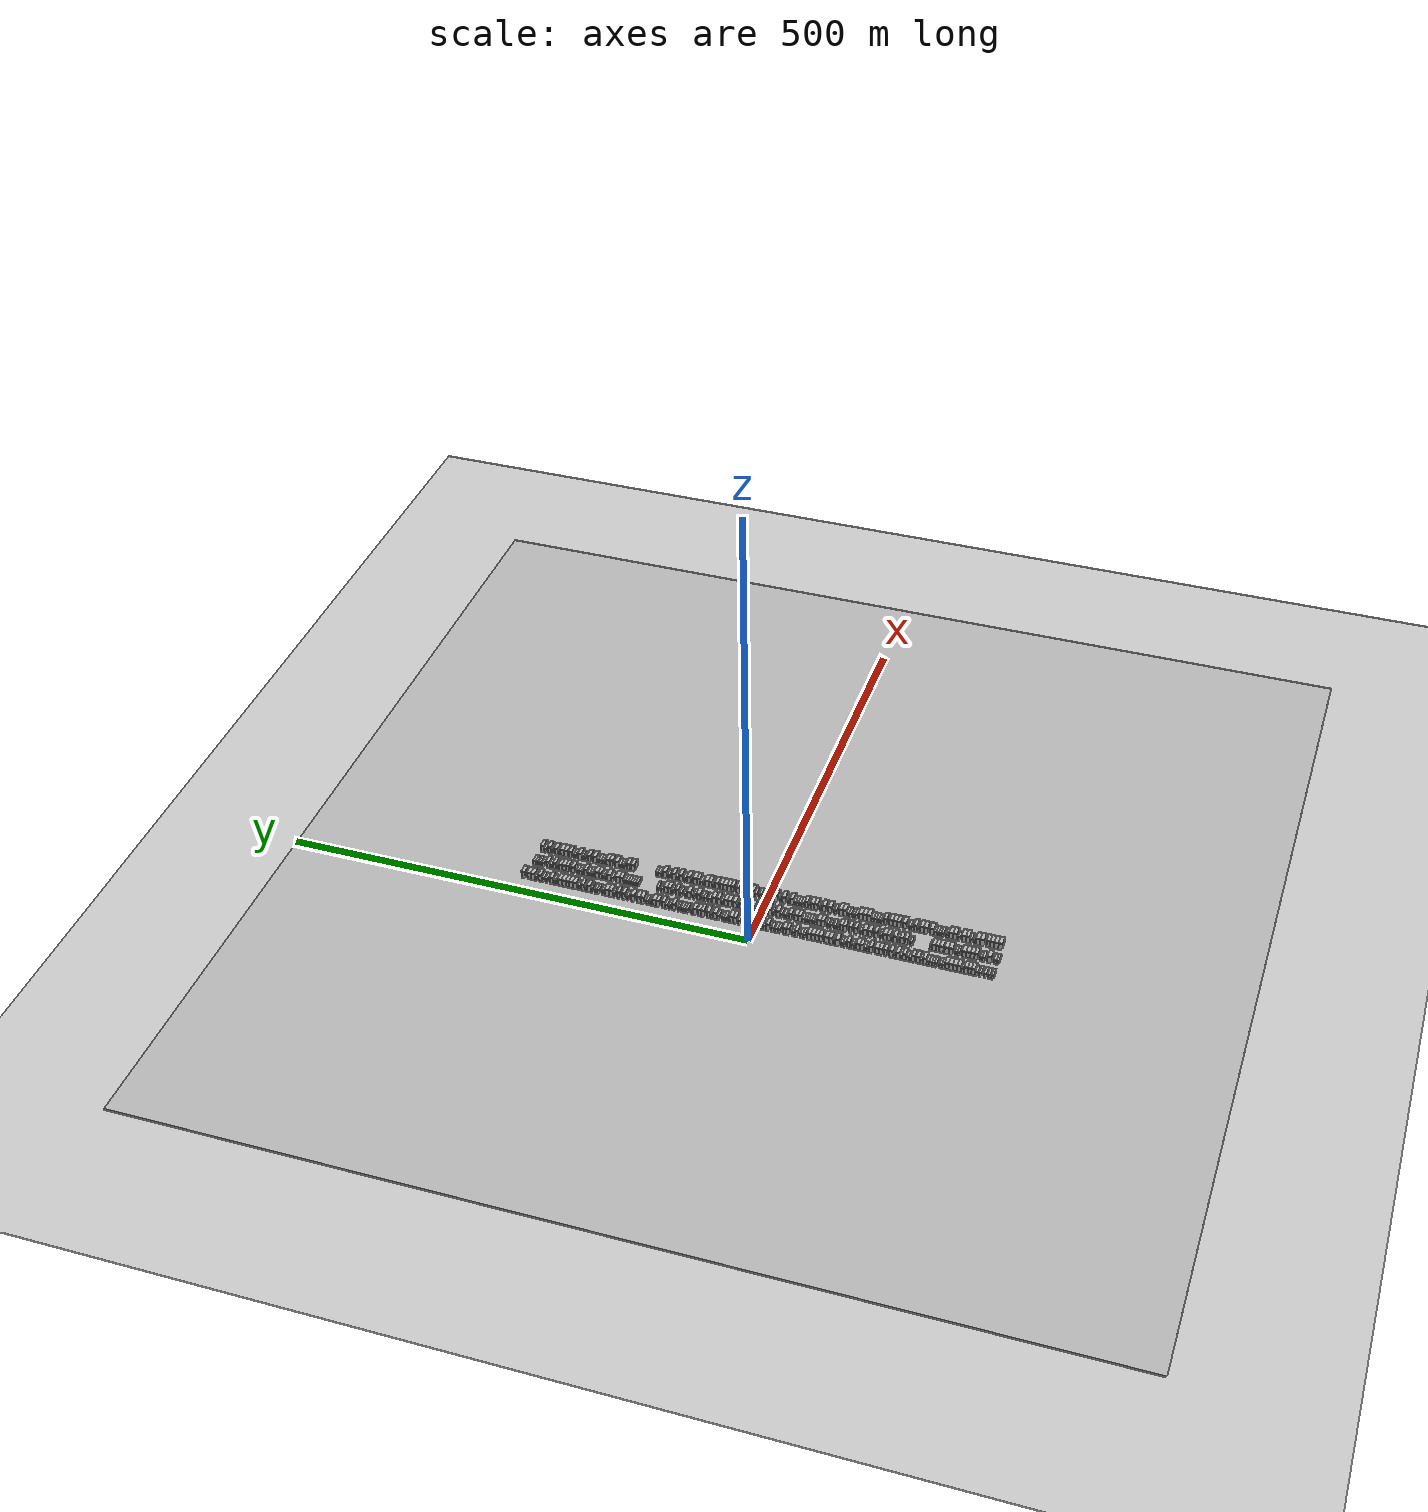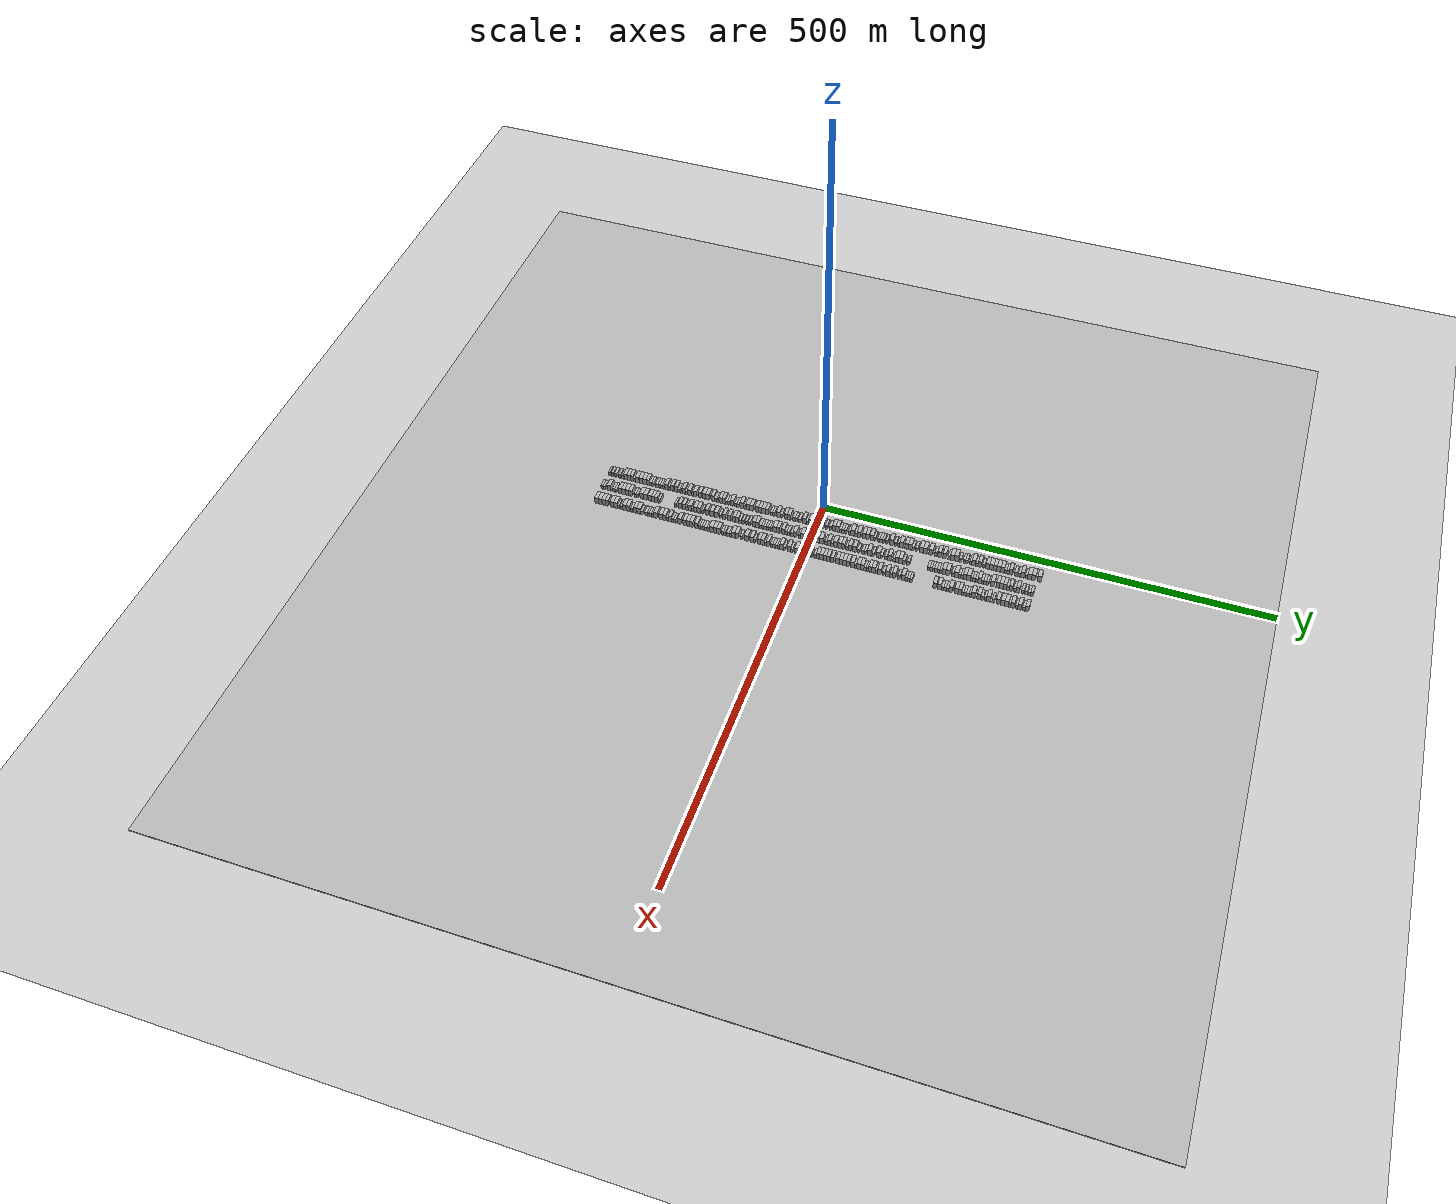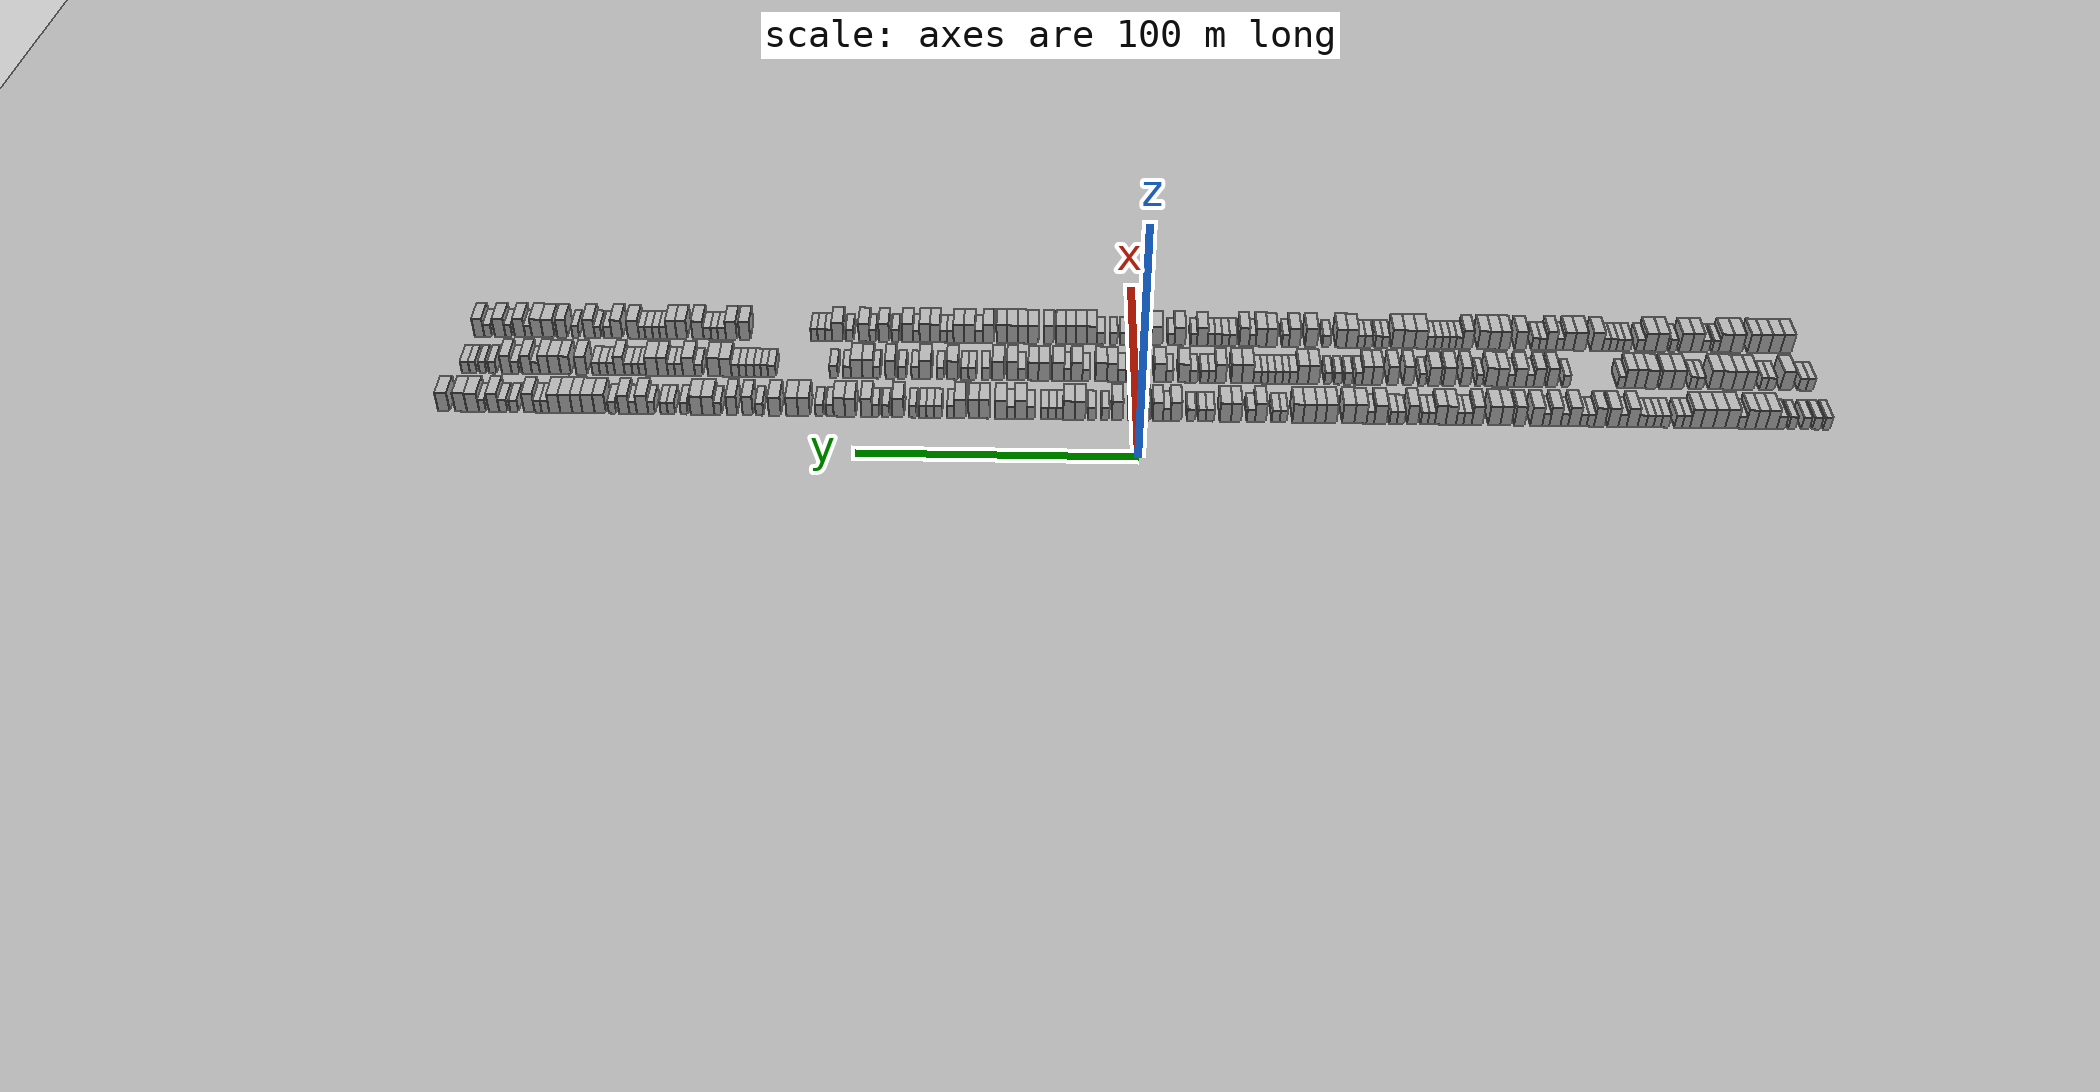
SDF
<?xml version="1.0" encoding="utf-8"?>

<sdf version="1.6">

   <world name="default">

      <gui fullscreen="0">

         <camera name="user_camera">

            <pose>-15 0 4.57585 0 0 0</pose>

            <view_controller>orbit</view_controller>

         </camera>

      </gui>

      <scene>

         <sky>

           <clouds>

             <speed>12</speed>

           </clouds>

         </sky>

         <ambient>0.4 0.4 0.4 1</ambient>

         <background>0.7 0.7 0.7 1</background>

         <shadows>1</shadows>

      </scene>

      <gravity>0 0 -9.8066</gravity>

      <magnetic_field>6e-06 2.3e-05 -4.2e-05</magnetic_field>

      <physics default="0" name="default_physics" type="ode">

         <ode>

            <solver>

               <type>quick</type>

               <iters>10</iters>

               <sor>1.0</sor>

               <use_dynamic_moi_rescaling>0</use_dynamic_moi_rescaling>

            </solver>

            <constraints>

               <cfm>0</cfm>

               <erp>0.2</erp>

               <contact_max_correcting_vel>100</contact_max_correcting_vel>

               <contact_surface_layer>0.001</contact_surface_layer>

            </constraints>

         </ode>

         <max_step_size>0.004</max_step_size>

         <real_time_factor>1</real_time_factor>

         <real_time_update_rate>250</real_time_update_rate>

      </physics>

      <light name="sun" type="directional">

         <cast_shadows>1</cast_shadows>

         <pose>0 0 10 0 0 0</pose>

         <diffuse>0.8 0.8 0.8 1</diffuse>

         <specular>0.2 0.2 0.2 1</specular>

         <attenuation>

            <range>1000</range>

            <constant>0.9</constant>

            <linear>0.01</linear>

            <quadratic>0.001</quadratic>

         </attenuation>

         <direction>-0.5 0.1 -0.9</direction>

      </light>

      <include>

         <name>ground_plane_1</name>

         <uri>model://HANNAS_ground_plane</uri>

         <pose>0 0 0  0 0 0</pose>

      </include>

      <include>

         <name>ground_plane_2</name>

         <uri>model://HANNAS_ground_plane</uri>

         <pose>100 0 0  0 0 0</pose>

      </include>

      <model name="building_1">

         <static>1</static>

         <pose frame="">25.0000 -246.7611 0 0.000000 0.000000 0.000000</pose>

         <link name="link">

            <pose frame="">0 0 3.00 0 0 0</pose>

            <collision name="collision">

               <geometry>

                  <box>

                     <size>10.0000 2.4778 6.0000</size>

                  </box>

               </geometry>

               <max_contacts>10</max_contacts>

               <surface>

                  <contact>

                     <ode/>

                  </contact>

                  <bounce/>

                  <friction>

                     <torsional>

                        <ode/>

                     </torsional>

                     <ode/>

                  </friction>

               </surface>

            </collision>

            <visual name="visual">

               <cast_shadows>0</cast_shadows>

               <geometry>

                  <box>

                     <size>10.0000 2.4778 6.0000</size>

                  </box>

               </geometry>

               <material>

                  <script>

                     <uri>model://HANNAS_wall/materials/scripts</uri>

                     <uri>model://HANNAS_wall/materials/textures</uri>

                     <name>vrc/HANNAS_wall</name>

                  </script>

               </material>

            </visual>

            <self_collide>0</self_collide>

            <enable_wind>0</enable_wind>

            <kinematic>0</kinematic>

         </link>

      </model>

      <model name="building_2">

         <static>1</static>

         <pose frame="">25.0000 -243.0767 0 0.000000 0.000000 0.000000</pose>

         <link name="link">

            <pose frame="">0 0 3.00 0 0 0</pose>

            <collision name="collision">

               <geometry>

                  <box>

                     <size>10.0000 2.8909 6.0000</size>

                  </box>

               </geometry>

               <max_contacts>10</max_contacts>

               <surface>

                  <contact>

                     <ode/>

                  </contact>

                  <bounce/>

                  <friction>

                     <torsional>

                        <ode/>

                     </torsional>

                     <ode/>

                  </friction>

               </surface>

            </collision>

            <visual name="visual">

               <cast_shadows>0</cast_shadows>

               <geometry>

                  <box>

                     <size>10.0000 2.8909 6.0000</size>

                  </box>

               </geometry>

               <material>

                  <script>

                     <uri>model://HANNAS_wall/materials/scripts</uri>

                     <uri>model://HANNAS_wall/materials/textures</uri>

                     <name>vrc/HANNAS_wall</name>

                  </script>

               </material>

            </visual>

            <self_collide>0</self_collide>

            <enable_wind>0</enable_wind>

            <kinematic>0</kinematic>

         </link>

      </model>

      <model name="building_3">

         <static>1</static>

         <pose frame="">25.0000 -239.1600 0 0.000000 0.000000 0.000000</pose>

         <link name="link">

            <pose frame="">0 0 3.00 0 0 0</pose>

            <collision name="collision">

               <geometry>

                  <box>

                     <size>10.0000 2.9425 6.0000</size>

                  </box>

               </geometry>

               <max_contacts>10</max_contacts>

               <surface>

                  <contact>

                     <ode/>

                  </contact>

                  <bounce/>

                  <friction>

                     <torsional>

                        <ode/>

                     </torsional>

                     <ode/>

                  </friction>

               </surface>

            </collision>

            <visual name="visual">

               <cast_shadows>0</cast_shadows>

               <geometry>

                  <box>

                     <size>10.0000 2.9425 6.0000</size>

                  </box>

               </geometry>

               <material>

                  <script>

                     <uri>model://HANNAS_wall/materials/scripts</uri>

                     <uri>model://HANNAS_wall/materials/textures</uri>

                     <name>vrc/HANNAS_wall</name>

                  </script>

               </material>

            </visual>

            <self_collide>0</self_collide>

            <enable_wind>0</enable_wind>

            <kinematic>0</kinematic>

         </link>

      </model>

      <model name="building_4">

         <static>1</static>

         <pose frame="">25.0000 -234.3755 0 0.000000 0.000000 0.000000</pose>

         <link name="link">

            <pose frame="">0 0 3.00 0 0 0</pose>

            <collision name="collision">

               <geometry>

                  <box>

                     <size>10.0000 2.6266 6.0000</size>

                  </box>

               </geometry>

               <max_contacts>10</max_contacts>

               <surface>

                  <contact>

                     <ode/>

                  </contact>

                  <bounce/>

                  <friction>

                     <torsional>

                        <ode/>

                     </torsional>

                     <ode/>

                  </friction>

               </surface>

            </collision>

            <visual name="visual">

               <cast_shadows>0</cast_shadows>

               <geometry>

                  <box>

                     <size>10.0000 2.6266 6.0000</size>

                  </box>

               </geometry>

               <material>

                  <script>

                     <uri>model://HANNAS_wall/materials/scripts</uri>

                     <uri>model://HANNAS_wall/materials/textures</uri>

                     <name>vrc/HANNAS_wall</name>

                  </script>

               </material>

            </visual>

            <self_collide>0</self_collide>

            <enable_wind>0</enable_wind>

            <kinematic>0</kinematic>

         </link>

      </model>

      <model name="building_5">

         <static>1</static>

         <pose frame="">25.0000 -230.5628 0 0.000000 0.000000 0.000000</pose>

         <link name="link">

            <pose frame="">0 0 3.00 0 0 0</pose>

            <collision name="collision">

               <geometry>

                  <box>

                     <size>10.0000 2.9986 6.0000</size>

                  </box>

               </geometry>

               <max_contacts>10</max_contacts>

               <surface>

                  <contact>

                     <ode/>

                  </contact>

                  <bounce/>

                  <friction>

                     <torsional>

                        <ode/>

                     </torsional>

                     <ode/>

                  </friction>

               </surface>

            </collision>

            <visual name="visual">

               <cast_shadows>0</cast_shadows>

               <geometry>

                  <box>

                     <size>10.0000 2.9986 6.0000</size>

                  </box>

               </geometry>

               <material>

                  <script>

                     <uri>model://HANNAS_wall/materials/scripts</uri>

                     <uri>model://HANNAS_wall/materials/textures</uri>

                     <name>vrc/HANNAS_wall</name>

                  </script>

               </material>

            </visual>

            <self_collide>0</self_collide>

            <enable_wind>0</enable_wind>

            <kinematic>0</kinematic>

         </link>

      </model>

      <model name="building_6">

         <static>1</static>

         <pose frame="">25.0000 -227.0855 0 0.000000 0.000000 0.000000</pose>

         <link name="link">

            <pose frame="">0 0 4.50 0 0 0</pose>

            <collision name="collision">

               <geometry>

                  <box>

                     <size>10.0000 3.9560 9.0000</size>

                  </box>

               </geometry>

               <max_contacts>10</max_contacts>

               <surface>

                  <contact>

                     <ode/>

                  </contact>

                  <bounce/>

                  <friction>

                     <torsional>

                        <ode/>

                     </torsional>

                     <ode/>

                  </friction>

               </surface>

            </collision>

            <visual name="visual">

               <cast_shadows>0</cast_shadows>

               <geometry>

                  <box>

                     <size>10.0000 3.9560 9.0000</size>

                  </box>

               </geometry>

               <material>

                  <script>

                     <uri>model://HANNAS_wall/materials/scripts</uri>

                     <uri>model://HANNAS_wall/materials/textures</uri>

                     <name>vrc/HANNAS_wall</name>

                  </script>

               </material>

            </visual>

            <self_collide>0</self_collide>

            <enable_wind>0</enable_wind>

            <kinematic>0</kinematic>

         </link>

      </model>

      <model name="building_7">

         <static>1</static>

         <pose frame="">25.0000 -223.2178 0 0.000000 0.000000 0.000000</pose>

         <link name="link">

            <pose frame="">0 0 4.50 0 0 0</pose>

            <collision name="collision">

               <geometry>

                  <box>

                     <size>10.0000 3.7794 9.0000</size>

                  </box>

               </geometry>

               <max_contacts>10</max_contacts>

               <surface>

                  <contact>

                     <ode/>

                  </contact>

                  <bounce/>

                  <friction>

                     <torsional>

                        <ode/>

                     </torsional>

                     <ode/>

                  </friction>

               </surface>

            </collision>

            <visual name="visual">

               <cast_shadows>0</cast_shadows>

               <geometry>

                  <box>

                     <size>10.0000 3.7794 9.0000</size>

                  </box>

               </geometry>

               <material>

                  <script>

                     <uri>model://HANNAS_wall/materials/scripts</uri>

                     <uri>model://HANNAS_wall/materials/textures</uri>

                     <name>vrc/HANNAS_wall</name>

                  </script>

               </material>

            </visual>

            <self_collide>0</self_collide>

            <enable_wind>0</enable_wind>

            <kinematic>0</kinematic>

         </link>

      </model>

      <model name="building_8">

         <static>1</static>

         <pose frame="">25.0000 -219.4982 0 0.000000 0.000000 0.000000</pose>

         <link name="link">

            <pose frame="">0 0 4.50 0 0 0</pose>

            <collision name="collision">

               <geometry>

                  <box>

                     <size>10.0000 3.6598 9.0000</size>

                  </box>

               </geometry>

               <max_contacts>10</max_contacts>

               <surface>

                  <contact>

                     <ode/>

                  </contact>

                  <bounce/>

                  <friction>

                     <torsional>

                        <ode/>

                     </torsional>

                     <ode/>

                  </friction>

               </surface>

            </collision>

            <visual name="visual">

               <cast_shadows>0</cast_shadows>

               <geometry>

                  <box>

                     <size>10.0000 3.6598 9.0000</size>

                  </box>

               </geometry>

               <material>

                  <script>

                     <uri>model://HANNAS_wall/materials/scripts</uri>

                     <uri>model://HANNAS_wall/materials/textures</uri>

                     <name>vrc/HANNAS_wall</name>

                  </script>

               </material>

            </visual>

            <self_collide>0</self_collide>

            <enable_wind>0</enable_wind>

            <kinematic>0</kinematic>

         </link>

      </model>

      <model name="building_9">

         <static>1</static>

         <pose frame="">25.0000 -216.2802 0 0.000000 0.000000 0.000000</pose>

         <link name="link">

            <pose frame="">0 0 3.00 0 0 0</pose>

            <collision name="collision">

               <geometry>

                  <box>

                     <size>10.0000 2.7762 6.0000</size>

                  </box>

               </geometry>

               <max_contacts>10</max_contacts>

               <surface>

                  <contact>

                     <ode/>

                  </contact>

                  <bounce/>

                  <friction>

                     <torsional>

                        <ode/>

                     </torsional>

                     <ode/>

                  </friction>

               </surface>

            </collision>

            <visual name="visual">

               <cast_shadows>0</cast_shadows>

               <geometry>

                  <box>

                     <size>10.0000 2.7762 6.0000</size>

                  </box>

               </geometry>

               <material>

                  <script>

                     <uri>model://HANNAS_wall/materials/scripts</uri>

                     <uri>model://HANNAS_wall/materials/textures</uri>

                     <name>vrc/HANNAS_wall</name>

                  </script>

               </material>

            </visual>

            <self_collide>0</self_collide>

            <enable_wind>0</enable_wind>

            <kinematic>0</kinematic>

         </link>

      </model>

      <model name="building_10">

         <static>1</static>

         <pose frame="">25.0000 -212.7430 0 0.000000 0.000000 0.000000</pose>

         <link name="link">

            <pose frame="">0 0 4.50 0 0 0</pose>

            <collision name="collision">

               <geometry>

                  <box>

                     <size>10.0000 4.2983 9.0000</size>

                  </box>

               </geometry>

               <max_contacts>10</max_contacts>

               <surface>

                  <contact>

                     <ode/>

                  </contact>

                  <bounce/>

                  <friction>

                     <torsional>

                        <ode/>

                     </torsional>

                     <ode/>

                  </friction>

               </surface>

            </collision>

            <visual name="visual">

               <cast_shadows>0</cast_shadows>

               <geometry>

                  <box>

                     <size>10.0000 4.2983 9.0000</size>

                  </box>

               </geometry>

               <material>

                  <script>

                     <uri>model://HANNAS_wall/materials/scripts</uri>

                     <uri>model://HANNAS_wall/materials/textures</uri>

                     <name>vrc/HANNAS_wall</name>

                  </script>

               </material>

            </visual>

            <self_collide>0</self_collide>

            <enable_wind>0</enable_wind>

            <kinematic>0</kinematic>

         </link>

      </model>

      <model name="building_11">

         <static>1</static>

         <pose frame="">25.0000 -208.4231 0 0.000000 0.000000 0.000000</pose>

         <link name="link">

            <pose frame="">0 0 4.50 0 0 0</pose>

            <collision name="collision">

               <geometry>

                  <box>

                     <size>10.0000 4.3414 9.0000</size>

                  </box>

               </geometry>

               <max_contacts>10</max_contacts>

               <surface>

                  <contact>

                     <ode/>

                  </contact>

                  <bounce/>

                  <friction>

                     <torsional>

                        <ode/>

                     </torsional>

                     <ode/>

                  </friction>

               </surface>

            </collision>

            <visual name="visual">

               <cast_shadows>0</cast_shadows>

               <geometry>

                  <box>

                     <size>10.0000 4.3414 9.0000</size>

                  </box>

               </geometry>

               <material>

                  <script>

                     <uri>model://HANNAS_wall/materials/scripts</uri>

                     <uri>model://HANNAS_wall/materials/textures</uri>

                     <name>vrc/HANNAS_wall</name>

                  </script>

               </material>

            </visual>

            <self_collide>0</self_collide>

            <enable_wind>0</enable_wind>

            <kinematic>0</kinematic>

         </link>

      </model>

      <model name="building_12">

         <static>1</static>

         <pose frame="">25.0000 -204.0479 0 0.000000 0.000000 0.000000</pose>

         <link name="link">

            <pose frame="">0 0 4.50 0 0 0</pose>

            <collision name="collision">

               <geometry>

                  <box>

                     <size>10.0000 4.4088 9.0000</size>

                  </box>

               </geometry>

               <max_contacts>10</max_contacts>

               <surface>

                  <contact>

                     <ode/>

                  </contact>

                  <bounce/>

                  <friction>

                     <torsional>

                        <ode/>

                     </torsional>

                     <ode/>

                  </friction>

               </surface>

            </collision>

            <visual name="visual">

               <cast_shadows>0</cast_shadows>

               <geometry>

                  <box>

                     <size>10.0000 4.4088 9.0000</size>

                  </box>

               </geometry>

               <material>

                  <script>

                     <uri>model://HANNAS_wall/materials/scripts</uri>

                     <uri>model://HANNAS_wall/materials/textures</uri>

                     <name>vrc/HANNAS_wall</name>

                  </script>

               </material>

            </visual>

            <self_collide>0</self_collide>

            <enable_wind>0</enable_wind>

            <kinematic>0</kinematic>

         </link>

      </model>

      <model name="building_13">

         <static>1</static>

         <pose frame="">25.0000 -199.9320 0 0.000000 0.000000 0.000000</pose>

         <link name="link">

            <pose frame="">0 0 4.50 0 0 0</pose>

            <collision name="collision">

               <geometry>

                  <box>

                     <size>10.0000 3.8231 9.0000</size>

                  </box>

               </geometry>

               <max_contacts>10</max_contacts>

               <surface>

                  <contact>

                     <ode/>

                  </contact>

                  <bounce/>

                  <friction>

                     <torsional>

                        <ode/>

                     </torsional>

                     <ode/>

                  </friction>

               </surface>

            </collision>

            <visual name="visual">

               <cast_shadows>0</cast_shadows>

               <geometry>

                  <box>

                     <size>10.0000 3.8231 9.0000</size>

                  </box>

               </geometry>

               <material>

                  <script>

                     <uri>model://HANNAS_wall/materials/scripts</uri>

                     <uri>model://HANNAS_wall/materials/textures</uri>

                     <name>vrc/HANNAS_wall</name>

                  </script>

               </material>

            </visual>

            <self_collide>0</self_collide>

            <enable_wind>0</enable_wind>

            <kinematic>0</kinematic>

         </link>

      </model>

      <model name="building_14">

         <static>1</static>

         <pose frame="">25.0000 -196.6251 0 0.000000 0.000000 0.000000</pose>

         <link name="link">

            <pose frame="">0 0 3.00 0 0 0</pose>

            <collision name="collision">

               <geometry>

                  <box>

                     <size>10.0000 2.7907 6.0000</size>

                  </box>

               </geometry>

               <max_contacts>10</max_contacts>

               <surface>

                  <contact>

                     <ode/>

                  </contact>

                  <bounce/>

                  <friction>

                     <torsional>

                        <ode/>

                     </torsional>

                     <ode/>

                  </friction>

               </surface>

            </collision>

            <visual name="visual">

               <cast_shadows>0</cast_shadows>

               <geometry>

                  <box>

                     <size>10.0000 2.7907 6.0000</size>

                  </box>

               </geometry>

               <material>

                  <script>

                     <uri>model://HANNAS_wall/materials/scripts</uri>

                     <uri>model://HANNAS_wall/materials/textures</uri>

                     <name>vrc/HANNAS_wall</name>

                  </script>

               </material>

            </visual>

            <self_collide>0</self_collide>

            <enable_wind>0</enable_wind>

            <kinematic>0</kinematic>

         </link>

      </model>

      <model name="building_15">

         <static>1</static>

         <pose frame="">25.0000 -193.8484 0 0.000000 0.000000 0.000000</pose>

         <link name="link">

            <pose frame="">0 0 3.00 0 0 0</pose>

            <collision name="collision">

               <geometry>

                  <box>

                     <size>10.0000 2.7627 6.0000</size>

                  </box>

               </geometry>

               <max_contacts>10</max_contacts>

               <surface>

                  <contact>

                     <ode/>

                  </contact>

                  <bounce/>

                  <friction>

                     <torsional>

                        <ode/>

                     </torsional>

                     <ode/>

                  </friction>

               </surface>

            </collision>

            <visual name="visual">

               <cast_shadows>0</cast_shadows>

               <geometry>

                  <box>

                     <size>10.0000 2.7627 6.0000</size>

                  </box>

               </geometry>

               <material>

                  <script>

                     <uri>model://HANNAS_wall/materials/scripts</uri>

                     <uri>model://HANNAS_wall/materials/textures</uri>

                     <name>vrc/HANNAS_wall</name>

                  </script>

               </material>

            </visual>

            <self_collide>0</self_collide>

            <enable_wind>0</enable_wind>

            <kinematic>0</kinematic>

         </link>

      </model>

      <model name="building_16">

         <static>1</static>

         <pose frame="">25.0000 -188.9910 0 0.000000 0.000000 0.000000</pose>

         <link name="link">

            <pose frame="">0 0 3.00 0 0 0</pose>

            <collision name="collision">

               <geometry>

                  <box>

                     <size>10.0000 2.9520 6.0000</size>

                  </box>

               </geometry>

               <max_contacts>10</max_contacts>

               <surface>

                  <contact>

                     <ode/>

                  </contact>

                  <bounce/>

                  <friction>

                     <torsional>

                        <ode/>

                     </torsional>

                     <ode/>

                  </friction>

               </surface>

            </collision>

            <visual name="visual">

               <cast_shadows>0</cast_shadows>

               <geometry>

                  <box>

                     <size>10.0000 2.9520 6.0000</size>

                  </box>

               </geometry>

               <material>

                  <script>

                     <uri>model://HANNAS_wall/materials/scripts</uri>

                     <uri>model://HANNAS_wall/materials/textures</uri>

                     <name>vrc/HANNAS_wall</name>

                  </script>

               </material>

            </visual>

            <self_collide>0</self_collide>

            <enable_wind>0</enable_wind>

            <kinematic>0</kinematic>

         </link>

      </model>

      <model name="building_17">

         <static>1</static>

         <pose frame="">25.0000 -186.2234 0 0.000000 0.000000 0.000000</pose>

         <link name="link">

            <pose frame="">0 0 3.00 0 0 0</pose>

            <collision name="collision">

               <geometry>

                  <box>

                     <size>10.0000 2.5832 6.0000</size>

                  </box>

               </geometry>

               <max_contacts>10</max_contacts>

               <surface>

                  <contact>

                     <ode/>

                  </contact>

                  <bounce/>

                  <friction>

                     <torsional>

                        <ode/>

                     </torsional>

                     <ode/>

                  </friction>

               </surface>

            </collision>

            <visual name="visual">

               <cast_shadows>0</cast_shadows>

               <geometry>

                  <box>

                     <size>10.0000 2.5832 6.0000</size>

                  </box>

               </geometry>

               <material>

                  <script>

                     <uri>model://HANNAS_wall/materials/scripts</uri>

                     <uri>model://HANNAS_wall/materials/textures</uri>

                     <name>vrc/HANNAS_wall</name>

                  </script>

               </material>

            </visual>

            <self_collide>0</self_collide>

            <enable_wind>0</enable_wind>

            <kinematic>0</kinematic>

         </link>

      </model>

      <model name="building_18">

         <static>1</static>

         <pose frame="">25.0000 -183.5607 0 0.000000 0.000000 0.000000</pose>

         <link name="link">

            <pose frame="">0 0 3.00 0 0 0</pose>

            <collision name="collision">

               <geometry>

                  <box>

                     <size>10.0000 2.7422 6.0000</size>

                  </box>

               </geometry>

               <max_contacts>10</max_contacts>

               <surface>

                  <contact>

                     <ode/>

                  </contact>

                  <bounce/>

                  <friction>

                     <torsional>

                        <ode/>

                     </torsional>

                     <ode/>

                  </friction>

               </surface>

            </collision>

            <visual name="visual">

               <cast_shadows>0</cast_shadows>

               <geometry>

                  <box>

                     <size>10.0000 2.7422 6.0000</size>

                  </box>

               </geometry>

               <material>

                  <script>

                     <uri>model://HANNAS_wall/materials/scripts</uri>

                     <uri>model://HANNAS_wall/materials/textures</uri>

                     <name>vrc/HANNAS_wall</name>

                  </script>

               </material>

            </visual>

            <self_collide>0</self_collide>

            <enable_wind>0</enable_wind>

            <kinematic>0</kinematic>

         </link>

      </model>

      <model name="building_19">

         <static>1</static>

         <pose frame="">25.0000 -180.7234 0 0.000000 0.000000 0.000000</pose>

         <link name="link">

            <pose frame="">0 0 3.00 0 0 0</pose>

            <collision name="collision">

               <geometry>

                  <box>

                     <size>10.0000 2.9323 6.0000</size>

                  </box>

               </geometry>

               <max_contacts>10</max_contacts>

               <surface>

                  <contact>

                     <ode/>

                  </contact>

                  <bounce/>

                  <friction>

                     <torsional>

                        <ode/>

                     </torsional>

                     <ode/>

                  </friction>

               </surface>

            </collision>

            <visual name="visual">

               <cast_shadows>0</cast_shadows>

               <geometry>

                  <box>

                     <size>10.0000 2.9323 6.0000</size>

                  </box>

               </geometry>

               <material>

                  <script>

                     <uri>model://HANNAS_wall/materials/scripts</uri>

                     <uri>model://HANNAS_wall/materials/textures</uri>

                     <name>vrc/HANNAS_wall</name>

                  </script>

               </material>

            </visual>

            <self_collide>0</self_collide>

            <enable_wind>0</enable_wind>

            <kinematic>0</kinematic>

         </link>

      </model>

      <model name="building_20">

         <static>1</static>

         <pose frame="">25.0000 -177.3001 0 0.000000 0.000000 0.000000</pose>

         <link name="link">

            <pose frame="">0 0 4.50 0 0 0</pose>

            <collision name="collision">

               <geometry>

                  <box>

                     <size>10.0000 3.9144 9.0000</size>

                  </box>

               </geometry>

               <max_contacts>10</max_contacts>

               <surface>

                  <contact>

                     <ode/>

                  </contact>

                  <bounce/>

                  <friction>

                     <torsional>

                        <ode/>

                     </torsional>

                     <ode/>

                  </friction>

               </surface>

            </collision>

            <visual name="visual">

               <cast_shadows>0</cast_shadows>

               <geometry>

                  <box>

                     <size>10.0000 3.9144 9.0000</size>

                  </box>

               </geometry>

               <material>

                  <script>

                     <uri>model://HANNAS_wall/materials/scripts</uri>

                     <uri>model://HANNAS_wall/materials/textures</uri>

                     <name>vrc/HANNAS_wall</name>

                  </script>

               </material>

            </visual>

            <self_collide>0</self_collide>

            <enable_wind>0</enable_wind>

            <kinematic>0</kinematic>

         </link>

      </model>

      <model name="building_21">

         <static>1</static>

         <pose frame="">25.0000 -173.9023 0 0.000000 0.000000 0.000000</pose>

         <link name="link">

            <pose frame="">0 0 3.00 0 0 0</pose>

            <collision name="collision">

               <geometry>

                  <box>

                     <size>10.0000 2.8811 6.0000</size>

                  </box>

               </geometry>

               <max_contacts>10</max_contacts>

               <surface>

                  <contact>

                     <ode/>

                  </contact>

                  <bounce/>

                  <friction>

                     <torsional>

                        <ode/>

                     </torsional>

                     <ode/>

                  </friction>

               </surface>

            </collision>

            <visual name="visual">

               <cast_shadows>0</cast_shadows>

               <geometry>

                  <box>

                     <size>10.0000 2.8811 6.0000</size>

                  </box>

               </geometry>

               <material>

                  <script>

                     <uri>model://HANNAS_wall/materials/scripts</uri>

                     <uri>model://HANNAS_wall/materials/textures</uri>

                     <name>vrc/HANNAS_wall</name>

                  </script>

               </material>

            </visual>

            <self_collide>0</self_collide>

            <enable_wind>0</enable_wind>

            <kinematic>0</kinematic>

         </link>

      </model>

      <model name="building_22">

         <static>1</static>

         <pose frame="">25.0000 -170.4851 0 0.000000 0.000000 0.000000</pose>

         <link name="link">

            <pose frame="">0 0 4.50 0 0 0</pose>

            <collision name="collision">

               <geometry>

                  <box>

                     <size>10.0000 3.9534 9.0000</size>

                  </box>

               </geometry>

               <max_contacts>10</max_contacts>

               <surface>

                  <contact>

                     <ode/>

                  </contact>

                  <bounce/>

                  <friction>

                     <torsional>

                        <ode/>

                     </torsional>

                     <ode/>

                  </friction>

               </surface>

            </collision>

            <visual name="visual">

               <cast_shadows>0</cast_shadows>

               <geometry>

                  <box>

                     <size>10.0000 3.9534 9.0000</size>

                  </box>

               </geometry>

               <material>

                  <script>

                     <uri>model://HANNAS_wall/materials/scripts</uri>

                     <uri>model://HANNAS_wall/materials/textures</uri>

                     <name>vrc/HANNAS_wall</name>

                  </script>

               </material>

            </visual>

            <self_collide>0</self_collide>

            <enable_wind>0</enable_wind>

            <kinematic>0</kinematic>

         </link>

      </model>

      <model name="building_23">

         <static>1</static>

         <pose frame="">25.0000 -165.6124 0 0.000000 0.000000 0.000000</pose>

         <link name="link">

            <pose frame="">0 0 4.50 0 0 0</pose>

            <collision name="collision">

               <geometry>

                  <box>

                     <size>10.0000 3.7921 9.0000</size>

                  </box>

               </geometry>

               <max_contacts>10</max_contacts>

               <surface>

                  <contact>

                     <ode/>

                  </contact>

                  <bounce/>

                  <friction>

                     <torsional>

                        <ode/>

                     </torsional>

                     <ode/>

                  </friction>

               </surface>

            </collision>

            <visual name="visual">

               <cast_shadows>0</cast_shadows>

               <geometry>

                  <box>

                     <size>10.0000 3.7921 9.0000</size>

                  </box>

               </geometry>

               <material>

                  <script>

                     <uri>model://HANNAS_wall/materials/scripts</uri>

                     <uri>model://HANNAS_wall/materials/textures</uri>

                     <name>vrc/HANNAS_wall</name>

                  </script>

               </material>

            </visual>

            <self_collide>0</self_collide>

            <enable_wind>0</enable_wind>

            <kinematic>0</kinematic>

         </link>

      </model>

      <model name="building_24">

         <static>1</static>

         <pose frame="">25.0000 -162.4022 0 0.000000 0.000000 0.000000</pose>

         <link name="link">

            <pose frame="">0 0 3.00 0 0 0</pose>

            <collision name="collision">

               <geometry>

                  <box>

                     <size>10.0000 2.6282 6.0000</size>

                  </box>

               </geometry>

               <max_contacts>10</max_contacts>

               <surface>

                  <contact>

                     <ode/>

                  </contact>

                  <bounce/>

                  <friction>

                     <torsional>

                        <ode/>

                     </torsional>

                     <ode/>

                  </friction>

               </surface>

            </collision>

            <visual name="visual">

               <cast_shadows>0</cast_shadows>

               <geometry>

                  <box>

                     <size>10.0000 2.6282 6.0000</size>

                  </box>

               </geometry>

               <material>

                  <script>

                     <uri>model://HANNAS_wall/materials/scripts</uri>

                     <uri>model://HANNAS_wall/materials/textures</uri>

                     <name>vrc/HANNAS_wall</name>

                  </script>

               </material>

            </visual>

            <self_collide>0</self_collide>

            <enable_wind>0</enable_wind>

            <kinematic>0</kinematic>

         </link>

      </model>

      <model name="building_25">

         <static>1</static>

         <pose frame="">25.0000 -159.8226 0 0.000000 0.000000 0.000000</pose>

         <link name="link">

            <pose frame="">0 0 3.00 0 0 0</pose>

            <collision name="collision">

               <geometry>

                  <box>

                     <size>10.0000 2.5311 6.0000</size>

                  </box>

               </geometry>

               <max_contacts>10</max_contacts>

               <surface>

                  <contact>

                     <ode/>

                  </contact>

                  <bounce/>

                  <friction>

                     <torsional>

                        <ode/>

                     </torsional>

                     <ode/>

                  </friction>

               </surface>

            </collision>

            <visual name="visual">

               <cast_shadows>0</cast_shadows>

               <geometry>

                  <box>

                     <size>10.0000 2.5311 6.0000</size>

                  </box>

               </geometry>

               <material>

                  <script>

                     <uri>model://HANNAS_wall/materials/scripts</uri>

                     <uri>model://HANNAS_wall/materials/textures</uri>

                     <name>vrc/HANNAS_wall</name>

                  </script>

               </material>

            </visual>

            <self_collide>0</self_collide>

            <enable_wind>0</enable_wind>

            <kinematic>0</kinematic>

         </link>

      </model>

      <model name="building_26">

         <static>1</static>

         <pose frame="">25.0000 -156.5214 0 0.000000 0.000000 0.000000</pose>

         <link name="link">

            <pose frame="">0 0 4.50 0 0 0</pose>

            <collision name="collision">

               <geometry>

                  <box>

                     <size>10.0000 4.0711 9.0000</size>

                  </box>

               </geometry>

               <max_contacts>10</max_contacts>

               <surface>

                  <contact>

                     <ode/>

                  </contact>

                  <bounce/>

                  <friction>

                     <torsional>

                        <ode/>

                     </torsional>

                     <ode/>

                  </friction>

               </surface>

            </collision>

            <visual name="visual">

               <cast_shadows>0</cast_shadows>

               <geometry>

                  <box>

                     <size>10.0000 4.0711 9.0000</size>

                  </box>

               </geometry>

               <material>

                  <script>

                     <uri>model://HANNAS_wall/materials/scripts</uri>

                     <uri>model://HANNAS_wall/materials/textures</uri>

                     <name>vrc/HANNAS_wall</name>

                  </script>

               </material>

            </visual>

            <self_collide>0</self_collide>

            <enable_wind>0</enable_wind>

            <kinematic>0</kinematic>

         </link>

      </model>

      <model name="building_27">

         <static>1</static>

         <pose frame="">25.0000 -153.1143 0 0.000000 0.000000 0.000000</pose>

         <link name="link">

            <pose frame="">0 0 3.00 0 0 0</pose>

            <collision name="collision">

               <geometry>

                  <box>

                     <size>10.0000 2.7433 6.0000</size>

                  </box>

               </geometry>

               <max_contacts>10</max_contacts>

               <surface>

                  <contact>

                     <ode/>

                  </contact>

                  <bounce/>

                  <friction>

                     <torsional>

                        <ode/>

                     </torsional>

                     <ode/>

                  </friction>

               </surface>

            </collision>

            <visual name="visual">

               <cast_shadows>0</cast_shadows>

               <geometry>

                  <box>

                     <size>10.0000 2.7433 6.0000</size>

                  </box>

               </geometry>

               <material>

                  <script>

                     <uri>model://HANNAS_wall/materials/scripts</uri>

                     <uri>model://HANNAS_wall/materials/textures</uri>

                     <name>vrc/HANNAS_wall</name>

                  </script>

               </material>

            </visual>

            <self_collide>0</self_collide>

            <enable_wind>0</enable_wind>

            <kinematic>0</kinematic>

         </link>

      </model>

      <model name="building_28">

         <static>1</static>

         <pose frame="">25.0000 -149.7521 0 0.000000 0.000000 0.000000</pose>

         <link name="link">

            <pose frame="">0 0 4.50 0 0 0</pose>

            <collision name="collision">

               <geometry>

                  <box>

                     <size>10.0000 3.9810 9.0000</size>

                  </box>

               </geometry>

               <max_contacts>10</max_contacts>

               <surface>

                  <contact>

                     <ode/>

                  </contact>

                  <bounce/>

                  <friction>

                     <torsional>

                        <ode/>

                     </torsional>

                     <ode/>

                  </friction>

               </surface>

            </collision>

            <visual name="visual">

               <cast_shadows>0</cast_shadows>

               <geometry>

                  <box>

                     <size>10.0000 3.9810 9.0000</size>

                  </box>

               </geometry>

               <material>

                  <script>

                     <uri>model://HANNAS_wall/materials/scripts</uri>

                     <uri>model://HANNAS_wall/materials/textures</uri>

                     <name>vrc/HANNAS_wall</name>

                  </script>

               </material>

            </visual>

            <self_collide>0</self_collide>

            <enable_wind>0</enable_wind>

            <kinematic>0</kinematic>

         </link>

      </model>

      <model name="building_29">

         <static>1</static>

         <pose frame="">25.0000 -146.4961 0 0.000000 0.000000 0.000000</pose>

         <link name="link">

            <pose frame="">0 0 3.00 0 0 0</pose>

            <collision name="collision">

               <geometry>

                  <box>

                     <size>10.0000 2.5310 6.0000</size>

                  </box>

               </geometry>

               <max_contacts>10</max_contacts>

               <surface>

                  <contact>

                     <ode/>

                  </contact>

                  <bounce/>

                  <friction>

                     <torsional>

                        <ode/>

                     </torsional>

                     <ode/>

                  </friction>

               </surface>

            </collision>

            <visual name="visual">

               <cast_shadows>0</cast_shadows>

               <geometry>

                  <box>

                     <size>10.0000 2.5310 6.0000</size>

                  </box>

               </geometry>

               <material>

                  <script>

                     <uri>model://HANNAS_wall/materials/scripts</uri>

                     <uri>model://HANNAS_wall/materials/textures</uri>

                     <name>vrc/HANNAS_wall</name>

                  </script>

               </material>

            </visual>

            <self_collide>0</self_collide>

            <enable_wind>0</enable_wind>

            <kinematic>0</kinematic>

         </link>

      </model>

      <model name="building_30">

         <static>1</static>

         <pose frame="">25.0000 -143.0944 0 0.000000 0.000000 0.000000</pose>

         <link name="link">

            <pose frame="">0 0 4.50 0 0 0</pose>

            <collision name="collision">

               <geometry>

                  <box>

                     <size>10.0000 4.2724 9.0000</size>

                  </box>

               </geometry>

               <max_contacts>10</max_contacts>

               <surface>

                  <contact>

                     <ode/>

                  </contact>

                  <bounce/>

                  <friction>

                     <torsional>

                        <ode/>

                     </torsional>

                     <ode/>

                  </friction>

               </surface>

            </collision>

            <visual name="visual">

               <cast_shadows>0</cast_shadows>

               <geometry>

                  <box>

                     <size>10.0000 4.2724 9.0000</size>

                  </box>

               </geometry>

               <material>

                  <script>

                     <uri>model://HANNAS_wall/materials/scripts</uri>

                     <uri>model://HANNAS_wall/materials/textures</uri>

                     <name>vrc/HANNAS_wall</name>

                  </script>

               </material>

            </visual>

            <self_collide>0</self_collide>

            <enable_wind>0</enable_wind>

            <kinematic>0</kinematic>

         </link>

      </model>

      <model name="building_31">

         <static>1</static>

         <pose frame="">25.0000 -137.0730 0 0.000000 0.000000 0.000000</pose>

         <link name="link">

            <pose frame="">0 0 4.50 0 0 0</pose>

            <collision name="collision">

               <geometry>

                  <box>

                     <size>10.0000 3.7703 9.0000</size>

                  </box>

               </geometry>

               <max_contacts>10</max_contacts>

               <surface>

                  <contact>

                     <ode/>

                  </contact>

                  <bounce/>

                  <friction>

                     <torsional>

                        <ode/>

                     </torsional>

                     <ode/>

                  </friction>

               </surface>

            </collision>

            <visual name="visual">

               <cast_shadows>0</cast_shadows>

               <geometry>

                  <box>

                     <size>10.0000 3.7703 9.0000</size>

                  </box>

               </geometry>

               <material>

                  <script>

                     <uri>model://HANNAS_wall/materials/scripts</uri>

                     <uri>model://HANNAS_wall/materials/textures</uri>

                     <name>vrc/HANNAS_wall</name>

                  </script>

               </material>

            </visual>

            <self_collide>0</self_collide>

            <enable_wind>0</enable_wind>

            <kinematic>0</kinematic>

         </link>

      </model>

      <model name="building_32">

         <static>1</static>

         <pose frame="">25.0000 -132.1731 0 0.000000 0.000000 0.000000</pose>

         <link name="link">

            <pose frame="">0 0 4.50 0 0 0</pose>

            <collision name="collision">

               <geometry>

                  <box>

                     <size>10.0000 4.0297 9.0000</size>

                  </box>

               </geometry>

               <max_contacts>10</max_contacts>

               <surface>

                  <contact>

                     <ode/>

                  </contact>

                  <bounce/>

                  <friction>

                     <torsional>

                        <ode/>

                     </torsional>

                     <ode/>

                  </friction>

               </surface>

            </collision>

            <visual name="visual">

               <cast_shadows>0</cast_shadows>

               <geometry>

                  <box>

                     <size>10.0000 4.0297 9.0000</size>

                  </box>

               </geometry>

               <material>

                  <script>

                     <uri>model://HANNAS_wall/materials/scripts</uri>

                     <uri>model://HANNAS_wall/materials/textures</uri>

                     <name>vrc/HANNAS_wall</name>

                  </script>

               </material>

            </visual>

            <self_collide>0</self_collide>

            <enable_wind>0</enable_wind>

            <kinematic>0</kinematic>

         </link>

      </model>

      <model name="building_33">

         <static>1</static>

         <pose frame="">25.0000 -128.0066 0 0.000000 0.000000 0.000000</pose>

         <link name="link">

            <pose frame="">0 0 4.50 0 0 0</pose>

            <collision name="collision">

               <geometry>

                  <box>

                     <size>10.0000 4.3032 9.0000</size>

                  </box>

               </geometry>

               <max_contacts>10</max_contacts>

               <surface>

                  <contact>

                     <ode/>

                  </contact>

                  <bounce/>

                  <friction>

                     <torsional>

                        <ode/>

                     </torsional>

                     <ode/>

                  </friction>

               </surface>

            </collision>

            <visual name="visual">

               <cast_shadows>0</cast_shadows>

               <geometry>

                  <box>

                     <size>10.0000 4.3032 9.0000</size>

                  </box>

               </geometry>

               <material>

                  <script>

                     <uri>model://HANNAS_wall/materials/scripts</uri>

                     <uri>model://HANNAS_wall/materials/textures</uri>

                     <name>vrc/HANNAS_wall</name>

                  </script>

               </material>

            </visual>

            <self_collide>0</self_collide>

            <enable_wind>0</enable_wind>

            <kinematic>0</kinematic>

         </link>

      </model>

      <model name="building_34">

         <static>1</static>

         <pose frame="">25.0000 -121.8989 0 0.000000 0.000000 0.000000</pose>

         <link name="link">

            <pose frame="">0 0 4.50 0 0 0</pose>

            <collision name="collision">

               <geometry>

                  <box>

                     <size>10.0000 3.9122 9.0000</size>

                  </box>

               </geometry>

               <max_contacts>10</max_contacts>

               <surface>

                  <contact>

                     <ode/>

                  </contact>

                  <bounce/>

                  <friction>

                     <torsional>

                        <ode/>

                     </torsional>

                     <ode/>

                  </friction>

               </surface>

            </collision>

            <visual name="visual">

               <cast_shadows>0</cast_shadows>

               <geometry>

                  <box>

                     <size>10.0000 3.9122 9.0000</size>

                  </box>

               </geometry>

               <material>

                  <script>

                     <uri>model://HANNAS_wall/materials/scripts</uri>

                     <uri>model://HANNAS_wall/materials/textures</uri>

                     <name>vrc/HANNAS_wall</name>

                  </script>

               </material>

            </visual>

            <self_collide>0</self_collide>

            <enable_wind>0</enable_wind>

            <kinematic>0</kinematic>

         </link>

      </model>

      <model name="building_35">

         <static>1</static>

         <pose frame="">25.0000 -118.4441 0 0.000000 0.000000 0.000000</pose>

         <link name="link">

            <pose frame="">0 0 3.00 0 0 0</pose>

            <collision name="collision">

               <geometry>

                  <box>

                     <size>10.0000 2.9973 6.0000</size>

                  </box>

               </geometry>

               <max_contacts>10</max_contacts>

               <surface>

                  <contact>

                     <ode/>

                  </contact>

                  <bounce/>

                  <friction>

                     <torsional>

                        <ode/>

                     </torsional>

                     <ode/>

                  </friction>

               </surface>

            </collision>

            <visual name="visual">

               <cast_shadows>0</cast_shadows>

               <geometry>

                  <box>

                     <size>10.0000 2.9973 6.0000</size>

                  </box>

               </geometry>

               <material>

                  <script>

                     <uri>model://HANNAS_wall/materials/scripts</uri>

                     <uri>model://HANNAS_wall/materials/textures</uri>

                     <name>vrc/HANNAS_wall</name>

                  </script>

               </material>

            </visual>

            <self_collide>0</self_collide>

            <enable_wind>0</enable_wind>

            <kinematic>0</kinematic>

         </link>

      </model>

      <model name="building_36">

         <static>1</static>

         <pose frame="">25.0000 -115.6381 0 0.000000 0.000000 0.000000</pose>

         <link name="link">

            <pose frame="">0 0 3.00 0 0 0</pose>

            <collision name="collision">

               <geometry>

                  <box>

                     <size>10.0000 2.6147 6.0000</size>

                  </box>

               </geometry>

               <max_contacts>10</max_contacts>

               <surface>

                  <contact>

                     <ode/>

                  </contact>

                  <bounce/>

                  <friction>

                     <torsional>

                        <ode/>

                     </torsional>

                     <ode/>

                  </friction>

               </surface>

            </collision>

            <visual name="visual">

               <cast_shadows>0</cast_shadows>

               <geometry>

                  <box>

                     <size>10.0000 2.6147 6.0000</size>

                  </box>

               </geometry>

               <material>

                  <script>

                     <uri>model://HANNAS_wall/materials/scripts</uri>

                     <uri>model://HANNAS_wall/materials/textures</uri>

                     <name>vrc/HANNAS_wall</name>

                  </script>

               </material>

            </visual>

            <self_collide>0</self_collide>

            <enable_wind>0</enable_wind>

            <kinematic>0</kinematic>

         </link>

      </model>

      <model name="building_37">

         <static>1</static>

         <pose frame="">25.0000 -112.4635 0 0.000000 0.000000 0.000000</pose>

         <link name="link">

            <pose frame="">0 0 4.50 0 0 0</pose>

            <collision name="collision">

               <geometry>

                  <box>

                     <size>10.0000 3.7345 9.0000</size>

                  </box>

               </geometry>

               <max_contacts>10</max_contacts>

               <surface>

                  <contact>

                     <ode/>

                  </contact>

                  <bounce/>

                  <friction>

                     <torsional>

                        <ode/>

                     </torsional>

                     <ode/>

                  </friction>

               </surface>

            </collision>

            <visual name="visual">

               <cast_shadows>0</cast_shadows>

               <geometry>

                  <box>

                     <size>10.0000 3.7345 9.0000</size>

                  </box>

               </geometry>

               <material>

                  <script>

                     <uri>model://HANNAS_wall/materials/scripts</uri>

                     <uri>model://HANNAS_wall/materials/textures</uri>

                     <name>vrc/HANNAS_wall</name>

                  </script>

               </material>

            </visual>

            <self_collide>0</self_collide>

            <enable_wind>0</enable_wind>

            <kinematic>0</kinematic>

         </link>

      </model>

      <model name="building_38">

         <static>1</static>

         <pose frame="">25.0000 -108.6606 0 0.000000 0.000000 0.000000</pose>

         <link name="link">

            <pose frame="">0 0 4.50 0 0 0</pose>

            <collision name="collision">

               <geometry>

                  <box>

                     <size>10.0000 3.8712 9.0000</size>

                  </box>

               </geometry>

               <max_contacts>10</max_contacts>

               <surface>

                  <contact>

                     <ode/>

                  </contact>

                  <bounce/>

                  <friction>

                     <torsional>

                        <ode/>

                     </torsional>

                     <ode/>

                  </friction>

               </surface>

            </collision>

            <visual name="visual">

               <cast_shadows>0</cast_shadows>

               <geometry>

                  <box>

                     <size>10.0000 3.8712 9.0000</size>

                  </box>

               </geometry>

               <material>

                  <script>

                     <uri>model://HANNAS_wall/materials/scripts</uri>

                     <uri>model://HANNAS_wall/materials/textures</uri>

                     <name>vrc/HANNAS_wall</name>

                  </script>

               </material>

            </visual>

            <self_collide>0</self_collide>

            <enable_wind>0</enable_wind>

            <kinematic>0</kinematic>

         </link>

      </model>

      <model name="building_39">

         <static>1</static>

         <pose frame="">25.0000 -105.4579 0 0.000000 0.000000 0.000000</pose>

         <link name="link">

            <pose frame="">0 0 3.00 0 0 0</pose>

            <collision name="collision">

               <geometry>

                  <box>

                     <size>10.0000 2.5342 6.0000</size>

                  </box>

               </geometry>

               <max_contacts>10</max_contacts>

               <surface>

                  <contact>

                     <ode/>

                  </contact>

                  <bounce/>

                  <friction>

                     <torsional>

                        <ode/>

                     </torsional>

                     <ode/>

                  </friction>

               </surface>

            </collision>

            <visual name="visual">

               <cast_shadows>0</cast_shadows>

               <geometry>

                  <box>

                     <size>10.0000 2.5342 6.0000</size>

                  </box>

               </geometry>

               <material>

                  <script>

                     <uri>model://HANNAS_wall/materials/scripts</uri>

                     <uri>model://HANNAS_wall/materials/textures</uri>

                     <name>vrc/HANNAS_wall</name>

                  </script>

               </material>

            </visual>

            <self_collide>0</self_collide>

            <enable_wind>0</enable_wind>

            <kinematic>0</kinematic>

         </link>

      </model>

      <model name="building_40">

         <static>1</static>

         <pose frame="">25.0000 -102.9112 0 0.000000 0.000000 0.000000</pose>

         <link name="link">

            <pose frame="">0 0 3.00 0 0 0</pose>

            <collision name="collision">

               <geometry>

                  <box>

                     <size>10.0000 2.5594 6.0000</size>

                  </box>

               </geometry>

               <max_contacts>10</max_contacts>

               <surface>

                  <contact>

                     <ode/>

                  </contact>

                  <bounce/>

                  <friction>

                     <torsional>

                        <ode/>

                     </torsional>

                     <ode/>

                  </friction>

               </surface>

            </collision>

            <visual name="visual">

               <cast_shadows>0</cast_shadows>

               <geometry>

                  <box>

                     <size>10.0000 2.5594 6.0000</size>

                  </box>

               </geometry>

               <material>

                  <script>

                     <uri>model://HANNAS_wall/materials/scripts</uri>

                     <uri>model://HANNAS_wall/materials/textures</uri>

                     <name>vrc/HANNAS_wall</name>

                  </script>

               </material>

            </visual>

            <self_collide>0</self_collide>

            <enable_wind>0</enable_wind>

            <kinematic>0</kinematic>

         </link>

      </model>

      <model name="building_41">

         <static>1</static>

         <pose frame="">25.0000 -98.7287 0 0.000000 0.000000 0.000000</pose>

         <link name="link">

            <pose frame="">0 0 4.50 0 0 0</pose>

            <collision name="collision">

               <geometry>

                  <box>

                     <size>10.0000 3.8055 9.0000</size>

                  </box>

               </geometry>

               <max_contacts>10</max_contacts>

               <surface>

                  <contact>

                     <ode/>

                  </contact>

                  <bounce/>

                  <friction>

                     <torsional>

                        <ode/>

                     </torsional>

                     <ode/>

                  </friction>

               </surface>

            </collision>

            <visual name="visual">

               <cast_shadows>0</cast_shadows>

               <geometry>

                  <box>

                     <size>10.0000 3.8055 9.0000</size>

                  </box>

               </geometry>

               <material>

                  <script>

                     <uri>model://HANNAS_wall/materials/scripts</uri>

                     <uri>model://HANNAS_wall/materials/textures</uri>

                     <name>vrc/HANNAS_wall</name>

                  </script>

               </material>

            </visual>

            <self_collide>0</self_collide>

            <enable_wind>0</enable_wind>

            <kinematic>0</kinematic>

         </link>

      </model>

      <model name="building_42">

         <static>1</static>

         <pose frame="">25.0000 -94.4601 0 0.000000 0.000000 0.000000</pose>

         <link name="link">

            <pose frame="">0 0 3.00 0 0 0</pose>

            <collision name="collision">

               <geometry>

                  <box>

                     <size>10.0000 2.7317 6.0000</size>

                  </box>

               </geometry>

               <max_contacts>10</max_contacts>

               <surface>

                  <contact>

                     <ode/>

                  </contact>

                  <bounce/>

                  <friction>

                     <torsional>

                        <ode/>

                     </torsional>

                     <ode/>

                  </friction>

               </surface>

            </collision>

            <visual name="visual">

               <cast_shadows>0</cast_shadows>

               <geometry>

                  <box>

                     <size>10.0000 2.7317 6.0000</size>

                  </box>

               </geometry>

               <material>

                  <script>

                     <uri>model://HANNAS_wall/materials/scripts</uri>

                     <uri>model://HANNAS_wall/materials/textures</uri>

                     <name>vrc/HANNAS_wall</name>

                  </script>

               </material>

            </visual>

            <self_collide>0</self_collide>

            <enable_wind>0</enable_wind>

            <kinematic>0</kinematic>

         </link>

      </model>

      <model name="building_43">

         <static>1</static>

         <pose frame="">25.0000 -91.7571 0 0.000000 0.000000 0.000000</pose>

         <link name="link">

            <pose frame="">0 0 3.00 0 0 0</pose>

            <collision name="collision">

               <geometry>

                  <box>

                     <size>10.0000 2.6743 6.0000</size>

                  </box>

               </geometry>

               <max_contacts>10</max_contacts>

               <surface>

                  <contact>

                     <ode/>

                  </contact>

                  <bounce/>

                  <friction>

                     <torsional>

                        <ode/>

                     </torsional>

                     <ode/>

                  </friction>

               </surface>

            </collision>

            <visual name="visual">

               <cast_shadows>0</cast_shadows>

               <geometry>

                  <box>

                     <size>10.0000 2.6743 6.0000</size>

                  </box>

               </geometry>

               <material>

                  <script>

                     <uri>model://HANNAS_wall/materials/scripts</uri>

                     <uri>model://HANNAS_wall/materials/textures</uri>

                     <name>vrc/HANNAS_wall</name>

                  </script>

               </material>

            </visual>

            <self_collide>0</self_collide>

            <enable_wind>0</enable_wind>

            <kinematic>0</kinematic>

         </link>

      </model>

      <model name="building_44">

         <static>1</static>

         <pose frame="">25.0000 -87.1862 0 0.000000 0.000000 0.000000</pose>

         <link name="link">

            <pose frame="">0 0 4.50 0 0 0</pose>

            <collision name="collision">

               <geometry>

                  <box>

                     <size>10.0000 4.4677 9.0000</size>

                  </box>

               </geometry>

               <max_contacts>10</max_contacts>

               <surface>

                  <contact>

                     <ode/>

                  </contact>

                  <bounce/>

                  <friction>

                     <torsional>

                        <ode/>

                     </torsional>

                     <ode/>

                  </friction>

               </surface>

            </collision>

            <visual name="visual">

               <cast_shadows>0</cast_shadows>

               <geometry>

                  <box>

                     <size>10.0000 4.4677 9.0000</size>

                  </box>

               </geometry>

               <material>

                  <script>

                     <uri>model://HANNAS_wall/materials/scripts</uri>

                     <uri>model://HANNAS_wall/materials/textures</uri>

                     <name>vrc/HANNAS_wall</name>

                  </script>

               </material>

            </visual>

            <self_collide>0</self_collide>

            <enable_wind>0</enable_wind>

            <kinematic>0</kinematic>

         </link>

      </model>

      <model name="building_45">

         <static>1</static>

         <pose frame="">25.0000 -83.5829 0 0.000000 0.000000 0.000000</pose>

         <link name="link">

            <pose frame="">0 0 3.00 0 0 0</pose>

            <collision name="collision">

               <geometry>

                  <box>

                     <size>10.0000 2.7389 6.0000</size>

                  </box>

               </geometry>

               <max_contacts>10</max_contacts>

               <surface>

                  <contact>

                     <ode/>

                  </contact>

                  <bounce/>

                  <friction>

                     <torsional>

                        <ode/>

                     </torsional>

                     <ode/>

                  </friction>

               </surface>

            </collision>

            <visual name="visual">

               <cast_shadows>0</cast_shadows>

               <geometry>

                  <box>

                     <size>10.0000 2.7389 6.0000</size>

                  </box>

               </geometry>

               <material>

                  <script>

                     <uri>model://HANNAS_wall/materials/scripts</uri>

                     <uri>model://HANNAS_wall/materials/textures</uri>

                     <name>vrc/HANNAS_wall</name>

                  </script>

               </material>

            </visual>

            <self_collide>0</self_collide>

            <enable_wind>0</enable_wind>

            <kinematic>0</kinematic>

         </link>

      </model>

      <model name="building_46">

         <static>1</static>

         <pose frame="">25.0000 -80.0410 0 0.000000 0.000000 0.000000</pose>

         <link name="link">

            <pose frame="">0 0 4.50 0 0 0</pose>

            <collision name="collision">

               <geometry>

                  <box>

                     <size>10.0000 4.3449 9.0000</size>

                  </box>

               </geometry>

               <max_contacts>10</max_contacts>

               <surface>

                  <contact>

                     <ode/>

                  </contact>

                  <bounce/>

                  <friction>

                     <torsional>

                        <ode/>

                     </torsional>

                     <ode/>

                  </friction>

               </surface>

            </collision>

            <visual name="visual">

               <cast_shadows>0</cast_shadows>

               <geometry>

                  <box>

                     <size>10.0000 4.3449 9.0000</size>

                  </box>

               </geometry>

               <material>

                  <script>

                     <uri>model://HANNAS_wall/materials/scripts</uri>

                     <uri>model://HANNAS_wall/materials/textures</uri>

                     <name>vrc/HANNAS_wall</name>

                  </script>

               </material>

            </visual>

            <self_collide>0</self_collide>

            <enable_wind>0</enable_wind>

            <kinematic>0</kinematic>

         </link>

      </model>

      <model name="building_47">

         <static>1</static>

         <pose frame="">25.0000 -75.6703 0 0.000000 0.000000 0.000000</pose>

         <link name="link">

            <pose frame="">0 0 4.50 0 0 0</pose>

            <collision name="collision">

               <geometry>

                  <box>

                     <size>10.0000 4.3965 9.0000</size>

                  </box>

               </geometry>

               <max_contacts>10</max_contacts>

               <surface>

                  <contact>

                     <ode/>

                  </contact>

                  <bounce/>

                  <friction>

                     <torsional>

                        <ode/>

                     </torsional>

                     <ode/>

                  </friction>

               </surface>

            </collision>

            <visual name="visual">

               <cast_shadows>0</cast_shadows>

               <geometry>

                  <box>

                     <size>10.0000 4.3965 9.0000</size>

                  </box>

               </geometry>

               <material>

                  <script>

                     <uri>model://HANNAS_wall/materials/scripts</uri>

                     <uri>model://HANNAS_wall/materials/textures</uri>

                     <name>vrc/HANNAS_wall</name>

                  </script>

               </material>

            </visual>

            <self_collide>0</self_collide>

            <enable_wind>0</enable_wind>

            <kinematic>0</kinematic>

         </link>

      </model>

      <model name="building_48">

         <static>1</static>

         <pose frame="">25.0000 -69.4344 0 0.000000 0.000000 0.000000</pose>

         <link name="link">

            <pose frame="">0 0 4.50 0 0 0</pose>

            <collision name="collision">

               <geometry>

                  <box>

                     <size>10.0000 4.0752 9.0000</size>

                  </box>

               </geometry>

               <max_contacts>10</max_contacts>

               <surface>

                  <contact>

                     <ode/>

                  </contact>

                  <bounce/>

                  <friction>

                     <torsional>

                        <ode/>

                     </torsional>

                     <ode/>

                  </friction>

               </surface>

            </collision>

            <visual name="visual">

               <cast_shadows>0</cast_shadows>

               <geometry>

                  <box>

                     <size>10.0000 4.0752 9.0000</size>

                  </box>

               </geometry>

               <material>

                  <script>

                     <uri>model://HANNAS_wall/materials/scripts</uri>

                     <uri>model://HANNAS_wall/materials/textures</uri>

                     <name>vrc/HANNAS_wall</name>

                  </script>

               </material>

            </visual>

            <self_collide>0</self_collide>

            <enable_wind>0</enable_wind>

            <kinematic>0</kinematic>

         </link>

      </model>

      <model name="building_49">

         <static>1</static>

         <pose frame="">25.0000 -65.5864 0 0.000000 0.000000 0.000000</pose>

         <link name="link">

            <pose frame="">0 0 4.50 0 0 0</pose>

            <collision name="collision">

               <geometry>

                  <box>

                     <size>10.0000 3.6208 9.0000</size>

                  </box>

               </geometry>

               <max_contacts>10</max_contacts>

               <surface>

                  <contact>

                     <ode/>

                  </contact>

                  <bounce/>

                  <friction>

                     <torsional>

                        <ode/>

                     </torsional>

                     <ode/>

                  </friction>

               </surface>

            </collision>

            <visual name="visual">

               <cast_shadows>0</cast_shadows>

               <geometry>

                  <box>

                     <size>10.0000 3.6208 9.0000</size>

                  </box>

               </geometry>

               <material>

                  <script>

                     <uri>model://HANNAS_wall/materials/scripts</uri>

                     <uri>model://HANNAS_wall/materials/textures</uri>

                     <name>vrc/HANNAS_wall</name>

                  </script>

               </material>

            </visual>

            <self_collide>0</self_collide>

            <enable_wind>0</enable_wind>

            <kinematic>0</kinematic>

         </link>

      </model>

      <model name="building_50">

         <static>1</static>

         <pose frame="">25.0000 -61.5727 0 0.000000 0.000000 0.000000</pose>

         <link name="link">

            <pose frame="">0 0 4.50 0 0 0</pose>

            <collision name="collision">

               <geometry>

                  <box>

                     <size>10.0000 4.4066 9.0000</size>

                  </box>

               </geometry>

               <max_contacts>10</max_contacts>

               <surface>

                  <contact>

                     <ode/>

                  </contact>

                  <bounce/>

                  <friction>

                     <torsional>

                        <ode/>

                     </torsional>

                     <ode/>

                  </friction>

               </surface>

            </collision>

            <visual name="visual">

               <cast_shadows>0</cast_shadows>

               <geometry>

                  <box>

                     <size>10.0000 4.4066 9.0000</size>

                  </box>

               </geometry>

               <material>

                  <script>

                     <uri>model://HANNAS_wall/materials/scripts</uri>

                     <uri>model://HANNAS_wall/materials/textures</uri>

                     <name>vrc/HANNAS_wall</name>

                  </script>

               </material>

            </visual>

            <self_collide>0</self_collide>

            <enable_wind>0</enable_wind>

            <kinematic>0</kinematic>

         </link>

      </model>

      <model name="building_51">

         <static>1</static>

         <pose frame="">25.0000 -57.4883 0 0.000000 0.000000 0.000000</pose>

         <link name="link">

            <pose frame="">0 0 4.50 0 0 0</pose>

            <collision name="collision">

               <geometry>

                  <box>

                     <size>10.0000 3.7621 9.0000</size>

                  </box>

               </geometry>

               <max_contacts>10</max_contacts>

               <surface>

                  <contact>

                     <ode/>

                  </contact>

                  <bounce/>

                  <friction>

                     <torsional>

                        <ode/>

                     </torsional>

                     <ode/>

                  </friction>

               </surface>

            </collision>

            <visual name="visual">

               <cast_shadows>0</cast_shadows>

               <geometry>

                  <box>

                     <size>10.0000 3.7621 9.0000</size>

                  </box>

               </geometry>

               <material>

                  <script>

                     <uri>model://HANNAS_wall/materials/scripts</uri>

                     <uri>model://HANNAS_wall/materials/textures</uri>

                     <name>vrc/HANNAS_wall</name>

                  </script>

               </material>

            </visual>

            <self_collide>0</self_collide>

            <enable_wind>0</enable_wind>

            <kinematic>0</kinematic>

         </link>

      </model>

      <model name="building_52">

         <static>1</static>

         <pose frame="">25.0000 -52.3211 0 0.000000 0.000000 0.000000</pose>

         <link name="link">

            <pose frame="">0 0 3.00 0 0 0</pose>

            <collision name="collision">

               <geometry>

                  <box>

                     <size>10.0000 2.5723 6.0000</size>

                  </box>

               </geometry>

               <max_contacts>10</max_contacts>

               <surface>

                  <contact>

                     <ode/>

                  </contact>

                  <bounce/>

                  <friction>

                     <torsional>

                        <ode/>

                     </torsional>

                     <ode/>

                  </friction>

               </surface>

            </collision>

            <visual name="visual">

               <cast_shadows>0</cast_shadows>

               <geometry>

                  <box>

                     <size>10.0000 2.5723 6.0000</size>

                  </box>

               </geometry>

               <material>

                  <script>

                     <uri>model://HANNAS_wall/materials/scripts</uri>

                     <uri>model://HANNAS_wall/materials/textures</uri>

                     <name>vrc/HANNAS_wall</name>

                  </script>

               </material>

            </visual>

            <self_collide>0</self_collide>

            <enable_wind>0</enable_wind>

            <kinematic>0</kinematic>

         </link>

      </model>

      <model name="building_53">

         <static>1</static>

         <pose frame="">25.0000 -49.5831 0 0.000000 0.000000 0.000000</pose>

         <link name="link">

            <pose frame="">0 0 3.00 0 0 0</pose>

            <collision name="collision">

               <geometry>

                  <box>

                     <size>10.0000 2.9037 6.0000</size>

                  </box>

               </geometry>

               <max_contacts>10</max_contacts>

               <surface>

                  <contact>

                     <ode/>

                  </contact>

                  <bounce/>

                  <friction>

                     <torsional>

                        <ode/>

                     </torsional>

                     <ode/>

                  </friction>

               </surface>

            </collision>

            <visual name="visual">

               <cast_shadows>0</cast_shadows>

               <geometry>

                  <box>

                     <size>10.0000 2.9037 6.0000</size>

                  </box>

               </geometry>

               <material>

                  <script>

                     <uri>model://HANNAS_wall/materials/scripts</uri>

                     <uri>model://HANNAS_wall/materials/textures</uri>

                     <name>vrc/HANNAS_wall</name>

                  </script>

               </material>

            </visual>

            <self_collide>0</self_collide>

            <enable_wind>0</enable_wind>

            <kinematic>0</kinematic>

         </link>

      </model>

      <model name="building_54">

         <static>1</static>

         <pose frame="">25.0000 -44.1548 0 0.000000 0.000000 0.000000</pose>

         <link name="link">

            <pose frame="">0 0 4.50 0 0 0</pose>

            <collision name="collision">

               <geometry>

                  <box>

                     <size>10.0000 3.9528 9.0000</size>

                  </box>

               </geometry>

               <max_contacts>10</max_contacts>

               <surface>

                  <contact>

                     <ode/>

                  </contact>

                  <bounce/>

                  <friction>

                     <torsional>

                        <ode/>

                     </torsional>

                     <ode/>

                  </friction>

               </surface>

            </collision>

            <visual name="visual">

               <cast_shadows>0</cast_shadows>

               <geometry>

                  <box>

                     <size>10.0000 3.9528 9.0000</size>

                  </box>

               </geometry>

               <material>

                  <script>

                     <uri>model://HANNAS_wall/materials/scripts</uri>

                     <uri>model://HANNAS_wall/materials/textures</uri>

                     <name>vrc/HANNAS_wall</name>

                  </script>

               </material>

            </visual>

            <self_collide>0</self_collide>

            <enable_wind>0</enable_wind>

            <kinematic>0</kinematic>

         </link>

      </model>

      <model name="building_55">

         <static>1</static>

         <pose frame="">25.0000 -40.6841 0 0.000000 0.000000 0.000000</pose>

         <link name="link">

            <pose frame="">0 0 3.00 0 0 0</pose>

            <collision name="collision">

               <geometry>

                  <box>

                     <size>10.0000 2.9886 6.0000</size>

                  </box>

               </geometry>

               <max_contacts>10</max_contacts>

               <surface>

                  <contact>

                     <ode/>

                  </contact>

                  <bounce/>

                  <friction>

                     <torsional>

                        <ode/>

                     </torsional>

                     <ode/>

                  </friction>

               </surface>

            </collision>

            <visual name="visual">

               <cast_shadows>0</cast_shadows>

               <geometry>

                  <box>

                     <size>10.0000 2.9886 6.0000</size>

                  </box>

               </geometry>

               <material>

                  <script>

                     <uri>model://HANNAS_wall/materials/scripts</uri>

                     <uri>model://HANNAS_wall/materials/textures</uri>

                     <name>vrc/HANNAS_wall</name>

                  </script>

               </material>

            </visual>

            <self_collide>0</self_collide>

            <enable_wind>0</enable_wind>

            <kinematic>0</kinematic>

         </link>

      </model>

      <model name="building_56">

         <static>1</static>

         <pose frame="">25.0000 -35.3655 0 0.000000 0.000000 0.000000</pose>

         <link name="link">

            <pose frame="">0 0 4.50 0 0 0</pose>

            <collision name="collision">

               <geometry>

                  <box>

                     <size>10.0000 3.6488 9.0000</size>

                  </box>

               </geometry>

               <max_contacts>10</max_contacts>

               <surface>

                  <contact>

                     <ode/>

                  </contact>

                  <bounce/>

                  <friction>

                     <torsional>

                        <ode/>

                     </torsional>

                     <ode/>

                  </friction>

               </surface>

            </collision>

            <visual name="visual">

               <cast_shadows>0</cast_shadows>

               <geometry>

                  <box>

                     <size>10.0000 3.6488 9.0000</size>

                  </box>

               </geometry>

               <material>

                  <script>

                     <uri>model://HANNAS_wall/materials/scripts</uri>

                     <uri>model://HANNAS_wall/materials/textures</uri>

                     <name>vrc/HANNAS_wall</name>

                  </script>

               </material>

            </visual>

            <self_collide>0</self_collide>

            <enable_wind>0</enable_wind>

            <kinematic>0</kinematic>

         </link>

      </model>

      <model name="building_57">

         <static>1</static>

         <pose frame="">25.0000 -31.4911 0 0.000000 0.000000 0.000000</pose>

         <link name="link">

            <pose frame="">0 0 4.50 0 0 0</pose>

            <collision name="collision">

               <geometry>

                  <box>

                     <size>10.0000 4.1000 9.0000</size>

                  </box>

               </geometry>

               <max_contacts>10</max_contacts>

               <surface>

                  <contact>

                     <ode/>

                  </contact>

                  <bounce/>

                  <friction>

                     <torsional>

                        <ode/>

                     </torsional>

                     <ode/>

                  </friction>

               </surface>

            </collision>

            <visual name="visual">

               <cast_shadows>0</cast_shadows>

               <geometry>

                  <box>

                     <size>10.0000 4.1000 9.0000</size>

                  </box>

               </geometry>

               <material>

                  <script>

                     <uri>model://HANNAS_wall/materials/scripts</uri>

                     <uri>model://HANNAS_wall/materials/textures</uri>

                     <name>vrc/HANNAS_wall</name>

                  </script>

               </material>

            </visual>

            <self_collide>0</self_collide>

            <enable_wind>0</enable_wind>

            <kinematic>0</kinematic>

         </link>

      </model>

      <model name="building_58">

         <static>1</static>

         <pose frame="">25.0000 -25.9524 0 0.000000 0.000000 0.000000</pose>

         <link name="link">

            <pose frame="">0 0 3.00 0 0 0</pose>

            <collision name="collision">

               <geometry>

                  <box>

                     <size>10.0000 2.9773 6.0000</size>

                  </box>

               </geometry>

               <max_contacts>10</max_contacts>

               <surface>

                  <contact>

                     <ode/>

                  </contact>

                  <bounce/>

                  <friction>

                     <torsional>

                        <ode/>

                     </torsional>

                     <ode/>

                  </friction>

               </surface>

            </collision>

            <visual name="visual">

               <cast_shadows>0</cast_shadows>

               <geometry>

                  <box>

                     <size>10.0000 2.9773 6.0000</size>

                  </box>

               </geometry>

               <material>

                  <script>

                     <uri>model://HANNAS_wall/materials/scripts</uri>

                     <uri>model://HANNAS_wall/materials/textures</uri>

                     <name>vrc/HANNAS_wall</name>

                  </script>

               </material>

            </visual>

            <self_collide>0</self_collide>

            <enable_wind>0</enable_wind>

            <kinematic>0</kinematic>

         </link>

      </model>

      <model name="building_59">

         <static>1</static>

         <pose frame="">25.0000 -23.0482 0 0.000000 0.000000 0.000000</pose>

         <link name="link">

            <pose frame="">0 0 3.00 0 0 0</pose>

            <collision name="collision">

               <geometry>

                  <box>

                     <size>10.0000 2.8312 6.0000</size>

                  </box>

               </geometry>

               <max_contacts>10</max_contacts>

               <surface>

                  <contact>

                     <ode/>

                  </contact>

                  <bounce/>

                  <friction>

                     <torsional>

                        <ode/>

                     </torsional>

                     <ode/>

                  </friction>

               </surface>

            </collision>

            <visual name="visual">

               <cast_shadows>0</cast_shadows>

               <geometry>

                  <box>

                     <size>10.0000 2.8312 6.0000</size>

                  </box>

               </geometry>

               <material>

                  <script>

                     <uri>model://HANNAS_wall/materials/scripts</uri>

                     <uri>model://HANNAS_wall/materials/textures</uri>

                     <name>vrc/HANNAS_wall</name>

                  </script>

               </material>

            </visual>

            <self_collide>0</self_collide>

            <enable_wind>0</enable_wind>

            <kinematic>0</kinematic>

         </link>

      </model>

      <model name="building_60">

         <static>1</static>

         <pose frame="">25.0000 -19.1541 0 0.000000 0.000000 0.000000</pose>

         <link name="link">

            <pose frame="">0 0 3.00 0 0 0</pose>

            <collision name="collision">

               <geometry>

                  <box>

                     <size>10.0000 2.9568 6.0000</size>

                  </box>

               </geometry>

               <max_contacts>10</max_contacts>

               <surface>

                  <contact>

                     <ode/>

                  </contact>

                  <bounce/>

                  <friction>

                     <torsional>

                        <ode/>

                     </torsional>

                     <ode/>

                  </friction>

               </surface>

            </collision>

            <visual name="visual">

               <cast_shadows>0</cast_shadows>

               <geometry>

                  <box>

                     <size>10.0000 2.9568 6.0000</size>

                  </box>

               </geometry>

               <material>

                  <script>

                     <uri>model://HANNAS_wall/materials/scripts</uri>

                     <uri>model://HANNAS_wall/materials/textures</uri>

                     <name>vrc/HANNAS_wall</name>

                  </script>

               </material>

            </visual>

            <self_collide>0</self_collide>

            <enable_wind>0</enable_wind>

            <kinematic>0</kinematic>

         </link>

      </model>

      <model name="building_61">

         <static>1</static>

         <pose frame="">25.0000 -13.7435 0 0.000000 0.000000 0.000000</pose>

         <link name="link">

            <pose frame="">0 0 4.50 0 0 0</pose>

            <collision name="collision">

               <geometry>

                  <box>

                     <size>10.0000 3.8644 9.0000</size>

                  </box>

               </geometry>

               <max_contacts>10</max_contacts>

               <surface>

                  <contact>

                     <ode/>

                  </contact>

                  <bounce/>

                  <friction>

                     <torsional>

                        <ode/>

                     </torsional>

                     <ode/>

                  </friction>

               </surface>

            </collision>

            <visual name="visual">

               <cast_shadows>0</cast_shadows>

               <geometry>

                  <box>

                     <size>10.0000 3.8644 9.0000</size>

                  </box>

               </geometry>

               <material>

                  <script>

                     <uri>model://HANNAS_wall/materials/scripts</uri>

                     <uri>model://HANNAS_wall/materials/textures</uri>

                     <name>vrc/HANNAS_wall</name>

                  </script>

               </material>

            </visual>

            <self_collide>0</self_collide>

            <enable_wind>0</enable_wind>

            <kinematic>0</kinematic>

         </link>

      </model>

      <model name="building_62">

         <static>1</static>

         <pose frame="">25.0000 -10.4363 0 0.000000 0.000000 0.000000</pose>

         <link name="link">

            <pose frame="">0 0 3.00 0 0 0</pose>

            <collision name="collision">

               <geometry>

                  <box>

                     <size>10.0000 2.7500 6.0000</size>

                  </box>

               </geometry>

               <max_contacts>10</max_contacts>

               <surface>

                  <contact>

                     <ode/>

                  </contact>

                  <bounce/>

                  <friction>

                     <torsional>

                        <ode/>

                     </torsional>

                     <ode/>

                  </friction>

               </surface>

            </collision>

            <visual name="visual">

               <cast_shadows>0</cast_shadows>

               <geometry>

                  <box>

                     <size>10.0000 2.7500 6.0000</size>

                  </box>

               </geometry>

               <material>

                  <script>

                     <uri>model://HANNAS_wall/materials/scripts</uri>

                     <uri>model://HANNAS_wall/materials/textures</uri>

                     <name>vrc/HANNAS_wall</name>

                  </script>

               </material>

            </visual>

            <self_collide>0</self_collide>

            <enable_wind>0</enable_wind>

            <kinematic>0</kinematic>

         </link>

      </model>

      <model name="building_63">

         <static>1</static>

         <pose frame="">25.0000 -7.2013 0 0.000000 0.000000 0.000000</pose>

         <link name="link">

            <pose frame="">0 0 4.50 0 0 0</pose>

            <collision name="collision">

               <geometry>

                  <box>

                     <size>10.0000 3.7201 9.0000</size>

                  </box>

               </geometry>

               <max_contacts>10</max_contacts>

               <surface>

                  <contact>

                     <ode/>

                  </contact>

                  <bounce/>

                  <friction>

                     <torsional>

                        <ode/>

                     </torsional>

                     <ode/>

                  </friction>

               </surface>

            </collision>

            <visual name="visual">

               <cast_shadows>0</cast_shadows>

               <geometry>

                  <box>

                     <size>10.0000 3.7201 9.0000</size>

                  </box>

               </geometry>

               <material>

                  <script>

                     <uri>model://HANNAS_wall/materials/scripts</uri>

                     <uri>model://HANNAS_wall/materials/textures</uri>

                     <name>vrc/HANNAS_wall</name>

                  </script>

               </material>

            </visual>

            <self_collide>0</self_collide>

            <enable_wind>0</enable_wind>

            <kinematic>0</kinematic>

         </link>

      </model>

      <model name="building_64">

         <static>1</static>

         <pose frame="">25.0000 -2.4187 0 0.000000 0.000000 0.000000</pose>

         <link name="link">

            <pose frame="">0 0 4.50 0 0 0</pose>

            <collision name="collision">

               <geometry>

                  <box>

                     <size>10.0000 3.8450 9.0000</size>

                  </box>

               </geometry>

               <max_contacts>10</max_contacts>

               <surface>

                  <contact>

                     <ode/>

                  </contact>

                  <bounce/>

                  <friction>

                     <torsional>

                        <ode/>

                     </torsional>

                     <ode/>

                  </friction>

               </surface>

            </collision>

            <visual name="visual">

               <cast_shadows>0</cast_shadows>

               <geometry>

                  <box>

                     <size>10.0000 3.8450 9.0000</size>

                  </box>

               </geometry>

               <material>

                  <script>

                     <uri>model://HANNAS_wall/materials/scripts</uri>

                     <uri>model://HANNAS_wall/materials/textures</uri>

                     <name>vrc/HANNAS_wall</name>

                  </script>

               </material>

            </visual>

            <self_collide>0</self_collide>

            <enable_wind>0</enable_wind>

            <kinematic>0</kinematic>

         </link>

      </model>

      <model name="building_65">

         <static>1</static>

         <pose frame="">25.0000 1.4582 0 0.000000 0.000000 0.000000</pose>

         <link name="link">

            <pose frame="">0 0 4.50 0 0 0</pose>

            <collision name="collision">

               <geometry>

                  <box>

                     <size>10.0000 3.9089 9.0000</size>

                  </box>

               </geometry>

               <max_contacts>10</max_contacts>

               <surface>

                  <contact>

                     <ode/>

                  </contact>

                  <bounce/>

                  <friction>

                     <torsional>

                        <ode/>

                     </torsional>

                     <ode/>

                  </friction>

               </surface>

            </collision>

            <visual name="visual">

               <cast_shadows>0</cast_shadows>

               <geometry>

                  <box>

                     <size>10.0000 3.9089 9.0000</size>

                  </box>

               </geometry>

               <material>

                  <script>

                     <uri>model://HANNAS_wall/materials/scripts</uri>

                     <uri>model://HANNAS_wall/materials/textures</uri>

                     <name>vrc/HANNAS_wall</name>

                  </script>

               </material>

            </visual>

            <self_collide>0</self_collide>

            <enable_wind>0</enable_wind>

            <kinematic>0</kinematic>

         </link>

      </model>

      <model name="building_66">

         <static>1</static>

         <pose frame="">25.0000 7.3703 0 0.000000 0.000000 0.000000</pose>

         <link name="link">

            <pose frame="">0 0 4.50 0 0 0</pose>

            <collision name="collision">

               <geometry>

                  <box>

                     <size>10.0000 3.9153 9.0000</size>

                  </box>

               </geometry>

               <max_contacts>10</max_contacts>

               <surface>

                  <contact>

                     <ode/>

                  </contact>

                  <bounce/>

                  <friction>

                     <torsional>

                        <ode/>

                     </torsional>

                     <ode/>

                  </friction>

               </surface>

            </collision>

            <visual name="visual">

               <cast_shadows>0</cast_shadows>

               <geometry>

                  <box>

                     <size>10.0000 3.9153 9.0000</size>

                  </box>

               </geometry>

               <material>

                  <script>

                     <uri>model://HANNAS_wall/materials/scripts</uri>

                     <uri>model://HANNAS_wall/materials/textures</uri>

                     <name>vrc/HANNAS_wall</name>

                  </script>

               </material>

            </visual>

            <self_collide>0</self_collide>

            <enable_wind>0</enable_wind>

            <kinematic>0</kinematic>

         </link>

      </model>

      <model name="building_67">

         <static>1</static>

         <pose frame="">25.0000 11.7263 0 0.000000 0.000000 0.000000</pose>

         <link name="link">

            <pose frame="">0 0 3.00 0 0 0</pose>

            <collision name="collision">

               <geometry>

                  <box>

                     <size>10.0000 2.7966 6.0000</size>

                  </box>

               </geometry>

               <max_contacts>10</max_contacts>

               <surface>

                  <contact>

                     <ode/>

                  </contact>

                  <bounce/>

                  <friction>

                     <torsional>

                        <ode/>

                     </torsional>

                     <ode/>

                  </friction>

               </surface>

            </collision>

            <visual name="visual">

               <cast_shadows>0</cast_shadows>

               <geometry>

                  <box>

                     <size>10.0000 2.7966 6.0000</size>

                  </box>

               </geometry>

               <material>

                  <script>

                     <uri>model://HANNAS_wall/materials/scripts</uri>

                     <uri>model://HANNAS_wall/materials/textures</uri>

                     <name>vrc/HANNAS_wall</name>

                  </script>

               </material>

            </visual>

            <self_collide>0</self_collide>

            <enable_wind>0</enable_wind>

            <kinematic>0</kinematic>

         </link>

      </model>

      <model name="building_68">

         <static>1</static>

         <pose frame="">25.0000 16.5126 0 0.000000 0.000000 0.000000</pose>

         <link name="link">

            <pose frame="">0 0 3.00 0 0 0</pose>

            <collision name="collision">

               <geometry>

                  <box>

                     <size>10.0000 2.7760 6.0000</size>

                  </box>

               </geometry>

               <max_contacts>10</max_contacts>

               <surface>

                  <contact>

                     <ode/>

                  </contact>

                  <bounce/>

                  <friction>

                     <torsional>

                        <ode/>

                     </torsional>

                     <ode/>

                  </friction>

               </surface>

            </collision>

            <visual name="visual">

               <cast_shadows>0</cast_shadows>

               <geometry>

                  <box>

                     <size>10.0000 2.7760 6.0000</size>

                  </box>

               </geometry>

               <material>

                  <script>

                     <uri>model://HANNAS_wall/materials/scripts</uri>

                     <uri>model://HANNAS_wall/materials/textures</uri>

                     <name>vrc/HANNAS_wall</name>

                  </script>

               </material>

            </visual>

            <self_collide>0</self_collide>

            <enable_wind>0</enable_wind>

            <kinematic>0</kinematic>

         </link>

      </model>

      <model name="building_69">

         <static>1</static>

         <pose frame="">25.0000 20.8025 0 0.000000 0.000000 0.000000</pose>

         <link name="link">

            <pose frame="">0 0 4.50 0 0 0</pose>

            <collision name="collision">

               <geometry>

                  <box>

                     <size>10.0000 3.8038 9.0000</size>

                  </box>

               </geometry>

               <max_contacts>10</max_contacts>

               <surface>

                  <contact>

                     <ode/>

                  </contact>

                  <bounce/>

                  <friction>

                     <torsional>

                        <ode/>

                     </torsional>

                     <ode/>

                  </friction>

               </surface>

            </collision>

            <visual name="visual">

               <cast_shadows>0</cast_shadows>

               <geometry>

                  <box>

                     <size>10.0000 3.8038 9.0000</size>

                  </box>

               </geometry>

               <material>

                  <script>

                     <uri>model://HANNAS_wall/materials/scripts</uri>

                     <uri>model://HANNAS_wall/materials/textures</uri>

                     <name>vrc/HANNAS_wall</name>

                  </script>

               </material>

            </visual>

            <self_collide>0</self_collide>

            <enable_wind>0</enable_wind>

            <kinematic>0</kinematic>

         </link>

      </model>

      <model name="building_70">

         <static>1</static>

         <pose frame="">25.0000 24.7926 0 0.000000 0.000000 0.000000</pose>

         <link name="link">

            <pose frame="">0 0 4.50 0 0 0</pose>

            <collision name="collision">

               <geometry>

                  <box>

                     <size>10.0000 4.1765 9.0000</size>

                  </box>

               </geometry>

               <max_contacts>10</max_contacts>

               <surface>

                  <contact>

                     <ode/>

                  </contact>

                  <bounce/>

                  <friction>

                     <torsional>

                        <ode/>

                     </torsional>

                     <ode/>

                  </friction>

               </surface>

            </collision>

            <visual name="visual">

               <cast_shadows>0</cast_shadows>

               <geometry>

                  <box>

                     <size>10.0000 4.1765 9.0000</size>

                  </box>

               </geometry>

               <material>

                  <script>

                     <uri>model://HANNAS_wall/materials/scripts</uri>

                     <uri>model://HANNAS_wall/materials/textures</uri>

                     <name>vrc/HANNAS_wall</name>

                  </script>

               </material>

            </visual>

            <self_collide>0</self_collide>

            <enable_wind>0</enable_wind>

            <kinematic>0</kinematic>

         </link>

      </model>

      <model name="building_71">

         <static>1</static>

         <pose frame="">25.0000 28.1296 0 0.000000 0.000000 0.000000</pose>

         <link name="link">

            <pose frame="">0 0 3.00 0 0 0</pose>

            <collision name="collision">

               <geometry>

                  <box>

                     <size>10.0000 2.4974 6.0000</size>

                  </box>

               </geometry>

               <max_contacts>10</max_contacts>

               <surface>

                  <contact>

                     <ode/>

                  </contact>

                  <bounce/>

                  <friction>

                     <torsional>

                        <ode/>

                     </torsional>

                     <ode/>

                  </friction>

               </surface>

            </collision>

            <visual name="visual">

               <cast_shadows>0</cast_shadows>

               <geometry>

                  <box>

                     <size>10.0000 2.4974 6.0000</size>

                  </box>

               </geometry>

               <material>

                  <script>

                     <uri>model://HANNAS_wall/materials/scripts</uri>

                     <uri>model://HANNAS_wall/materials/textures</uri>

                     <name>vrc/HANNAS_wall</name>

                  </script>

               </material>

            </visual>

            <self_collide>0</self_collide>

            <enable_wind>0</enable_wind>

            <kinematic>0</kinematic>

         </link>

      </model>

      <model name="building_72">

         <static>1</static>

         <pose frame="">25.0000 30.8160 0 0.000000 0.000000 0.000000</pose>

         <link name="link">

            <pose frame="">0 0 3.00 0 0 0</pose>

            <collision name="collision">

               <geometry>

                  <box>

                     <size>10.0000 2.8756 6.0000</size>

                  </box>

               </geometry>

               <max_contacts>10</max_contacts>

               <surface>

                  <contact>

                     <ode/>

                  </contact>

                  <bounce/>

                  <friction>

                     <torsional>

                        <ode/>

                     </torsional>

                     <ode/>

                  </friction>

               </surface>

            </collision>

            <visual name="visual">

               <cast_shadows>0</cast_shadows>

               <geometry>

                  <box>

                     <size>10.0000 2.8756 6.0000</size>

                  </box>

               </geometry>

               <material>

                  <script>

                     <uri>model://HANNAS_wall/materials/scripts</uri>

                     <uri>model://HANNAS_wall/materials/textures</uri>

                     <name>vrc/HANNAS_wall</name>

                  </script>

               </material>

            </visual>

            <self_collide>0</self_collide>

            <enable_wind>0</enable_wind>

            <kinematic>0</kinematic>

         </link>

      </model>

      <model name="building_73">

         <static>1</static>

         <pose frame="">25.0000 33.6465 0 0.000000 0.000000 0.000000</pose>

         <link name="link">

            <pose frame="">0 0 3.00 0 0 0</pose>

            <collision name="collision">

               <geometry>

                  <box>

                     <size>10.0000 2.7855 6.0000</size>

                  </box>

               </geometry>

               <max_contacts>10</max_contacts>

               <surface>

                  <contact>

                     <ode/>

                  </contact>

                  <bounce/>

                  <friction>

                     <torsional>

                        <ode/>

                     </torsional>

                     <ode/>

                  </friction>

               </surface>

            </collision>

            <visual name="visual">

               <cast_shadows>0</cast_shadows>

               <geometry>

                  <box>

                     <size>10.0000 2.7855 6.0000</size>

                  </box>

               </geometry>

               <material>

                  <script>

                     <uri>model://HANNAS_wall/materials/scripts</uri>

                     <uri>model://HANNAS_wall/materials/textures</uri>

                     <name>vrc/HANNAS_wall</name>

                  </script>

               </material>

            </visual>

            <self_collide>0</self_collide>

            <enable_wind>0</enable_wind>

            <kinematic>0</kinematic>

         </link>

      </model>

      <model name="building_74">

         <static>1</static>

         <pose frame="">25.0000 38.5266 0 0.000000 0.000000 0.000000</pose>

         <link name="link">

            <pose frame="">0 0 3.00 0 0 0</pose>

            <collision name="collision">

               <geometry>

                  <box>

                     <size>10.0000 2.9746 6.0000</size>

                  </box>

               </geometry>

               <max_contacts>10</max_contacts>

               <surface>

                  <contact>

                     <ode/>

                  </contact>

                  <bounce/>

                  <friction>

                     <torsional>

                        <ode/>

                     </torsional>

                     <ode/>

                  </friction>

               </surface>

            </collision>

            <visual name="visual">

               <cast_shadows>0</cast_shadows>

               <geometry>

                  <box>

                     <size>10.0000 2.9746 6.0000</size>

                  </box>

               </geometry>

               <material>

                  <script>

                     <uri>model://HANNAS_wall/materials/scripts</uri>

                     <uri>model://HANNAS_wall/materials/textures</uri>

                     <name>vrc/HANNAS_wall</name>

                  </script>

               </material>

            </visual>

            <self_collide>0</self_collide>

            <enable_wind>0</enable_wind>

            <kinematic>0</kinematic>

         </link>

      </model>

      <model name="building_75">

         <static>1</static>

         <pose frame="">25.0000 42.1730 0 0.000000 0.000000 0.000000</pose>

         <link name="link">

            <pose frame="">0 0 4.50 0 0 0</pose>

            <collision name="collision">

               <geometry>

                  <box>

                     <size>10.0000 4.3182 9.0000</size>

                  </box>

               </geometry>

               <max_contacts>10</max_contacts>

               <surface>

                  <contact>

                     <ode/>

                  </contact>

                  <bounce/>

                  <friction>

                     <torsional>

                        <ode/>

                     </torsional>

                     <ode/>

                  </friction>

               </surface>

            </collision>

            <visual name="visual">

               <cast_shadows>0</cast_shadows>

               <geometry>

                  <box>

                     <size>10.0000 4.3182 9.0000</size>

                  </box>

               </geometry>

               <material>

                  <script>

                     <uri>model://HANNAS_wall/materials/scripts</uri>

                     <uri>model://HANNAS_wall/materials/textures</uri>

                     <name>vrc/HANNAS_wall</name>

                  </script>

               </material>

            </visual>

            <self_collide>0</self_collide>

            <enable_wind>0</enable_wind>

            <kinematic>0</kinematic>

         </link>

      </model>

      <model name="building_76">

         <static>1</static>

         <pose frame="">25.0000 45.8047 0 0.000000 0.000000 0.000000</pose>

         <link name="link">

            <pose frame="">0 0 3.00 0 0 0</pose>

            <collision name="collision">

               <geometry>

                  <box>

                     <size>10.0000 2.9452 6.0000</size>

                  </box>

               </geometry>

               <max_contacts>10</max_contacts>

               <surface>

                  <contact>

                     <ode/>

                  </contact>

                  <bounce/>

                  <friction>

                     <torsional>

                        <ode/>

                     </torsional>

                     <ode/>

                  </friction>

               </surface>

            </collision>

            <visual name="visual">

               <cast_shadows>0</cast_shadows>

               <geometry>

                  <box>

                     <size>10.0000 2.9452 6.0000</size>

                  </box>

               </geometry>

               <material>

                  <script>

                     <uri>model://HANNAS_wall/materials/scripts</uri>

                     <uri>model://HANNAS_wall/materials/textures</uri>

                     <name>vrc/HANNAS_wall</name>

                  </script>

               </material>

            </visual>

            <self_collide>0</self_collide>

            <enable_wind>0</enable_wind>

            <kinematic>0</kinematic>

         </link>

      </model>

      <model name="building_77">

         <static>1</static>

         <pose frame="">25.0000 49.3601 0 0.000000 0.000000 0.000000</pose>

         <link name="link">

            <pose frame="">0 0 4.50 0 0 0</pose>

            <collision name="collision">

               <geometry>

                  <box>

                     <size>10.0000 4.1657 9.0000</size>

                  </box>

               </geometry>

               <max_contacts>10</max_contacts>

               <surface>

                  <contact>

                     <ode/>

                  </contact>

                  <bounce/>

                  <friction>

                     <torsional>

                        <ode/>

                     </torsional>

                     <ode/>

                  </friction>

               </surface>

            </collision>

            <visual name="visual">

               <cast_shadows>0</cast_shadows>

               <geometry>

                  <box>

                     <size>10.0000 4.1657 9.0000</size>

                  </box>

               </geometry>

               <material>

                  <script>

                     <uri>model://HANNAS_wall/materials/scripts</uri>

                     <uri>model://HANNAS_wall/materials/textures</uri>

                     <name>vrc/HANNAS_wall</name>

                  </script>

               </material>

            </visual>

            <self_collide>0</self_collide>

            <enable_wind>0</enable_wind>

            <kinematic>0</kinematic>

         </link>

      </model>

      <model name="building_78">

         <static>1</static>

         <pose frame="">25.0000 55.3031 0 0.000000 0.000000 0.000000</pose>

         <link name="link">

            <pose frame="">0 0 4.50 0 0 0</pose>

            <collision name="collision">

               <geometry>

                  <box>

                     <size>10.0000 3.7202 9.0000</size>

                  </box>

               </geometry>

               <max_contacts>10</max_contacts>

               <surface>

                  <contact>

                     <ode/>

                  </contact>

                  <bounce/>

                  <friction>

                     <torsional>

                        <ode/>

                     </torsional>

                     <ode/>

                  </friction>

               </surface>

            </collision>

            <visual name="visual">

               <cast_shadows>0</cast_shadows>

               <geometry>

                  <box>

                     <size>10.0000 3.7202 9.0000</size>

                  </box>

               </geometry>

               <material>

                  <script>

                     <uri>model://HANNAS_wall/materials/scripts</uri>

                     <uri>model://HANNAS_wall/materials/textures</uri>

                     <name>vrc/HANNAS_wall</name>

                  </script>

               </material>

            </visual>

            <self_collide>0</self_collide>

            <enable_wind>0</enable_wind>

            <kinematic>0</kinematic>

         </link>

      </model>

      <model name="building_79">

         <static>1</static>

         <pose frame="">25.0000 59.0987 0 0.000000 0.000000 0.000000</pose>

         <link name="link">

            <pose frame="">0 0 4.50 0 0 0</pose>

            <collision name="collision">

               <geometry>

                  <box>

                     <size>10.0000 3.8711 9.0000</size>

                  </box>

               </geometry>

               <max_contacts>10</max_contacts>

               <surface>

                  <contact>

                     <ode/>

                  </contact>

                  <bounce/>

                  <friction>

                     <torsional>

                        <ode/>

                     </torsional>

                     <ode/>

                  </friction>

               </surface>

            </collision>

            <visual name="visual">

               <cast_shadows>0</cast_shadows>

               <geometry>

                  <box>

                     <size>10.0000 3.8711 9.0000</size>

                  </box>

               </geometry>

               <material>

                  <script>

                     <uri>model://HANNAS_wall/materials/scripts</uri>

                     <uri>model://HANNAS_wall/materials/textures</uri>

                     <name>vrc/HANNAS_wall</name>

                  </script>

               </material>

            </visual>

            <self_collide>0</self_collide>

            <enable_wind>0</enable_wind>

            <kinematic>0</kinematic>

         </link>

      </model>

      <model name="building_80">

         <static>1</static>

         <pose frame="">25.0000 64.0894 0 0.000000 0.000000 0.000000</pose>

         <link name="link">

            <pose frame="">0 0 4.50 0 0 0</pose>

            <collision name="collision">

               <geometry>

                  <box>

                     <size>10.0000 4.1105 9.0000</size>

                  </box>

               </geometry>

               <max_contacts>10</max_contacts>

               <surface>

                  <contact>

                     <ode/>

                  </contact>

                  <bounce/>

                  <friction>

                     <torsional>

                        <ode/>

                     </torsional>

                     <ode/>

                  </friction>

               </surface>

            </collision>

            <visual name="visual">

               <cast_shadows>0</cast_shadows>

               <geometry>

                  <box>

                     <size>10.0000 4.1105 9.0000</size>

                  </box>

               </geometry>

               <material>

                  <script>

                     <uri>model://HANNAS_wall/materials/scripts</uri>

                     <uri>model://HANNAS_wall/materials/textures</uri>

                     <name>vrc/HANNAS_wall</name>

                  </script>

               </material>

            </visual>

            <self_collide>0</self_collide>

            <enable_wind>0</enable_wind>

            <kinematic>0</kinematic>

         </link>

      </model>

      <model name="building_81">

         <static>1</static>

         <pose frame="">25.0000 67.4068 0 0.000000 0.000000 0.000000</pose>

         <link name="link">

            <pose frame="">0 0 3.00 0 0 0</pose>

            <collision name="collision">

               <geometry>

                  <box>

                     <size>10.0000 2.5242 6.0000</size>

                  </box>

               </geometry>

               <max_contacts>10</max_contacts>

               <surface>

                  <contact>

                     <ode/>

                  </contact>

                  <bounce/>

                  <friction>

                     <torsional>

                        <ode/>

                     </torsional>

                     <ode/>

                  </friction>

               </surface>

            </collision>

            <visual name="visual">

               <cast_shadows>0</cast_shadows>

               <geometry>

                  <box>

                     <size>10.0000 2.5242 6.0000</size>

                  </box>

               </geometry>

               <material>

                  <script>

                     <uri>model://HANNAS_wall/materials/scripts</uri>

                     <uri>model://HANNAS_wall/materials/textures</uri>

                     <name>vrc/HANNAS_wall</name>

                  </script>

               </material>

            </visual>

            <self_collide>0</self_collide>

            <enable_wind>0</enable_wind>

            <kinematic>0</kinematic>

         </link>

      </model>

      <model name="building_82">

         <static>1</static>

         <pose frame="">25.0000 72.0309 0 0.000000 0.000000 0.000000</pose>

         <link name="link">

            <pose frame="">0 0 3.00 0 0 0</pose>

            <collision name="collision">

               <geometry>

                  <box>

                     <size>10.0000 2.7240 6.0000</size>

                  </box>

               </geometry>

               <max_contacts>10</max_contacts>

               <surface>

                  <contact>

                     <ode/>

                  </contact>

                  <bounce/>

                  <friction>

                     <torsional>

                        <ode/>

                     </torsional>

                     <ode/>

                  </friction>

               </surface>

            </collision>

            <visual name="visual">

               <cast_shadows>0</cast_shadows>

               <geometry>

                  <box>

                     <size>10.0000 2.7240 6.0000</size>

                  </box>

               </geometry>

               <material>

                  <script>

                     <uri>model://HANNAS_wall/materials/scripts</uri>

                     <uri>model://HANNAS_wall/materials/textures</uri>

                     <name>vrc/HANNAS_wall</name>

                  </script>

               </material>

            </visual>

            <self_collide>0</self_collide>

            <enable_wind>0</enable_wind>

            <kinematic>0</kinematic>

         </link>

      </model>

      <model name="building_83">

         <static>1</static>

         <pose frame="">25.0000 74.8072 0 0.000000 0.000000 0.000000</pose>

         <link name="link">

            <pose frame="">0 0 3.00 0 0 0</pose>

            <collision name="collision">

               <geometry>

                  <box>

                     <size>10.0000 2.8287 6.0000</size>

                  </box>

               </geometry>

               <max_contacts>10</max_contacts>

               <surface>

                  <contact>

                     <ode/>

                  </contact>

                  <bounce/>

                  <friction>

                     <torsional>

                        <ode/>

                     </torsional>

                     <ode/>

                  </friction>

               </surface>

            </collision>

            <visual name="visual">

               <cast_shadows>0</cast_shadows>

               <geometry>

                  <box>

                     <size>10.0000 2.8287 6.0000</size>

                  </box>

               </geometry>

               <material>

                  <script>

                     <uri>model://HANNAS_wall/materials/scripts</uri>

                     <uri>model://HANNAS_wall/materials/textures</uri>

                     <name>vrc/HANNAS_wall</name>

                  </script>

               </material>

            </visual>

            <self_collide>0</self_collide>

            <enable_wind>0</enable_wind>

            <kinematic>0</kinematic>

         </link>

      </model>

      <model name="building_84">

         <static>1</static>

         <pose frame="">25.0000 77.4966 0 0.000000 0.000000 0.000000</pose>

         <link name="link">

            <pose frame="">0 0 3.00 0 0 0</pose>

            <collision name="collision">

               <geometry>

                  <box>

                     <size>10.0000 2.5499 6.0000</size>

                  </box>

               </geometry>

               <max_contacts>10</max_contacts>

               <surface>

                  <contact>

                     <ode/>

                  </contact>

                  <bounce/>

                  <friction>

                     <torsional>

                        <ode/>

                     </torsional>

                     <ode/>

                  </friction>

               </surface>

            </collision>

            <visual name="visual">

               <cast_shadows>0</cast_shadows>

               <geometry>

                  <box>

                     <size>10.0000 2.5499 6.0000</size>

                  </box>

               </geometry>

               <material>

                  <script>

                     <uri>model://HANNAS_wall/materials/scripts</uri>

                     <uri>model://HANNAS_wall/materials/textures</uri>

                     <name>vrc/HANNAS_wall</name>

                  </script>

               </material>

            </visual>

            <self_collide>0</self_collide>

            <enable_wind>0</enable_wind>

            <kinematic>0</kinematic>

         </link>

      </model>

      <model name="building_85">

         <static>1</static>

         <pose frame="">25.0000 81.0801 0 0.000000 0.000000 0.000000</pose>

         <link name="link">

            <pose frame="">0 0 3.00 0 0 0</pose>

            <collision name="collision">

               <geometry>

                  <box>

                     <size>10.0000 2.6172 6.0000</size>

                  </box>

               </geometry>

               <max_contacts>10</max_contacts>

               <surface>

                  <contact>

                     <ode/>

                  </contact>

                  <bounce/>

                  <friction>

                     <torsional>

                        <ode/>

                     </torsional>

                     <ode/>

                  </friction>

               </surface>

            </collision>

            <visual name="visual">

               <cast_shadows>0</cast_shadows>

               <geometry>

                  <box>

                     <size>10.0000 2.6172 6.0000</size>

                  </box>

               </geometry>

               <material>

                  <script>

                     <uri>model://HANNAS_wall/materials/scripts</uri>

                     <uri>model://HANNAS_wall/materials/textures</uri>

                     <name>vrc/HANNAS_wall</name>

                  </script>

               </material>

            </visual>

            <self_collide>0</self_collide>

            <enable_wind>0</enable_wind>

            <kinematic>0</kinematic>

         </link>

      </model>

      <model name="building_86">

         <static>1</static>

         <pose frame="">25.0000 86.4552 0 0.000000 0.000000 0.000000</pose>

         <link name="link">

            <pose frame="">0 0 4.50 0 0 0</pose>

            <collision name="collision">

               <geometry>

                  <box>

                     <size>10.0000 4.1331 9.0000</size>

                  </box>

               </geometry>

               <max_contacts>10</max_contacts>

               <surface>

                  <contact>

                     <ode/>

                  </contact>

                  <bounce/>

                  <friction>

                     <torsional>

                        <ode/>

                     </torsional>

                     <ode/>

                  </friction>

               </surface>

            </collision>

            <visual name="visual">

               <cast_shadows>0</cast_shadows>

               <geometry>

                  <box>

                     <size>10.0000 4.1331 9.0000</size>

                  </box>

               </geometry>

               <material>

                  <script>

                     <uri>model://HANNAS_wall/materials/scripts</uri>

                     <uri>model://HANNAS_wall/materials/textures</uri>

                     <name>vrc/HANNAS_wall</name>

                  </script>

               </material>

            </visual>

            <self_collide>0</self_collide>

            <enable_wind>0</enable_wind>

            <kinematic>0</kinematic>

         </link>

      </model>

      <model name="building_87">

         <static>1</static>

         <pose frame="">25.0000 90.8880 0 0.000000 0.000000 0.000000</pose>

         <link name="link">

            <pose frame="">0 0 3.00 0 0 0</pose>

            <collision name="collision">

               <geometry>

                  <box>

                     <size>10.0000 2.7323 6.0000</size>

                  </box>

               </geometry>

               <max_contacts>10</max_contacts>

               <surface>

                  <contact>

                     <ode/>

                  </contact>

                  <bounce/>

                  <friction>

                     <torsional>

                        <ode/>

                     </torsional>

                     <ode/>

                  </friction>

               </surface>

            </collision>

            <visual name="visual">

               <cast_shadows>0</cast_shadows>

               <geometry>

                  <box>

                     <size>10.0000 2.7323 6.0000</size>

                  </box>

               </geometry>

               <material>

                  <script>

                     <uri>model://HANNAS_wall/materials/scripts</uri>

                     <uri>model://HANNAS_wall/materials/textures</uri>

                     <name>vrc/HANNAS_wall</name>

                  </script>

               </material>

            </visual>

            <self_collide>0</self_collide>

            <enable_wind>0</enable_wind>

            <kinematic>0</kinematic>

         </link>

      </model>

      <model name="building_88">

         <static>1</static>

         <pose frame="">25.0000 94.5338 0 0.000000 0.000000 0.000000</pose>

         <link name="link">

            <pose frame="">0 0 3.00 0 0 0</pose>

            <collision name="collision">

               <geometry>

                  <box>

                     <size>10.0000 2.5594 6.0000</size>

                  </box>

               </geometry>

               <max_contacts>10</max_contacts>

               <surface>

                  <contact>

                     <ode/>

                  </contact>

                  <bounce/>

                  <friction>

                     <torsional>

                        <ode/>

                     </torsional>

                     <ode/>

                  </friction>

               </surface>

            </collision>

            <visual name="visual">

               <cast_shadows>0</cast_shadows>

               <geometry>

                  <box>

                     <size>10.0000 2.5594 6.0000</size>

                  </box>

               </geometry>

               <material>

                  <script>

                     <uri>model://HANNAS_wall/materials/scripts</uri>

                     <uri>model://HANNAS_wall/materials/textures</uri>

                     <name>vrc/HANNAS_wall</name>

                  </script>

               </material>

            </visual>

            <self_collide>0</self_collide>

            <enable_wind>0</enable_wind>

            <kinematic>0</kinematic>

         </link>

      </model>

      <model name="building_89">

         <static>1</static>

         <pose frame="">25.0000 97.7946 0 0.000000 0.000000 0.000000</pose>

         <link name="link">

            <pose frame="">0 0 4.50 0 0 0</pose>

            <collision name="collision">

               <geometry>

                  <box>

                     <size>10.0000 3.9622 9.0000</size>

                  </box>

               </geometry>

               <max_contacts>10</max_contacts>

               <surface>

                  <contact>

                     <ode/>

                  </contact>

                  <bounce/>

                  <friction>

                     <torsional>

                        <ode/>

                     </torsional>

                     <ode/>

                  </friction>

               </surface>

            </collision>

            <visual name="visual">

               <cast_shadows>0</cast_shadows>

               <geometry>

                  <box>

                     <size>10.0000 3.9622 9.0000</size>

                  </box>

               </geometry>

               <material>

                  <script>

                     <uri>model://HANNAS_wall/materials/scripts</uri>

                     <uri>model://HANNAS_wall/materials/textures</uri>

                     <name>vrc/HANNAS_wall</name>

                  </script>

               </material>

            </visual>

            <self_collide>0</self_collide>

            <enable_wind>0</enable_wind>

            <kinematic>0</kinematic>

         </link>

      </model>

      <model name="building_90">

         <static>1</static>

         <pose frame="">25.0000 103.6913 0 0.000000 0.000000 0.000000</pose>

         <link name="link">

            <pose frame="">0 0 4.50 0 0 0</pose>

            <collision name="collision">

               <geometry>

                  <box>

                     <size>10.0000 3.8312 9.0000</size>

                  </box>

               </geometry>

               <max_contacts>10</max_contacts>

               <surface>

                  <contact>

                     <ode/>

                  </contact>

                  <bounce/>

                  <friction>

                     <torsional>

                        <ode/>

                     </torsional>

                     <ode/>

                  </friction>

               </surface>

            </collision>

            <visual name="visual">

               <cast_shadows>0</cast_shadows>

               <geometry>

                  <box>

                     <size>10.0000 3.8312 9.0000</size>

                  </box>

               </geometry>

               <material>

                  <script>

                     <uri>model://HANNAS_wall/materials/scripts</uri>

                     <uri>model://HANNAS_wall/materials/textures</uri>

                     <name>vrc/HANNAS_wall</name>

                  </script>

               </material>

            </visual>

            <self_collide>0</self_collide>

            <enable_wind>0</enable_wind>

            <kinematic>0</kinematic>

         </link>

      </model>

      <model name="building_91">

         <static>1</static>

         <pose frame="">25.0000 107.6773 0 0.000000 0.000000 0.000000</pose>

         <link name="link">

            <pose frame="">0 0 4.50 0 0 0</pose>

            <collision name="collision">

               <geometry>

                  <box>

                     <size>10.0000 4.1407 9.0000</size>

                  </box>

               </geometry>

               <max_contacts>10</max_contacts>

               <surface>

                  <contact>

                     <ode/>

                  </contact>

                  <bounce/>

                  <friction>

                     <torsional>

                        <ode/>

                     </torsional>

                     <ode/>

                  </friction>

               </surface>

            </collision>

            <visual name="visual">

               <cast_shadows>0</cast_shadows>

               <geometry>

                  <box>

                     <size>10.0000 4.1407 9.0000</size>

                  </box>

               </geometry>

               <material>

                  <script>

                     <uri>model://HANNAS_wall/materials/scripts</uri>

                     <uri>model://HANNAS_wall/materials/textures</uri>

                     <name>vrc/HANNAS_wall</name>

                  </script>

               </material>

            </visual>

            <self_collide>0</self_collide>

            <enable_wind>0</enable_wind>

            <kinematic>0</kinematic>

         </link>

      </model>

      <model name="building_92">

         <static>1</static>

         <pose frame="">25.0000 111.0647 0 0.000000 0.000000 0.000000</pose>

         <link name="link">

            <pose frame="">0 0 3.00 0 0 0</pose>

            <collision name="collision">

               <geometry>

                  <box>

                     <size>10.0000 2.6343 6.0000</size>

                  </box>

               </geometry>

               <max_contacts>10</max_contacts>

               <surface>

                  <contact>

                     <ode/>

                  </contact>

                  <bounce/>

                  <friction>

                     <torsional>

                        <ode/>

                     </torsional>

                     <ode/>

                  </friction>

               </surface>

            </collision>

            <visual name="visual">

               <cast_shadows>0</cast_shadows>

               <geometry>

                  <box>

                     <size>10.0000 2.6343 6.0000</size>

                  </box>

               </geometry>

               <material>

                  <script>

                     <uri>model://HANNAS_wall/materials/scripts</uri>

                     <uri>model://HANNAS_wall/materials/textures</uri>

                     <name>vrc/HANNAS_wall</name>

                  </script>

               </material>

            </visual>

            <self_collide>0</self_collide>

            <enable_wind>0</enable_wind>

            <kinematic>0</kinematic>

         </link>

      </model>

      <model name="building_93">

         <static>1</static>

         <pose frame="">25.0000 114.8504 0 0.000000 0.000000 0.000000</pose>

         <link name="link">

            <pose frame="">0 0 3.00 0 0 0</pose>

            <collision name="collision">

               <geometry>

                  <box>

                     <size>10.0000 2.9370 6.0000</size>

                  </box>

               </geometry>

               <max_contacts>10</max_contacts>

               <surface>

                  <contact>

                     <ode/>

                  </contact>

                  <bounce/>

                  <friction>

                     <torsional>

                        <ode/>

                     </torsional>

                     <ode/>

                  </friction>

               </surface>

            </collision>

            <visual name="visual">

               <cast_shadows>0</cast_shadows>

               <geometry>

                  <box>

                     <size>10.0000 2.9370 6.0000</size>

                  </box>

               </geometry>

               <material>

                  <script>

                     <uri>model://HANNAS_wall/materials/scripts</uri>

                     <uri>model://HANNAS_wall/materials/textures</uri>

                     <name>vrc/HANNAS_wall</name>

                  </script>

               </material>

            </visual>

            <self_collide>0</self_collide>

            <enable_wind>0</enable_wind>

            <kinematic>0</kinematic>

         </link>

      </model>

      <model name="building_94">

         <static>1</static>

         <pose frame="">25.0000 120.4646 0 0.000000 0.000000 0.000000</pose>

         <link name="link">

            <pose frame="">0 0 4.50 0 0 0</pose>

            <collision name="collision">

               <geometry>

                  <box>

                     <size>10.0000 4.2916 9.0000</size>

                  </box>

               </geometry>

               <max_contacts>10</max_contacts>

               <surface>

                  <contact>

                     <ode/>

                  </contact>

                  <bounce/>

                  <friction>

                     <torsional>

                        <ode/>

                     </torsional>

                     <ode/>

                  </friction>

               </surface>

            </collision>

            <visual name="visual">

               <cast_shadows>0</cast_shadows>

               <geometry>

                  <box>

                     <size>10.0000 4.2916 9.0000</size>

                  </box>

               </geometry>

               <material>

                  <script>

                     <uri>model://HANNAS_wall/materials/scripts</uri>

                     <uri>model://HANNAS_wall/materials/textures</uri>

                     <name>vrc/HANNAS_wall</name>

                  </script>

               </material>

            </visual>

            <self_collide>0</self_collide>

            <enable_wind>0</enable_wind>

            <kinematic>0</kinematic>

         </link>

      </model>

      <model name="building_95">

         <static>1</static>

         <pose frame="">25.0000 124.7372 0 0.000000 0.000000 0.000000</pose>

         <link name="link">

            <pose frame="">0 0 4.50 0 0 0</pose>

            <collision name="collision">

               <geometry>

                  <box>

                     <size>10.0000 4.2534 9.0000</size>

                  </box>

               </geometry>

               <max_contacts>10</max_contacts>

               <surface>

                  <contact>

                     <ode/>

                  </contact>

                  <bounce/>

                  <friction>

                     <torsional>

                        <ode/>

                     </torsional>

                     <ode/>

                  </friction>

               </surface>

            </collision>

            <visual name="visual">

               <cast_shadows>0</cast_shadows>

               <geometry>

                  <box>

                     <size>10.0000 4.2534 9.0000</size>

                  </box>

               </geometry>

               <material>

                  <script>

                     <uri>model://HANNAS_wall/materials/scripts</uri>

                     <uri>model://HANNAS_wall/materials/textures</uri>

                     <name>vrc/HANNAS_wall</name>

                  </script>

               </material>

            </visual>

            <self_collide>0</self_collide>

            <enable_wind>0</enable_wind>

            <kinematic>0</kinematic>

         </link>

      </model>

      <model name="building_96">

         <static>1</static>

         <pose frame="">25.0000 131.0395 0 0.000000 0.000000 0.000000</pose>

         <link name="link">

            <pose frame="">0 0 4.50 0 0 0</pose>

            <collision name="collision">

               <geometry>

                  <box>

                     <size>10.0000 4.3512 9.0000</size>

                  </box>

               </geometry>

               <max_contacts>10</max_contacts>

               <surface>

                  <contact>

                     <ode/>

                  </contact>

                  <bounce/>

                  <friction>

                     <torsional>

                        <ode/>

                     </torsional>

                     <ode/>

                  </friction>

               </surface>

            </collision>

            <visual name="visual">

               <cast_shadows>0</cast_shadows>

               <geometry>

                  <box>

                     <size>10.0000 4.3512 9.0000</size>

                  </box>

               </geometry>

               <material>

                  <script>

                     <uri>model://HANNAS_wall/materials/scripts</uri>

                     <uri>model://HANNAS_wall/materials/textures</uri>

                     <name>vrc/HANNAS_wall</name>

                  </script>

               </material>

            </visual>

            <self_collide>0</self_collide>

            <enable_wind>0</enable_wind>

            <kinematic>0</kinematic>

         </link>

      </model>

      <model name="building_97">

         <static>1</static>

         <pose frame="">25.0000 136.5811 0 0.000000 0.000000 0.000000</pose>

         <link name="link">

            <pose frame="">0 0 3.00 0 0 0</pose>

            <collision name="collision">

               <geometry>

                  <box>

                     <size>10.0000 2.7320 6.0000</size>

                  </box>

               </geometry>

               <max_contacts>10</max_contacts>

               <surface>

                  <contact>

                     <ode/>

                  </contact>

                  <bounce/>

                  <friction>

                     <torsional>

                        <ode/>

                     </torsional>

                     <ode/>

                  </friction>

               </surface>

            </collision>

            <visual name="visual">

               <cast_shadows>0</cast_shadows>

               <geometry>

                  <box>

                     <size>10.0000 2.7320 6.0000</size>

                  </box>

               </geometry>

               <material>

                  <script>

                     <uri>model://HANNAS_wall/materials/scripts</uri>

                     <uri>model://HANNAS_wall/materials/textures</uri>

                     <name>vrc/HANNAS_wall</name>

                  </script>

               </material>

            </visual>

            <self_collide>0</self_collide>

            <enable_wind>0</enable_wind>

            <kinematic>0</kinematic>

         </link>

      </model>

      <model name="building_98">

         <static>1</static>

         <pose frame="">25.0000 140.8142 0 0.000000 0.000000 0.000000</pose>

         <link name="link">

            <pose frame="">0 0 4.50 0 0 0</pose>

            <collision name="collision">

               <geometry>

                  <box>

                     <size>10.0000 3.7341 9.0000</size>

                  </box>

               </geometry>

               <max_contacts>10</max_contacts>

               <surface>

                  <contact>

                     <ode/>

                  </contact>

                  <bounce/>

                  <friction>

                     <torsional>

                        <ode/>

                     </torsional>

                     <ode/>

                  </friction>

               </surface>

            </collision>

            <visual name="visual">

               <cast_shadows>0</cast_shadows>

               <geometry>

                  <box>

                     <size>10.0000 3.7341 9.0000</size>

                  </box>

               </geometry>

               <material>

                  <script>

                     <uri>model://HANNAS_wall/materials/scripts</uri>

                     <uri>model://HANNAS_wall/materials/textures</uri>

                     <name>vrc/HANNAS_wall</name>

                  </script>

               </material>

            </visual>

            <self_collide>0</self_collide>

            <enable_wind>0</enable_wind>

            <kinematic>0</kinematic>

         </link>

      </model>

      <model name="building_99">

         <static>1</static>

         <pose frame="">25.0000 146.4994 0 0.000000 0.000000 0.000000</pose>

         <link name="link">

            <pose frame="">0 0 4.50 0 0 0</pose>

            <collision name="collision">

               <geometry>

                  <box>

                     <size>10.0000 3.6363 9.0000</size>

                  </box>

               </geometry>

               <max_contacts>10</max_contacts>

               <surface>

                  <contact>

                     <ode/>

                  </contact>

                  <bounce/>

                  <friction>

                     <torsional>

                        <ode/>

                     </torsional>

                     <ode/>

                  </friction>

               </surface>

            </collision>

            <visual name="visual">

               <cast_shadows>0</cast_shadows>

               <geometry>

                  <box>

                     <size>10.0000 3.6363 9.0000</size>

                  </box>

               </geometry>

               <material>

                  <script>

                     <uri>model://HANNAS_wall/materials/scripts</uri>

                     <uri>model://HANNAS_wall/materials/textures</uri>

                     <name>vrc/HANNAS_wall</name>

                  </script>

               </material>

            </visual>

            <self_collide>0</self_collide>

            <enable_wind>0</enable_wind>

            <kinematic>0</kinematic>

         </link>

      </model>

      <model name="building_100">

         <static>1</static>

         <pose frame="">25.0000 151.6318 0 0.000000 0.000000 0.000000</pose>

         <link name="link">

            <pose frame="">0 0 3.00 0 0 0</pose>

            <collision name="collision">

               <geometry>

                  <box>

                     <size>10.0000 2.6286 6.0000</size>

                  </box>

               </geometry>

               <max_contacts>10</max_contacts>

               <surface>

                  <contact>

                     <ode/>

                  </contact>

                  <bounce/>

                  <friction>

                     <torsional>

                        <ode/>

                     </torsional>

                     <ode/>

                  </friction>

               </surface>

            </collision>

            <visual name="visual">

               <cast_shadows>0</cast_shadows>

               <geometry>

                  <box>

                     <size>10.0000 2.6286 6.0000</size>

                  </box>

               </geometry>

               <material>

                  <script>

                     <uri>model://HANNAS_wall/materials/scripts</uri>

                     <uri>model://HANNAS_wall/materials/textures</uri>

                     <name>vrc/HANNAS_wall</name>

                  </script>

               </material>

            </visual>

            <self_collide>0</self_collide>

            <enable_wind>0</enable_wind>

            <kinematic>0</kinematic>

         </link>

      </model>

      <model name="building_101">

         <static>1</static>

         <pose frame="">25.0000 155.1230 0 0.000000 0.000000 0.000000</pose>

         <link name="link">

            <pose frame="">0 0 4.50 0 0 0</pose>

            <collision name="collision">

               <geometry>

                  <box>

                     <size>10.0000 4.3538 9.0000</size>

                  </box>

               </geometry>

               <max_contacts>10</max_contacts>

               <surface>

                  <contact>

                     <ode/>

                  </contact>

                  <bounce/>

                  <friction>

                     <torsional>

                        <ode/>

                     </torsional>

                     <ode/>

                  </friction>

               </surface>

            </collision>

            <visual name="visual">

               <cast_shadows>0</cast_shadows>

               <geometry>

                  <box>

                     <size>10.0000 4.3538 9.0000</size>

                  </box>

               </geometry>

               <material>

                  <script>

                     <uri>model://HANNAS_wall/materials/scripts</uri>

                     <uri>model://HANNAS_wall/materials/textures</uri>

                     <name>vrc/HANNAS_wall</name>

                  </script>

               </material>

            </visual>

            <self_collide>0</self_collide>

            <enable_wind>0</enable_wind>

            <kinematic>0</kinematic>

         </link>

      </model>

      <model name="building_102">

         <static>1</static>

         <pose frame="">25.0000 159.4403 0 0.000000 0.000000 0.000000</pose>

         <link name="link">

            <pose frame="">0 0 4.50 0 0 0</pose>

            <collision name="collision">

               <geometry>

                  <box>

                     <size>10.0000 4.2808 9.0000</size>

                  </box>

               </geometry>

               <max_contacts>10</max_contacts>

               <surface>

                  <contact>

                     <ode/>

                  </contact>

                  <bounce/>

                  <friction>

                     <torsional>

                        <ode/>

                     </torsional>

                     <ode/>

                  </friction>

               </surface>

            </collision>

            <visual name="visual">

               <cast_shadows>0</cast_shadows>

               <geometry>

                  <box>

                     <size>10.0000 4.2808 9.0000</size>

                  </box>

               </geometry>

               <material>

                  <script>

                     <uri>model://HANNAS_wall/materials/scripts</uri>

                     <uri>model://HANNAS_wall/materials/textures</uri>

                     <name>vrc/HANNAS_wall</name>

                  </script>

               </material>

            </visual>

            <self_collide>0</self_collide>

            <enable_wind>0</enable_wind>

            <kinematic>0</kinematic>

         </link>

      </model>

      <model name="building_103">

         <static>1</static>

         <pose frame="">25.0000 163.8794 0 0.000000 0.000000 0.000000</pose>

         <link name="link">

            <pose frame="">0 0 3.00 0 0 0</pose>

            <collision name="collision">

               <geometry>

                  <box>

                     <size>10.0000 2.5974 6.0000</size>

                  </box>

               </geometry>

               <max_contacts>10</max_contacts>

               <surface>

                  <contact>

                     <ode/>

                  </contact>

                  <bounce/>

                  <friction>

                     <torsional>

                        <ode/>

                     </torsional>

                     <ode/>

                  </friction>

               </surface>

            </collision>

            <visual name="visual">

               <cast_shadows>0</cast_shadows>

               <geometry>

                  <box>

                     <size>10.0000 2.5974 6.0000</size>

                  </box>

               </geometry>

               <material>

                  <script>

                     <uri>model://HANNAS_wall/materials/scripts</uri>

                     <uri>model://HANNAS_wall/materials/textures</uri>

                     <name>vrc/HANNAS_wall</name>

                  </script>

               </material>

            </visual>

            <self_collide>0</self_collide>

            <enable_wind>0</enable_wind>

            <kinematic>0</kinematic>

         </link>

      </model>

      <model name="building_104">

         <static>1</static>

         <pose frame="">25.0000 168.5133 0 0.000000 0.000000 0.000000</pose>

         <link name="link">

            <pose frame="">0 0 3.00 0 0 0</pose>

            <collision name="collision">

               <geometry>

                  <box>

                     <size>10.0000 2.6705 6.0000</size>

                  </box>

               </geometry>

               <max_contacts>10</max_contacts>

               <surface>

                  <contact>

                     <ode/>

                  </contact>

                  <bounce/>

                  <friction>

                     <torsional>

                        <ode/>

                     </torsional>

                     <ode/>

                  </friction>

               </surface>

            </collision>

            <visual name="visual">

               <cast_shadows>0</cast_shadows>

               <geometry>

                  <box>

                     <size>10.0000 2.6705 6.0000</size>

                  </box>

               </geometry>

               <material>

                  <script>

                     <uri>model://HANNAS_wall/materials/scripts</uri>

                     <uri>model://HANNAS_wall/materials/textures</uri>

                     <name>vrc/HANNAS_wall</name>

                  </script>

               </material>

            </visual>

            <self_collide>0</self_collide>

            <enable_wind>0</enable_wind>

            <kinematic>0</kinematic>

         </link>

      </model>

      <model name="building_105">

         <static>1</static>

         <pose frame="">25.0000 171.1608 0 0.000000 0.000000 0.000000</pose>

         <link name="link">

            <pose frame="">0 0 3.00 0 0 0</pose>

            <collision name="collision">

               <geometry>

                  <box>

                     <size>10.0000 2.6245 6.0000</size>

                  </box>

               </geometry>

               <max_contacts>10</max_contacts>

               <surface>

                  <contact>

                     <ode/>

                  </contact>

                  <bounce/>

                  <friction>

                     <torsional>

                        <ode/>

                     </torsional>

                     <ode/>

                  </friction>

               </surface>

            </collision>

            <visual name="visual">

               <cast_shadows>0</cast_shadows>

               <geometry>

                  <box>

                     <size>10.0000 2.6245 6.0000</size>

                  </box>

               </geometry>

               <material>

                  <script>

                     <uri>model://HANNAS_wall/materials/scripts</uri>

                     <uri>model://HANNAS_wall/materials/textures</uri>

                     <name>vrc/HANNAS_wall</name>

                  </script>

               </material>

            </visual>

            <self_collide>0</self_collide>

            <enable_wind>0</enable_wind>

            <kinematic>0</kinematic>

         </link>

      </model>

      <model name="building_106">

         <static>1</static>

         <pose frame="">25.0000 175.6965 0 0.000000 0.000000 0.000000</pose>

         <link name="link">

            <pose frame="">0 0 3.00 0 0 0</pose>

            <collision name="collision">

               <geometry>

                  <box>

                     <size>10.0000 2.4468 6.0000</size>

                  </box>

               </geometry>

               <max_contacts>10</max_contacts>

               <surface>

                  <contact>

                     <ode/>

                  </contact>

                  <bounce/>

                  <friction>

                     <torsional>

                        <ode/>

                     </torsional>

                     <ode/>

                  </friction>

               </surface>

            </collision>

            <visual name="visual">

               <cast_shadows>0</cast_shadows>

               <geometry>

                  <box>

                     <size>10.0000 2.4468 6.0000</size>

                  </box>

               </geometry>

               <material>

                  <script>

                     <uri>model://HANNAS_wall/materials/scripts</uri>

                     <uri>model://HANNAS_wall/materials/textures</uri>

                     <name>vrc/HANNAS_wall</name>

                  </script>

               </material>

            </visual>

            <self_collide>0</self_collide>

            <enable_wind>0</enable_wind>

            <kinematic>0</kinematic>

         </link>

      </model>

      <model name="building_107">

         <static>1</static>

         <pose frame="">25.0000 178.9939 0 0.000000 0.000000 0.000000</pose>

         <link name="link">

            <pose frame="">0 0 4.50 0 0 0</pose>

            <collision name="collision">

               <geometry>

                  <box>

                     <size>10.0000 4.1480 9.0000</size>

                  </box>

               </geometry>

               <max_contacts>10</max_contacts>

               <surface>

                  <contact>

                     <ode/>

                  </contact>

                  <bounce/>

                  <friction>

                     <torsional>

                        <ode/>

                     </torsional>

                     <ode/>

                  </friction>

               </surface>

            </collision>

            <visual name="visual">

               <cast_shadows>0</cast_shadows>

               <geometry>

                  <box>

                     <size>10.0000 4.1480 9.0000</size>

                  </box>

               </geometry>

               <material>

                  <script>

                     <uri>model://HANNAS_wall/materials/scripts</uri>

                     <uri>model://HANNAS_wall/materials/textures</uri>

                     <name>vrc/HANNAS_wall</name>

                  </script>

               </material>

            </visual>

            <self_collide>0</self_collide>

            <enable_wind>0</enable_wind>

            <kinematic>0</kinematic>

         </link>

      </model>

      <model name="building_108">

         <static>1</static>

         <pose frame="">25.0000 182.4290 0 0.000000 0.000000 0.000000</pose>

         <link name="link">

            <pose frame="">0 0 3.00 0 0 0</pose>

            <collision name="collision">

               <geometry>

                  <box>

                     <size>10.0000 2.7222 6.0000</size>

                  </box>

               </geometry>

               <max_contacts>10</max_contacts>

               <surface>

                  <contact>

                     <ode/>

                  </contact>

                  <bounce/>

                  <friction>

                     <torsional>

                        <ode/>

                     </torsional>

                     <ode/>

                  </friction>

               </surface>

            </collision>

            <visual name="visual">

               <cast_shadows>0</cast_shadows>

               <geometry>

                  <box>

                     <size>10.0000 2.7222 6.0000</size>

                  </box>

               </geometry>

               <material>

                  <script>

                     <uri>model://HANNAS_wall/materials/scripts</uri>

                     <uri>model://HANNAS_wall/materials/textures</uri>

                     <name>vrc/HANNAS_wall</name>

                  </script>

               </material>

            </visual>

            <self_collide>0</self_collide>

            <enable_wind>0</enable_wind>

            <kinematic>0</kinematic>

         </link>

      </model>

      <model name="building_109">

         <static>1</static>

         <pose frame="">25.0000 185.6795 0 0.000000 0.000000 0.000000</pose>

         <link name="link">

            <pose frame="">0 0 4.50 0 0 0</pose>

            <collision name="collision">

               <geometry>

                  <box>

                     <size>10.0000 3.7788 9.0000</size>

                  </box>

               </geometry>

               <max_contacts>10</max_contacts>

               <surface>

                  <contact>

                     <ode/>

                  </contact>

                  <bounce/>

                  <friction>

                     <torsional>

                        <ode/>

                     </torsional>

                     <ode/>

                  </friction>

               </surface>

            </collision>

            <visual name="visual">

               <cast_shadows>0</cast_shadows>

               <geometry>

                  <box>

                     <size>10.0000 3.7788 9.0000</size>

                  </box>

               </geometry>

               <material>

                  <script>

                     <uri>model://HANNAS_wall/materials/scripts</uri>

                     <uri>model://HANNAS_wall/materials/textures</uri>

                     <name>vrc/HANNAS_wall</name>

                  </script>

               </material>

            </visual>

            <self_collide>0</self_collide>

            <enable_wind>0</enable_wind>

            <kinematic>0</kinematic>

         </link>

      </model>

      <model name="building_110">

         <static>1</static>

         <pose frame="">25.0000 189.9262 0 0.000000 0.000000 0.000000</pose>

         <link name="link">

            <pose frame="">0 0 3.00 0 0 0</pose>

            <collision name="collision">

               <geometry>

                  <box>

                     <size>10.0000 2.7145 6.0000</size>

                  </box>

               </geometry>

               <max_contacts>10</max_contacts>

               <surface>

                  <contact>

                     <ode/>

                  </contact>

                  <bounce/>

                  <friction>

                     <torsional>

                        <ode/>

                     </torsional>

                     <ode/>

                  </friction>

               </surface>

            </collision>

            <visual name="visual">

               <cast_shadows>0</cast_shadows>

               <geometry>

                  <box>

                     <size>10.0000 2.7145 6.0000</size>

                  </box>

               </geometry>

               <material>

                  <script>

                     <uri>model://HANNAS_wall/materials/scripts</uri>

                     <uri>model://HANNAS_wall/materials/textures</uri>

                     <name>vrc/HANNAS_wall</name>

                  </script>

               </material>

            </visual>

            <self_collide>0</self_collide>

            <enable_wind>0</enable_wind>

            <kinematic>0</kinematic>

         </link>

      </model>

      <model name="building_111">

         <static>1</static>

         <pose frame="">25.0000 194.3397 0 0.000000 0.000000 0.000000</pose>

         <link name="link">

            <pose frame="">0 0 4.50 0 0 0</pose>

            <collision name="collision">

               <geometry>

                  <box>

                     <size>10.0000 4.1125 9.0000</size>

                  </box>

               </geometry>

               <max_contacts>10</max_contacts>

               <surface>

                  <contact>

                     <ode/>

                  </contact>

                  <bounce/>

                  <friction>

                     <torsional>

                        <ode/>

                     </torsional>

                     <ode/>

                  </friction>

               </surface>

            </collision>

            <visual name="visual">

               <cast_shadows>0</cast_shadows>

               <geometry>

                  <box>

                     <size>10.0000 4.1125 9.0000</size>

                  </box>

               </geometry>

               <material>

                  <script>

                     <uri>model://HANNAS_wall/materials/scripts</uri>

                     <uri>model://HANNAS_wall/materials/textures</uri>

                     <name>vrc/HANNAS_wall</name>

                  </script>

               </material>

            </visual>

            <self_collide>0</self_collide>

            <enable_wind>0</enable_wind>

            <kinematic>0</kinematic>

         </link>

      </model>

      <model name="building_112">

         <static>1</static>

         <pose frame="">25.0000 198.6037 0 0.000000 0.000000 0.000000</pose>

         <link name="link">

            <pose frame="">0 0 4.50 0 0 0</pose>

            <collision name="collision">

               <geometry>

                  <box>

                     <size>10.0000 4.4157 9.0000</size>

                  </box>

               </geometry>

               <max_contacts>10</max_contacts>

               <surface>

                  <contact>

                     <ode/>

                  </contact>

                  <bounce/>

                  <friction>

                     <torsional>

                        <ode/>

                     </torsional>

                     <ode/>

                  </friction>

               </surface>

            </collision>

            <visual name="visual">

               <cast_shadows>0</cast_shadows>

               <geometry>

                  <box>

                     <size>10.0000 4.4157 9.0000</size>

                  </box>

               </geometry>

               <material>

                  <script>

                     <uri>model://HANNAS_wall/materials/scripts</uri>

                     <uri>model://HANNAS_wall/materials/textures</uri>

                     <name>vrc/HANNAS_wall</name>

                  </script>

               </material>

            </visual>

            <self_collide>0</self_collide>

            <enable_wind>0</enable_wind>

            <kinematic>0</kinematic>

         </link>

      </model>

      <model name="building_113">

         <static>1</static>

         <pose frame="">25.0000 202.6425 0 0.000000 0.000000 0.000000</pose>

         <link name="link">

            <pose frame="">0 0 4.50 0 0 0</pose>

            <collision name="collision">

               <geometry>

                  <box>

                     <size>10.0000 3.6619 9.0000</size>

                  </box>

               </geometry>

               <max_contacts>10</max_contacts>

               <surface>

                  <contact>

                     <ode/>

                  </contact>

                  <bounce/>

                  <friction>

                     <torsional>

                        <ode/>

                     </torsional>

                     <ode/>

                  </friction>

               </surface>

            </collision>

            <visual name="visual">

               <cast_shadows>0</cast_shadows>

               <geometry>

                  <box>

                     <size>10.0000 3.6619 9.0000</size>

                  </box>

               </geometry>

               <material>

                  <script>

                     <uri>model://HANNAS_wall/materials/scripts</uri>

                     <uri>model://HANNAS_wall/materials/textures</uri>

                     <name>vrc/HANNAS_wall</name>

                  </script>

               </material>

            </visual>

            <self_collide>0</self_collide>

            <enable_wind>0</enable_wind>

            <kinematic>0</kinematic>

         </link>

      </model>

      <model name="building_114">

         <static>1</static>

         <pose frame="">25.0000 206.6773 0 0.000000 0.000000 0.000000</pose>

         <link name="link">

            <pose frame="">0 0 4.50 0 0 0</pose>

            <collision name="collision">

               <geometry>

                  <box>

                     <size>10.0000 4.4077 9.0000</size>

                  </box>

               </geometry>

               <max_contacts>10</max_contacts>

               <surface>

                  <contact>

                     <ode/>

                  </contact>

                  <bounce/>

                  <friction>

                     <torsional>

                        <ode/>

                     </torsional>

                     <ode/>

                  </friction>

               </surface>

            </collision>

            <visual name="visual">

               <cast_shadows>0</cast_shadows>

               <geometry>

                  <box>

                     <size>10.0000 4.4077 9.0000</size>

                  </box>

               </geometry>

               <material>

                  <script>

                     <uri>model://HANNAS_wall/materials/scripts</uri>

                     <uri>model://HANNAS_wall/materials/textures</uri>

                     <name>vrc/HANNAS_wall</name>

                  </script>

               </material>

            </visual>

            <self_collide>0</self_collide>

            <enable_wind>0</enable_wind>

            <kinematic>0</kinematic>

         </link>

      </model>

      <model name="building_115">

         <static>1</static>

         <pose frame="">25.0000 210.8857 0 0.000000 0.000000 0.000000</pose>

         <link name="link">

            <pose frame="">0 0 4.50 0 0 0</pose>

            <collision name="collision">

               <geometry>

                  <box>

                     <size>10.0000 4.0090 9.0000</size>

                  </box>

               </geometry>

               <max_contacts>10</max_contacts>

               <surface>

                  <contact>

                     <ode/>

                  </contact>

                  <bounce/>

                  <friction>

                     <torsional>

                        <ode/>

                     </torsional>

                     <ode/>

                  </friction>

               </surface>

            </collision>

            <visual name="visual">

               <cast_shadows>0</cast_shadows>

               <geometry>

                  <box>

                     <size>10.0000 4.0090 9.0000</size>

                  </box>

               </geometry>

               <material>

                  <script>

                     <uri>model://HANNAS_wall/materials/scripts</uri>

                     <uri>model://HANNAS_wall/materials/textures</uri>

                     <name>vrc/HANNAS_wall</name>

                  </script>

               </material>

            </visual>

            <self_collide>0</self_collide>

            <enable_wind>0</enable_wind>

            <kinematic>0</kinematic>

         </link>

      </model>

      <model name="building_116">

         <static>1</static>

         <pose frame="">25.0000 214.2655 0 0.000000 0.000000 0.000000</pose>

         <link name="link">

            <pose frame="">0 0 3.00 0 0 0</pose>

            <collision name="collision">

               <geometry>

                  <box>

                     <size>10.0000 2.7507 6.0000</size>

                  </box>

               </geometry>

               <max_contacts>10</max_contacts>

               <surface>

                  <contact>

                     <ode/>

                  </contact>

                  <bounce/>

                  <friction>

                     <torsional>

                        <ode/>

                     </torsional>

                     <ode/>

                  </friction>

               </surface>

            </collision>

            <visual name="visual">

               <cast_shadows>0</cast_shadows>

               <geometry>

                  <box>

                     <size>10.0000 2.7507 6.0000</size>

                  </box>

               </geometry>

               <material>

                  <script>

                     <uri>model://HANNAS_wall/materials/scripts</uri>

                     <uri>model://HANNAS_wall/materials/textures</uri>

                     <name>vrc/HANNAS_wall</name>

                  </script>

               </material>

            </visual>

            <self_collide>0</self_collide>

            <enable_wind>0</enable_wind>

            <kinematic>0</kinematic>

         </link>

      </model>

      <model name="building_117">

         <static>1</static>

         <pose frame="">25.0000 216.8967 0 0.000000 0.000000 0.000000</pose>

         <link name="link">

            <pose frame="">0 0 3.00 0 0 0</pose>

            <collision name="collision">

               <geometry>

                  <box>

                     <size>10.0000 2.5116 6.0000</size>

                  </box>

               </geometry>

               <max_contacts>10</max_contacts>

               <surface>

                  <contact>

                     <ode/>

                  </contact>

                  <bounce/>

                  <friction>

                     <torsional>

                        <ode/>

                     </torsional>

                     <ode/>

                  </friction>

               </surface>

            </collision>

            <visual name="visual">

               <cast_shadows>0</cast_shadows>

               <geometry>

                  <box>

                     <size>10.0000 2.5116 6.0000</size>

                  </box>

               </geometry>

               <material>

                  <script>

                     <uri>model://HANNAS_wall/materials/scripts</uri>

                     <uri>model://HANNAS_wall/materials/textures</uri>

                     <name>vrc/HANNAS_wall</name>

                  </script>

               </material>

            </visual>

            <self_collide>0</self_collide>

            <enable_wind>0</enable_wind>

            <kinematic>0</kinematic>

         </link>

      </model>

      <model name="building_118">

         <static>1</static>

         <pose frame="">25.0000 220.0985 0 0.000000 0.000000 0.000000</pose>

         <link name="link">

            <pose frame="">0 0 4.50 0 0 0</pose>

            <collision name="collision">

               <geometry>

                  <box>

                     <size>10.0000 3.8920 9.0000</size>

                  </box>

               </geometry>

               <max_contacts>10</max_contacts>

               <surface>

                  <contact>

                     <ode/>

                  </contact>

                  <bounce/>

                  <friction>

                     <torsional>

                        <ode/>

                     </torsional>

                     <ode/>

                  </friction>

               </surface>

            </collision>

            <visual name="visual">

               <cast_shadows>0</cast_shadows>

               <geometry>

                  <box>

                     <size>10.0000 3.8920 9.0000</size>

                  </box>

               </geometry>

               <material>

                  <script>

                     <uri>model://HANNAS_wall/materials/scripts</uri>

                     <uri>model://HANNAS_wall/materials/textures</uri>

                     <name>vrc/HANNAS_wall</name>

                  </script>

               </material>

            </visual>

            <self_collide>0</self_collide>

            <enable_wind>0</enable_wind>

            <kinematic>0</kinematic>

         </link>

      </model>

      <model name="building_119">

         <static>1</static>

         <pose frame="">25.0000 225.5279 0 0.000000 0.000000 0.000000</pose>

         <link name="link">

            <pose frame="">0 0 3.00 0 0 0</pose>

            <collision name="collision">

               <geometry>

                  <box>

                     <size>10.0000 2.9669 6.0000</size>

                  </box>

               </geometry>

               <max_contacts>10</max_contacts>

               <surface>

                  <contact>

                     <ode/>

                  </contact>

                  <bounce/>

                  <friction>

                     <torsional>

                        <ode/>

                     </torsional>

                     <ode/>

                  </friction>

               </surface>

            </collision>

            <visual name="visual">

               <cast_shadows>0</cast_shadows>

               <geometry>

                  <box>

                     <size>10.0000 2.9669 6.0000</size>

                  </box>

               </geometry>

               <material>

                  <script>

                     <uri>model://HANNAS_wall/materials/scripts</uri>

                     <uri>model://HANNAS_wall/materials/textures</uri>

                     <name>vrc/HANNAS_wall</name>

                  </script>

               </material>

            </visual>

            <self_collide>0</self_collide>

            <enable_wind>0</enable_wind>

            <kinematic>0</kinematic>

         </link>

      </model>

      <model name="building_120">

         <static>1</static>

         <pose frame="">25.0000 229.5112 0 0.000000 0.000000 0.000000</pose>

         <link name="link">

            <pose frame="">0 0 3.00 0 0 0</pose>

            <collision name="collision">

               <geometry>

                  <box>

                     <size>10.0000 2.9995 6.0000</size>

                  </box>

               </geometry>

               <max_contacts>10</max_contacts>

               <surface>

                  <contact>

                     <ode/>

                  </contact>

                  <bounce/>

                  <friction>

                     <torsional>

                        <ode/>

                     </torsional>

                     <ode/>

                  </friction>

               </surface>

            </collision>

            <visual name="visual">

               <cast_shadows>0</cast_shadows>

               <geometry>

                  <box>

                     <size>10.0000 2.9995 6.0000</size>

                  </box>

               </geometry>

               <material>

                  <script>

                     <uri>model://HANNAS_wall/materials/scripts</uri>

                     <uri>model://HANNAS_wall/materials/textures</uri>

                     <name>vrc/HANNAS_wall</name>

                  </script>

               </material>

            </visual>

            <self_collide>0</self_collide>

            <enable_wind>0</enable_wind>

            <kinematic>0</kinematic>

         </link>

      </model>

      <model name="building_121">

         <static>1</static>

         <pose frame="">25.0000 232.9311 0 0.000000 0.000000 0.000000</pose>

         <link name="link">

            <pose frame="">0 0 4.50 0 0 0</pose>

            <collision name="collision">

               <geometry>

                  <box>

                     <size>10.0000 3.8404 9.0000</size>

                  </box>

               </geometry>

               <max_contacts>10</max_contacts>

               <surface>

                  <contact>

                     <ode/>

                  </contact>

                  <bounce/>

                  <friction>

                     <torsional>

                        <ode/>

                     </torsional>

                     <ode/>

                  </friction>

               </surface>

            </collision>

            <visual name="visual">

               <cast_shadows>0</cast_shadows>

               <geometry>

                  <box>

                     <size>10.0000 3.8404 9.0000</size>

                  </box>

               </geometry>

               <material>

                  <script>

                     <uri>model://HANNAS_wall/materials/scripts</uri>

                     <uri>model://HANNAS_wall/materials/textures</uri>

                     <name>vrc/HANNAS_wall</name>

                  </script>

               </material>

            </visual>

            <self_collide>0</self_collide>

            <enable_wind>0</enable_wind>

            <kinematic>0</kinematic>

         </link>

      </model>

      <model name="building_122">

         <static>1</static>

         <pose frame="">25.0000 237.0873 0 0.000000 0.000000 0.000000</pose>

         <link name="link">

            <pose frame="">0 0 3.00 0 0 0</pose>

            <collision name="collision">

               <geometry>

                  <box>

                     <size>10.0000 2.4720 6.0000</size>

                  </box>

               </geometry>

               <max_contacts>10</max_contacts>

               <surface>

                  <contact>

                     <ode/>

                  </contact>

                  <bounce/>

                  <friction>

                     <torsional>

                        <ode/>

                     </torsional>

                     <ode/>

                  </friction>

               </surface>

            </collision>

            <visual name="visual">

               <cast_shadows>0</cast_shadows>

               <geometry>

                  <box>

                     <size>10.0000 2.4720 6.0000</size>

                  </box>

               </geometry>

               <material>

                  <script>

                     <uri>model://HANNAS_wall/materials/scripts</uri>

                     <uri>model://HANNAS_wall/materials/textures</uri>

                     <name>vrc/HANNAS_wall</name>

                  </script>

               </material>

            </visual>

            <self_collide>0</self_collide>

            <enable_wind>0</enable_wind>

            <kinematic>0</kinematic>

         </link>

      </model>

      <model name="building_123">

         <static>1</static>

         <pose frame="">25.0000 240.5631 0 0.000000 0.000000 0.000000</pose>

         <link name="link">

            <pose frame="">0 0 4.50 0 0 0</pose>

            <collision name="collision">

               <geometry>

                  <box>

                     <size>10.0000 4.4794 9.0000</size>

                  </box>

               </geometry>

               <max_contacts>10</max_contacts>

               <surface>

                  <contact>

                     <ode/>

                  </contact>

                  <bounce/>

                  <friction>

                     <torsional>

                        <ode/>

                     </torsional>

                     <ode/>

                  </friction>

               </surface>

            </collision>

            <visual name="visual">

               <cast_shadows>0</cast_shadows>

               <geometry>

                  <box>

                     <size>10.0000 4.4794 9.0000</size>

                  </box>

               </geometry>

               <material>

                  <script>

                     <uri>model://HANNAS_wall/materials/scripts</uri>

                     <uri>model://HANNAS_wall/materials/textures</uri>

                     <name>vrc/HANNAS_wall</name>

                  </script>

               </material>

            </visual>

            <self_collide>0</self_collide>

            <enable_wind>0</enable_wind>

            <kinematic>0</kinematic>

         </link>

      </model>

      <model name="building_124">

         <static>1</static>

         <pose frame="">25.0000 244.9308 0 0.000000 0.000000 0.000000</pose>

         <link name="link">

            <pose frame="">0 0 4.50 0 0 0</pose>

            <collision name="collision">

               <geometry>

                  <box>

                     <size>10.0000 4.2561 9.0000</size>

                  </box>

               </geometry>

               <max_contacts>10</max_contacts>

               <surface>

                  <contact>

                     <ode/>

                  </contact>

                  <bounce/>

                  <friction>

                     <torsional>

                        <ode/>

                     </torsional>

                     <ode/>

                  </friction>

               </surface>

            </collision>

            <visual name="visual">

               <cast_shadows>0</cast_shadows>

               <geometry>

                  <box>

                     <size>10.0000 4.2561 9.0000</size>

                  </box>

               </geometry>

               <material>

                  <script>

                     <uri>model://HANNAS_wall/materials/scripts</uri>

                     <uri>model://HANNAS_wall/materials/textures</uri>

                     <name>vrc/HANNAS_wall</name>

                  </script>

               </material>

            </visual>

            <self_collide>0</self_collide>

            <enable_wind>0</enable_wind>

            <kinematic>0</kinematic>

         </link>

      </model>

      <model name="building_125">

         <static>1</static>

         <pose frame="">25.0000 251.1929 0 0.000000 0.000000 0.000000</pose>

         <link name="link">

            <pose frame="">0 0 4.50 0 0 0</pose>

            <collision name="collision">

               <geometry>

                  <box>

                     <size>10.0000 4.2680 9.0000</size>

                  </box>

               </geometry>

               <max_contacts>10</max_contacts>

               <surface>

                  <contact>

                     <ode/>

                  </contact>

                  <bounce/>

                  <friction>

                     <torsional>

                        <ode/>

                     </torsional>

                     <ode/>

                  </friction>

               </surface>

            </collision>

            <visual name="visual">

               <cast_shadows>0</cast_shadows>

               <geometry>

                  <box>

                     <size>10.0000 4.2680 9.0000</size>

                  </box>

               </geometry>

               <material>

                  <script>

                     <uri>model://HANNAS_wall/materials/scripts</uri>

                     <uri>model://HANNAS_wall/materials/textures</uri>

                     <name>vrc/HANNAS_wall</name>

                  </script>

               </material>

            </visual>

            <self_collide>0</self_collide>

            <enable_wind>0</enable_wind>

            <kinematic>0</kinematic>

         </link>

      </model>

      <model name="building_126">

         <static>1</static>

         <pose frame="">47.0000 -246.6722 0 0.000000 0.000000 0.000000</pose>

         <link name="link">

            <pose frame="">0 0 3.00 0 0 0</pose>

            <collision name="collision">

               <geometry>

                  <box>

                     <size>10.0000 2.6557 6.0000</size>

                  </box>

               </geometry>

               <max_contacts>10</max_contacts>

               <surface>

                  <contact>

                     <ode/>

                  </contact>

                  <bounce/>

                  <friction>

                     <torsional>

                        <ode/>

                     </torsional>

                     <ode/>

                  </friction>

               </surface>

            </collision>

            <visual name="visual">

               <cast_shadows>0</cast_shadows>

               <geometry>

                  <box>

                     <size>10.0000 2.6557 6.0000</size>

                  </box>

               </geometry>

               <material>

                  <script>

                     <uri>model://HANNAS_wall/materials/scripts</uri>

                     <uri>model://HANNAS_wall/materials/textures</uri>

                     <name>vrc/HANNAS_wall</name>

                  </script>

               </material>

            </visual>

            <self_collide>0</self_collide>

            <enable_wind>0</enable_wind>

            <kinematic>0</kinematic>

         </link>

      </model>

      <model name="building_127">

         <static>1</static>

         <pose frame="">47.0000 -243.8579 0 0.000000 0.000000 0.000000</pose>

         <link name="link">

            <pose frame="">0 0 3.00 0 0 0</pose>

            <collision name="collision">

               <geometry>

                  <box>

                     <size>10.0000 2.9728 6.0000</size>

                  </box>

               </geometry>

               <max_contacts>10</max_contacts>

               <surface>

                  <contact>

                     <ode/>

                  </contact>

                  <bounce/>

                  <friction>

                     <torsional>

                        <ode/>

                     </torsional>

                     <ode/>

                  </friction>

               </surface>

            </collision>

            <visual name="visual">

               <cast_shadows>0</cast_shadows>

               <geometry>

                  <box>

                     <size>10.0000 2.9728 6.0000</size>

                  </box>

               </geometry>

               <material>

                  <script>

                     <uri>model://HANNAS_wall/materials/scripts</uri>

                     <uri>model://HANNAS_wall/materials/textures</uri>

                     <name>vrc/HANNAS_wall</name>

                  </script>

               </material>

            </visual>

            <self_collide>0</self_collide>

            <enable_wind>0</enable_wind>

            <kinematic>0</kinematic>

         </link>

      </model>

      <model name="building_128">

         <static>1</static>

         <pose frame="">47.0000 -238.1235 0 0.000000 0.000000 0.000000</pose>

         <link name="link">

            <pose frame="">0 0 4.50 0 0 0</pose>

            <collision name="collision">

               <geometry>

                  <box>

                     <size>10.0000 4.4960 9.0000</size>

                  </box>

               </geometry>

               <max_contacts>10</max_contacts>

               <surface>

                  <contact>

                     <ode/>

                  </contact>

                  <bounce/>

                  <friction>

                     <torsional>

                        <ode/>

                     </torsional>

                     <ode/>

                  </friction>

               </surface>

            </collision>

            <visual name="visual">

               <cast_shadows>0</cast_shadows>

               <geometry>

                  <box>

                     <size>10.0000 4.4960 9.0000</size>

                  </box>

               </geometry>

               <material>

                  <script>

                     <uri>model://HANNAS_wall/materials/scripts</uri>

                     <uri>model://HANNAS_wall/materials/textures</uri>

                     <name>vrc/HANNAS_wall</name>

                  </script>

               </material>

            </visual>

            <self_collide>0</self_collide>

            <enable_wind>0</enable_wind>

            <kinematic>0</kinematic>

         </link>

      </model>

      <model name="building_129">

         <static>1</static>

         <pose frame="">47.0000 -232.3757 0 0.000000 0.000000 0.000000</pose>

         <link name="link">

            <pose frame="">0 0 3.00 0 0 0</pose>

            <collision name="collision">

               <geometry>

                  <box>

                     <size>10.0000 2.9996 6.0000</size>

                  </box>

               </geometry>

               <max_contacts>10</max_contacts>

               <surface>

                  <contact>

                     <ode/>

                  </contact>

                  <bounce/>

                  <friction>

                     <torsional>

                        <ode/>

                     </torsional>

                     <ode/>

                  </friction>

               </surface>

            </collision>

            <visual name="visual">

               <cast_shadows>0</cast_shadows>

               <geometry>

                  <box>

                     <size>10.0000 2.9996 6.0000</size>

                  </box>

               </geometry>

               <material>

                  <script>

                     <uri>model://HANNAS_wall/materials/scripts</uri>

                     <uri>model://HANNAS_wall/materials/textures</uri>

                     <name>vrc/HANNAS_wall</name>

                  </script>

               </material>

            </visual>

            <self_collide>0</self_collide>

            <enable_wind>0</enable_wind>

            <kinematic>0</kinematic>

         </link>

      </model>

      <model name="building_130">

         <static>1</static>

         <pose frame="">47.0000 -229.6396 0 0.000000 0.000000 0.000000</pose>

         <link name="link">

            <pose frame="">0 0 3.00 0 0 0</pose>

            <collision name="collision">

               <geometry>

                  <box>

                     <size>10.0000 2.4726 6.0000</size>

                  </box>

               </geometry>

               <max_contacts>10</max_contacts>

               <surface>

                  <contact>

                     <ode/>

                  </contact>

                  <bounce/>

                  <friction>

                     <torsional>

                        <ode/>

                     </torsional>

                     <ode/>

                  </friction>

               </surface>

            </collision>

            <visual name="visual">

               <cast_shadows>0</cast_shadows>

               <geometry>

                  <box>

                     <size>10.0000 2.4726 6.0000</size>

                  </box>

               </geometry>

               <material>

                  <script>

                     <uri>model://HANNAS_wall/materials/scripts</uri>

                     <uri>model://HANNAS_wall/materials/textures</uri>

                     <name>vrc/HANNAS_wall</name>

                  </script>

               </material>

            </visual>

            <self_collide>0</self_collide>

            <enable_wind>0</enable_wind>

            <kinematic>0</kinematic>

         </link>

      </model>

      <model name="building_131">

         <static>1</static>

         <pose frame="">47.0000 -224.5031 0 0.000000 0.000000 0.000000</pose>

         <link name="link">

            <pose frame="">0 0 4.50 0 0 0</pose>

            <collision name="collision">

               <geometry>

                  <box>

                     <size>10.0000 3.8004 9.0000</size>

                  </box>

               </geometry>

               <max_contacts>10</max_contacts>

               <surface>

                  <contact>

                     <ode/>

                  </contact>

                  <bounce/>

                  <friction>

                     <torsional>

                        <ode/>

                     </torsional>

                     <ode/>

                  </friction>

               </surface>

            </collision>

            <visual name="visual">

               <cast_shadows>0</cast_shadows>

               <geometry>

                  <box>

                     <size>10.0000 3.8004 9.0000</size>

                  </box>

               </geometry>

               <material>

                  <script>

                     <uri>model://HANNAS_wall/materials/scripts</uri>

                     <uri>model://HANNAS_wall/materials/textures</uri>

                     <name>vrc/HANNAS_wall</name>

                  </script>

               </material>

            </visual>

            <self_collide>0</self_collide>

            <enable_wind>0</enable_wind>

            <kinematic>0</kinematic>

         </link>

      </model>

      <model name="building_132">

         <static>1</static>

         <pose frame="">47.0000 -220.5522 0 0.000000 0.000000 0.000000</pose>

         <link name="link">

            <pose frame="">0 0 4.50 0 0 0</pose>

            <collision name="collision">

               <geometry>

                  <box>

                     <size>10.0000 4.1014 9.0000</size>

                  </box>

               </geometry>

               <max_contacts>10</max_contacts>

               <surface>

                  <contact>

                     <ode/>

                  </contact>

                  <bounce/>

                  <friction>

                     <torsional>

                        <ode/>

                     </torsional>

                     <ode/>

                  </friction>

               </surface>

            </collision>

            <visual name="visual">

               <cast_shadows>0</cast_shadows>

               <geometry>

                  <box>

                     <size>10.0000 4.1014 9.0000</size>

                  </box>

               </geometry>

               <material>

                  <script>

                     <uri>model://HANNAS_wall/materials/scripts</uri>

                     <uri>model://HANNAS_wall/materials/textures</uri>

                     <name>vrc/HANNAS_wall</name>

                  </script>

               </material>

            </visual>

            <self_collide>0</self_collide>

            <enable_wind>0</enable_wind>

            <kinematic>0</kinematic>

         </link>

      </model>

      <model name="building_133">

         <static>1</static>

         <pose frame="">47.0000 -216.2866 0 0.000000 0.000000 0.000000</pose>

         <link name="link">

            <pose frame="">0 0 4.50 0 0 0</pose>

            <collision name="collision">

               <geometry>

                  <box>

                     <size>10.0000 4.4298 9.0000</size>

                  </box>

               </geometry>

               <max_contacts>10</max_contacts>

               <surface>

                  <contact>

                     <ode/>

                  </contact>

                  <bounce/>

                  <friction>

                     <torsional>

                        <ode/>

                     </torsional>

                     <ode/>

                  </friction>

               </surface>

            </collision>

            <visual name="visual">

               <cast_shadows>0</cast_shadows>

               <geometry>

                  <box>

                     <size>10.0000 4.4298 9.0000</size>

                  </box>

               </geometry>

               <material>

                  <script>

                     <uri>model://HANNAS_wall/materials/scripts</uri>

                     <uri>model://HANNAS_wall/materials/textures</uri>

                     <name>vrc/HANNAS_wall</name>

                  </script>

               </material>

            </visual>

            <self_collide>0</self_collide>

            <enable_wind>0</enable_wind>

            <kinematic>0</kinematic>

         </link>

      </model>

      <model name="building_134">

         <static>1</static>

         <pose frame="">47.0000 -211.9727 0 0.000000 0.000000 0.000000</pose>

         <link name="link">

            <pose frame="">0 0 4.50 0 0 0</pose>

            <collision name="collision">

               <geometry>

                  <box>

                     <size>10.0000 4.1980 9.0000</size>

                  </box>

               </geometry>

               <max_contacts>10</max_contacts>

               <surface>

                  <contact>

                     <ode/>

                  </contact>

                  <bounce/>

                  <friction>

                     <torsional>

                        <ode/>

                     </torsional>

                     <ode/>

                  </friction>

               </surface>

            </collision>

            <visual name="visual">

               <cast_shadows>0</cast_shadows>

               <geometry>

                  <box>

                     <size>10.0000 4.1980 9.0000</size>

                  </box>

               </geometry>

               <material>

                  <script>

                     <uri>model://HANNAS_wall/materials/scripts</uri>

                     <uri>model://HANNAS_wall/materials/textures</uri>

                     <name>vrc/HANNAS_wall</name>

                  </script>

               </material>

            </visual>

            <self_collide>0</self_collide>

            <enable_wind>0</enable_wind>

            <kinematic>0</kinematic>

         </link>

      </model>

      <model name="building_135">

         <static>1</static>

         <pose frame="">47.0000 -206.5234 0 0.000000 0.000000 0.000000</pose>

         <link name="link">

            <pose frame="">0 0 3.00 0 0 0</pose>

            <collision name="collision">

               <geometry>

                  <box>

                     <size>10.0000 2.7005 6.0000</size>

                  </box>

               </geometry>

               <max_contacts>10</max_contacts>

               <surface>

                  <contact>

                     <ode/>

                  </contact>

                  <bounce/>

                  <friction>

                     <torsional>

                        <ode/>

                     </torsional>

                     <ode/>

                  </friction>

               </surface>

            </collision>

            <visual name="visual">

               <cast_shadows>0</cast_shadows>

               <geometry>

                  <box>

                     <size>10.0000 2.7005 6.0000</size>

                  </box>

               </geometry>

               <material>

                  <script>

                     <uri>model://HANNAS_wall/materials/scripts</uri>

                     <uri>model://HANNAS_wall/materials/textures</uri>

                     <name>vrc/HANNAS_wall</name>

                  </script>

               </material>

            </visual>

            <self_collide>0</self_collide>

            <enable_wind>0</enable_wind>

            <kinematic>0</kinematic>

         </link>

      </model>

      <model name="building_136">

         <static>1</static>

         <pose frame="">47.0000 -203.9243 0 0.000000 0.000000 0.000000</pose>

         <link name="link">

            <pose frame="">0 0 3.00 0 0 0</pose>

            <collision name="collision">

               <geometry>

                  <box>

                     <size>10.0000 2.4977 6.0000</size>

                  </box>

               </geometry>

               <max_contacts>10</max_contacts>

               <surface>

                  <contact>

                     <ode/>

                  </contact>

                  <bounce/>

                  <friction>

                     <torsional>

                        <ode/>

                     </torsional>

                     <ode/>

                  </friction>

               </surface>

            </collision>

            <visual name="visual">

               <cast_shadows>0</cast_shadows>

               <geometry>

                  <box>

                     <size>10.0000 2.4977 6.0000</size>

                  </box>

               </geometry>

               <material>

                  <script>

                     <uri>model://HANNAS_wall/materials/scripts</uri>

                     <uri>model://HANNAS_wall/materials/textures</uri>

                     <name>vrc/HANNAS_wall</name>

                  </script>

               </material>

            </visual>

            <self_collide>0</self_collide>

            <enable_wind>0</enable_wind>

            <kinematic>0</kinematic>

         </link>

      </model>

      <model name="building_137">

         <static>1</static>

         <pose frame="">47.0000 -198.4688 0 0.000000 0.000000 0.000000</pose>

         <link name="link">

            <pose frame="">0 0 4.50 0 0 0</pose>

            <collision name="collision">

               <geometry>

                  <box>

                     <size>10.0000 4.4133 9.0000</size>

                  </box>

               </geometry>

               <max_contacts>10</max_contacts>

               <surface>

                  <contact>

                     <ode/>

                  </contact>

                  <bounce/>

                  <friction>

                     <torsional>

                        <ode/>

                     </torsional>

                     <ode/>

                  </friction>

               </surface>

            </collision>

            <visual name="visual">

               <cast_shadows>0</cast_shadows>

               <geometry>

                  <box>

                     <size>10.0000 4.4133 9.0000</size>

                  </box>

               </geometry>

               <material>

                  <script>

                     <uri>model://HANNAS_wall/materials/scripts</uri>

                     <uri>model://HANNAS_wall/materials/textures</uri>

                     <name>vrc/HANNAS_wall</name>

                  </script>

               </material>

            </visual>

            <self_collide>0</self_collide>

            <enable_wind>0</enable_wind>

            <kinematic>0</kinematic>

         </link>

      </model>

      <model name="building_138">

         <static>1</static>

         <pose frame="">47.0000 -194.0673 0 0.000000 0.000000 0.000000</pose>

         <link name="link">

            <pose frame="">0 0 4.50 0 0 0</pose>

            <collision name="collision">

               <geometry>

                  <box>

                     <size>10.0000 4.3899 9.0000</size>

                  </box>

               </geometry>

               <max_contacts>10</max_contacts>

               <surface>

                  <contact>

                     <ode/>

                  </contact>

                  <bounce/>

                  <friction>

                     <torsional>

                        <ode/>

                     </torsional>

                     <ode/>

                  </friction>

               </surface>

            </collision>

            <visual name="visual">

               <cast_shadows>0</cast_shadows>

               <geometry>

                  <box>

                     <size>10.0000 4.3899 9.0000</size>

                  </box>

               </geometry>

               <material>

                  <script>

                     <uri>model://HANNAS_wall/materials/scripts</uri>

                     <uri>model://HANNAS_wall/materials/textures</uri>

                     <name>vrc/HANNAS_wall</name>

                  </script>

               </material>

            </visual>

            <self_collide>0</self_collide>

            <enable_wind>0</enable_wind>

            <kinematic>0</kinematic>

         </link>

      </model>

      <model name="building_139">

         <static>1</static>

         <pose frame="">47.0000 -188.7061 0 0.000000 0.000000 0.000000</pose>

         <link name="link">

            <pose frame="">0 0 4.50 0 0 0</pose>

            <collision name="collision">

               <geometry>

                  <box>

                     <size>10.0000 4.3324 9.0000</size>

                  </box>

               </geometry>

               <max_contacts>10</max_contacts>

               <surface>

                  <contact>

                     <ode/>

                  </contact>

                  <bounce/>

                  <friction>

                     <torsional>

                        <ode/>

                     </torsional>

                     <ode/>

                  </friction>

               </surface>

            </collision>

            <visual name="visual">

               <cast_shadows>0</cast_shadows>

               <geometry>

                  <box>

                     <size>10.0000 4.3324 9.0000</size>

                  </box>

               </geometry>

               <material>

                  <script>

                     <uri>model://HANNAS_wall/materials/scripts</uri>

                     <uri>model://HANNAS_wall/materials/textures</uri>

                     <name>vrc/HANNAS_wall</name>

                  </script>

               </material>

            </visual>

            <self_collide>0</self_collide>

            <enable_wind>0</enable_wind>

            <kinematic>0</kinematic>

         </link>

      </model>

      <model name="building_140">

         <static>1</static>

         <pose frame="">47.0000 -184.7120 0 0.000000 0.000000 0.000000</pose>

         <link name="link">

            <pose frame="">0 0 4.50 0 0 0</pose>

            <collision name="collision">

               <geometry>

                  <box>

                     <size>10.0000 3.6558 9.0000</size>

                  </box>

               </geometry>

               <max_contacts>10</max_contacts>

               <surface>

                  <contact>

                     <ode/>

                  </contact>

                  <bounce/>

                  <friction>

                     <torsional>

                        <ode/>

                     </torsional>

                     <ode/>

                  </friction>

               </surface>

            </collision>

            <visual name="visual">

               <cast_shadows>0</cast_shadows>

               <geometry>

                  <box>

                     <size>10.0000 3.6558 9.0000</size>

                  </box>

               </geometry>

               <material>

                  <script>

                     <uri>model://HANNAS_wall/materials/scripts</uri>

                     <uri>model://HANNAS_wall/materials/textures</uri>

                     <name>vrc/HANNAS_wall</name>

                  </script>

               </material>

            </visual>

            <self_collide>0</self_collide>

            <enable_wind>0</enable_wind>

            <kinematic>0</kinematic>

         </link>

      </model>

      <model name="building_141">

         <static>1</static>

         <pose frame="">47.0000 -181.0004 0 0.000000 0.000000 0.000000</pose>

         <link name="link">

            <pose frame="">0 0 4.50 0 0 0</pose>

            <collision name="collision">

               <geometry>

                  <box>

                     <size>10.0000 3.7674 9.0000</size>

                  </box>

               </geometry>

               <max_contacts>10</max_contacts>

               <surface>

                  <contact>

                     <ode/>

                  </contact>

                  <bounce/>

                  <friction>

                     <torsional>

                        <ode/>

                     </torsional>

                     <ode/>

                  </friction>

               </surface>

            </collision>

            <visual name="visual">

               <cast_shadows>0</cast_shadows>

               <geometry>

                  <box>

                     <size>10.0000 3.7674 9.0000</size>

                  </box>

               </geometry>

               <material>

                  <script>

                     <uri>model://HANNAS_wall/materials/scripts</uri>

                     <uri>model://HANNAS_wall/materials/textures</uri>

                     <name>vrc/HANNAS_wall</name>

                  </script>

               </material>

            </visual>

            <self_collide>0</self_collide>

            <enable_wind>0</enable_wind>

            <kinematic>0</kinematic>

         </link>

      </model>

      <model name="building_142">

         <static>1</static>

         <pose frame="">47.0000 -177.8036 0 0.000000 0.000000 0.000000</pose>

         <link name="link">

            <pose frame="">0 0 3.00 0 0 0</pose>

            <collision name="collision">

               <geometry>

                  <box>

                     <size>10.0000 2.6261 6.0000</size>

                  </box>

               </geometry>

               <max_contacts>10</max_contacts>

               <surface>

                  <contact>

                     <ode/>

                  </contact>

                  <bounce/>

                  <friction>

                     <torsional>

                        <ode/>

                     </torsional>

                     <ode/>

                  </friction>

               </surface>

            </collision>

            <visual name="visual">

               <cast_shadows>0</cast_shadows>

               <geometry>

                  <box>

                     <size>10.0000 2.6261 6.0000</size>

                  </box>

               </geometry>

               <material>

                  <script>

                     <uri>model://HANNAS_wall/materials/scripts</uri>

                     <uri>model://HANNAS_wall/materials/textures</uri>

                     <name>vrc/HANNAS_wall</name>

                  </script>

               </material>

            </visual>

            <self_collide>0</self_collide>

            <enable_wind>0</enable_wind>

            <kinematic>0</kinematic>

         </link>

      </model>

      <model name="building_143">

         <static>1</static>

         <pose frame="">47.0000 -157.6840 0 0.000000 0.000000 0.000000</pose>

         <link name="link">

            <pose frame="">0 0 3.00 0 0 0</pose>

            <collision name="collision">

               <geometry>

                  <box>

                     <size>10.0000 2.5377 6.0000</size>

                  </box>

               </geometry>

               <max_contacts>10</max_contacts>

               <surface>

                  <contact>

                     <ode/>

                  </contact>

                  <bounce/>

                  <friction>

                     <torsional>

                        <ode/>

                     </torsional>

                     <ode/>

                  </friction>

               </surface>

            </collision>

            <visual name="visual">

               <cast_shadows>0</cast_shadows>

               <geometry>

                  <box>

                     <size>10.0000 2.5377 6.0000</size>

                  </box>

               </geometry>

               <material>

                  <script>

                     <uri>model://HANNAS_wall/materials/scripts</uri>

                     <uri>model://HANNAS_wall/materials/textures</uri>

                     <name>vrc/HANNAS_wall</name>

                  </script>

               </material>

            </visual>

            <self_collide>0</self_collide>

            <enable_wind>0</enable_wind>

            <kinematic>0</kinematic>

         </link>

      </model>

      <model name="building_144">

         <static>1</static>

         <pose frame="">47.0000 -152.5101 0 0.000000 0.000000 0.000000</pose>

         <link name="link">

            <pose frame="">0 0 4.50 0 0 0</pose>

            <collision name="collision">

               <geometry>

                  <box>

                     <size>10.0000 3.8101 9.0000</size>

                  </box>

               </geometry>

               <max_contacts>10</max_contacts>

               <surface>

                  <contact>

                     <ode/>

                  </contact>

                  <bounce/>

                  <friction>

                     <torsional>

                        <ode/>

                     </torsional>

                     <ode/>

                  </friction>

               </surface>

            </collision>

            <visual name="visual">

               <cast_shadows>0</cast_shadows>

               <geometry>

                  <box>

                     <size>10.0000 3.8101 9.0000</size>

                  </box>

               </geometry>

               <material>

                  <script>

                     <uri>model://HANNAS_wall/materials/scripts</uri>

                     <uri>model://HANNAS_wall/materials/textures</uri>

                     <name>vrc/HANNAS_wall</name>

                  </script>

               </material>

            </visual>

            <self_collide>0</self_collide>

            <enable_wind>0</enable_wind>

            <kinematic>0</kinematic>

         </link>

      </model>

      <model name="building_145">

         <static>1</static>

         <pose frame="">47.0000 -147.7139 0 0.000000 0.000000 0.000000</pose>

         <link name="link">

            <pose frame="">0 0 4.50 0 0 0</pose>

            <collision name="collision">

               <geometry>

                  <box>

                     <size>10.0000 3.7824 9.0000</size>

                  </box>

               </geometry>

               <max_contacts>10</max_contacts>

               <surface>

                  <contact>

                     <ode/>

                  </contact>

                  <bounce/>

                  <friction>

                     <torsional>

                        <ode/>

                     </torsional>

                     <ode/>

                  </friction>

               </surface>

            </collision>

            <visual name="visual">

               <cast_shadows>0</cast_shadows>

               <geometry>

                  <box>

                     <size>10.0000 3.7824 9.0000</size>

                  </box>

               </geometry>

               <material>

                  <script>

                     <uri>model://HANNAS_wall/materials/scripts</uri>

                     <uri>model://HANNAS_wall/materials/textures</uri>

                     <name>vrc/HANNAS_wall</name>

                  </script>

               </material>

            </visual>

            <self_collide>0</self_collide>

            <enable_wind>0</enable_wind>

            <kinematic>0</kinematic>

         </link>

      </model>

      <model name="building_146">

         <static>1</static>

         <pose frame="">47.0000 -144.3937 0 0.000000 0.000000 0.000000</pose>

         <link name="link">

            <pose frame="">0 0 3.00 0 0 0</pose>

            <collision name="collision">

               <geometry>

                  <box>

                     <size>10.0000 2.8580 6.0000</size>

                  </box>

               </geometry>

               <max_contacts>10</max_contacts>

               <surface>

                  <contact>

                     <ode/>

                  </contact>

                  <bounce/>

                  <friction>

                     <torsional>

                        <ode/>

                     </torsional>

                     <ode/>

                  </friction>

               </surface>

            </collision>

            <visual name="visual">

               <cast_shadows>0</cast_shadows>

               <geometry>

                  <box>

                     <size>10.0000 2.8580 6.0000</size>

                  </box>

               </geometry>

               <material>

                  <script>

                     <uri>model://HANNAS_wall/materials/scripts</uri>

                     <uri>model://HANNAS_wall/materials/textures</uri>

                     <name>vrc/HANNAS_wall</name>

                  </script>

               </material>

            </visual>

            <self_collide>0</self_collide>

            <enable_wind>0</enable_wind>

            <kinematic>0</kinematic>

         </link>

      </model>

      <model name="building_147">

         <static>1</static>

         <pose frame="">47.0000 -140.8193 0 0.000000 0.000000 0.000000</pose>

         <link name="link">

            <pose frame="">0 0 4.50 0 0 0</pose>

            <collision name="collision">

               <geometry>

                  <box>

                     <size>10.0000 4.2908 9.0000</size>

                  </box>

               </geometry>

               <max_contacts>10</max_contacts>

               <surface>

                  <contact>

                     <ode/>

                  </contact>

                  <bounce/>

                  <friction>

                     <torsional>

                        <ode/>

                     </torsional>

                     <ode/>

                  </friction>

               </surface>

            </collision>

            <visual name="visual">

               <cast_shadows>0</cast_shadows>

               <geometry>

                  <box>

                     <size>10.0000 4.2908 9.0000</size>

                  </box>

               </geometry>

               <material>

                  <script>

                     <uri>model://HANNAS_wall/materials/scripts</uri>

                     <uri>model://HANNAS_wall/materials/textures</uri>

                     <name>vrc/HANNAS_wall</name>

                  </script>

               </material>

            </visual>

            <self_collide>0</self_collide>

            <enable_wind>0</enable_wind>

            <kinematic>0</kinematic>

         </link>

      </model>

      <model name="building_148">

         <static>1</static>

         <pose frame="">47.0000 -137.4059 0 0.000000 0.000000 0.000000</pose>

         <link name="link">

            <pose frame="">0 0 3.00 0 0 0</pose>

            <collision name="collision">

               <geometry>

                  <box>

                     <size>10.0000 2.5359 6.0000</size>

                  </box>

               </geometry>

               <max_contacts>10</max_contacts>

               <surface>

                  <contact>

                     <ode/>

                  </contact>

                  <bounce/>

                  <friction>

                     <torsional>

                        <ode/>

                     </torsional>

                     <ode/>

                  </friction>

               </surface>

            </collision>

            <visual name="visual">

               <cast_shadows>0</cast_shadows>

               <geometry>

                  <box>

                     <size>10.0000 2.5359 6.0000</size>

                  </box>

               </geometry>

               <material>

                  <script>

                     <uri>model://HANNAS_wall/materials/scripts</uri>

                     <uri>model://HANNAS_wall/materials/textures</uri>

                     <name>vrc/HANNAS_wall</name>

                  </script>

               </material>

            </visual>

            <self_collide>0</self_collide>

            <enable_wind>0</enable_wind>

            <kinematic>0</kinematic>

         </link>

      </model>

      <model name="building_149">

         <static>1</static>

         <pose frame="">47.0000 -134.2542 0 0.000000 0.000000 0.000000</pose>

         <link name="link">

            <pose frame="">0 0 4.50 0 0 0</pose>

            <collision name="collision">

               <geometry>

                  <box>

                     <size>10.0000 3.7675 9.0000</size>

                  </box>

               </geometry>

               <max_contacts>10</max_contacts>

               <surface>

                  <contact>

                     <ode/>

                  </contact>

                  <bounce/>

                  <friction>

                     <torsional>

                        <ode/>

                     </torsional>

                     <ode/>

                  </friction>

               </surface>

            </collision>

            <visual name="visual">

               <cast_shadows>0</cast_shadows>

               <geometry>

                  <box>

                     <size>10.0000 3.7675 9.0000</size>

                  </box>

               </geometry>

               <material>

                  <script>

                     <uri>model://HANNAS_wall/materials/scripts</uri>

                     <uri>model://HANNAS_wall/materials/textures</uri>

                     <name>vrc/HANNAS_wall</name>

                  </script>

               </material>

            </visual>

            <self_collide>0</self_collide>

            <enable_wind>0</enable_wind>

            <kinematic>0</kinematic>

         </link>

      </model>

      <model name="building_150">

         <static>1</static>

         <pose frame="">47.0000 -130.2301 0 0.000000 0.000000 0.000000</pose>

         <link name="link">

            <pose frame="">0 0 4.50 0 0 0</pose>

            <collision name="collision">

               <geometry>

                  <box>

                     <size>10.0000 4.2807 9.0000</size>

                  </box>

               </geometry>

               <max_contacts>10</max_contacts>

               <surface>

                  <contact>

                     <ode/>

                  </contact>

                  <bounce/>

                  <friction>

                     <torsional>

                        <ode/>

                     </torsional>

                     <ode/>

                  </friction>

               </surface>

            </collision>

            <visual name="visual">

               <cast_shadows>0</cast_shadows>

               <geometry>

                  <box>

                     <size>10.0000 4.2807 9.0000</size>

                  </box>

               </geometry>

               <material>

                  <script>

                     <uri>model://HANNAS_wall/materials/scripts</uri>

                     <uri>model://HANNAS_wall/materials/textures</uri>

                     <name>vrc/HANNAS_wall</name>

                  </script>

               </material>

            </visual>

            <self_collide>0</self_collide>

            <enable_wind>0</enable_wind>

            <kinematic>0</kinematic>

         </link>

      </model>

      <model name="building_151">

         <static>1</static>

         <pose frame="">47.0000 -125.8761 0 0.000000 0.000000 0.000000</pose>

         <link name="link">

            <pose frame="">0 0 3.00 0 0 0</pose>

            <collision name="collision">

               <geometry>

                  <box>

                     <size>10.0000 2.4274 6.0000</size>

                  </box>

               </geometry>

               <max_contacts>10</max_contacts>

               <surface>

                  <contact>

                     <ode/>

                  </contact>

                  <bounce/>

                  <friction>

                     <torsional>

                        <ode/>

                     </torsional>

                     <ode/>

                  </friction>

               </surface>

            </collision>

            <visual name="visual">

               <cast_shadows>0</cast_shadows>

               <geometry>

                  <box>

                     <size>10.0000 2.4274 6.0000</size>

                  </box>

               </geometry>

               <material>

                  <script>

                     <uri>model://HANNAS_wall/materials/scripts</uri>

                     <uri>model://HANNAS_wall/materials/textures</uri>

                     <name>vrc/HANNAS_wall</name>

                  </script>

               </material>

            </visual>

            <self_collide>0</self_collide>

            <enable_wind>0</enable_wind>

            <kinematic>0</kinematic>

         </link>

      </model>

      <model name="building_152">

         <static>1</static>

         <pose frame="">47.0000 -120.8456 0 0.000000 0.000000 0.000000</pose>

         <link name="link">

            <pose frame="">0 0 4.50 0 0 0</pose>

            <collision name="collision">

               <geometry>

                  <box>

                     <size>10.0000 3.6336 9.0000</size>

                  </box>

               </geometry>

               <max_contacts>10</max_contacts>

               <surface>

                  <contact>

                     <ode/>

                  </contact>

                  <bounce/>

                  <friction>

                     <torsional>

                        <ode/>

                     </torsional>

                     <ode/>

                  </friction>

               </surface>

            </collision>

            <visual name="visual">

               <cast_shadows>0</cast_shadows>

               <geometry>

                  <box>

                     <size>10.0000 3.6336 9.0000</size>

                  </box>

               </geometry>

               <material>

                  <script>

                     <uri>model://HANNAS_wall/materials/scripts</uri>

                     <uri>model://HANNAS_wall/materials/textures</uri>

                     <name>vrc/HANNAS_wall</name>

                  </script>

               </material>

            </visual>

            <self_collide>0</self_collide>

            <enable_wind>0</enable_wind>

            <kinematic>0</kinematic>

         </link>

      </model>

      <model name="building_153">

         <static>1</static>

         <pose frame="">47.0000 -114.8185 0 0.000000 0.000000 0.000000</pose>

         <link name="link">

            <pose frame="">0 0 4.50 0 0 0</pose>

            <collision name="collision">

               <geometry>

                  <box>

                     <size>10.0000 4.4204 9.0000</size>

                  </box>

               </geometry>

               <max_contacts>10</max_contacts>

               <surface>

                  <contact>

                     <ode/>

                  </contact>

                  <bounce/>

                  <friction>

                     <torsional>

                        <ode/>

                     </torsional>

                     <ode/>

                  </friction>

               </surface>

            </collision>

            <visual name="visual">

               <cast_shadows>0</cast_shadows>

               <geometry>

                  <box>

                     <size>10.0000 4.4204 9.0000</size>

                  </box>

               </geometry>

               <material>

                  <script>

                     <uri>model://HANNAS_wall/materials/scripts</uri>

                     <uri>model://HANNAS_wall/materials/textures</uri>

                     <name>vrc/HANNAS_wall</name>

                  </script>

               </material>

            </visual>

            <self_collide>0</self_collide>

            <enable_wind>0</enable_wind>

            <kinematic>0</kinematic>

         </link>

      </model>

      <model name="building_154">

         <static>1</static>

         <pose frame="">47.0000 -109.4254 0 0.000000 0.000000 0.000000</pose>

         <link name="link">

            <pose frame="">0 0 4.50 0 0 0</pose>

            <collision name="collision">

               <geometry>

                  <box>

                     <size>10.0000 4.3659 9.0000</size>

                  </box>

               </geometry>

               <max_contacts>10</max_contacts>

               <surface>

                  <contact>

                     <ode/>

                  </contact>

                  <bounce/>

                  <friction>

                     <torsional>

                        <ode/>

                     </torsional>

                     <ode/>

                  </friction>

               </surface>

            </collision>

            <visual name="visual">

               <cast_shadows>0</cast_shadows>

               <geometry>

                  <box>

                     <size>10.0000 4.3659 9.0000</size>

                  </box>

               </geometry>

               <material>

                  <script>

                     <uri>model://HANNAS_wall/materials/scripts</uri>

                     <uri>model://HANNAS_wall/materials/textures</uri>

                     <name>vrc/HANNAS_wall</name>

                  </script>

               </material>

            </visual>

            <self_collide>0</self_collide>

            <enable_wind>0</enable_wind>

            <kinematic>0</kinematic>

         </link>

      </model>

      <model name="building_155">

         <static>1</static>

         <pose frame="">47.0000 -104.9879 0 0.000000 0.000000 0.000000</pose>

         <link name="link">

            <pose frame="">0 0 3.00 0 0 0</pose>

            <collision name="collision">

               <geometry>

                  <box>

                     <size>10.0000 2.5090 6.0000</size>

                  </box>

               </geometry>

               <max_contacts>10</max_contacts>

               <surface>

                  <contact>

                     <ode/>

                  </contact>

                  <bounce/>

                  <friction>

                     <torsional>

                        <ode/>

                     </torsional>

                     <ode/>

                  </friction>

               </surface>

            </collision>

            <visual name="visual">

               <cast_shadows>0</cast_shadows>

               <geometry>

                  <box>

                     <size>10.0000 2.5090 6.0000</size>

                  </box>

               </geometry>

               <material>

                  <script>

                     <uri>model://HANNAS_wall/materials/scripts</uri>

                     <uri>model://HANNAS_wall/materials/textures</uri>

                     <name>vrc/HANNAS_wall</name>

                  </script>

               </material>

            </visual>

            <self_collide>0</self_collide>

            <enable_wind>0</enable_wind>

            <kinematic>0</kinematic>

         </link>

      </model>

      <model name="building_156">

         <static>1</static>

         <pose frame="">47.0000 -99.8873 0 0.000000 0.000000 0.000000</pose>

         <link name="link">

            <pose frame="">0 0 4.50 0 0 0</pose>

            <collision name="collision">

               <geometry>

                  <box>

                     <size>10.0000 3.6922 9.0000</size>

                  </box>

               </geometry>

               <max_contacts>10</max_contacts>

               <surface>

                  <contact>

                     <ode/>

                  </contact>

                  <bounce/>

                  <friction>

                     <torsional>

                        <ode/>

                     </torsional>

                     <ode/>

                  </friction>

               </surface>

            </collision>

            <visual name="visual">

               <cast_shadows>0</cast_shadows>

               <geometry>

                  <box>

                     <size>10.0000 3.6922 9.0000</size>

                  </box>

               </geometry>

               <material>

                  <script>

                     <uri>model://HANNAS_wall/materials/scripts</uri>

                     <uri>model://HANNAS_wall/materials/textures</uri>

                     <name>vrc/HANNAS_wall</name>

                  </script>

               </material>

            </visual>

            <self_collide>0</self_collide>

            <enable_wind>0</enable_wind>

            <kinematic>0</kinematic>

         </link>

      </model>

      <model name="building_157">

         <static>1</static>

         <pose frame="">47.0000 -94.1501 0 0.000000 0.000000 0.000000</pose>

         <link name="link">

            <pose frame="">0 0 4.50 0 0 0</pose>

            <collision name="collision">

               <geometry>

                  <box>

                     <size>10.0000 3.7822 9.0000</size>

                  </box>

               </geometry>

               <max_contacts>10</max_contacts>

               <surface>

                  <contact>

                     <ode/>

                  </contact>

                  <bounce/>

                  <friction>

                     <torsional>

                        <ode/>

                     </torsional>

                     <ode/>

                  </friction>

               </surface>

            </collision>

            <visual name="visual">

               <cast_shadows>0</cast_shadows>

               <geometry>

                  <box>

                     <size>10.0000 3.7822 9.0000</size>

                  </box>

               </geometry>

               <material>

                  <script>

                     <uri>model://HANNAS_wall/materials/scripts</uri>

                     <uri>model://HANNAS_wall/materials/textures</uri>

                     <name>vrc/HANNAS_wall</name>

                  </script>

               </material>

            </visual>

            <self_collide>0</self_collide>

            <enable_wind>0</enable_wind>

            <kinematic>0</kinematic>

         </link>

      </model>

      <model name="building_158">

         <static>1</static>

         <pose frame="">47.0000 -88.4387 0 0.000000 0.000000 0.000000</pose>

         <link name="link">

            <pose frame="">0 0 4.50 0 0 0</pose>

            <collision name="collision">

               <geometry>

                  <box>

                     <size>10.0000 3.6405 9.0000</size>

                  </box>

               </geometry>

               <max_contacts>10</max_contacts>

               <surface>

                  <contact>

                     <ode/>

                  </contact>

                  <bounce/>

                  <friction>

                     <torsional>

                        <ode/>

                     </torsional>

                     <ode/>

                  </friction>

               </surface>

            </collision>

            <visual name="visual">

               <cast_shadows>0</cast_shadows>

               <geometry>

                  <box>

                     <size>10.0000 3.6405 9.0000</size>

                  </box>

               </geometry>

               <material>

                  <script>

                     <uri>model://HANNAS_wall/materials/scripts</uri>

                     <uri>model://HANNAS_wall/materials/textures</uri>

                     <name>vrc/HANNAS_wall</name>

                  </script>

               </material>

            </visual>

            <self_collide>0</self_collide>

            <enable_wind>0</enable_wind>

            <kinematic>0</kinematic>

         </link>

      </model>

      <model name="building_159">

         <static>1</static>

         <pose frame="">47.0000 -84.8119 0 0.000000 0.000000 0.000000</pose>

         <link name="link">

            <pose frame="">0 0 4.50 0 0 0</pose>

            <collision name="collision">

               <geometry>

                  <box>

                     <size>10.0000 3.6131 9.0000</size>

                  </box>

               </geometry>

               <max_contacts>10</max_contacts>

               <surface>

                  <contact>

                     <ode/>

                  </contact>

                  <bounce/>

                  <friction>

                     <torsional>

                        <ode/>

                     </torsional>

                     <ode/>

                  </friction>

               </surface>

            </collision>

            <visual name="visual">

               <cast_shadows>0</cast_shadows>

               <geometry>

                  <box>

                     <size>10.0000 3.6131 9.0000</size>

                  </box>

               </geometry>

               <material>

                  <script>

                     <uri>model://HANNAS_wall/materials/scripts</uri>

                     <uri>model://HANNAS_wall/materials/textures</uri>

                     <name>vrc/HANNAS_wall</name>

                  </script>

               </material>

            </visual>

            <self_collide>0</self_collide>

            <enable_wind>0</enable_wind>

            <kinematic>0</kinematic>

         </link>

      </model>

      <model name="building_160">

         <static>1</static>

         <pose frame="">47.0000 -81.6427 0 0.000000 0.000000 0.000000</pose>

         <link name="link">

            <pose frame="">0 0 3.00 0 0 0</pose>

            <collision name="collision">

               <geometry>

                  <box>

                     <size>10.0000 2.7253 6.0000</size>

                  </box>

               </geometry>

               <max_contacts>10</max_contacts>

               <surface>

                  <contact>

                     <ode/>

                  </contact>

                  <bounce/>

                  <friction>

                     <torsional>

                        <ode/>

                     </torsional>

                     <ode/>

                  </friction>

               </surface>

            </collision>

            <visual name="visual">

               <cast_shadows>0</cast_shadows>

               <geometry>

                  <box>

                     <size>10.0000 2.7253 6.0000</size>

                  </box>

               </geometry>

               <material>

                  <script>

                     <uri>model://HANNAS_wall/materials/scripts</uri>

                     <uri>model://HANNAS_wall/materials/textures</uri>

                     <name>vrc/HANNAS_wall</name>

                  </script>

               </material>

            </visual>

            <self_collide>0</self_collide>

            <enable_wind>0</enable_wind>

            <kinematic>0</kinematic>

         </link>

      </model>

      <model name="building_161">

         <static>1</static>

         <pose frame="">47.0000 -77.8456 0 0.000000 0.000000 0.000000</pose>

         <link name="link">

            <pose frame="">0 0 3.00 0 0 0</pose>

            <collision name="collision">

               <geometry>

                  <box>

                     <size>10.0000 2.8689 6.0000</size>

                  </box>

               </geometry>

               <max_contacts>10</max_contacts>

               <surface>

                  <contact>

                     <ode/>

                  </contact>

                  <bounce/>

                  <friction>

                     <torsional>

                        <ode/>

                     </torsional>

                     <ode/>

                  </friction>

               </surface>

            </collision>

            <visual name="visual">

               <cast_shadows>0</cast_shadows>

               <geometry>

                  <box>

                     <size>10.0000 2.8689 6.0000</size>

                  </box>

               </geometry>

               <material>

                  <script>

                     <uri>model://HANNAS_wall/materials/scripts</uri>

                     <uri>model://HANNAS_wall/materials/textures</uri>

                     <name>vrc/HANNAS_wall</name>

                  </script>

               </material>

            </visual>

            <self_collide>0</self_collide>

            <enable_wind>0</enable_wind>

            <kinematic>0</kinematic>

         </link>

      </model>

      <model name="building_162">

         <static>1</static>

         <pose frame="">47.0000 -74.0735 0 0.000000 0.000000 0.000000</pose>

         <link name="link">

            <pose frame="">0 0 3.00 0 0 0</pose>

            <collision name="collision">

               <geometry>

                  <box>

                     <size>10.0000 2.6753 6.0000</size>

                  </box>

               </geometry>

               <max_contacts>10</max_contacts>

               <surface>

                  <contact>

                     <ode/>

                  </contact>

                  <bounce/>

                  <friction>

                     <torsional>

                        <ode/>

                     </torsional>

                     <ode/>

                  </friction>

               </surface>

            </collision>

            <visual name="visual">

               <cast_shadows>0</cast_shadows>

               <geometry>

                  <box>

                     <size>10.0000 2.6753 6.0000</size>

                  </box>

               </geometry>

               <material>

                  <script>

                     <uri>model://HANNAS_wall/materials/scripts</uri>

                     <uri>model://HANNAS_wall/materials/textures</uri>

                     <name>vrc/HANNAS_wall</name>

                  </script>

               </material>

            </visual>

            <self_collide>0</self_collide>

            <enable_wind>0</enable_wind>

            <kinematic>0</kinematic>

         </link>

      </model>

      <model name="building_163">

         <static>1</static>

         <pose frame="">47.0000 -70.4476 0 0.000000 0.000000 0.000000</pose>

         <link name="link">

            <pose frame="">0 0 3.00 0 0 0</pose>

            <collision name="collision">

               <geometry>

                  <box>

                     <size>10.0000 2.5767 6.0000</size>

                  </box>

               </geometry>

               <max_contacts>10</max_contacts>

               <surface>

                  <contact>

                     <ode/>

                  </contact>

                  <bounce/>

                  <friction>

                     <torsional>

                        <ode/>

                     </torsional>

                     <ode/>

                  </friction>

               </surface>

            </collision>

            <visual name="visual">

               <cast_shadows>0</cast_shadows>

               <geometry>

                  <box>

                     <size>10.0000 2.5767 6.0000</size>

                  </box>

               </geometry>

               <material>

                  <script>

                     <uri>model://HANNAS_wall/materials/scripts</uri>

                     <uri>model://HANNAS_wall/materials/textures</uri>

                     <name>vrc/HANNAS_wall</name>

                  </script>

               </material>

            </visual>

            <self_collide>0</self_collide>

            <enable_wind>0</enable_wind>

            <kinematic>0</kinematic>

         </link>

      </model>

      <model name="building_164">

         <static>1</static>

         <pose frame="">47.0000 -65.2094 0 0.000000 0.000000 0.000000</pose>

         <link name="link">

            <pose frame="">0 0 4.50 0 0 0</pose>

            <collision name="collision">

               <geometry>

                  <box>

                     <size>10.0000 3.8996 9.0000</size>

                  </box>

               </geometry>

               <max_contacts>10</max_contacts>

               <surface>

                  <contact>

                     <ode/>

                  </contact>

                  <bounce/>

                  <friction>

                     <torsional>

                        <ode/>

                     </torsional>

                     <ode/>

                  </friction>

               </surface>

            </collision>

            <visual name="visual">

               <cast_shadows>0</cast_shadows>

               <geometry>

                  <box>

                     <size>10.0000 3.8996 9.0000</size>

                  </box>

               </geometry>

               <material>

                  <script>

                     <uri>model://HANNAS_wall/materials/scripts</uri>

                     <uri>model://HANNAS_wall/materials/textures</uri>

                     <name>vrc/HANNAS_wall</name>

                  </script>

               </material>

            </visual>

            <self_collide>0</self_collide>

            <enable_wind>0</enable_wind>

            <kinematic>0</kinematic>

         </link>

      </model>

      <model name="building_165">

         <static>1</static>

         <pose frame="">47.0000 -61.2272 0 0.000000 0.000000 0.000000</pose>

         <link name="link">

            <pose frame="">0 0 4.50 0 0 0</pose>

            <collision name="collision">

               <geometry>

                  <box>

                     <size>10.0000 4.0650 9.0000</size>

                  </box>

               </geometry>

               <max_contacts>10</max_contacts>

               <surface>

                  <contact>

                     <ode/>

                  </contact>

                  <bounce/>

                  <friction>

                     <torsional>

                        <ode/>

                     </torsional>

                     <ode/>

                  </friction>

               </surface>

            </collision>

            <visual name="visual">

               <cast_shadows>0</cast_shadows>

               <geometry>

                  <box>

                     <size>10.0000 4.0650 9.0000</size>

                  </box>

               </geometry>

               <material>

                  <script>

                     <uri>model://HANNAS_wall/materials/scripts</uri>

                     <uri>model://HANNAS_wall/materials/textures</uri>

                     <name>vrc/HANNAS_wall</name>

                  </script>

               </material>

            </visual>

            <self_collide>0</self_collide>

            <enable_wind>0</enable_wind>

            <kinematic>0</kinematic>

         </link>

      </model>

      <model name="building_166">

         <static>1</static>

         <pose frame="">47.0000 -57.7078 0 0.000000 0.000000 0.000000</pose>

         <link name="link">

            <pose frame="">0 0 3.00 0 0 0</pose>

            <collision name="collision">

               <geometry>

                  <box>

                     <size>10.0000 2.9737 6.0000</size>

                  </box>

               </geometry>

               <max_contacts>10</max_contacts>

               <surface>

                  <contact>

                     <ode/>

                  </contact>

                  <bounce/>

                  <friction>

                     <torsional>

                        <ode/>

                     </torsional>

                     <ode/>

                  </friction>

               </surface>

            </collision>

            <visual name="visual">

               <cast_shadows>0</cast_shadows>

               <geometry>

                  <box>

                     <size>10.0000 2.9737 6.0000</size>

                  </box>

               </geometry>

               <material>

                  <script>

                     <uri>model://HANNAS_wall/materials/scripts</uri>

                     <uri>model://HANNAS_wall/materials/textures</uri>

                     <name>vrc/HANNAS_wall</name>

                  </script>

               </material>

            </visual>

            <self_collide>0</self_collide>

            <enable_wind>0</enable_wind>

            <kinematic>0</kinematic>

         </link>

      </model>

      <model name="building_167">

         <static>1</static>

         <pose frame="">47.0000 -54.9891 0 0.000000 0.000000 0.000000</pose>

         <link name="link">

            <pose frame="">0 0 3.00 0 0 0</pose>

            <collision name="collision">

               <geometry>

                  <box>

                     <size>10.0000 2.4638 6.0000</size>

                  </box>

               </geometry>

               <max_contacts>10</max_contacts>

               <surface>

                  <contact>

                     <ode/>

                  </contact>

                  <bounce/>

                  <friction>

                     <torsional>

                        <ode/>

                     </torsional>

                     <ode/>

                  </friction>

               </surface>

            </collision>

            <visual name="visual">

               <cast_shadows>0</cast_shadows>

               <geometry>

                  <box>

                     <size>10.0000 2.4638 6.0000</size>

                  </box>

               </geometry>

               <material>

                  <script>

                     <uri>model://HANNAS_wall/materials/scripts</uri>

                     <uri>model://HANNAS_wall/materials/textures</uri>

                     <name>vrc/HANNAS_wall</name>

                  </script>

               </material>

            </visual>

            <self_collide>0</self_collide>

            <enable_wind>0</enable_wind>

            <kinematic>0</kinematic>

         </link>

      </model>

      <model name="building_168">

         <static>1</static>

         <pose frame="">47.0000 -52.3462 0 0.000000 0.000000 0.000000</pose>

         <link name="link">

            <pose frame="">0 0 3.00 0 0 0</pose>

            <collision name="collision">

               <geometry>

                  <box>

                     <size>10.0000 2.8221 6.0000</size>

                  </box>

               </geometry>

               <max_contacts>10</max_contacts>

               <surface>

                  <contact>

                     <ode/>

                  </contact>

                  <bounce/>

                  <friction>

                     <torsional>

                        <ode/>

                     </torsional>

                     <ode/>

                  </friction>

               </surface>

            </collision>

            <visual name="visual">

               <cast_shadows>0</cast_shadows>

               <geometry>

                  <box>

                     <size>10.0000 2.8221 6.0000</size>

                  </box>

               </geometry>

               <material>

                  <script>

                     <uri>model://HANNAS_wall/materials/scripts</uri>

                     <uri>model://HANNAS_wall/materials/textures</uri>

                     <name>vrc/HANNAS_wall</name>

                  </script>

               </material>

            </visual>

            <self_collide>0</self_collide>

            <enable_wind>0</enable_wind>

            <kinematic>0</kinematic>

         </link>

      </model>

      <model name="building_169">

         <static>1</static>

         <pose frame="">47.0000 -49.6081 0 0.000000 0.000000 0.000000</pose>

         <link name="link">

            <pose frame="">0 0 3.00 0 0 0</pose>

            <collision name="collision">

               <geometry>

                  <box>

                     <size>10.0000 2.6540 6.0000</size>

                  </box>

               </geometry>

               <max_contacts>10</max_contacts>

               <surface>

                  <contact>

                     <ode/>

                  </contact>

                  <bounce/>

                  <friction>

                     <torsional>

                        <ode/>

                     </torsional>

                     <ode/>

                  </friction>

               </surface>

            </collision>

            <visual name="visual">

               <cast_shadows>0</cast_shadows>

               <geometry>

                  <box>

                     <size>10.0000 2.6540 6.0000</size>

                  </box>

               </geometry>

               <material>

                  <script>

                     <uri>model://HANNAS_wall/materials/scripts</uri>

                     <uri>model://HANNAS_wall/materials/textures</uri>

                     <name>vrc/HANNAS_wall</name>

                  </script>

               </material>

            </visual>

            <self_collide>0</self_collide>

            <enable_wind>0</enable_wind>

            <kinematic>0</kinematic>

         </link>

      </model>

      <model name="building_170">

         <static>1</static>

         <pose frame="">47.0000 -47.0756 0 0.000000 0.000000 0.000000</pose>

         <link name="link">

            <pose frame="">0 0 3.00 0 0 0</pose>

            <collision name="collision">

               <geometry>

                  <box>

                     <size>10.0000 2.4111 6.0000</size>

                  </box>

               </geometry>

               <max_contacts>10</max_contacts>

               <surface>

                  <contact>

                     <ode/>

                  </contact>

                  <bounce/>

                  <friction>

                     <torsional>

                        <ode/>

                     </torsional>

                     <ode/>

                  </friction>

               </surface>

            </collision>

            <visual name="visual">

               <cast_shadows>0</cast_shadows>

               <geometry>

                  <box>

                     <size>10.0000 2.4111 6.0000</size>

                  </box>

               </geometry>

               <material>

                  <script>

                     <uri>model://HANNAS_wall/materials/scripts</uri>

                     <uri>model://HANNAS_wall/materials/textures</uri>

                     <name>vrc/HANNAS_wall</name>

                  </script>

               </material>

            </visual>

            <self_collide>0</self_collide>

            <enable_wind>0</enable_wind>

            <kinematic>0</kinematic>

         </link>

      </model>

      <model name="building_171">

         <static>1</static>

         <pose frame="">47.0000 -44.4504 0 0.000000 0.000000 0.000000</pose>

         <link name="link">

            <pose frame="">0 0 3.00 0 0 0</pose>

            <collision name="collision">

               <geometry>

                  <box>

                     <size>10.0000 2.8391 6.0000</size>

                  </box>

               </geometry>

               <max_contacts>10</max_contacts>

               <surface>

                  <contact>

                     <ode/>

                  </contact>

                  <bounce/>

                  <friction>

                     <torsional>

                        <ode/>

                     </torsional>

                     <ode/>

                  </friction>

               </surface>

            </collision>

            <visual name="visual">

               <cast_shadows>0</cast_shadows>

               <geometry>

                  <box>

                     <size>10.0000 2.8391 6.0000</size>

                  </box>

               </geometry>

               <material>

                  <script>

                     <uri>model://HANNAS_wall/materials/scripts</uri>

                     <uri>model://HANNAS_wall/materials/textures</uri>

                     <name>vrc/HANNAS_wall</name>

                  </script>

               </material>

            </visual>

            <self_collide>0</self_collide>

            <enable_wind>0</enable_wind>

            <kinematic>0</kinematic>

         </link>

      </model>

      <model name="building_172">

         <static>1</static>

         <pose frame="">47.0000 -40.9238 0 0.000000 0.000000 0.000000</pose>

         <link name="link">

            <pose frame="">0 0 4.50 0 0 0</pose>

            <collision name="collision">

               <geometry>

                  <box>

                     <size>10.0000 4.2142 9.0000</size>

                  </box>

               </geometry>

               <max_contacts>10</max_contacts>

               <surface>

                  <contact>

                     <ode/>

                  </contact>

                  <bounce/>

                  <friction>

                     <torsional>

                        <ode/>

                     </torsional>

                     <ode/>

                  </friction>

               </surface>

            </collision>

            <visual name="visual">

               <cast_shadows>0</cast_shadows>

               <geometry>

                  <box>

                     <size>10.0000 4.2142 9.0000</size>

                  </box>

               </geometry>

               <material>

                  <script>

                     <uri>model://HANNAS_wall/materials/scripts</uri>

                     <uri>model://HANNAS_wall/materials/textures</uri>

                     <name>vrc/HANNAS_wall</name>

                  </script>

               </material>

            </visual>

            <self_collide>0</self_collide>

            <enable_wind>0</enable_wind>

            <kinematic>0</kinematic>

         </link>

      </model>

      <model name="building_173">

         <static>1</static>

         <pose frame="">47.0000 -36.8565 0 0.000000 0.000000 0.000000</pose>

         <link name="link">

            <pose frame="">0 0 4.50 0 0 0</pose>

            <collision name="collision">

               <geometry>

                  <box>

                     <size>10.0000 3.9205 9.0000</size>

                  </box>

               </geometry>

               <max_contacts>10</max_contacts>

               <surface>

                  <contact>

                     <ode/>

                  </contact>

                  <bounce/>

                  <friction>

                     <torsional>

                        <ode/>

                     </torsional>

                     <ode/>

                  </friction>

               </surface>

            </collision>

            <visual name="visual">

               <cast_shadows>0</cast_shadows>

               <geometry>

                  <box>

                     <size>10.0000 3.9205 9.0000</size>

                  </box>

               </geometry>

               <material>

                  <script>

                     <uri>model://HANNAS_wall/materials/scripts</uri>

                     <uri>model://HANNAS_wall/materials/textures</uri>

                     <name>vrc/HANNAS_wall</name>

                  </script>

               </material>

            </visual>

            <self_collide>0</self_collide>

            <enable_wind>0</enable_wind>

            <kinematic>0</kinematic>

         </link>

      </model>

      <model name="building_174">

         <static>1</static>

         <pose frame="">47.0000 -30.9942 0 0.000000 0.000000 0.000000</pose>

         <link name="link">

            <pose frame="">0 0 4.50 0 0 0</pose>

            <collision name="collision">

               <geometry>

                  <box>

                     <size>10.0000 3.8041 9.0000</size>

                  </box>

               </geometry>

               <max_contacts>10</max_contacts>

               <surface>

                  <contact>

                     <ode/>

                  </contact>

                  <bounce/>

                  <friction>

                     <torsional>

                        <ode/>

                     </torsional>

                     <ode/>

                  </friction>

               </surface>

            </collision>

            <visual name="visual">

               <cast_shadows>0</cast_shadows>

               <geometry>

                  <box>

                     <size>10.0000 3.8041 9.0000</size>

                  </box>

               </geometry>

               <material>

                  <script>

                     <uri>model://HANNAS_wall/materials/scripts</uri>

                     <uri>model://HANNAS_wall/materials/textures</uri>

                     <name>vrc/HANNAS_wall</name>

                  </script>

               </material>

            </visual>

            <self_collide>0</self_collide>

            <enable_wind>0</enable_wind>

            <kinematic>0</kinematic>

         </link>

      </model>

      <model name="building_175">

         <static>1</static>

         <pose frame="">47.0000 -27.8100 0 0.000000 0.000000 0.000000</pose>

         <link name="link">

            <pose frame="">0 0 3.00 0 0 0</pose>

            <collision name="collision">

               <geometry>

                  <box>

                     <size>10.0000 2.5643 6.0000</size>

                  </box>

               </geometry>

               <max_contacts>10</max_contacts>

               <surface>

                  <contact>

                     <ode/>

                  </contact>

                  <bounce/>

                  <friction>

                     <torsional>

                        <ode/>

                     </torsional>

                     <ode/>

                  </friction>

               </surface>

            </collision>

            <visual name="visual">

               <cast_shadows>0</cast_shadows>

               <geometry>

                  <box>

                     <size>10.0000 2.5643 6.0000</size>

                  </box>

               </geometry>

               <material>

                  <script>

                     <uri>model://HANNAS_wall/materials/scripts</uri>

                     <uri>model://HANNAS_wall/materials/textures</uri>

                     <name>vrc/HANNAS_wall</name>

                  </script>

               </material>

            </visual>

            <self_collide>0</self_collide>

            <enable_wind>0</enable_wind>

            <kinematic>0</kinematic>

         </link>

      </model>

      <model name="building_176">

         <static>1</static>

         <pose frame="">47.0000 -25.0365 0 0.000000 0.000000 0.000000</pose>

         <link name="link">

            <pose frame="">0 0 3.00 0 0 0</pose>

            <collision name="collision">

               <geometry>

                  <box>

                     <size>10.0000 2.9825 6.0000</size>

                  </box>

               </geometry>

               <max_contacts>10</max_contacts>

               <surface>

                  <contact>

                     <ode/>

                  </contact>

                  <bounce/>

                  <friction>

                     <torsional>

                        <ode/>

                     </torsional>

                     <ode/>

                  </friction>

               </surface>

            </collision>

            <visual name="visual">

               <cast_shadows>0</cast_shadows>

               <geometry>

                  <box>

                     <size>10.0000 2.9825 6.0000</size>

                  </box>

               </geometry>

               <material>

                  <script>

                     <uri>model://HANNAS_wall/materials/scripts</uri>

                     <uri>model://HANNAS_wall/materials/textures</uri>

                     <name>vrc/HANNAS_wall</name>

                  </script>

               </material>

            </visual>

            <self_collide>0</self_collide>

            <enable_wind>0</enable_wind>

            <kinematic>0</kinematic>

         </link>

      </model>

      <model name="building_177">

         <static>1</static>

         <pose frame="">47.0000 -21.1062 0 0.000000 0.000000 0.000000</pose>

         <link name="link">

            <pose frame="">0 0 3.00 0 0 0</pose>

            <collision name="collision">

               <geometry>

                  <box>

                     <size>10.0000 2.8782 6.0000</size>

                  </box>

               </geometry>

               <max_contacts>10</max_contacts>

               <surface>

                  <contact>

                     <ode/>

                  </contact>

                  <bounce/>

                  <friction>

                     <torsional>

                        <ode/>

                     </torsional>

                     <ode/>

                  </friction>

               </surface>

            </collision>

            <visual name="visual">

               <cast_shadows>0</cast_shadows>

               <geometry>

                  <box>

                     <size>10.0000 2.8782 6.0000</size>

                  </box>

               </geometry>

               <material>

                  <script>

                     <uri>model://HANNAS_wall/materials/scripts</uri>

                     <uri>model://HANNAS_wall/materials/textures</uri>

                     <name>vrc/HANNAS_wall</name>

                  </script>

               </material>

            </visual>

            <self_collide>0</self_collide>

            <enable_wind>0</enable_wind>

            <kinematic>0</kinematic>

         </link>

      </model>

      <model name="building_178">

         <static>1</static>

         <pose frame="">47.0000 -17.5752 0 0.000000 0.000000 0.000000</pose>

         <link name="link">

            <pose frame="">0 0 4.50 0 0 0</pose>

            <collision name="collision">

               <geometry>

                  <box>

                     <size>10.0000 4.1839 9.0000</size>

                  </box>

               </geometry>

               <max_contacts>10</max_contacts>

               <surface>

                  <contact>

                     <ode/>

                  </contact>

                  <bounce/>

                  <friction>

                     <torsional>

                        <ode/>

                     </torsional>

                     <ode/>

                  </friction>

               </surface>

            </collision>

            <visual name="visual">

               <cast_shadows>0</cast_shadows>

               <geometry>

                  <box>

                     <size>10.0000 4.1839 9.0000</size>

                  </box>

               </geometry>

               <material>

                  <script>

                     <uri>model://HANNAS_wall/materials/scripts</uri>

                     <uri>model://HANNAS_wall/materials/textures</uri>

                     <name>vrc/HANNAS_wall</name>

                  </script>

               </material>

            </visual>

            <self_collide>0</self_collide>

            <enable_wind>0</enable_wind>

            <kinematic>0</kinematic>

         </link>

      </model>

      <model name="building_179">

         <static>1</static>

         <pose frame="">47.0000 -12.1935 0 0.000000 0.000000 0.000000</pose>

         <link name="link">

            <pose frame="">0 0 3.00 0 0 0</pose>

            <collision name="collision">

               <geometry>

                  <box>

                     <size>10.0000 2.5794 6.0000</size>

                  </box>

               </geometry>

               <max_contacts>10</max_contacts>

               <surface>

                  <contact>

                     <ode/>

                  </contact>

                  <bounce/>

                  <friction>

                     <torsional>

                        <ode/>

                     </torsional>

                     <ode/>

                  </friction>

               </surface>

            </collision>

            <visual name="visual">

               <cast_shadows>0</cast_shadows>

               <geometry>

                  <box>

                     <size>10.0000 2.5794 6.0000</size>

                  </box>

               </geometry>

               <material>

                  <script>

                     <uri>model://HANNAS_wall/materials/scripts</uri>

                     <uri>model://HANNAS_wall/materials/textures</uri>

                     <name>vrc/HANNAS_wall</name>

                  </script>

               </material>

            </visual>

            <self_collide>0</self_collide>

            <enable_wind>0</enable_wind>

            <kinematic>0</kinematic>

         </link>

      </model>

      <model name="building_180">

         <static>1</static>

         <pose frame="">47.0000 -8.6944 0 0.000000 0.000000 0.000000</pose>

         <link name="link">

            <pose frame="">0 0 4.50 0 0 0</pose>

            <collision name="collision">

               <geometry>

                  <box>

                     <size>10.0000 4.4188 9.0000</size>

                  </box>

               </geometry>

               <max_contacts>10</max_contacts>

               <surface>

                  <contact>

                     <ode/>

                  </contact>

                  <bounce/>

                  <friction>

                     <torsional>

                        <ode/>

                     </torsional>

                     <ode/>

                  </friction>

               </surface>

            </collision>

            <visual name="visual">

               <cast_shadows>0</cast_shadows>

               <geometry>

                  <box>

                     <size>10.0000 4.4188 9.0000</size>

                  </box>

               </geometry>

               <material>

                  <script>

                     <uri>model://HANNAS_wall/materials/scripts</uri>

                     <uri>model://HANNAS_wall/materials/textures</uri>

                     <name>vrc/HANNAS_wall</name>

                  </script>

               </material>

            </visual>

            <self_collide>0</self_collide>

            <enable_wind>0</enable_wind>

            <kinematic>0</kinematic>

         </link>

      </model>

      <model name="building_181">

         <static>1</static>

         <pose frame="">47.0000 -2.2546 0 0.000000 0.000000 0.000000</pose>

         <link name="link">

            <pose frame="">0 0 4.50 0 0 0</pose>

            <collision name="collision">

               <geometry>

                  <box>

                     <size>10.0000 4.4609 9.0000</size>

                  </box>

               </geometry>

               <max_contacts>10</max_contacts>

               <surface>

                  <contact>

                     <ode/>

                  </contact>

                  <bounce/>

                  <friction>

                     <torsional>

                        <ode/>

                     </torsional>

                     <ode/>

                  </friction>

               </surface>

            </collision>

            <visual name="visual">

               <cast_shadows>0</cast_shadows>

               <geometry>

                  <box>

                     <size>10.0000 4.4609 9.0000</size>

                  </box>

               </geometry>

               <material>

                  <script>

                     <uri>model://HANNAS_wall/materials/scripts</uri>

                     <uri>model://HANNAS_wall/materials/textures</uri>

                     <name>vrc/HANNAS_wall</name>

                  </script>

               </material>

            </visual>

            <self_collide>0</self_collide>

            <enable_wind>0</enable_wind>

            <kinematic>0</kinematic>

         </link>

      </model>

      <model name="building_182">

         <static>1</static>

         <pose frame="">47.0000 2.4303 0 0.000000 0.000000 0.000000</pose>

         <link name="link">

            <pose frame="">0 0 3.00 0 0 0</pose>

            <collision name="collision">

               <geometry>

                  <box>

                     <size>10.0000 2.9088 6.0000</size>

                  </box>

               </geometry>

               <max_contacts>10</max_contacts>

               <surface>

                  <contact>

                     <ode/>

                  </contact>

                  <bounce/>

                  <friction>

                     <torsional>

                        <ode/>

                     </torsional>

                     <ode/>

                  </friction>

               </surface>

            </collision>

            <visual name="visual">

               <cast_shadows>0</cast_shadows>

               <geometry>

                  <box>

                     <size>10.0000 2.9088 6.0000</size>

                  </box>

               </geometry>

               <material>

                  <script>

                     <uri>model://HANNAS_wall/materials/scripts</uri>

                     <uri>model://HANNAS_wall/materials/textures</uri>

                     <name>vrc/HANNAS_wall</name>

                  </script>

               </material>

            </visual>

            <self_collide>0</self_collide>

            <enable_wind>0</enable_wind>

            <kinematic>0</kinematic>

         </link>

      </model>

      <model name="building_183">

         <static>1</static>

         <pose frame="">47.0000 5.3531 0 0.000000 0.000000 0.000000</pose>

         <link name="link">

            <pose frame="">0 0 3.00 0 0 0</pose>

            <collision name="collision">

               <geometry>

                  <box>

                     <size>10.0000 2.9368 6.0000</size>

                  </box>

               </geometry>

               <max_contacts>10</max_contacts>

               <surface>

                  <contact>

                     <ode/>

                  </contact>

                  <bounce/>

                  <friction>

                     <torsional>

                        <ode/>

                     </torsional>

                     <ode/>

                  </friction>

               </surface>

            </collision>

            <visual name="visual">

               <cast_shadows>0</cast_shadows>

               <geometry>

                  <box>

                     <size>10.0000 2.9368 6.0000</size>

                  </box>

               </geometry>

               <material>

                  <script>

                     <uri>model://HANNAS_wall/materials/scripts</uri>

                     <uri>model://HANNAS_wall/materials/textures</uri>

                     <name>vrc/HANNAS_wall</name>

                  </script>

               </material>

            </visual>

            <self_collide>0</self_collide>

            <enable_wind>0</enable_wind>

            <kinematic>0</kinematic>

         </link>

      </model>

      <model name="building_184">

         <static>1</static>

         <pose frame="">47.0000 8.7923 0 0.000000 0.000000 0.000000</pose>

         <link name="link">

            <pose frame="">0 0 4.50 0 0 0</pose>

            <collision name="collision">

               <geometry>

                  <box>

                     <size>10.0000 3.9415 9.0000</size>

                  </box>

               </geometry>

               <max_contacts>10</max_contacts>

               <surface>

                  <contact>

                     <ode/>

                  </contact>

                  <bounce/>

                  <friction>

                     <torsional>

                        <ode/>

                     </torsional>

                     <ode/>

                  </friction>

               </surface>

            </collision>

            <visual name="visual">

               <cast_shadows>0</cast_shadows>

               <geometry>

                  <box>

                     <size>10.0000 3.9415 9.0000</size>

                  </box>

               </geometry>

               <material>

                  <script>

                     <uri>model://HANNAS_wall/materials/scripts</uri>

                     <uri>model://HANNAS_wall/materials/textures</uri>

                     <name>vrc/HANNAS_wall</name>

                  </script>

               </material>

            </visual>

            <self_collide>0</self_collide>

            <enable_wind>0</enable_wind>

            <kinematic>0</kinematic>

         </link>

      </model>

      <model name="building_185">

         <static>1</static>

         <pose frame="">47.0000 12.9120 0 0.000000 0.000000 0.000000</pose>

         <link name="link">

            <pose frame="">0 0 4.50 0 0 0</pose>

            <collision name="collision">

               <geometry>

                  <box>

                     <size>10.0000 4.2980 9.0000</size>

                  </box>

               </geometry>

               <max_contacts>10</max_contacts>

               <surface>

                  <contact>

                     <ode/>

                  </contact>

                  <bounce/>

                  <friction>

                     <torsional>

                        <ode/>

                     </torsional>

                     <ode/>

                  </friction>

               </surface>

            </collision>

            <visual name="visual">

               <cast_shadows>0</cast_shadows>

               <geometry>

                  <box>

                     <size>10.0000 4.2980 9.0000</size>

                  </box>

               </geometry>

               <material>

                  <script>

                     <uri>model://HANNAS_wall/materials/scripts</uri>

                     <uri>model://HANNAS_wall/materials/textures</uri>

                     <name>vrc/HANNAS_wall</name>

                  </script>

               </material>

            </visual>

            <self_collide>0</self_collide>

            <enable_wind>0</enable_wind>

            <kinematic>0</kinematic>

         </link>

      </model>

      <model name="building_186">

         <static>1</static>

         <pose frame="">47.0000 18.4659 0 0.000000 0.000000 0.000000</pose>

         <link name="link">

            <pose frame="">0 0 3.00 0 0 0</pose>

            <collision name="collision">

               <geometry>

                  <box>

                     <size>10.0000 2.8098 6.0000</size>

                  </box>

               </geometry>

               <max_contacts>10</max_contacts>

               <surface>

                  <contact>

                     <ode/>

                  </contact>

                  <bounce/>

                  <friction>

                     <torsional>

                        <ode/>

                     </torsional>

                     <ode/>

                  </friction>

               </surface>

            </collision>

            <visual name="visual">

               <cast_shadows>0</cast_shadows>

               <geometry>

                  <box>

                     <size>10.0000 2.8098 6.0000</size>

                  </box>

               </geometry>

               <material>

                  <script>

                     <uri>model://HANNAS_wall/materials/scripts</uri>

                     <uri>model://HANNAS_wall/materials/textures</uri>

                     <name>vrc/HANNAS_wall</name>

                  </script>

               </material>

            </visual>

            <self_collide>0</self_collide>

            <enable_wind>0</enable_wind>

            <kinematic>0</kinematic>

         </link>

      </model>

      <model name="building_187">

         <static>1</static>

         <pose frame="">47.0000 21.9285 0 0.000000 0.000000 0.000000</pose>

         <link name="link">

            <pose frame="">0 0 4.50 0 0 0</pose>

            <collision name="collision">

               <geometry>

                  <box>

                     <size>10.0000 4.1155 9.0000</size>

                  </box>

               </geometry>

               <max_contacts>10</max_contacts>

               <surface>

                  <contact>

                     <ode/>

                  </contact>

                  <bounce/>

                  <friction>

                     <torsional>

                        <ode/>

                     </torsional>

                     <ode/>

                  </friction>

               </surface>

            </collision>

            <visual name="visual">

               <cast_shadows>0</cast_shadows>

               <geometry>

                  <box>

                     <size>10.0000 4.1155 9.0000</size>

                  </box>

               </geometry>

               <material>

                  <script>

                     <uri>model://HANNAS_wall/materials/scripts</uri>

                     <uri>model://HANNAS_wall/materials/textures</uri>

                     <name>vrc/HANNAS_wall</name>

                  </script>

               </material>

            </visual>

            <self_collide>0</self_collide>

            <enable_wind>0</enable_wind>

            <kinematic>0</kinematic>

         </link>

      </model>

      <model name="building_188">

         <static>1</static>

         <pose frame="">47.0000 25.2718 0 0.000000 0.000000 0.000000</pose>

         <link name="link">

            <pose frame="">0 0 3.00 0 0 0</pose>

            <collision name="collision">

               <geometry>

                  <box>

                     <size>10.0000 2.5711 6.0000</size>

                  </box>

               </geometry>

               <max_contacts>10</max_contacts>

               <surface>

                  <contact>

                     <ode/>

                  </contact>

                  <bounce/>

                  <friction>

                     <torsional>

                        <ode/>

                     </torsional>

                     <ode/>

                  </friction>

               </surface>

            </collision>

            <visual name="visual">

               <cast_shadows>0</cast_shadows>

               <geometry>

                  <box>

                     <size>10.0000 2.5711 6.0000</size>

                  </box>

               </geometry>

               <material>

                  <script>

                     <uri>model://HANNAS_wall/materials/scripts</uri>

                     <uri>model://HANNAS_wall/materials/textures</uri>

                     <name>vrc/HANNAS_wall</name>

                  </script>

               </material>

            </visual>

            <self_collide>0</self_collide>

            <enable_wind>0</enable_wind>

            <kinematic>0</kinematic>

         </link>

      </model>

      <model name="building_189">

         <static>1</static>

         <pose frame="">47.0000 28.7615 0 0.000000 0.000000 0.000000</pose>

         <link name="link">

            <pose frame="">0 0 4.50 0 0 0</pose>

            <collision name="collision">

               <geometry>

                  <box>

                     <size>10.0000 4.4083 9.0000</size>

                  </box>

               </geometry>

               <max_contacts>10</max_contacts>

               <surface>

                  <contact>

                     <ode/>

                  </contact>

                  <bounce/>

                  <friction>

                     <torsional>

                        <ode/>

                     </torsional>

                     <ode/>

                  </friction>

               </surface>

            </collision>

            <visual name="visual">

               <cast_shadows>0</cast_shadows>

               <geometry>

                  <box>

                     <size>10.0000 4.4083 9.0000</size>

                  </box>

               </geometry>

               <material>

                  <script>

                     <uri>model://HANNAS_wall/materials/scripts</uri>

                     <uri>model://HANNAS_wall/materials/textures</uri>

                     <name>vrc/HANNAS_wall</name>

                  </script>

               </material>

            </visual>

            <self_collide>0</self_collide>

            <enable_wind>0</enable_wind>

            <kinematic>0</kinematic>

         </link>

      </model>

      <model name="building_190">

         <static>1</static>

         <pose frame="">47.0000 34.0150 0 0.000000 0.000000 0.000000</pose>

         <link name="link">

            <pose frame="">0 0 4.50 0 0 0</pose>

            <collision name="collision">

               <geometry>

                  <box>

                     <size>10.0000 4.0985 9.0000</size>

                  </box>

               </geometry>

               <max_contacts>10</max_contacts>

               <surface>

                  <contact>

                     <ode/>

                  </contact>

                  <bounce/>

                  <friction>

                     <torsional>

                        <ode/>

                     </torsional>

                     <ode/>

                  </friction>

               </surface>

            </collision>

            <visual name="visual">

               <cast_shadows>0</cast_shadows>

               <geometry>

                  <box>

                     <size>10.0000 4.0985 9.0000</size>

                  </box>

               </geometry>

               <material>

                  <script>

                     <uri>model://HANNAS_wall/materials/scripts</uri>

                     <uri>model://HANNAS_wall/materials/textures</uri>

                     <name>vrc/HANNAS_wall</name>

                  </script>

               </material>

            </visual>

            <self_collide>0</self_collide>

            <enable_wind>0</enable_wind>

            <kinematic>0</kinematic>

         </link>

      </model>

      <model name="building_191">

         <static>1</static>

         <pose frame="">47.0000 37.9345 0 0.000000 0.000000 0.000000</pose>

         <link name="link">

            <pose frame="">0 0 4.50 0 0 0</pose>

            <collision name="collision">

               <geometry>

                  <box>

                     <size>10.0000 3.7406 9.0000</size>

                  </box>

               </geometry>

               <max_contacts>10</max_contacts>

               <surface>

                  <contact>

                     <ode/>

                  </contact>

                  <bounce/>

                  <friction>

                     <torsional>

                        <ode/>

                     </torsional>

                     <ode/>

                  </friction>

               </surface>

            </collision>

            <visual name="visual">

               <cast_shadows>0</cast_shadows>

               <geometry>

                  <box>

                     <size>10.0000 3.7406 9.0000</size>

                  </box>

               </geometry>

               <material>

                  <script>

                     <uri>model://HANNAS_wall/materials/scripts</uri>

                     <uri>model://HANNAS_wall/materials/textures</uri>

                     <name>vrc/HANNAS_wall</name>

                  </script>

               </material>

            </visual>

            <self_collide>0</self_collide>

            <enable_wind>0</enable_wind>

            <kinematic>0</kinematic>

         </link>

      </model>

      <model name="building_192">

         <static>1</static>

         <pose frame="">47.0000 42.2811 0 0.000000 0.000000 0.000000</pose>

         <link name="link">

            <pose frame="">0 0 3.00 0 0 0</pose>

            <collision name="collision">

               <geometry>

                  <box>

                     <size>10.0000 2.9525 6.0000</size>

                  </box>

               </geometry>

               <max_contacts>10</max_contacts>

               <surface>

                  <contact>

                     <ode/>

                  </contact>

                  <bounce/>

                  <friction>

                     <torsional>

                        <ode/>

                     </torsional>

                     <ode/>

                  </friction>

               </surface>

            </collision>

            <visual name="visual">

               <cast_shadows>0</cast_shadows>

               <geometry>

                  <box>

                     <size>10.0000 2.9525 6.0000</size>

                  </box>

               </geometry>

               <material>

                  <script>

                     <uri>model://HANNAS_wall/materials/scripts</uri>

                     <uri>model://HANNAS_wall/materials/textures</uri>

                     <name>vrc/HANNAS_wall</name>

                  </script>

               </material>

            </visual>

            <self_collide>0</self_collide>

            <enable_wind>0</enable_wind>

            <kinematic>0</kinematic>

         </link>

      </model>

      <model name="building_193">

         <static>1</static>

         <pose frame="">47.0000 45.6931 0 0.000000 0.000000 0.000000</pose>

         <link name="link">

            <pose frame="">0 0 4.50 0 0 0</pose>

            <collision name="collision">

               <geometry>

                  <box>

                     <size>10.0000 3.8716 9.0000</size>

                  </box>

               </geometry>

               <max_contacts>10</max_contacts>

               <surface>

                  <contact>

                     <ode/>

                  </contact>

                  <bounce/>

                  <friction>

                     <torsional>

                        <ode/>

                     </torsional>

                     <ode/>

                  </friction>

               </surface>

            </collision>

            <visual name="visual">

               <cast_shadows>0</cast_shadows>

               <geometry>

                  <box>

                     <size>10.0000 3.8716 9.0000</size>

                  </box>

               </geometry>

               <material>

                  <script>

                     <uri>model://HANNAS_wall/materials/scripts</uri>

                     <uri>model://HANNAS_wall/materials/textures</uri>

                     <name>vrc/HANNAS_wall</name>

                  </script>

               </material>

            </visual>

            <self_collide>0</self_collide>

            <enable_wind>0</enable_wind>

            <kinematic>0</kinematic>

         </link>

      </model>

      <model name="building_194">

         <static>1</static>

         <pose frame="">47.0000 50.8236 0 0.000000 0.000000 0.000000</pose>

         <link name="link">

            <pose frame="">0 0 4.50 0 0 0</pose>

            <collision name="collision">

               <geometry>

                  <box>

                     <size>10.0000 4.3895 9.0000</size>

                  </box>

               </geometry>

               <max_contacts>10</max_contacts>

               <surface>

                  <contact>

                     <ode/>

                  </contact>

                  <bounce/>

                  <friction>

                     <torsional>

                        <ode/>

                     </torsional>

                     <ode/>

                  </friction>

               </surface>

            </collision>

            <visual name="visual">

               <cast_shadows>0</cast_shadows>

               <geometry>

                  <box>

                     <size>10.0000 4.3895 9.0000</size>

                  </box>

               </geometry>

               <material>

                  <script>

                     <uri>model://HANNAS_wall/materials/scripts</uri>

                     <uri>model://HANNAS_wall/materials/textures</uri>

                     <name>vrc/HANNAS_wall</name>

                  </script>

               </material>

            </visual>

            <self_collide>0</self_collide>

            <enable_wind>0</enable_wind>

            <kinematic>0</kinematic>

         </link>

      </model>

      <model name="building_195">

         <static>1</static>

         <pose frame="">47.0000 55.5113 0 0.000000 0.000000 0.000000</pose>

         <link name="link">

            <pose frame="">0 0 3.00 0 0 0</pose>

            <collision name="collision">

               <geometry>

                  <box>

                     <size>10.0000 2.9859 6.0000</size>

                  </box>

               </geometry>

               <max_contacts>10</max_contacts>

               <surface>

                  <contact>

                     <ode/>

                  </contact>

                  <bounce/>

                  <friction>

                     <torsional>

                        <ode/>

                     </torsional>

                     <ode/>

                  </friction>

               </surface>

            </collision>

            <visual name="visual">

               <cast_shadows>0</cast_shadows>

               <geometry>

                  <box>

                     <size>10.0000 2.9859 6.0000</size>

                  </box>

               </geometry>

               <material>

                  <script>

                     <uri>model://HANNAS_wall/materials/scripts</uri>

                     <uri>model://HANNAS_wall/materials/textures</uri>

                     <name>vrc/HANNAS_wall</name>

                  </script>

               </material>

            </visual>

            <self_collide>0</self_collide>

            <enable_wind>0</enable_wind>

            <kinematic>0</kinematic>

         </link>

      </model>

      <model name="building_196">

         <static>1</static>

         <pose frame="">47.0000 60.4287 0 0.000000 0.000000 0.000000</pose>

         <link name="link">

            <pose frame="">0 0 3.00 0 0 0</pose>

            <collision name="collision">

               <geometry>

                  <box>

                     <size>10.0000 2.8490 6.0000</size>

                  </box>

               </geometry>

               <max_contacts>10</max_contacts>

               <surface>

                  <contact>

                     <ode/>

                  </contact>

                  <bounce/>

                  <friction>

                     <torsional>

                        <ode/>

                     </torsional>

                     <ode/>

                  </friction>

               </surface>

            </collision>

            <visual name="visual">

               <cast_shadows>0</cast_shadows>

               <geometry>

                  <box>

                     <size>10.0000 2.8490 6.0000</size>

                  </box>

               </geometry>

               <material>

                  <script>

                     <uri>model://HANNAS_wall/materials/scripts</uri>

                     <uri>model://HANNAS_wall/materials/textures</uri>

                     <name>vrc/HANNAS_wall</name>

                  </script>

               </material>

            </visual>

            <self_collide>0</self_collide>

            <enable_wind>0</enable_wind>

            <kinematic>0</kinematic>

         </link>

      </model>

      <model name="building_197">

         <static>1</static>

         <pose frame="">47.0000 63.2108 0 0.000000 0.000000 0.000000</pose>

         <link name="link">

            <pose frame="">0 0 3.00 0 0 0</pose>

            <collision name="collision">

               <geometry>

                  <box>

                     <size>10.0000 2.7151 6.0000</size>

                  </box>

               </geometry>

               <max_contacts>10</max_contacts>

               <surface>

                  <contact>

                     <ode/>

                  </contact>

                  <bounce/>

                  <friction>

                     <torsional>

                        <ode/>

                     </torsional>

                     <ode/>

                  </friction>

               </surface>

            </collision>

            <visual name="visual">

               <cast_shadows>0</cast_shadows>

               <geometry>

                  <box>

                     <size>10.0000 2.7151 6.0000</size>

                  </box>

               </geometry>

               <material>

                  <script>

                     <uri>model://HANNAS_wall/materials/scripts</uri>

                     <uri>model://HANNAS_wall/materials/textures</uri>

                     <name>vrc/HANNAS_wall</name>

                  </script>

               </material>

            </visual>

            <self_collide>0</self_collide>

            <enable_wind>0</enable_wind>

            <kinematic>0</kinematic>

         </link>

      </model>

      <model name="building_198">

         <static>1</static>

         <pose frame="">47.0000 67.6910 0 0.000000 0.000000 0.000000</pose>

         <link name="link">

            <pose frame="">0 0 4.50 0 0 0</pose>

            <collision name="collision">

               <geometry>

                  <box>

                     <size>10.0000 4.2453 9.0000</size>

                  </box>

               </geometry>

               <max_contacts>10</max_contacts>

               <surface>

                  <contact>

                     <ode/>

                  </contact>

                  <bounce/>

                  <friction>

                     <torsional>

                        <ode/>

                     </torsional>

                     <ode/>

                  </friction>

               </surface>

            </collision>

            <visual name="visual">

               <cast_shadows>0</cast_shadows>

               <geometry>

                  <box>

                     <size>10.0000 4.2453 9.0000</size>

                  </box>

               </geometry>

               <material>

                  <script>

                     <uri>model://HANNAS_wall/materials/scripts</uri>

                     <uri>model://HANNAS_wall/materials/textures</uri>

                     <name>vrc/HANNAS_wall</name>

                  </script>

               </material>

            </visual>

            <self_collide>0</self_collide>

            <enable_wind>0</enable_wind>

            <kinematic>0</kinematic>

         </link>

      </model>

      <model name="building_199">

         <static>1</static>

         <pose frame="">47.0000 72.1756 0 0.000000 0.000000 0.000000</pose>

         <link name="link">

            <pose frame="">0 0 3.00 0 0 0</pose>

            <collision name="collision">

               <geometry>

                  <box>

                     <size>10.0000 2.7239 6.0000</size>

                  </box>

               </geometry>

               <max_contacts>10</max_contacts>

               <surface>

                  <contact>

                     <ode/>

                  </contact>

                  <bounce/>

                  <friction>

                     <torsional>

                        <ode/>

                     </torsional>

                     <ode/>

                  </friction>

               </surface>

            </collision>

            <visual name="visual">

               <cast_shadows>0</cast_shadows>

               <geometry>

                  <box>

                     <size>10.0000 2.7239 6.0000</size>

                  </box>

               </geometry>

               <material>

                  <script>

                     <uri>model://HANNAS_wall/materials/scripts</uri>

                     <uri>model://HANNAS_wall/materials/textures</uri>

                     <name>vrc/HANNAS_wall</name>

                  </script>

               </material>

            </visual>

            <self_collide>0</self_collide>

            <enable_wind>0</enable_wind>

            <kinematic>0</kinematic>

         </link>

      </model>

      <model name="building_200">

         <static>1</static>

         <pose frame="">47.0000 77.7841 0 0.000000 0.000000 0.000000</pose>

         <link name="link">

            <pose frame="">0 0 4.50 0 0 0</pose>

            <collision name="collision">

               <geometry>

                  <box>

                     <size>10.0000 4.4932 9.0000</size>

                  </box>

               </geometry>

               <max_contacts>10</max_contacts>

               <surface>

                  <contact>

                     <ode/>

                  </contact>

                  <bounce/>

                  <friction>

                     <torsional>

                        <ode/>

                     </torsional>

                     <ode/>

                  </friction>

               </surface>

            </collision>

            <visual name="visual">

               <cast_shadows>0</cast_shadows>

               <geometry>

                  <box>

                     <size>10.0000 4.4932 9.0000</size>

                  </box>

               </geometry>

               <material>

                  <script>

                     <uri>model://HANNAS_wall/materials/scripts</uri>

                     <uri>model://HANNAS_wall/materials/textures</uri>

                     <name>vrc/HANNAS_wall</name>

                  </script>

               </material>

            </visual>

            <self_collide>0</self_collide>

            <enable_wind>0</enable_wind>

            <kinematic>0</kinematic>

         </link>

      </model>

      <model name="building_201">

         <static>1</static>

         <pose frame="">47.0000 81.4481 0 0.000000 0.000000 0.000000</pose>

         <link name="link">

            <pose frame="">0 0 3.00 0 0 0</pose>

            <collision name="collision">

               <geometry>

                  <box>

                     <size>10.0000 2.8346 6.0000</size>

                  </box>

               </geometry>

               <max_contacts>10</max_contacts>

               <surface>

                  <contact>

                     <ode/>

                  </contact>

                  <bounce/>

                  <friction>

                     <torsional>

                        <ode/>

                     </torsional>

                     <ode/>

                  </friction>

               </surface>

            </collision>

            <visual name="visual">

               <cast_shadows>0</cast_shadows>

               <geometry>

                  <box>

                     <size>10.0000 2.8346 6.0000</size>

                  </box>

               </geometry>

               <material>

                  <script>

                     <uri>model://HANNAS_wall/materials/scripts</uri>

                     <uri>model://HANNAS_wall/materials/textures</uri>

                     <name>vrc/HANNAS_wall</name>

                  </script>

               </material>

            </visual>

            <self_collide>0</self_collide>

            <enable_wind>0</enable_wind>

            <kinematic>0</kinematic>

         </link>

      </model>

      <model name="building_202">

         <static>1</static>

         <pose frame="">47.0000 86.3193 0 0.000000 0.000000 0.000000</pose>

         <link name="link">

            <pose frame="">0 0 3.00 0 0 0</pose>

            <collision name="collision">

               <geometry>

                  <box>

                     <size>10.0000 2.9079 6.0000</size>

                  </box>

               </geometry>

               <max_contacts>10</max_contacts>

               <surface>

                  <contact>

                     <ode/>

                  </contact>

                  <bounce/>

                  <friction>

                     <torsional>

                        <ode/>

                     </torsional>

                     <ode/>

                  </friction>

               </surface>

            </collision>

            <visual name="visual">

               <cast_shadows>0</cast_shadows>

               <geometry>

                  <box>

                     <size>10.0000 2.9079 6.0000</size>

                  </box>

               </geometry>

               <material>

                  <script>

                     <uri>model://HANNAS_wall/materials/scripts</uri>

                     <uri>model://HANNAS_wall/materials/textures</uri>

                     <name>vrc/HANNAS_wall</name>

                  </script>

               </material>

            </visual>

            <self_collide>0</self_collide>

            <enable_wind>0</enable_wind>

            <kinematic>0</kinematic>

         </link>

      </model>

      <model name="building_203">

         <static>1</static>

         <pose frame="">47.0000 90.6255 0 0.000000 0.000000 0.000000</pose>

         <link name="link">

            <pose frame="">0 0 4.50 0 0 0</pose>

            <collision name="collision">

               <geometry>

                  <box>

                     <size>10.0000 3.7045 9.0000</size>

                  </box>

               </geometry>

               <max_contacts>10</max_contacts>

               <surface>

                  <contact>

                     <ode/>

                  </contact>

                  <bounce/>

                  <friction>

                     <torsional>

                        <ode/>

                     </torsional>

                     <ode/>

                  </friction>

               </surface>

            </collision>

            <visual name="visual">

               <cast_shadows>0</cast_shadows>

               <geometry>

                  <box>

                     <size>10.0000 3.7045 9.0000</size>

                  </box>

               </geometry>

               <material>

                  <script>

                     <uri>model://HANNAS_wall/materials/scripts</uri>

                     <uri>model://HANNAS_wall/materials/textures</uri>

                     <name>vrc/HANNAS_wall</name>

                  </script>

               </material>

            </visual>

            <self_collide>0</self_collide>

            <enable_wind>0</enable_wind>

            <kinematic>0</kinematic>

         </link>

      </model>

      <model name="building_204">

         <static>1</static>

         <pose frame="">47.0000 95.7219 0 0.000000 0.000000 0.000000</pose>

         <link name="link">

            <pose frame="">0 0 3.00 0 0 0</pose>

            <collision name="collision">

               <geometry>

                  <box>

                     <size>10.0000 2.4883 6.0000</size>

                  </box>

               </geometry>

               <max_contacts>10</max_contacts>

               <surface>

                  <contact>

                     <ode/>

                  </contact>

                  <bounce/>

                  <friction>

                     <torsional>

                        <ode/>

                     </torsional>

                     <ode/>

                  </friction>

               </surface>

            </collision>

            <visual name="visual">

               <cast_shadows>0</cast_shadows>

               <geometry>

                  <box>

                     <size>10.0000 2.4883 6.0000</size>

                  </box>

               </geometry>

               <material>

                  <script>

                     <uri>model://HANNAS_wall/materials/scripts</uri>

                     <uri>model://HANNAS_wall/materials/textures</uri>

                     <name>vrc/HANNAS_wall</name>

                  </script>

               </material>

            </visual>

            <self_collide>0</self_collide>

            <enable_wind>0</enable_wind>

            <kinematic>0</kinematic>

         </link>

      </model>

      <model name="building_205">

         <static>1</static>

         <pose frame="">47.0000 98.9837 0 0.000000 0.000000 0.000000</pose>

         <link name="link">

            <pose frame="">0 0 4.50 0 0 0</pose>

            <collision name="collision">

               <geometry>

                  <box>

                     <size>10.0000 4.0352 9.0000</size>

                  </box>

               </geometry>

               <max_contacts>10</max_contacts>

               <surface>

                  <contact>

                     <ode/>

                  </contact>

                  <bounce/>

                  <friction>

                     <torsional>

                        <ode/>

                     </torsional>

                     <ode/>

                  </friction>

               </surface>

            </collision>

            <visual name="visual">

               <cast_shadows>0</cast_shadows>

               <geometry>

                  <box>

                     <size>10.0000 4.0352 9.0000</size>

                  </box>

               </geometry>

               <material>

                  <script>

                     <uri>model://HANNAS_wall/materials/scripts</uri>

                     <uri>model://HANNAS_wall/materials/textures</uri>

                     <name>vrc/HANNAS_wall</name>

                  </script>

               </material>

            </visual>

            <self_collide>0</self_collide>

            <enable_wind>0</enable_wind>

            <kinematic>0</kinematic>

         </link>

      </model>

      <model name="building_206">

         <static>1</static>

         <pose frame="">47.0000 103.1248 0 0.000000 0.000000 0.000000</pose>

         <link name="link">

            <pose frame="">0 0 4.50 0 0 0</pose>

            <collision name="collision">

               <geometry>

                  <box>

                     <size>10.0000 4.2470 9.0000</size>

                  </box>

               </geometry>

               <max_contacts>10</max_contacts>

               <surface>

                  <contact>

                     <ode/>

                  </contact>

                  <bounce/>

                  <friction>

                     <torsional>

                        <ode/>

                     </torsional>

                     <ode/>

                  </friction>

               </surface>

            </collision>

            <visual name="visual">

               <cast_shadows>0</cast_shadows>

               <geometry>

                  <box>

                     <size>10.0000 4.2470 9.0000</size>

                  </box>

               </geometry>

               <material>

                  <script>

                     <uri>model://HANNAS_wall/materials/scripts</uri>

                     <uri>model://HANNAS_wall/materials/textures</uri>

                     <name>vrc/HANNAS_wall</name>

                  </script>

               </material>

            </visual>

            <self_collide>0</self_collide>

            <enable_wind>0</enable_wind>

            <kinematic>0</kinematic>

         </link>

      </model>

      <model name="building_207">

         <static>1</static>

         <pose frame="">47.0000 106.6780 0 0.000000 0.000000 0.000000</pose>

         <link name="link">

            <pose frame="">0 0 3.00 0 0 0</pose>

            <collision name="collision">

               <geometry>

                  <box>

                     <size>10.0000 2.8594 6.0000</size>

                  </box>

               </geometry>

               <max_contacts>10</max_contacts>

               <surface>

                  <contact>

                     <ode/>

                  </contact>

                  <bounce/>

                  <friction>

                     <torsional>

                        <ode/>

                     </torsional>

                     <ode/>

                  </friction>

               </surface>

            </collision>

            <visual name="visual">

               <cast_shadows>0</cast_shadows>

               <geometry>

                  <box>

                     <size>10.0000 2.8594 6.0000</size>

                  </box>

               </geometry>

               <material>

                  <script>

                     <uri>model://HANNAS_wall/materials/scripts</uri>

                     <uri>model://HANNAS_wall/materials/textures</uri>

                     <name>vrc/HANNAS_wall</name>

                  </script>

               </material>

            </visual>

            <self_collide>0</self_collide>

            <enable_wind>0</enable_wind>

            <kinematic>0</kinematic>

         </link>

      </model>

      <model name="building_208">

         <static>1</static>

         <pose frame="">47.0000 111.5958 0 0.000000 0.000000 0.000000</pose>

         <link name="link">

            <pose frame="">0 0 3.00 0 0 0</pose>

            <collision name="collision">

               <geometry>

                  <box>

                     <size>10.0000 2.9762 6.0000</size>

                  </box>

               </geometry>

               <max_contacts>10</max_contacts>

               <surface>

                  <contact>

                     <ode/>

                  </contact>

                  <bounce/>

                  <friction>

                     <torsional>

                        <ode/>

                     </torsional>

                     <ode/>

                  </friction>

               </surface>

            </collision>

            <visual name="visual">

               <cast_shadows>0</cast_shadows>

               <geometry>

                  <box>

                     <size>10.0000 2.9762 6.0000</size>

                  </box>

               </geometry>

               <material>

                  <script>

                     <uri>model://HANNAS_wall/materials/scripts</uri>

                     <uri>model://HANNAS_wall/materials/textures</uri>

                     <name>vrc/HANNAS_wall</name>

                  </script>

               </material>

            </visual>

            <self_collide>0</self_collide>

            <enable_wind>0</enable_wind>

            <kinematic>0</kinematic>

         </link>

      </model>

      <model name="building_209">

         <static>1</static>

         <pose frame="">47.0000 134.4720 0 0.000000 0.000000 0.000000</pose>

         <link name="link">

            <pose frame="">0 0 3.00 0 0 0</pose>

            <collision name="collision">

               <geometry>

                  <box>

                     <size>10.0000 2.9254 6.0000</size>

                  </box>

               </geometry>

               <max_contacts>10</max_contacts>

               <surface>

                  <contact>

                     <ode/>

                  </contact>

                  <bounce/>

                  <friction>

                     <torsional>

                        <ode/>

                     </torsional>

                     <ode/>

                  </friction>

               </surface>

            </collision>

            <visual name="visual">

               <cast_shadows>0</cast_shadows>

               <geometry>

                  <box>

                     <size>10.0000 2.9254 6.0000</size>

                  </box>

               </geometry>

               <material>

                  <script>

                     <uri>model://HANNAS_wall/materials/scripts</uri>

                     <uri>model://HANNAS_wall/materials/textures</uri>

                     <name>vrc/HANNAS_wall</name>

                  </script>

               </material>

            </visual>

            <self_collide>0</self_collide>

            <enable_wind>0</enable_wind>

            <kinematic>0</kinematic>

         </link>

      </model>

      <model name="building_210">

         <static>1</static>

         <pose frame="">47.0000 137.1975 0 0.000000 0.000000 0.000000</pose>

         <link name="link">

            <pose frame="">0 0 3.00 0 0 0</pose>

            <collision name="collision">

               <geometry>

                  <box>

                     <size>10.0000 2.5256 6.0000</size>

                  </box>

               </geometry>

               <max_contacts>10</max_contacts>

               <surface>

                  <contact>

                     <ode/>

                  </contact>

                  <bounce/>

                  <friction>

                     <torsional>

                        <ode/>

                     </torsional>

                     <ode/>

                  </friction>

               </surface>

            </collision>

            <visual name="visual">

               <cast_shadows>0</cast_shadows>

               <geometry>

                  <box>

                     <size>10.0000 2.5256 6.0000</size>

                  </box>

               </geometry>

               <material>

                  <script>

                     <uri>model://HANNAS_wall/materials/scripts</uri>

                     <uri>model://HANNAS_wall/materials/textures</uri>

                     <name>vrc/HANNAS_wall</name>

                  </script>

               </material>

            </visual>

            <self_collide>0</self_collide>

            <enable_wind>0</enable_wind>

            <kinematic>0</kinematic>

         </link>

      </model>

      <model name="building_211">

         <static>1</static>

         <pose frame="">47.0000 139.7338 0 0.000000 0.000000 0.000000</pose>

         <link name="link">

            <pose frame="">0 0 3.00 0 0 0</pose>

            <collision name="collision">

               <geometry>

                  <box>

                     <size>10.0000 2.5470 6.0000</size>

                  </box>

               </geometry>

               <max_contacts>10</max_contacts>

               <surface>

                  <contact>

                     <ode/>

                  </contact>

                  <bounce/>

                  <friction>

                     <torsional>

                        <ode/>

                     </torsional>

                     <ode/>

                  </friction>

               </surface>

            </collision>

            <visual name="visual">

               <cast_shadows>0</cast_shadows>

               <geometry>

                  <box>

                     <size>10.0000 2.5470 6.0000</size>

                  </box>

               </geometry>

               <material>

                  <script>

                     <uri>model://HANNAS_wall/materials/scripts</uri>

                     <uri>model://HANNAS_wall/materials/textures</uri>

                     <name>vrc/HANNAS_wall</name>

                  </script>

               </material>

            </visual>

            <self_collide>0</self_collide>

            <enable_wind>0</enable_wind>

            <kinematic>0</kinematic>

         </link>

      </model>

      <model name="building_212">

         <static>1</static>

         <pose frame="">47.0000 142.4832 0 0.000000 0.000000 0.000000</pose>

         <link name="link">

            <pose frame="">0 0 3.00 0 0 0</pose>

            <collision name="collision">

               <geometry>

                  <box>

                     <size>10.0000 2.9518 6.0000</size>

                  </box>

               </geometry>

               <max_contacts>10</max_contacts>

               <surface>

                  <contact>

                     <ode/>

                  </contact>

                  <bounce/>

                  <friction>

                     <torsional>

                        <ode/>

                     </torsional>

                     <ode/>

                  </friction>

               </surface>

            </collision>

            <visual name="visual">

               <cast_shadows>0</cast_shadows>

               <geometry>

                  <box>

                     <size>10.0000 2.9518 6.0000</size>

                  </box>

               </geometry>

               <material>

                  <script>

                     <uri>model://HANNAS_wall/materials/scripts</uri>

                     <uri>model://HANNAS_wall/materials/textures</uri>

                     <name>vrc/HANNAS_wall</name>

                  </script>

               </material>

            </visual>

            <self_collide>0</self_collide>

            <enable_wind>0</enable_wind>

            <kinematic>0</kinematic>

         </link>

      </model>

      <model name="building_213">

         <static>1</static>

         <pose frame="">47.0000 145.2595 0 0.000000 0.000000 0.000000</pose>

         <link name="link">

            <pose frame="">0 0 3.00 0 0 0</pose>

            <collision name="collision">

               <geometry>

                  <box>

                     <size>10.0000 2.6008 6.0000</size>

                  </box>

               </geometry>

               <max_contacts>10</max_contacts>

               <surface>

                  <contact>

                     <ode/>

                  </contact>

                  <bounce/>

                  <friction>

                     <torsional>

                        <ode/>

                     </torsional>

                     <ode/>

                  </friction>

               </surface>

            </collision>

            <visual name="visual">

               <cast_shadows>0</cast_shadows>

               <geometry>

                  <box>

                     <size>10.0000 2.6008 6.0000</size>

                  </box>

               </geometry>

               <material>

                  <script>

                     <uri>model://HANNAS_wall/materials/scripts</uri>

                     <uri>model://HANNAS_wall/materials/textures</uri>

                     <name>vrc/HANNAS_wall</name>

                  </script>

               </material>

            </visual>

            <self_collide>0</self_collide>

            <enable_wind>0</enable_wind>

            <kinematic>0</kinematic>

         </link>

      </model>

      <model name="building_214">

         <static>1</static>

         <pose frame="">47.0000 147.9825 0 0.000000 0.000000 0.000000</pose>

         <link name="link">

            <pose frame="">0 0 3.00 0 0 0</pose>

            <collision name="collision">

               <geometry>

                  <box>

                     <size>10.0000 2.8452 6.0000</size>

                  </box>

               </geometry>

               <max_contacts>10</max_contacts>

               <surface>

                  <contact>

                     <ode/>

                  </contact>

                  <bounce/>

                  <friction>

                     <torsional>

                        <ode/>

                     </torsional>

                     <ode/>

                  </friction>

               </surface>

            </collision>

            <visual name="visual">

               <cast_shadows>0</cast_shadows>

               <geometry>

                  <box>

                     <size>10.0000 2.8452 6.0000</size>

                  </box>

               </geometry>

               <material>

                  <script>

                     <uri>model://HANNAS_wall/materials/scripts</uri>

                     <uri>model://HANNAS_wall/materials/textures</uri>

                     <name>vrc/HANNAS_wall</name>

                  </script>

               </material>

            </visual>

            <self_collide>0</self_collide>

            <enable_wind>0</enable_wind>

            <kinematic>0</kinematic>

         </link>

      </model>

      <model name="building_215">

         <static>1</static>

         <pose frame="">47.0000 151.5088 0 0.000000 0.000000 0.000000</pose>

         <link name="link">

            <pose frame="">0 0 4.50 0 0 0</pose>

            <collision name="collision">

               <geometry>

                  <box>

                     <size>10.0000 4.2074 9.0000</size>

                  </box>

               </geometry>

               <max_contacts>10</max_contacts>

               <surface>

                  <contact>

                     <ode/>

                  </contact>

                  <bounce/>

                  <friction>

                     <torsional>

                        <ode/>

                     </torsional>

                     <ode/>

                  </friction>

               </surface>

            </collision>

            <visual name="visual">

               <cast_shadows>0</cast_shadows>

               <geometry>

                  <box>

                     <size>10.0000 4.2074 9.0000</size>

                  </box>

               </geometry>

               <material>

                  <script>

                     <uri>model://HANNAS_wall/materials/scripts</uri>

                     <uri>model://HANNAS_wall/materials/textures</uri>

                     <name>vrc/HANNAS_wall</name>

                  </script>

               </material>

            </visual>

            <self_collide>0</self_collide>

            <enable_wind>0</enable_wind>

            <kinematic>0</kinematic>

         </link>

      </model>

      <model name="building_216">

         <static>1</static>

         <pose frame="">47.0000 155.8611 0 0.000000 0.000000 0.000000</pose>

         <link name="link">

            <pose frame="">0 0 4.50 0 0 0</pose>

            <collision name="collision">

               <geometry>

                  <box>

                     <size>10.0000 4.4972 9.0000</size>

                  </box>

               </geometry>

               <max_contacts>10</max_contacts>

               <surface>

                  <contact>

                     <ode/>

                  </contact>

                  <bounce/>

                  <friction>

                     <torsional>

                        <ode/>

                     </torsional>

                     <ode/>

                  </friction>

               </surface>

            </collision>

            <visual name="visual">

               <cast_shadows>0</cast_shadows>

               <geometry>

                  <box>

                     <size>10.0000 4.4972 9.0000</size>

                  </box>

               </geometry>

               <material>

                  <script>

                     <uri>model://HANNAS_wall/materials/scripts</uri>

                     <uri>model://HANNAS_wall/materials/textures</uri>

                     <name>vrc/HANNAS_wall</name>

                  </script>

               </material>

            </visual>

            <self_collide>0</self_collide>

            <enable_wind>0</enable_wind>

            <kinematic>0</kinematic>

         </link>

      </model>

      <model name="building_217">

         <static>1</static>

         <pose frame="">47.0000 161.5502 0 0.000000 0.000000 0.000000</pose>

         <link name="link">

            <pose frame="">0 0 3.00 0 0 0</pose>

            <collision name="collision">

               <geometry>

                  <box>

                     <size>10.0000 2.8811 6.0000</size>

                  </box>

               </geometry>

               <max_contacts>10</max_contacts>

               <surface>

                  <contact>

                     <ode/>

                  </contact>

                  <bounce/>

                  <friction>

                     <torsional>

                        <ode/>

                     </torsional>

                     <ode/>

                  </friction>

               </surface>

            </collision>

            <visual name="visual">

               <cast_shadows>0</cast_shadows>

               <geometry>

                  <box>

                     <size>10.0000 2.8811 6.0000</size>

                  </box>

               </geometry>

               <material>

                  <script>

                     <uri>model://HANNAS_wall/materials/scripts</uri>

                     <uri>model://HANNAS_wall/materials/textures</uri>

                     <name>vrc/HANNAS_wall</name>

                  </script>

               </material>

            </visual>

            <self_collide>0</self_collide>

            <enable_wind>0</enable_wind>

            <kinematic>0</kinematic>

         </link>

      </model>

      <model name="building_218">

         <static>1</static>

         <pose frame="">47.0000 165.2228 0 0.000000 0.000000 0.000000</pose>

         <link name="link">

            <pose frame="">0 0 4.50 0 0 0</pose>

            <collision name="collision">

               <geometry>

                  <box>

                     <size>10.0000 4.4641 9.0000</size>

                  </box>

               </geometry>

               <max_contacts>10</max_contacts>

               <surface>

                  <contact>

                     <ode/>

                  </contact>

                  <bounce/>

                  <friction>

                     <torsional>

                        <ode/>

                     </torsional>

                     <ode/>

                  </friction>

               </surface>

            </collision>

            <visual name="visual">

               <cast_shadows>0</cast_shadows>

               <geometry>

                  <box>

                     <size>10.0000 4.4641 9.0000</size>

                  </box>

               </geometry>

               <material>

                  <script>

                     <uri>model://HANNAS_wall/materials/scripts</uri>

                     <uri>model://HANNAS_wall/materials/textures</uri>

                     <name>vrc/HANNAS_wall</name>

                  </script>

               </material>

            </visual>

            <self_collide>0</self_collide>

            <enable_wind>0</enable_wind>

            <kinematic>0</kinematic>

         </link>

      </model>

      <model name="building_219">

         <static>1</static>

         <pose frame="">47.0000 168.9011 0 0.000000 0.000000 0.000000</pose>

         <link name="link">

            <pose frame="">0 0 3.00 0 0 0</pose>

            <collision name="collision">

               <geometry>

                  <box>

                     <size>10.0000 2.8925 6.0000</size>

                  </box>

               </geometry>

               <max_contacts>10</max_contacts>

               <surface>

                  <contact>

                     <ode/>

                  </contact>

                  <bounce/>

                  <friction>

                     <torsional>

                        <ode/>

                     </torsional>

                     <ode/>

                  </friction>

               </surface>

            </collision>

            <visual name="visual">

               <cast_shadows>0</cast_shadows>

               <geometry>

                  <box>

                     <size>10.0000 2.8925 6.0000</size>

                  </box>

               </geometry>

               <material>

                  <script>

                     <uri>model://HANNAS_wall/materials/scripts</uri>

                     <uri>model://HANNAS_wall/materials/textures</uri>

                     <name>vrc/HANNAS_wall</name>

                  </script>

               </material>

            </visual>

            <self_collide>0</self_collide>

            <enable_wind>0</enable_wind>

            <kinematic>0</kinematic>

         </link>

      </model>

      <model name="building_220">

         <static>1</static>

         <pose frame="">47.0000 171.6820 0 0.000000 0.000000 0.000000</pose>

         <link name="link">

            <pose frame="">0 0 3.00 0 0 0</pose>

            <collision name="collision">

               <geometry>

                  <box>

                     <size>10.0000 2.6692 6.0000</size>

                  </box>

               </geometry>

               <max_contacts>10</max_contacts>

               <surface>

                  <contact>

                     <ode/>

                  </contact>

                  <bounce/>

                  <friction>

                     <torsional>

                        <ode/>

                     </torsional>

                     <ode/>

                  </friction>

               </surface>

            </collision>

            <visual name="visual">

               <cast_shadows>0</cast_shadows>

               <geometry>

                  <box>

                     <size>10.0000 2.6692 6.0000</size>

                  </box>

               </geometry>

               <material>

                  <script>

                     <uri>model://HANNAS_wall/materials/scripts</uri>

                     <uri>model://HANNAS_wall/materials/textures</uri>

                     <name>vrc/HANNAS_wall</name>

                  </script>

               </material>

            </visual>

            <self_collide>0</self_collide>

            <enable_wind>0</enable_wind>

            <kinematic>0</kinematic>

         </link>

      </model>

      <model name="building_221">

         <static>1</static>

         <pose frame="">47.0000 174.8446 0 0.000000 0.000000 0.000000</pose>

         <link name="link">

            <pose frame="">0 0 4.50 0 0 0</pose>

            <collision name="collision">

               <geometry>

                  <box>

                     <size>10.0000 3.6560 9.0000</size>

                  </box>

               </geometry>

               <max_contacts>10</max_contacts>

               <surface>

                  <contact>

                     <ode/>

                  </contact>

                  <bounce/>

                  <friction>

                     <torsional>

                        <ode/>

                     </torsional>

                     <ode/>

                  </friction>

               </surface>

            </collision>

            <visual name="visual">

               <cast_shadows>0</cast_shadows>

               <geometry>

                  <box>

                     <size>10.0000 3.6560 9.0000</size>

                  </box>

               </geometry>

               <material>

                  <script>

                     <uri>model://HANNAS_wall/materials/scripts</uri>

                     <uri>model://HANNAS_wall/materials/textures</uri>

                     <name>vrc/HANNAS_wall</name>

                  </script>

               </material>

            </visual>

            <self_collide>0</self_collide>

            <enable_wind>0</enable_wind>

            <kinematic>0</kinematic>

         </link>

      </model>

      <model name="building_222">

         <static>1</static>

         <pose frame="">47.0000 178.8779 0 0.000000 0.000000 0.000000</pose>

         <link name="link">

            <pose frame="">0 0 4.50 0 0 0</pose>

            <collision name="collision">

               <geometry>

                  <box>

                     <size>10.0000 4.4106 9.0000</size>

                  </box>

               </geometry>

               <max_contacts>10</max_contacts>

               <surface>

                  <contact>

                     <ode/>

                  </contact>

                  <bounce/>

                  <friction>

                     <torsional>

                        <ode/>

                     </torsional>

                     <ode/>

                  </friction>

               </surface>

            </collision>

            <visual name="visual">

               <cast_shadows>0</cast_shadows>

               <geometry>

                  <box>

                     <size>10.0000 4.4106 9.0000</size>

                  </box>

               </geometry>

               <material>

                  <script>

                     <uri>model://HANNAS_wall/materials/scripts</uri>

                     <uri>model://HANNAS_wall/materials/textures</uri>

                     <name>vrc/HANNAS_wall</name>

                  </script>

               </material>

            </visual>

            <self_collide>0</self_collide>

            <enable_wind>0</enable_wind>

            <kinematic>0</kinematic>

         </link>

      </model>

      <model name="building_223">

         <static>1</static>

         <pose frame="">47.0000 182.3544 0 0.000000 0.000000 0.000000</pose>

         <link name="link">

            <pose frame="">0 0 3.00 0 0 0</pose>

            <collision name="collision">

               <geometry>

                  <box>

                     <size>10.0000 2.5424 6.0000</size>

                  </box>

               </geometry>

               <max_contacts>10</max_contacts>

               <surface>

                  <contact>

                     <ode/>

                  </contact>

                  <bounce/>

                  <friction>

                     <torsional>

                        <ode/>

                     </torsional>

                     <ode/>

                  </friction>

               </surface>

            </collision>

            <visual name="visual">

               <cast_shadows>0</cast_shadows>

               <geometry>

                  <box>

                     <size>10.0000 2.5424 6.0000</size>

                  </box>

               </geometry>

               <material>

                  <script>

                     <uri>model://HANNAS_wall/materials/scripts</uri>

                     <uri>model://HANNAS_wall/materials/textures</uri>

                     <name>vrc/HANNAS_wall</name>

                  </script>

               </material>

            </visual>

            <self_collide>0</self_collide>

            <enable_wind>0</enable_wind>

            <kinematic>0</kinematic>

         </link>

      </model>

      <model name="building_224">

         <static>1</static>

         <pose frame="">47.0000 184.8769 0 0.000000 0.000000 0.000000</pose>

         <link name="link">

            <pose frame="">0 0 3.00 0 0 0</pose>

            <collision name="collision">

               <geometry>

                  <box>

                     <size>10.0000 2.5025 6.0000</size>

                  </box>

               </geometry>

               <max_contacts>10</max_contacts>

               <surface>

                  <contact>

                     <ode/>

                  </contact>

                  <bounce/>

                  <friction>

                     <torsional>

                        <ode/>

                     </torsional>

                     <ode/>

                  </friction>

               </surface>

            </collision>

            <visual name="visual">

               <cast_shadows>0</cast_shadows>

               <geometry>

                  <box>

                     <size>10.0000 2.5025 6.0000</size>

                  </box>

               </geometry>

               <material>

                  <script>

                     <uri>model://HANNAS_wall/materials/scripts</uri>

                     <uri>model://HANNAS_wall/materials/textures</uri>

                     <name>vrc/HANNAS_wall</name>

                  </script>

               </material>

            </visual>

            <self_collide>0</self_collide>

            <enable_wind>0</enable_wind>

            <kinematic>0</kinematic>

         </link>

      </model>

      <model name="building_225">

         <static>1</static>

         <pose frame="">47.0000 187.5927 0 0.000000 0.000000 0.000000</pose>

         <link name="link">

            <pose frame="">0 0 3.00 0 0 0</pose>

            <collision name="collision">

               <geometry>

                  <box>

                     <size>10.0000 2.9292 6.0000</size>

                  </box>

               </geometry>

               <max_contacts>10</max_contacts>

               <surface>

                  <contact>

                     <ode/>

                  </contact>

                  <bounce/>

                  <friction>

                     <torsional>

                        <ode/>

                     </torsional>

                     <ode/>

                  </friction>

               </surface>

            </collision>

            <visual name="visual">

               <cast_shadows>0</cast_shadows>

               <geometry>

                  <box>

                     <size>10.0000 2.9292 6.0000</size>

                  </box>

               </geometry>

               <material>

                  <script>

                     <uri>model://HANNAS_wall/materials/scripts</uri>

                     <uri>model://HANNAS_wall/materials/textures</uri>

                     <name>vrc/HANNAS_wall</name>

                  </script>

               </material>

            </visual>

            <self_collide>0</self_collide>

            <enable_wind>0</enable_wind>

            <kinematic>0</kinematic>

         </link>

      </model>

      <model name="building_226">

         <static>1</static>

         <pose frame="">47.0000 190.8725 0 0.000000 0.000000 0.000000</pose>

         <link name="link">

            <pose frame="">0 0 4.50 0 0 0</pose>

            <collision name="collision">

               <geometry>

                  <box>

                     <size>10.0000 3.6304 9.0000</size>

                  </box>

               </geometry>

               <max_contacts>10</max_contacts>

               <surface>

                  <contact>

                     <ode/>

                  </contact>

                  <bounce/>

                  <friction>

                     <torsional>

                        <ode/>

                     </torsional>

                     <ode/>

                  </friction>

               </surface>

            </collision>

            <visual name="visual">

               <cast_shadows>0</cast_shadows>

               <geometry>

                  <box>

                     <size>10.0000 3.6304 9.0000</size>

                  </box>

               </geometry>

               <material>

                  <script>

                     <uri>model://HANNAS_wall/materials/scripts</uri>

                     <uri>model://HANNAS_wall/materials/textures</uri>

                     <name>vrc/HANNAS_wall</name>

                  </script>

               </material>

            </visual>

            <self_collide>0</self_collide>

            <enable_wind>0</enable_wind>

            <kinematic>0</kinematic>

         </link>

      </model>

      <model name="building_227">

         <static>1</static>

         <pose frame="">47.0000 194.0469 0 0.000000 0.000000 0.000000</pose>

         <link name="link">

            <pose frame="">0 0 3.00 0 0 0</pose>

            <collision name="collision">

               <geometry>

                  <box>

                     <size>10.0000 2.7184 6.0000</size>

                  </box>

               </geometry>

               <max_contacts>10</max_contacts>

               <surface>

                  <contact>

                     <ode/>

                  </contact>

                  <bounce/>

                  <friction>

                     <torsional>

                        <ode/>

                     </torsional>

                     <ode/>

                  </friction>

               </surface>

            </collision>

            <visual name="visual">

               <cast_shadows>0</cast_shadows>

               <geometry>

                  <box>

                     <size>10.0000 2.7184 6.0000</size>

                  </box>

               </geometry>

               <material>

                  <script>

                     <uri>model://HANNAS_wall/materials/scripts</uri>

                     <uri>model://HANNAS_wall/materials/textures</uri>

                     <name>vrc/HANNAS_wall</name>

                  </script>

               </material>

            </visual>

            <self_collide>0</self_collide>

            <enable_wind>0</enable_wind>

            <kinematic>0</kinematic>

         </link>

      </model>

      <model name="building_228">

         <static>1</static>

         <pose frame="">47.0000 196.8375 0 0.000000 0.000000 0.000000</pose>

         <link name="link">

            <pose frame="">0 0 3.00 0 0 0</pose>

            <collision name="collision">

               <geometry>

                  <box>

                     <size>10.0000 2.8629 6.0000</size>

                  </box>

               </geometry>

               <max_contacts>10</max_contacts>

               <surface>

                  <contact>

                     <ode/>

                  </contact>

                  <bounce/>

                  <friction>

                     <torsional>

                        <ode/>

                     </torsional>

                     <ode/>

                  </friction>

               </surface>

            </collision>

            <visual name="visual">

               <cast_shadows>0</cast_shadows>

               <geometry>

                  <box>

                     <size>10.0000 2.8629 6.0000</size>

                  </box>

               </geometry>

               <material>

                  <script>

                     <uri>model://HANNAS_wall/materials/scripts</uri>

                     <uri>model://HANNAS_wall/materials/textures</uri>

                     <name>vrc/HANNAS_wall</name>

                  </script>

               </material>

            </visual>

            <self_collide>0</self_collide>

            <enable_wind>0</enable_wind>

            <kinematic>0</kinematic>

         </link>

      </model>

      <model name="building_229">

         <static>1</static>

         <pose frame="">47.0000 199.6398 0 0.000000 0.000000 0.000000</pose>

         <link name="link">

            <pose frame="">0 0 3.00 0 0 0</pose>

            <collision name="collision">

               <geometry>

                  <box>

                     <size>10.0000 2.7417 6.0000</size>

                  </box>

               </geometry>

               <max_contacts>10</max_contacts>

               <surface>

                  <contact>

                     <ode/>

                  </contact>

                  <bounce/>

                  <friction>

                     <torsional>

                        <ode/>

                     </torsional>

                     <ode/>

                  </friction>

               </surface>

            </collision>

            <visual name="visual">

               <cast_shadows>0</cast_shadows>

               <geometry>

                  <box>

                     <size>10.0000 2.7417 6.0000</size>

                  </box>

               </geometry>

               <material>

                  <script>

                     <uri>model://HANNAS_wall/materials/scripts</uri>

                     <uri>model://HANNAS_wall/materials/textures</uri>

                     <name>vrc/HANNAS_wall</name>

                  </script>

               </material>

            </visual>

            <self_collide>0</self_collide>

            <enable_wind>0</enable_wind>

            <kinematic>0</kinematic>

         </link>

      </model>

      <model name="building_230">

         <static>1</static>

         <pose frame="">47.0000 205.0261 0 0.000000 0.000000 0.000000</pose>

         <link name="link">

            <pose frame="">0 0 4.50 0 0 0</pose>

            <collision name="collision">

               <geometry>

                  <box>

                     <size>10.0000 4.0308 9.0000</size>

                  </box>

               </geometry>

               <max_contacts>10</max_contacts>

               <surface>

                  <contact>

                     <ode/>

                  </contact>

                  <bounce/>

                  <friction>

                     <torsional>

                        <ode/>

                     </torsional>

                     <ode/>

                  </friction>

               </surface>

            </collision>

            <visual name="visual">

               <cast_shadows>0</cast_shadows>

               <geometry>

                  <box>

                     <size>10.0000 4.0308 9.0000</size>

                  </box>

               </geometry>

               <material>

                  <script>

                     <uri>model://HANNAS_wall/materials/scripts</uri>

                     <uri>model://HANNAS_wall/materials/textures</uri>

                     <name>vrc/HANNAS_wall</name>

                  </script>

               </material>

            </visual>

            <self_collide>0</self_collide>

            <enable_wind>0</enable_wind>

            <kinematic>0</kinematic>

         </link>

      </model>

      <model name="building_231">

         <static>1</static>

         <pose frame="">47.0000 210.8925 0 0.000000 0.000000 0.000000</pose>

         <link name="link">

            <pose frame="">0 0 4.50 0 0 0</pose>

            <collision name="collision">

               <geometry>

                  <box>

                     <size>10.0000 3.7022 9.0000</size>

                  </box>

               </geometry>

               <max_contacts>10</max_contacts>

               <surface>

                  <contact>

                     <ode/>

                  </contact>

                  <bounce/>

                  <friction>

                     <torsional>

                        <ode/>

                     </torsional>

                     <ode/>

                  </friction>

               </surface>

            </collision>

            <visual name="visual">

               <cast_shadows>0</cast_shadows>

               <geometry>

                  <box>

                     <size>10.0000 3.7022 9.0000</size>

                  </box>

               </geometry>

               <material>

                  <script>

                     <uri>model://HANNAS_wall/materials/scripts</uri>

                     <uri>model://HANNAS_wall/materials/textures</uri>

                     <name>vrc/HANNAS_wall</name>

                  </script>

               </material>

            </visual>

            <self_collide>0</self_collide>

            <enable_wind>0</enable_wind>

            <kinematic>0</kinematic>

         </link>

      </model>

      <model name="building_232">

         <static>1</static>

         <pose frame="">47.0000 214.8559 0 0.000000 0.000000 0.000000</pose>

         <link name="link">

            <pose frame="">0 0 4.50 0 0 0</pose>

            <collision name="collision">

               <geometry>

                  <box>

                     <size>10.0000 4.2246 9.0000</size>

                  </box>

               </geometry>

               <max_contacts>10</max_contacts>

               <surface>

                  <contact>

                     <ode/>

                  </contact>

                  <bounce/>

                  <friction>

                     <torsional>

                        <ode/>

                     </torsional>

                     <ode/>

                  </friction>

               </surface>

            </collision>

            <visual name="visual">

               <cast_shadows>0</cast_shadows>

               <geometry>

                  <box>

                     <size>10.0000 4.2246 9.0000</size>

                  </box>

               </geometry>

               <material>

                  <script>

                     <uri>model://HANNAS_wall/materials/scripts</uri>

                     <uri>model://HANNAS_wall/materials/textures</uri>

                     <name>vrc/HANNAS_wall</name>

                  </script>

               </material>

            </visual>

            <self_collide>0</self_collide>

            <enable_wind>0</enable_wind>

            <kinematic>0</kinematic>

         </link>

      </model>

      <model name="building_233">

         <static>1</static>

         <pose frame="">47.0000 218.7708 0 0.000000 0.000000 0.000000</pose>

         <link name="link">

            <pose frame="">0 0 4.50 0 0 0</pose>

            <collision name="collision">

               <geometry>

                  <box>

                     <size>10.0000 3.6050 9.0000</size>

                  </box>

               </geometry>

               <max_contacts>10</max_contacts>

               <surface>

                  <contact>

                     <ode/>

                  </contact>

                  <bounce/>

                  <friction>

                     <torsional>

                        <ode/>

                     </torsional>

                     <ode/>

                  </friction>

               </surface>

            </collision>

            <visual name="visual">

               <cast_shadows>0</cast_shadows>

               <geometry>

                  <box>

                     <size>10.0000 3.6050 9.0000</size>

                  </box>

               </geometry>

               <material>

                  <script>

                     <uri>model://HANNAS_wall/materials/scripts</uri>

                     <uri>model://HANNAS_wall/materials/textures</uri>

                     <name>vrc/HANNAS_wall</name>

                  </script>

               </material>

            </visual>

            <self_collide>0</self_collide>

            <enable_wind>0</enable_wind>

            <kinematic>0</kinematic>

         </link>

      </model>

      <model name="building_234">

         <static>1</static>

         <pose frame="">47.0000 222.0320 0 0.000000 0.000000 0.000000</pose>

         <link name="link">

            <pose frame="">0 0 3.00 0 0 0</pose>

            <collision name="collision">

               <geometry>

                  <box>

                     <size>10.0000 2.9176 6.0000</size>

                  </box>

               </geometry>

               <max_contacts>10</max_contacts>

               <surface>

                  <contact>

                     <ode/>

                  </contact>

                  <bounce/>

                  <friction>

                     <torsional>

                        <ode/>

                     </torsional>

                     <ode/>

                  </friction>

               </surface>

            </collision>

            <visual name="visual">

               <cast_shadows>0</cast_shadows>

               <geometry>

                  <box>

                     <size>10.0000 2.9176 6.0000</size>

                  </box>

               </geometry>

               <material>

                  <script>

                     <uri>model://HANNAS_wall/materials/scripts</uri>

                     <uri>model://HANNAS_wall/materials/textures</uri>

                     <name>vrc/HANNAS_wall</name>

                  </script>

               </material>

            </visual>

            <self_collide>0</self_collide>

            <enable_wind>0</enable_wind>

            <kinematic>0</kinematic>

         </link>

      </model>

      <model name="building_235">

         <static>1</static>

         <pose frame="">47.0000 225.3044 0 0.000000 0.000000 0.000000</pose>

         <link name="link">

            <pose frame="">0 0 4.50 0 0 0</pose>

            <collision name="collision">

               <geometry>

                  <box>

                     <size>10.0000 3.6271 9.0000</size>

                  </box>

               </geometry>

               <max_contacts>10</max_contacts>

               <surface>

                  <contact>

                     <ode/>

                  </contact>

                  <bounce/>

                  <friction>

                     <torsional>

                        <ode/>

                     </torsional>

                     <ode/>

                  </friction>

               </surface>

            </collision>

            <visual name="visual">

               <cast_shadows>0</cast_shadows>

               <geometry>

                  <box>

                     <size>10.0000 3.6271 9.0000</size>

                  </box>

               </geometry>

               <material>

                  <script>

                     <uri>model://HANNAS_wall/materials/scripts</uri>

                     <uri>model://HANNAS_wall/materials/textures</uri>

                     <name>vrc/HANNAS_wall</name>

                  </script>

               </material>

            </visual>

            <self_collide>0</self_collide>

            <enable_wind>0</enable_wind>

            <kinematic>0</kinematic>

         </link>

      </model>

      <model name="building_236">

         <static>1</static>

         <pose frame="">47.0000 229.5671 0 0.000000 0.000000 0.000000</pose>

         <link name="link">

            <pose frame="">0 0 3.00 0 0 0</pose>

            <collision name="collision">

               <geometry>

                  <box>

                     <size>10.0000 2.8984 6.0000</size>

                  </box>

               </geometry>

               <max_contacts>10</max_contacts>

               <surface>

                  <contact>

                     <ode/>

                  </contact>

                  <bounce/>

                  <friction>

                     <torsional>

                        <ode/>

                     </torsional>

                     <ode/>

                  </friction>

               </surface>

            </collision>

            <visual name="visual">

               <cast_shadows>0</cast_shadows>

               <geometry>

                  <box>

                     <size>10.0000 2.8984 6.0000</size>

                  </box>

               </geometry>

               <material>

                  <script>

                     <uri>model://HANNAS_wall/materials/scripts</uri>

                     <uri>model://HANNAS_wall/materials/textures</uri>

                     <name>vrc/HANNAS_wall</name>

                  </script>

               </material>

            </visual>

            <self_collide>0</self_collide>

            <enable_wind>0</enable_wind>

            <kinematic>0</kinematic>

         </link>

      </model>

      <model name="building_237">

         <static>1</static>

         <pose frame="">47.0000 232.8510 0 0.000000 0.000000 0.000000</pose>

         <link name="link">

            <pose frame="">0 0 4.50 0 0 0</pose>

            <collision name="collision">

               <geometry>

                  <box>

                     <size>10.0000 3.6693 9.0000</size>

                  </box>

               </geometry>

               <max_contacts>10</max_contacts>

               <surface>

                  <contact>

                     <ode/>

                  </contact>

                  <bounce/>

                  <friction>

                     <torsional>

                        <ode/>

                     </torsional>

                     <ode/>

                  </friction>

               </surface>

            </collision>

            <visual name="visual">

               <cast_shadows>0</cast_shadows>

               <geometry>

                  <box>

                     <size>10.0000 3.6693 9.0000</size>

                  </box>

               </geometry>

               <material>

                  <script>

                     <uri>model://HANNAS_wall/materials/scripts</uri>

                     <uri>model://HANNAS_wall/materials/textures</uri>

                     <name>vrc/HANNAS_wall</name>

                  </script>

               </material>

            </visual>

            <self_collide>0</self_collide>

            <enable_wind>0</enable_wind>

            <kinematic>0</kinematic>

         </link>

      </model>

      <model name="building_238">

         <static>1</static>

         <pose frame="">47.0000 238.0472 0 0.000000 0.000000 0.000000</pose>

         <link name="link">

            <pose frame="">0 0 3.00 0 0 0</pose>

            <collision name="collision">

               <geometry>

                  <box>

                     <size>10.0000 2.7230 6.0000</size>

                  </box>

               </geometry>

               <max_contacts>10</max_contacts>

               <surface>

                  <contact>

                     <ode/>

                  </contact>

                  <bounce/>

                  <friction>

                     <torsional>

                        <ode/>

                     </torsional>

                     <ode/>

                  </friction>

               </surface>

            </collision>

            <visual name="visual">

               <cast_shadows>0</cast_shadows>

               <geometry>

                  <box>

                     <size>10.0000 2.7230 6.0000</size>

                  </box>

               </geometry>

               <material>

                  <script>

                     <uri>model://HANNAS_wall/materials/scripts</uri>

                     <uri>model://HANNAS_wall/materials/textures</uri>

                     <name>vrc/HANNAS_wall</name>

                  </script>

               </material>

            </visual>

            <self_collide>0</self_collide>

            <enable_wind>0</enable_wind>

            <kinematic>0</kinematic>

         </link>

      </model>

      <model name="building_239">

         <static>1</static>

         <pose frame="">47.0000 241.6811 0 0.000000 0.000000 0.000000</pose>

         <link name="link">

            <pose frame="">0 0 3.00 0 0 0</pose>

            <collision name="collision">

               <geometry>

                  <box>

                     <size>10.0000 2.5449 6.0000</size>

                  </box>

               </geometry>

               <max_contacts>10</max_contacts>

               <surface>

                  <contact>

                     <ode/>

                  </contact>

                  <bounce/>

                  <friction>

                     <torsional>

                        <ode/>

                     </torsional>

                     <ode/>

                  </friction>

               </surface>

            </collision>

            <visual name="visual">

               <cast_shadows>0</cast_shadows>

               <geometry>

                  <box>

                     <size>10.0000 2.5449 6.0000</size>

                  </box>

               </geometry>

               <material>

                  <script>

                     <uri>model://HANNAS_wall/materials/scripts</uri>

                     <uri>model://HANNAS_wall/materials/textures</uri>

                     <name>vrc/HANNAS_wall</name>

                  </script>

               </material>

            </visual>

            <self_collide>0</self_collide>

            <enable_wind>0</enable_wind>

            <kinematic>0</kinematic>

         </link>

      </model>

      <model name="building_240">

         <static>1</static>

         <pose frame="">47.0000 245.2788 0 0.000000 0.000000 0.000000</pose>

         <link name="link">

            <pose frame="">0 0 3.00 0 0 0</pose>

            <collision name="collision">

               <geometry>

                  <box>

                     <size>10.0000 2.6503 6.0000</size>

                  </box>

               </geometry>

               <max_contacts>10</max_contacts>

               <surface>

                  <contact>

                     <ode/>

                  </contact>

                  <bounce/>

                  <friction>

                     <torsional>

                        <ode/>

                     </torsional>

                     <ode/>

                  </friction>

               </surface>

            </collision>

            <visual name="visual">

               <cast_shadows>0</cast_shadows>

               <geometry>

                  <box>

                     <size>10.0000 2.6503 6.0000</size>

                  </box>

               </geometry>

               <material>

                  <script>

                     <uri>model://HANNAS_wall/materials/scripts</uri>

                     <uri>model://HANNAS_wall/materials/textures</uri>

                     <name>vrc/HANNAS_wall</name>

                  </script>

               </material>

            </visual>

            <self_collide>0</self_collide>

            <enable_wind>0</enable_wind>

            <kinematic>0</kinematic>

         </link>

      </model>

      <model name="building_241">

         <static>1</static>

         <pose frame="">47.0000 248.0874 0 0.000000 0.000000 0.000000</pose>

         <link name="link">

            <pose frame="">0 0 3.00 0 0 0</pose>

            <collision name="collision">

               <geometry>

                  <box>

                     <size>10.0000 2.9669 6.0000</size>

                  </box>

               </geometry>

               <max_contacts>10</max_contacts>

               <surface>

                  <contact>

                     <ode/>

                  </contact>

                  <bounce/>

                  <friction>

                     <torsional>

                        <ode/>

                     </torsional>

                     <ode/>

                  </friction>

               </surface>

            </collision>

            <visual name="visual">

               <cast_shadows>0</cast_shadows>

               <geometry>

                  <box>

                     <size>10.0000 2.9669 6.0000</size>

                  </box>

               </geometry>

               <material>

                  <script>

                     <uri>model://HANNAS_wall/materials/scripts</uri>

                     <uri>model://HANNAS_wall/materials/textures</uri>

                     <name>vrc/HANNAS_wall</name>

                  </script>

               </material>

            </visual>

            <self_collide>0</self_collide>

            <enable_wind>0</enable_wind>

            <kinematic>0</kinematic>

         </link>

      </model>

      <model name="building_242">

         <static>1</static>

         <pose frame="">69.0000 -243.9073 0 0.000000 0.000000 0.000000</pose>

         <link name="link">

            <pose frame="">0 0 4.50 0 0 0</pose>

            <collision name="collision">

               <geometry>

                  <box>

                     <size>10.0000 4.1855 9.0000</size>

                  </box>

               </geometry>

               <max_contacts>10</max_contacts>

               <surface>

                  <contact>

                     <ode/>

                  </contact>

                  <bounce/>

                  <friction>

                     <torsional>

                        <ode/>

                     </torsional>

                     <ode/>

                  </friction>

               </surface>

            </collision>

            <visual name="visual">

               <cast_shadows>0</cast_shadows>

               <geometry>

                  <box>

                     <size>10.0000 4.1855 9.0000</size>

                  </box>

               </geometry>

               <material>

                  <script>

                     <uri>model://HANNAS_wall/materials/scripts</uri>

                     <uri>model://HANNAS_wall/materials/textures</uri>

                     <name>vrc/HANNAS_wall</name>

                  </script>

               </material>

            </visual>

            <self_collide>0</self_collide>

            <enable_wind>0</enable_wind>

            <kinematic>0</kinematic>

         </link>

      </model>

      <model name="building_243">

         <static>1</static>

         <pose frame="">69.0000 -239.6713 0 0.000000 0.000000 0.000000</pose>

         <link name="link">

            <pose frame="">0 0 4.50 0 0 0</pose>

            <collision name="collision">

               <geometry>

                  <box>

                     <size>10.0000 4.2866 9.0000</size>

                  </box>

               </geometry>

               <max_contacts>10</max_contacts>

               <surface>

                  <contact>

                     <ode/>

                  </contact>

                  <bounce/>

                  <friction>

                     <torsional>

                        <ode/>

                     </torsional>

                     <ode/>

                  </friction>

               </surface>

            </collision>

            <visual name="visual">

               <cast_shadows>0</cast_shadows>

               <geometry>

                  <box>

                     <size>10.0000 4.2866 9.0000</size>

                  </box>

               </geometry>

               <material>

                  <script>

                     <uri>model://HANNAS_wall/materials/scripts</uri>

                     <uri>model://HANNAS_wall/materials/textures</uri>

                     <name>vrc/HANNAS_wall</name>

                  </script>

               </material>

            </visual>

            <self_collide>0</self_collide>

            <enable_wind>0</enable_wind>

            <kinematic>0</kinematic>

         </link>

      </model>

      <model name="building_244">

         <static>1</static>

         <pose frame="">69.0000 -235.4084 0 0.000000 0.000000 0.000000</pose>

         <link name="link">

            <pose frame="">0 0 4.50 0 0 0</pose>

            <collision name="collision">

               <geometry>

                  <box>

                     <size>10.0000 4.2391 9.0000</size>

                  </box>

               </geometry>

               <max_contacts>10</max_contacts>

               <surface>

                  <contact>

                     <ode/>

                  </contact>

                  <bounce/>

                  <friction>

                     <torsional>

                        <ode/>

                     </torsional>

                     <ode/>

                  </friction>

               </surface>

            </collision>

            <visual name="visual">

               <cast_shadows>0</cast_shadows>

               <geometry>

                  <box>

                     <size>10.0000 4.2391 9.0000</size>

                  </box>

               </geometry>

               <material>

                  <script>

                     <uri>model://HANNAS_wall/materials/scripts</uri>

                     <uri>model://HANNAS_wall/materials/textures</uri>

                     <name>vrc/HANNAS_wall</name>

                  </script>

               </material>

            </visual>

            <self_collide>0</self_collide>

            <enable_wind>0</enable_wind>

            <kinematic>0</kinematic>

         </link>

      </model>

      <model name="building_245">

         <static>1</static>

         <pose frame="">69.0000 -231.4416 0 0.000000 0.000000 0.000000</pose>

         <link name="link">

            <pose frame="">0 0 4.50 0 0 0</pose>

            <collision name="collision">

               <geometry>

                  <box>

                     <size>10.0000 3.6946 9.0000</size>

                  </box>

               </geometry>

               <max_contacts>10</max_contacts>

               <surface>

                  <contact>

                     <ode/>

                  </contact>

                  <bounce/>

                  <friction>

                     <torsional>

                        <ode/>

                     </torsional>

                     <ode/>

                  </friction>

               </surface>

            </collision>

            <visual name="visual">

               <cast_shadows>0</cast_shadows>

               <geometry>

                  <box>

                     <size>10.0000 3.6946 9.0000</size>

                  </box>

               </geometry>

               <material>

                  <script>

                     <uri>model://HANNAS_wall/materials/scripts</uri>

                     <uri>model://HANNAS_wall/materials/textures</uri>

                     <name>vrc/HANNAS_wall</name>

                  </script>

               </material>

            </visual>

            <self_collide>0</self_collide>

            <enable_wind>0</enable_wind>

            <kinematic>0</kinematic>

         </link>

      </model>

      <model name="building_246">

         <static>1</static>

         <pose frame="">69.0000 -225.3547 0 0.000000 0.000000 0.000000</pose>

         <link name="link">

            <pose frame="">0 0 4.50 0 0 0</pose>

            <collision name="collision">

               <geometry>

                  <box>

                     <size>10.0000 4.4791 9.0000</size>

                  </box>

               </geometry>

               <max_contacts>10</max_contacts>

               <surface>

                  <contact>

                     <ode/>

                  </contact>

                  <bounce/>

                  <friction>

                     <torsional>

                        <ode/>

                     </torsional>

                     <ode/>

                  </friction>

               </surface>

            </collision>

            <visual name="visual">

               <cast_shadows>0</cast_shadows>

               <geometry>

                  <box>

                     <size>10.0000 4.4791 9.0000</size>

                  </box>

               </geometry>

               <material>

                  <script>

                     <uri>model://HANNAS_wall/materials/scripts</uri>

                     <uri>model://HANNAS_wall/materials/textures</uri>

                     <name>vrc/HANNAS_wall</name>

                  </script>

               </material>

            </visual>

            <self_collide>0</self_collide>

            <enable_wind>0</enable_wind>

            <kinematic>0</kinematic>

         </link>

      </model>

      <model name="building_247">

         <static>1</static>

         <pose frame="">69.0000 -220.9195 0 0.000000 0.000000 0.000000</pose>

         <link name="link">

            <pose frame="">0 0 4.50 0 0 0</pose>

            <collision name="collision">

               <geometry>

                  <box>

                     <size>10.0000 4.3913 9.0000</size>

                  </box>

               </geometry>

               <max_contacts>10</max_contacts>

               <surface>

                  <contact>

                     <ode/>

                  </contact>

                  <bounce/>

                  <friction>

                     <torsional>

                        <ode/>

                     </torsional>

                     <ode/>

                  </friction>

               </surface>

            </collision>

            <visual name="visual">

               <cast_shadows>0</cast_shadows>

               <geometry>

                  <box>

                     <size>10.0000 4.3913 9.0000</size>

                  </box>

               </geometry>

               <material>

                  <script>

                     <uri>model://HANNAS_wall/materials/scripts</uri>

                     <uri>model://HANNAS_wall/materials/textures</uri>

                     <name>vrc/HANNAS_wall</name>

                  </script>

               </material>

            </visual>

            <self_collide>0</self_collide>

            <enable_wind>0</enable_wind>

            <kinematic>0</kinematic>

         </link>

      </model>

      <model name="building_248">

         <static>1</static>

         <pose frame="">69.0000 -217.4851 0 0.000000 0.000000 0.000000</pose>

         <link name="link">

            <pose frame="">0 0 3.00 0 0 0</pose>

            <collision name="collision">

               <geometry>

                  <box>

                     <size>10.0000 2.4777 6.0000</size>

                  </box>

               </geometry>

               <max_contacts>10</max_contacts>

               <surface>

                  <contact>

                     <ode/>

                  </contact>

                  <bounce/>

                  <friction>

                     <torsional>

                        <ode/>

                     </torsional>

                     <ode/>

                  </friction>

               </surface>

            </collision>

            <visual name="visual">

               <cast_shadows>0</cast_shadows>

               <geometry>

                  <box>

                     <size>10.0000 2.4777 6.0000</size>

                  </box>

               </geometry>

               <material>

                  <script>

                     <uri>model://HANNAS_wall/materials/scripts</uri>

                     <uri>model://HANNAS_wall/materials/textures</uri>

                     <name>vrc/HANNAS_wall</name>

                  </script>

               </material>

            </visual>

            <self_collide>0</self_collide>

            <enable_wind>0</enable_wind>

            <kinematic>0</kinematic>

         </link>

      </model>

      <model name="building_249">

         <static>1</static>

         <pose frame="">69.0000 -213.7729 0 0.000000 0.000000 0.000000</pose>

         <link name="link">

            <pose frame="">0 0 3.00 0 0 0</pose>

            <collision name="collision">

               <geometry>

                  <box>

                     <size>10.0000 2.9466 6.0000</size>

                  </box>

               </geometry>

               <max_contacts>10</max_contacts>

               <surface>

                  <contact>

                     <ode/>

                  </contact>

                  <bounce/>

                  <friction>

                     <torsional>

                        <ode/>

                     </torsional>

                     <ode/>

                  </friction>

               </surface>

            </collision>

            <visual name="visual">

               <cast_shadows>0</cast_shadows>

               <geometry>

                  <box>

                     <size>10.0000 2.9466 6.0000</size>

                  </box>

               </geometry>

               <material>

                  <script>

                     <uri>model://HANNAS_wall/materials/scripts</uri>

                     <uri>model://HANNAS_wall/materials/textures</uri>

                     <name>vrc/HANNAS_wall</name>

                  </script>

               </material>

            </visual>

            <self_collide>0</self_collide>

            <enable_wind>0</enable_wind>

            <kinematic>0</kinematic>

         </link>

      </model>

      <model name="building_250">

         <static>1</static>

         <pose frame="">69.0000 -210.3075 0 0.000000 0.000000 0.000000</pose>

         <link name="link">

            <pose frame="">0 0 4.50 0 0 0</pose>

            <collision name="collision">

               <geometry>

                  <box>

                     <size>10.0000 3.9843 9.0000</size>

                  </box>

               </geometry>

               <max_contacts>10</max_contacts>

               <surface>

                  <contact>

                     <ode/>

                  </contact>

                  <bounce/>

                  <friction>

                     <torsional>

                        <ode/>

                     </torsional>

                     <ode/>

                  </friction>

               </surface>

            </collision>

            <visual name="visual">

               <cast_shadows>0</cast_shadows>

               <geometry>

                  <box>

                     <size>10.0000 3.9843 9.0000</size>

                  </box>

               </geometry>

               <material>

                  <script>

                     <uri>model://HANNAS_wall/materials/scripts</uri>

                     <uri>model://HANNAS_wall/materials/textures</uri>

                     <name>vrc/HANNAS_wall</name>

                  </script>

               </material>

            </visual>

            <self_collide>0</self_collide>

            <enable_wind>0</enable_wind>

            <kinematic>0</kinematic>

         </link>

      </model>

      <model name="building_251">

         <static>1</static>

         <pose frame="">69.0000 -206.1625 0 0.000000 0.000000 0.000000</pose>

         <link name="link">

            <pose frame="">0 0 4.50 0 0 0</pose>

            <collision name="collision">

               <geometry>

                  <box>

                     <size>10.0000 4.3058 9.0000</size>

                  </box>

               </geometry>

               <max_contacts>10</max_contacts>

               <surface>

                  <contact>

                     <ode/>

                  </contact>

                  <bounce/>

                  <friction>

                     <torsional>

                        <ode/>

                     </torsional>

                     <ode/>

                  </friction>

               </surface>

            </collision>

            <visual name="visual">

               <cast_shadows>0</cast_shadows>

               <geometry>

                  <box>

                     <size>10.0000 4.3058 9.0000</size>

                  </box>

               </geometry>

               <material>

                  <script>

                     <uri>model://HANNAS_wall/materials/scripts</uri>

                     <uri>model://HANNAS_wall/materials/textures</uri>

                     <name>vrc/HANNAS_wall</name>

                  </script>

               </material>

            </visual>

            <self_collide>0</self_collide>

            <enable_wind>0</enable_wind>

            <kinematic>0</kinematic>

         </link>

      </model>

      <model name="building_252">

         <static>1</static>

         <pose frame="">69.0000 -201.6707 0 0.000000 0.000000 0.000000</pose>

         <link name="link">

            <pose frame="">0 0 3.00 0 0 0</pose>

            <collision name="collision">

               <geometry>

                  <box>

                     <size>10.0000 2.6778 6.0000</size>

                  </box>

               </geometry>

               <max_contacts>10</max_contacts>

               <surface>

                  <contact>

                     <ode/>

                  </contact>

                  <bounce/>

                  <friction>

                     <torsional>

                        <ode/>

                     </torsional>

                     <ode/>

                  </friction>

               </surface>

            </collision>

            <visual name="visual">

               <cast_shadows>0</cast_shadows>

               <geometry>

                  <box>

                     <size>10.0000 2.6778 6.0000</size>

                  </box>

               </geometry>

               <material>

                  <script>

                     <uri>model://HANNAS_wall/materials/scripts</uri>

                     <uri>model://HANNAS_wall/materials/textures</uri>

                     <name>vrc/HANNAS_wall</name>

                  </script>

               </material>

            </visual>

            <self_collide>0</self_collide>

            <enable_wind>0</enable_wind>

            <kinematic>0</kinematic>

         </link>

      </model>

      <model name="building_253">

         <static>1</static>

         <pose frame="">69.0000 -197.2930 0 0.000000 0.000000 0.000000</pose>

         <link name="link">

            <pose frame="">0 0 4.50 0 0 0</pose>

            <collision name="collision">

               <geometry>

                  <box>

                     <size>10.0000 4.0776 9.0000</size>

                  </box>

               </geometry>

               <max_contacts>10</max_contacts>

               <surface>

                  <contact>

                     <ode/>

                  </contact>

                  <bounce/>

                  <friction>

                     <torsional>

                        <ode/>

                     </torsional>

                     <ode/>

                  </friction>

               </surface>

            </collision>

            <visual name="visual">

               <cast_shadows>0</cast_shadows>

               <geometry>

                  <box>

                     <size>10.0000 4.0776 9.0000</size>

                  </box>

               </geometry>

               <material>

                  <script>

                     <uri>model://HANNAS_wall/materials/scripts</uri>

                     <uri>model://HANNAS_wall/materials/textures</uri>

                     <name>vrc/HANNAS_wall</name>

                  </script>

               </material>

            </visual>

            <self_collide>0</self_collide>

            <enable_wind>0</enable_wind>

            <kinematic>0</kinematic>

         </link>

      </model>

      <model name="building_254">

         <static>1</static>

         <pose frame="">69.0000 -193.0416 0 0.000000 0.000000 0.000000</pose>

         <link name="link">

            <pose frame="">0 0 4.50 0 0 0</pose>

            <collision name="collision">

               <geometry>

                  <box>

                     <size>10.0000 4.4251 9.0000</size>

                  </box>

               </geometry>

               <max_contacts>10</max_contacts>

               <surface>

                  <contact>

                     <ode/>

                  </contact>

                  <bounce/>

                  <friction>

                     <torsional>

                        <ode/>

                     </torsional>

                     <ode/>

                  </friction>

               </surface>

            </collision>

            <visual name="visual">

               <cast_shadows>0</cast_shadows>

               <geometry>

                  <box>

                     <size>10.0000 4.4251 9.0000</size>

                  </box>

               </geometry>

               <material>

                  <script>

                     <uri>model://HANNAS_wall/materials/scripts</uri>

                     <uri>model://HANNAS_wall/materials/textures</uri>

                     <name>vrc/HANNAS_wall</name>

                  </script>

               </material>

            </visual>

            <self_collide>0</self_collide>

            <enable_wind>0</enable_wind>

            <kinematic>0</kinematic>

         </link>

      </model>

      <model name="building_255">

         <static>1</static>

         <pose frame="">69.0000 -189.3812 0 0.000000 0.000000 0.000000</pose>

         <link name="link">

            <pose frame="">0 0 3.00 0 0 0</pose>

            <collision name="collision">

               <geometry>

                  <box>

                     <size>10.0000 2.8956 6.0000</size>

                  </box>

               </geometry>

               <max_contacts>10</max_contacts>

               <surface>

                  <contact>

                     <ode/>

                  </contact>

                  <bounce/>

                  <friction>

                     <torsional>

                        <ode/>

                     </torsional>

                     <ode/>

                  </friction>

               </surface>

            </collision>

            <visual name="visual">

               <cast_shadows>0</cast_shadows>

               <geometry>

                  <box>

                     <size>10.0000 2.8956 6.0000</size>

                  </box>

               </geometry>

               <material>

                  <script>

                     <uri>model://HANNAS_wall/materials/scripts</uri>

                     <uri>model://HANNAS_wall/materials/textures</uri>

                     <name>vrc/HANNAS_wall</name>

                  </script>

               </material>

            </visual>

            <self_collide>0</self_collide>

            <enable_wind>0</enable_wind>

            <kinematic>0</kinematic>

         </link>

      </model>

      <model name="building_256">

         <static>1</static>

         <pose frame="">69.0000 -184.4601 0 0.000000 0.000000 0.000000</pose>

         <link name="link">

            <pose frame="">0 0 3.00 0 0 0</pose>

            <collision name="collision">

               <geometry>

                  <box>

                     <size>10.0000 2.9466 6.0000</size>

                  </box>

               </geometry>

               <max_contacts>10</max_contacts>

               <surface>

                  <contact>

                     <ode/>

                  </contact>

                  <bounce/>

                  <friction>

                     <torsional>

                        <ode/>

                     </torsional>

                     <ode/>

                  </friction>

               </surface>

            </collision>

            <visual name="visual">

               <cast_shadows>0</cast_shadows>

               <geometry>

                  <box>

                     <size>10.0000 2.9466 6.0000</size>

                  </box>

               </geometry>

               <material>

                  <script>

                     <uri>model://HANNAS_wall/materials/scripts</uri>

                     <uri>model://HANNAS_wall/materials/textures</uri>

                     <name>vrc/HANNAS_wall</name>

                  </script>

               </material>

            </visual>

            <self_collide>0</self_collide>

            <enable_wind>0</enable_wind>

            <kinematic>0</kinematic>

         </link>

      </model>

      <model name="building_257">

         <static>1</static>

         <pose frame="">69.0000 -181.7624 0 0.000000 0.000000 0.000000</pose>

         <link name="link">

            <pose frame="">0 0 3.00 0 0 0</pose>

            <collision name="collision">

               <geometry>

                  <box>

                     <size>10.0000 2.4489 6.0000</size>

                  </box>

               </geometry>

               <max_contacts>10</max_contacts>

               <surface>

                  <contact>

                     <ode/>

                  </contact>

                  <bounce/>

                  <friction>

                     <torsional>

                        <ode/>

                     </torsional>

                     <ode/>

                  </friction>

               </surface>

            </collision>

            <visual name="visual">

               <cast_shadows>0</cast_shadows>

               <geometry>

                  <box>

                     <size>10.0000 2.4489 6.0000</size>

                  </box>

               </geometry>

               <material>

                  <script>

                     <uri>model://HANNAS_wall/materials/scripts</uri>

                     <uri>model://HANNAS_wall/materials/textures</uri>

                     <name>vrc/HANNAS_wall</name>

                  </script>

               </material>

            </visual>

            <self_collide>0</self_collide>

            <enable_wind>0</enable_wind>

            <kinematic>0</kinematic>

         </link>

      </model>

      <model name="building_258">

         <static>1</static>

         <pose frame="">69.0000 -179.2657 0 0.000000 0.000000 0.000000</pose>

         <link name="link">

            <pose frame="">0 0 3.00 0 0 0</pose>

            <collision name="collision">

               <geometry>

                  <box>

                     <size>10.0000 2.5444 6.0000</size>

                  </box>

               </geometry>

               <max_contacts>10</max_contacts>

               <surface>

                  <contact>

                     <ode/>

                  </contact>

                  <bounce/>

                  <friction>

                     <torsional>

                        <ode/>

                     </torsional>

                     <ode/>

                  </friction>

               </surface>

            </collision>

            <visual name="visual">

               <cast_shadows>0</cast_shadows>

               <geometry>

                  <box>

                     <size>10.0000 2.5444 6.0000</size>

                  </box>

               </geometry>

               <material>

                  <script>

                     <uri>model://HANNAS_wall/materials/scripts</uri>

                     <uri>model://HANNAS_wall/materials/textures</uri>

                     <name>vrc/HANNAS_wall</name>

                  </script>

               </material>

            </visual>

            <self_collide>0</self_collide>

            <enable_wind>0</enable_wind>

            <kinematic>0</kinematic>

         </link>

      </model>

      <model name="building_259">

         <static>1</static>

         <pose frame="">69.0000 -176.6907 0 0.000000 0.000000 0.000000</pose>

         <link name="link">

            <pose frame="">0 0 3.00 0 0 0</pose>

            <collision name="collision">

               <geometry>

                  <box>

                     <size>10.0000 2.6057 6.0000</size>

                  </box>

               </geometry>

               <max_contacts>10</max_contacts>

               <surface>

                  <contact>

                     <ode/>

                  </contact>

                  <bounce/>

                  <friction>

                     <torsional>

                        <ode/>

                     </torsional>

                     <ode/>

                  </friction>

               </surface>

            </collision>

            <visual name="visual">

               <cast_shadows>0</cast_shadows>

               <geometry>

                  <box>

                     <size>10.0000 2.6057 6.0000</size>

                  </box>

               </geometry>

               <material>

                  <script>

                     <uri>model://HANNAS_wall/materials/scripts</uri>

                     <uri>model://HANNAS_wall/materials/textures</uri>

                     <name>vrc/HANNAS_wall</name>

                  </script>

               </material>

            </visual>

            <self_collide>0</self_collide>

            <enable_wind>0</enable_wind>

            <kinematic>0</kinematic>

         </link>

      </model>

      <model name="building_260">

         <static>1</static>

         <pose frame="">69.0000 -173.2083 0 0.000000 0.000000 0.000000</pose>

         <link name="link">

            <pose frame="">0 0 4.50 0 0 0</pose>

            <collision name="collision">

               <geometry>

                  <box>

                     <size>10.0000 4.3591 9.0000</size>

                  </box>

               </geometry>

               <max_contacts>10</max_contacts>

               <surface>

                  <contact>

                     <ode/>

                  </contact>

                  <bounce/>

                  <friction>

                     <torsional>

                        <ode/>

                     </torsional>

                     <ode/>

                  </friction>

               </surface>

            </collision>

            <visual name="visual">

               <cast_shadows>0</cast_shadows>

               <geometry>

                  <box>

                     <size>10.0000 4.3591 9.0000</size>

                  </box>

               </geometry>

               <material>

                  <script>

                     <uri>model://HANNAS_wall/materials/scripts</uri>

                     <uri>model://HANNAS_wall/materials/textures</uri>

                     <name>vrc/HANNAS_wall</name>

                  </script>

               </material>

            </visual>

            <self_collide>0</self_collide>

            <enable_wind>0</enable_wind>

            <kinematic>0</kinematic>

         </link>

      </model>

      <model name="building_261">

         <static>1</static>

         <pose frame="">69.0000 -166.8043 0 0.000000 0.000000 0.000000</pose>

         <link name="link">

            <pose frame="">0 0 4.50 0 0 0</pose>

            <collision name="collision">

               <geometry>

                  <box>

                     <size>10.0000 4.4488 9.0000</size>

                  </box>

               </geometry>

               <max_contacts>10</max_contacts>

               <surface>

                  <contact>

                     <ode/>

                  </contact>

                  <bounce/>

                  <friction>

                     <torsional>

                        <ode/>

                     </torsional>

                     <ode/>

                  </friction>

               </surface>

            </collision>

            <visual name="visual">

               <cast_shadows>0</cast_shadows>

               <geometry>

                  <box>

                     <size>10.0000 4.4488 9.0000</size>

                  </box>

               </geometry>

               <material>

                  <script>

                     <uri>model://HANNAS_wall/materials/scripts</uri>

                     <uri>model://HANNAS_wall/materials/textures</uri>

                     <name>vrc/HANNAS_wall</name>

                  </script>

               </material>

            </visual>

            <self_collide>0</self_collide>

            <enable_wind>0</enable_wind>

            <kinematic>0</kinematic>

         </link>

      </model>

      <model name="building_262">

         <static>1</static>

         <pose frame="">69.0000 -162.6079 0 0.000000 0.000000 0.000000</pose>

         <link name="link">

            <pose frame="">0 0 4.50 0 0 0</pose>

            <collision name="collision">

               <geometry>

                  <box>

                     <size>10.0000 3.9440 9.0000</size>

                  </box>

               </geometry>

               <max_contacts>10</max_contacts>

               <surface>

                  <contact>

                     <ode/>

                  </contact>

                  <bounce/>

                  <friction>

                     <torsional>

                        <ode/>

                     </torsional>

                     <ode/>

                  </friction>

               </surface>

            </collision>

            <visual name="visual">

               <cast_shadows>0</cast_shadows>

               <geometry>

                  <box>

                     <size>10.0000 3.9440 9.0000</size>

                  </box>

               </geometry>

               <material>

                  <script>

                     <uri>model://HANNAS_wall/materials/scripts</uri>

                     <uri>model://HANNAS_wall/materials/textures</uri>

                     <name>vrc/HANNAS_wall</name>

                  </script>

               </material>

            </visual>

            <self_collide>0</self_collide>

            <enable_wind>0</enable_wind>

            <kinematic>0</kinematic>

         </link>

      </model>

      <model name="building_263">

         <static>1</static>

         <pose frame="">69.0000 -159.2824 0 0.000000 0.000000 0.000000</pose>

         <link name="link">

            <pose frame="">0 0 3.00 0 0 0</pose>

            <collision name="collision">

               <geometry>

                  <box>

                     <size>10.0000 2.7069 6.0000</size>

                  </box>

               </geometry>

               <max_contacts>10</max_contacts>

               <surface>

                  <contact>

                     <ode/>

                  </contact>

                  <bounce/>

                  <friction>

                     <torsional>

                        <ode/>

                     </torsional>

                     <ode/>

                  </friction>

               </surface>

            </collision>

            <visual name="visual">

               <cast_shadows>0</cast_shadows>

               <geometry>

                  <box>

                     <size>10.0000 2.7069 6.0000</size>

                  </box>

               </geometry>

               <material>

                  <script>

                     <uri>model://HANNAS_wall/materials/scripts</uri>

                     <uri>model://HANNAS_wall/materials/textures</uri>

                     <name>vrc/HANNAS_wall</name>

                  </script>

               </material>

            </visual>

            <self_collide>0</self_collide>

            <enable_wind>0</enable_wind>

            <kinematic>0</kinematic>

         </link>

      </model>

      <model name="building_264">

         <static>1</static>

         <pose frame="">69.0000 -156.0715 0 0.000000 0.000000 0.000000</pose>

         <link name="link">

            <pose frame="">0 0 4.50 0 0 0</pose>

            <collision name="collision">

               <geometry>

                  <box>

                     <size>10.0000 3.7150 9.0000</size>

                  </box>

               </geometry>

               <max_contacts>10</max_contacts>

               <surface>

                  <contact>

                     <ode/>

                  </contact>

                  <bounce/>

                  <friction>

                     <torsional>

                        <ode/>

                     </torsional>

                     <ode/>

                  </friction>

               </surface>

            </collision>

            <visual name="visual">

               <cast_shadows>0</cast_shadows>

               <geometry>

                  <box>

                     <size>10.0000 3.7150 9.0000</size>

                  </box>

               </geometry>

               <material>

                  <script>

                     <uri>model://HANNAS_wall/materials/scripts</uri>

                     <uri>model://HANNAS_wall/materials/textures</uri>

                     <name>vrc/HANNAS_wall</name>

                  </script>

               </material>

            </visual>

            <self_collide>0</self_collide>

            <enable_wind>0</enable_wind>

            <kinematic>0</kinematic>

         </link>

      </model>

      <model name="building_265">

         <static>1</static>

         <pose frame="">69.0000 -152.8977 0 0.000000 0.000000 0.000000</pose>

         <link name="link">

            <pose frame="">0 0 3.00 0 0 0</pose>

            <collision name="collision">

               <geometry>

                  <box>

                     <size>10.0000 2.6326 6.0000</size>

                  </box>

               </geometry>

               <max_contacts>10</max_contacts>

               <surface>

                  <contact>

                     <ode/>

                  </contact>

                  <bounce/>

                  <friction>

                     <torsional>

                        <ode/>

                     </torsional>

                     <ode/>

                  </friction>

               </surface>

            </collision>

            <visual name="visual">

               <cast_shadows>0</cast_shadows>

               <geometry>

                  <box>

                     <size>10.0000 2.6326 6.0000</size>

                  </box>

               </geometry>

               <material>

                  <script>

                     <uri>model://HANNAS_wall/materials/scripts</uri>

                     <uri>model://HANNAS_wall/materials/textures</uri>

                     <name>vrc/HANNAS_wall</name>

                  </script>

               </material>

            </visual>

            <self_collide>0</self_collide>

            <enable_wind>0</enable_wind>

            <kinematic>0</kinematic>

         </link>

      </model>

      <model name="building_266">

         <static>1</static>

         <pose frame="">69.0000 -150.1904 0 0.000000 0.000000 0.000000</pose>

         <link name="link">

            <pose frame="">0 0 3.00 0 0 0</pose>

            <collision name="collision">

               <geometry>

                  <box>

                     <size>10.0000 2.7820 6.0000</size>

                  </box>

               </geometry>

               <max_contacts>10</max_contacts>

               <surface>

                  <contact>

                     <ode/>

                  </contact>

                  <bounce/>

                  <friction>

                     <torsional>

                        <ode/>

                     </torsional>

                     <ode/>

                  </friction>

               </surface>

            </collision>

            <visual name="visual">

               <cast_shadows>0</cast_shadows>

               <geometry>

                  <box>

                     <size>10.0000 2.7820 6.0000</size>

                  </box>

               </geometry>

               <material>

                  <script>

                     <uri>model://HANNAS_wall/materials/scripts</uri>

                     <uri>model://HANNAS_wall/materials/textures</uri>

                     <name>vrc/HANNAS_wall</name>

                  </script>

               </material>

            </visual>

            <self_collide>0</self_collide>

            <enable_wind>0</enable_wind>

            <kinematic>0</kinematic>

         </link>

      </model>

      <model name="building_267">

         <static>1</static>

         <pose frame="">69.0000 -144.6856 0 0.000000 0.000000 0.000000</pose>

         <link name="link">

            <pose frame="">0 0 4.50 0 0 0</pose>

            <collision name="collision">

               <geometry>

                  <box>

                     <size>10.0000 4.2275 9.0000</size>

                  </box>

               </geometry>

               <max_contacts>10</max_contacts>

               <surface>

                  <contact>

                     <ode/>

                  </contact>

                  <bounce/>

                  <friction>

                     <torsional>

                        <ode/>

                     </torsional>

                     <ode/>

                  </friction>

               </surface>

            </collision>

            <visual name="visual">

               <cast_shadows>0</cast_shadows>

               <geometry>

                  <box>

                     <size>10.0000 4.2275 9.0000</size>

                  </box>

               </geometry>

               <material>

                  <script>

                     <uri>model://HANNAS_wall/materials/scripts</uri>

                     <uri>model://HANNAS_wall/materials/textures</uri>

                     <name>vrc/HANNAS_wall</name>

                  </script>

               </material>

            </visual>

            <self_collide>0</self_collide>

            <enable_wind>0</enable_wind>

            <kinematic>0</kinematic>

         </link>

      </model>

      <model name="building_268">

         <static>1</static>

         <pose frame="">69.0000 -138.7288 0 0.000000 0.000000 0.000000</pose>

         <link name="link">

            <pose frame="">0 0 4.50 0 0 0</pose>

            <collision name="collision">

               <geometry>

                  <box>

                     <size>10.0000 3.6862 9.0000</size>

                  </box>

               </geometry>

               <max_contacts>10</max_contacts>

               <surface>

                  <contact>

                     <ode/>

                  </contact>

                  <bounce/>

                  <friction>

                     <torsional>

                        <ode/>

                     </torsional>

                     <ode/>

                  </friction>

               </surface>

            </collision>

            <visual name="visual">

               <cast_shadows>0</cast_shadows>

               <geometry>

                  <box>

                     <size>10.0000 3.6862 9.0000</size>

                  </box>

               </geometry>

               <material>

                  <script>

                     <uri>model://HANNAS_wall/materials/scripts</uri>

                     <uri>model://HANNAS_wall/materials/textures</uri>

                     <name>vrc/HANNAS_wall</name>

                  </script>

               </material>

            </visual>

            <self_collide>0</self_collide>

            <enable_wind>0</enable_wind>

            <kinematic>0</kinematic>

         </link>

      </model>

      <model name="building_269">

         <static>1</static>

         <pose frame="">69.0000 -134.7765 0 0.000000 0.000000 0.000000</pose>

         <link name="link">

            <pose frame="">0 0 4.50 0 0 0</pose>

            <collision name="collision">

               <geometry>

                  <box>

                     <size>10.0000 4.2184 9.0000</size>

                  </box>

               </geometry>

               <max_contacts>10</max_contacts>

               <surface>

                  <contact>

                     <ode/>

                  </contact>

                  <bounce/>

                  <friction>

                     <torsional>

                        <ode/>

                     </torsional>

                     <ode/>

                  </friction>

               </surface>

            </collision>

            <visual name="visual">

               <cast_shadows>0</cast_shadows>

               <geometry>

                  <box>

                     <size>10.0000 4.2184 9.0000</size>

                  </box>

               </geometry>

               <material>

                  <script>

                     <uri>model://HANNAS_wall/materials/scripts</uri>

                     <uri>model://HANNAS_wall/materials/textures</uri>

                     <name>vrc/HANNAS_wall</name>

                  </script>

               </material>

            </visual>

            <self_collide>0</self_collide>

            <enable_wind>0</enable_wind>

            <kinematic>0</kinematic>

         </link>

      </model>

      <model name="building_270">

         <static>1</static>

         <pose frame="">69.0000 -130.6487 0 0.000000 0.000000 0.000000</pose>

         <link name="link">

            <pose frame="">0 0 4.50 0 0 0</pose>

            <collision name="collision">

               <geometry>

                  <box>

                     <size>10.0000 4.0372 9.0000</size>

                  </box>

               </geometry>

               <max_contacts>10</max_contacts>

               <surface>

                  <contact>

                     <ode/>

                  </contact>

                  <bounce/>

                  <friction>

                     <torsional>

                        <ode/>

                     </torsional>

                     <ode/>

                  </friction>

               </surface>

            </collision>

            <visual name="visual">

               <cast_shadows>0</cast_shadows>

               <geometry>

                  <box>

                     <size>10.0000 4.0372 9.0000</size>

                  </box>

               </geometry>

               <material>

                  <script>

                     <uri>model://HANNAS_wall/materials/scripts</uri>

                     <uri>model://HANNAS_wall/materials/textures</uri>

                     <name>vrc/HANNAS_wall</name>

                  </script>

               </material>

            </visual>

            <self_collide>0</self_collide>

            <enable_wind>0</enable_wind>

            <kinematic>0</kinematic>

         </link>

      </model>

      <model name="building_271">

         <static>1</static>

         <pose frame="">69.0000 -124.7300 0 0.000000 0.000000 0.000000</pose>

         <link name="link">

            <pose frame="">0 0 4.50 0 0 0</pose>

            <collision name="collision">

               <geometry>

                  <box>

                     <size>10.0000 3.8002 9.0000</size>

                  </box>

               </geometry>

               <max_contacts>10</max_contacts>

               <surface>

                  <contact>

                     <ode/>

                  </contact>

                  <bounce/>

                  <friction>

                     <torsional>

                        <ode/>

                     </torsional>

                     <ode/>

                  </friction>

               </surface>

            </collision>

            <visual name="visual">

               <cast_shadows>0</cast_shadows>

               <geometry>

                  <box>

                     <size>10.0000 3.8002 9.0000</size>

                  </box>

               </geometry>

               <material>

                  <script>

                     <uri>model://HANNAS_wall/materials/scripts</uri>

                     <uri>model://HANNAS_wall/materials/textures</uri>

                     <name>vrc/HANNAS_wall</name>

                  </script>

               </material>

            </visual>

            <self_collide>0</self_collide>

            <enable_wind>0</enable_wind>

            <kinematic>0</kinematic>

         </link>

      </model>

      <model name="building_272">

         <static>1</static>

         <pose frame="">69.0000 -121.5892 0 0.000000 0.000000 0.000000</pose>

         <link name="link">

            <pose frame="">0 0 3.00 0 0 0</pose>

            <collision name="collision">

               <geometry>

                  <box>

                     <size>10.0000 2.4815 6.0000</size>

                  </box>

               </geometry>

               <max_contacts>10</max_contacts>

               <surface>

                  <contact>

                     <ode/>

                  </contact>

                  <bounce/>

                  <friction>

                     <torsional>

                        <ode/>

                     </torsional>

                     <ode/>

                  </friction>

               </surface>

            </collision>

            <visual name="visual">

               <cast_shadows>0</cast_shadows>

               <geometry>

                  <box>

                     <size>10.0000 2.4815 6.0000</size>

                  </box>

               </geometry>

               <material>

                  <script>

                     <uri>model://HANNAS_wall/materials/scripts</uri>

                     <uri>model://HANNAS_wall/materials/textures</uri>

                     <name>vrc/HANNAS_wall</name>

                  </script>

               </material>

            </visual>

            <self_collide>0</self_collide>

            <enable_wind>0</enable_wind>

            <kinematic>0</kinematic>

         </link>

      </model>

      <model name="building_273">

         <static>1</static>

         <pose frame="">69.0000 -119.1459 0 0.000000 0.000000 0.000000</pose>

         <link name="link">

            <pose frame="">0 0 3.00 0 0 0</pose>

            <collision name="collision">

               <geometry>

                  <box>

                     <size>10.0000 2.4050 6.0000</size>

                  </box>

               </geometry>

               <max_contacts>10</max_contacts>

               <surface>

                  <contact>

                     <ode/>

                  </contact>

                  <bounce/>

                  <friction>

                     <torsional>

                        <ode/>

                     </torsional>

                     <ode/>

                  </friction>

               </surface>

            </collision>

            <visual name="visual">

               <cast_shadows>0</cast_shadows>

               <geometry>

                  <box>

                     <size>10.0000 2.4050 6.0000</size>

                  </box>

               </geometry>

               <material>

                  <script>

                     <uri>model://HANNAS_wall/materials/scripts</uri>

                     <uri>model://HANNAS_wall/materials/textures</uri>

                     <name>vrc/HANNAS_wall</name>

                  </script>

               </material>

            </visual>

            <self_collide>0</self_collide>

            <enable_wind>0</enable_wind>

            <kinematic>0</kinematic>

         </link>

      </model>

      <model name="building_274">

         <static>1</static>

         <pose frame="">69.0000 -116.5830 0 0.000000 0.000000 0.000000</pose>

         <link name="link">

            <pose frame="">0 0 3.00 0 0 0</pose>

            <collision name="collision">

               <geometry>

                  <box>

                     <size>10.0000 2.7207 6.0000</size>

                  </box>

               </geometry>

               <max_contacts>10</max_contacts>

               <surface>

                  <contact>

                     <ode/>

                  </contact>

                  <bounce/>

                  <friction>

                     <torsional>

                        <ode/>

                     </torsional>

                     <ode/>

                  </friction>

               </surface>

            </collision>

            <visual name="visual">

               <cast_shadows>0</cast_shadows>

               <geometry>

                  <box>

                     <size>10.0000 2.7207 6.0000</size>

                  </box>

               </geometry>

               <material>

                  <script>

                     <uri>model://HANNAS_wall/materials/scripts</uri>

                     <uri>model://HANNAS_wall/materials/textures</uri>

                     <name>vrc/HANNAS_wall</name>

                  </script>

               </material>

            </visual>

            <self_collide>0</self_collide>

            <enable_wind>0</enable_wind>

            <kinematic>0</kinematic>

         </link>

      </model>

      <model name="building_275">

         <static>1</static>

         <pose frame="">69.0000 -113.8320 0 0.000000 0.000000 0.000000</pose>

         <link name="link">

            <pose frame="">0 0 3.00 0 0 0</pose>

            <collision name="collision">

               <geometry>

                  <box>

                     <size>10.0000 2.7813 6.0000</size>

                  </box>

               </geometry>

               <max_contacts>10</max_contacts>

               <surface>

                  <contact>

                     <ode/>

                  </contact>

                  <bounce/>

                  <friction>

                     <torsional>

                        <ode/>

                     </torsional>

                     <ode/>

                  </friction>

               </surface>

            </collision>

            <visual name="visual">

               <cast_shadows>0</cast_shadows>

               <geometry>

                  <box>

                     <size>10.0000 2.7813 6.0000</size>

                  </box>

               </geometry>

               <material>

                  <script>

                     <uri>model://HANNAS_wall/materials/scripts</uri>

                     <uri>model://HANNAS_wall/materials/textures</uri>

                     <name>vrc/HANNAS_wall</name>

                  </script>

               </material>

            </visual>

            <self_collide>0</self_collide>

            <enable_wind>0</enable_wind>

            <kinematic>0</kinematic>

         </link>

      </model>

      <model name="building_276">

         <static>1</static>

         <pose frame="">69.0000 -110.9694 0 0.000000 0.000000 0.000000</pose>

         <link name="link">

            <pose frame="">0 0 3.00 0 0 0</pose>

            <collision name="collision">

               <geometry>

                  <box>

                     <size>10.0000 2.9440 6.0000</size>

                  </box>

               </geometry>

               <max_contacts>10</max_contacts>

               <surface>

                  <contact>

                     <ode/>

                  </contact>

                  <bounce/>

                  <friction>

                     <torsional>

                        <ode/>

                     </torsional>

                     <ode/>

                  </friction>

               </surface>

            </collision>

            <visual name="visual">

               <cast_shadows>0</cast_shadows>

               <geometry>

                  <box>

                     <size>10.0000 2.9440 6.0000</size>

                  </box>

               </geometry>

               <material>

                  <script>

                     <uri>model://HANNAS_wall/materials/scripts</uri>

                     <uri>model://HANNAS_wall/materials/textures</uri>

                     <name>vrc/HANNAS_wall</name>

                  </script>

               </material>

            </visual>

            <self_collide>0</self_collide>

            <enable_wind>0</enable_wind>

            <kinematic>0</kinematic>

         </link>

      </model>

      <model name="building_277">

         <static>1</static>

         <pose frame="">69.0000 -107.2572 0 0.000000 0.000000 0.000000</pose>

         <link name="link">

            <pose frame="">0 0 4.50 0 0 0</pose>

            <collision name="collision">

               <geometry>

                  <box>

                     <size>10.0000 4.4804 9.0000</size>

                  </box>

               </geometry>

               <max_contacts>10</max_contacts>

               <surface>

                  <contact>

                     <ode/>

                  </contact>

                  <bounce/>

                  <friction>

                     <torsional>

                        <ode/>

                     </torsional>

                     <ode/>

                  </friction>

               </surface>

            </collision>

            <visual name="visual">

               <cast_shadows>0</cast_shadows>

               <geometry>

                  <box>

                     <size>10.0000 4.4804 9.0000</size>

                  </box>

               </geometry>

               <material>

                  <script>

                     <uri>model://HANNAS_wall/materials/scripts</uri>

                     <uri>model://HANNAS_wall/materials/textures</uri>

                     <name>vrc/HANNAS_wall</name>

                  </script>

               </material>

            </visual>

            <self_collide>0</self_collide>

            <enable_wind>0</enable_wind>

            <kinematic>0</kinematic>

         </link>

      </model>

      <model name="building_278">

         <static>1</static>

         <pose frame="">69.0000 -102.8430 0 0.000000 0.000000 0.000000</pose>

         <link name="link">

            <pose frame="">0 0 4.50 0 0 0</pose>

            <collision name="collision">

               <geometry>

                  <box>

                     <size>10.0000 4.3479 9.0000</size>

                  </box>

               </geometry>

               <max_contacts>10</max_contacts>

               <surface>

                  <contact>

                     <ode/>

                  </contact>

                  <bounce/>

                  <friction>

                     <torsional>

                        <ode/>

                     </torsional>

                     <ode/>

                  </friction>

               </surface>

            </collision>

            <visual name="visual">

               <cast_shadows>0</cast_shadows>

               <geometry>

                  <box>

                     <size>10.0000 4.3479 9.0000</size>

                  </box>

               </geometry>

               <material>

                  <script>

                     <uri>model://HANNAS_wall/materials/scripts</uri>

                     <uri>model://HANNAS_wall/materials/textures</uri>

                     <name>vrc/HANNAS_wall</name>

                  </script>

               </material>

            </visual>

            <self_collide>0</self_collide>

            <enable_wind>0</enable_wind>

            <kinematic>0</kinematic>

         </link>

      </model>

      <model name="building_279">

         <static>1</static>

         <pose frame="">69.0000 -98.5287 0 0.000000 0.000000 0.000000</pose>

         <link name="link">

            <pose frame="">0 0 4.50 0 0 0</pose>

            <collision name="collision">

               <geometry>

                  <box>

                     <size>10.0000 4.2807 9.0000</size>

                  </box>

               </geometry>

               <max_contacts>10</max_contacts>

               <surface>

                  <contact>

                     <ode/>

                  </contact>

                  <bounce/>

                  <friction>

                     <torsional>

                        <ode/>

                     </torsional>

                     <ode/>

                  </friction>

               </surface>

            </collision>

            <visual name="visual">

               <cast_shadows>0</cast_shadows>

               <geometry>

                  <box>

                     <size>10.0000 4.2807 9.0000</size>

                  </box>

               </geometry>

               <material>

                  <script>

                     <uri>model://HANNAS_wall/materials/scripts</uri>

                     <uri>model://HANNAS_wall/materials/textures</uri>

                     <name>vrc/HANNAS_wall</name>

                  </script>

               </material>

            </visual>

            <self_collide>0</self_collide>

            <enable_wind>0</enable_wind>

            <kinematic>0</kinematic>

         </link>

      </model>

      <model name="building_280">

         <static>1</static>

         <pose frame="">69.0000 -94.0546 0 0.000000 0.000000 0.000000</pose>

         <link name="link">

            <pose frame="">0 0 3.00 0 0 0</pose>

            <collision name="collision">

               <geometry>

                  <box>

                     <size>10.0000 2.6677 6.0000</size>

                  </box>

               </geometry>

               <max_contacts>10</max_contacts>

               <surface>

                  <contact>

                     <ode/>

                  </contact>

                  <bounce/>

                  <friction>

                     <torsional>

                        <ode/>

                     </torsional>

                     <ode/>

                  </friction>

               </surface>

            </collision>

            <visual name="visual">

               <cast_shadows>0</cast_shadows>

               <geometry>

                  <box>

                     <size>10.0000 2.6677 6.0000</size>

                  </box>

               </geometry>

               <material>

                  <script>

                     <uri>model://HANNAS_wall/materials/scripts</uri>

                     <uri>model://HANNAS_wall/materials/textures</uri>

                     <name>vrc/HANNAS_wall</name>

                  </script>

               </material>

            </visual>

            <self_collide>0</self_collide>

            <enable_wind>0</enable_wind>

            <kinematic>0</kinematic>

         </link>

      </model>

      <model name="building_281">

         <static>1</static>

         <pose frame="">69.0000 -91.4541 0 0.000000 0.000000 0.000000</pose>

         <link name="link">

            <pose frame="">0 0 3.00 0 0 0</pose>

            <collision name="collision">

               <geometry>

                  <box>

                     <size>10.0000 2.5331 6.0000</size>

                  </box>

               </geometry>

               <max_contacts>10</max_contacts>

               <surface>

                  <contact>

                     <ode/>

                  </contact>

                  <bounce/>

                  <friction>

                     <torsional>

                        <ode/>

                     </torsional>

                     <ode/>

                  </friction>

               </surface>

            </collision>

            <visual name="visual">

               <cast_shadows>0</cast_shadows>

               <geometry>

                  <box>

                     <size>10.0000 2.5331 6.0000</size>

                  </box>

               </geometry>

               <material>

                  <script>

                     <uri>model://HANNAS_wall/materials/scripts</uri>

                     <uri>model://HANNAS_wall/materials/textures</uri>

                     <name>vrc/HANNAS_wall</name>

                  </script>

               </material>

            </visual>

            <self_collide>0</self_collide>

            <enable_wind>0</enable_wind>

            <kinematic>0</kinematic>

         </link>

      </model>

      <model name="building_282">

         <static>1</static>

         <pose frame="">69.0000 -87.7298 0 0.000000 0.000000 0.000000</pose>

         <link name="link">

            <pose frame="">0 0 3.00 0 0 0</pose>

            <collision name="collision">

               <geometry>

                  <box>

                     <size>10.0000 2.9155 6.0000</size>

                  </box>

               </geometry>

               <max_contacts>10</max_contacts>

               <surface>

                  <contact>

                     <ode/>

                  </contact>

                  <bounce/>

                  <friction>

                     <torsional>

                        <ode/>

                     </torsional>

                     <ode/>

                  </friction>

               </surface>

            </collision>

            <visual name="visual">

               <cast_shadows>0</cast_shadows>

               <geometry>

                  <box>

                     <size>10.0000 2.9155 6.0000</size>

                  </box>

               </geometry>

               <material>

                  <script>

                     <uri>model://HANNAS_wall/materials/scripts</uri>

                     <uri>model://HANNAS_wall/materials/textures</uri>

                     <name>vrc/HANNAS_wall</name>

                  </script>

               </material>

            </visual>

            <self_collide>0</self_collide>

            <enable_wind>0</enable_wind>

            <kinematic>0</kinematic>

         </link>

      </model>

      <model name="building_283">

         <static>1</static>

         <pose frame="">69.0000 -84.9224 0 0.000000 0.000000 0.000000</pose>

         <link name="link">

            <pose frame="">0 0 3.00 0 0 0</pose>

            <collision name="collision">

               <geometry>

                  <box>

                     <size>10.0000 2.6993 6.0000</size>

                  </box>

               </geometry>

               <max_contacts>10</max_contacts>

               <surface>

                  <contact>

                     <ode/>

                  </contact>

                  <bounce/>

                  <friction>

                     <torsional>

                        <ode/>

                     </torsional>

                     <ode/>

                  </friction>

               </surface>

            </collision>

            <visual name="visual">

               <cast_shadows>0</cast_shadows>

               <geometry>

                  <box>

                     <size>10.0000 2.6993 6.0000</size>

                  </box>

               </geometry>

               <material>

                  <script>

                     <uri>model://HANNAS_wall/materials/scripts</uri>

                     <uri>model://HANNAS_wall/materials/textures</uri>

                     <name>vrc/HANNAS_wall</name>

                  </script>

               </material>

            </visual>

            <self_collide>0</self_collide>

            <enable_wind>0</enable_wind>

            <kinematic>0</kinematic>

         </link>

      </model>

      <model name="building_284">

         <static>1</static>

         <pose frame="">69.0000 -81.4753 0 0.000000 0.000000 0.000000</pose>

         <link name="link">

            <pose frame="">0 0 4.50 0 0 0</pose>

            <collision name="collision">

               <geometry>

                  <box>

                     <size>10.0000 4.1950 9.0000</size>

                  </box>

               </geometry>

               <max_contacts>10</max_contacts>

               <surface>

                  <contact>

                     <ode/>

                  </contact>

                  <bounce/>

                  <friction>

                     <torsional>

                        <ode/>

                     </torsional>

                     <ode/>

                  </friction>

               </surface>

            </collision>

            <visual name="visual">

               <cast_shadows>0</cast_shadows>

               <geometry>

                  <box>

                     <size>10.0000 4.1950 9.0000</size>

                  </box>

               </geometry>

               <material>

                  <script>

                     <uri>model://HANNAS_wall/materials/scripts</uri>

                     <uri>model://HANNAS_wall/materials/textures</uri>

                     <name>vrc/HANNAS_wall</name>

                  </script>

               </material>

            </visual>

            <self_collide>0</self_collide>

            <enable_wind>0</enable_wind>

            <kinematic>0</kinematic>

         </link>

      </model>

      <model name="building_285">

         <static>1</static>

         <pose frame="">69.0000 -77.4336 0 0.000000 0.000000 0.000000</pose>

         <link name="link">

            <pose frame="">0 0 4.50 0 0 0</pose>

            <collision name="collision">

               <geometry>

                  <box>

                     <size>10.0000 3.8884 9.0000</size>

                  </box>

               </geometry>

               <max_contacts>10</max_contacts>

               <surface>

                  <contact>

                     <ode/>

                  </contact>

                  <bounce/>

                  <friction>

                     <torsional>

                        <ode/>

                     </torsional>

                     <ode/>

                  </friction>

               </surface>

            </collision>

            <visual name="visual">

               <cast_shadows>0</cast_shadows>

               <geometry>

                  <box>

                     <size>10.0000 3.8884 9.0000</size>

                  </box>

               </geometry>

               <material>

                  <script>

                     <uri>model://HANNAS_wall/materials/scripts</uri>

                     <uri>model://HANNAS_wall/materials/textures</uri>

                     <name>vrc/HANNAS_wall</name>

                  </script>

               </material>

            </visual>

            <self_collide>0</self_collide>

            <enable_wind>0</enable_wind>

            <kinematic>0</kinematic>

         </link>

      </model>

      <model name="building_286">

         <static>1</static>

         <pose frame="">69.0000 -71.9911 0 0.000000 0.000000 0.000000</pose>

         <link name="link">

            <pose frame="">0 0 3.00 0 0 0</pose>

            <collision name="collision">

               <geometry>

                  <box>

                     <size>10.0000 2.9965 6.0000</size>

                  </box>

               </geometry>

               <max_contacts>10</max_contacts>

               <surface>

                  <contact>

                     <ode/>

                  </contact>

                  <bounce/>

                  <friction>

                     <torsional>

                        <ode/>

                     </torsional>

                     <ode/>

                  </friction>

               </surface>

            </collision>

            <visual name="visual">

               <cast_shadows>0</cast_shadows>

               <geometry>

                  <box>

                     <size>10.0000 2.9965 6.0000</size>

                  </box>

               </geometry>

               <material>

                  <script>

                     <uri>model://HANNAS_wall/materials/scripts</uri>

                     <uri>model://HANNAS_wall/materials/textures</uri>

                     <name>vrc/HANNAS_wall</name>

                  </script>

               </material>

            </visual>

            <self_collide>0</self_collide>

            <enable_wind>0</enable_wind>

            <kinematic>0</kinematic>

         </link>

      </model>

      <model name="building_287">

         <static>1</static>

         <pose frame="">69.0000 -66.2637 0 0.000000 0.000000 0.000000</pose>

         <link name="link">

            <pose frame="">0 0 4.50 0 0 0</pose>

            <collision name="collision">

               <geometry>

                  <box>

                     <size>10.0000 4.4583 9.0000</size>

                  </box>

               </geometry>

               <max_contacts>10</max_contacts>

               <surface>

                  <contact>

                     <ode/>

                  </contact>

                  <bounce/>

                  <friction>

                     <torsional>

                        <ode/>

                     </torsional>

                     <ode/>

                  </friction>

               </surface>

            </collision>

            <visual name="visual">

               <cast_shadows>0</cast_shadows>

               <geometry>

                  <box>

                     <size>10.0000 4.4583 9.0000</size>

                  </box>

               </geometry>

               <material>

                  <script>

                     <uri>model://HANNAS_wall/materials/scripts</uri>

                     <uri>model://HANNAS_wall/materials/textures</uri>

                     <name>vrc/HANNAS_wall</name>

                  </script>

               </material>

            </visual>

            <self_collide>0</self_collide>

            <enable_wind>0</enable_wind>

            <kinematic>0</kinematic>

         </link>

      </model>

      <model name="building_288">

         <static>1</static>

         <pose frame="">69.0000 -59.9913 0 0.000000 0.000000 0.000000</pose>

         <link name="link">

            <pose frame="">0 0 4.50 0 0 0</pose>

            <collision name="collision">

               <geometry>

                  <box>

                     <size>10.0000 4.0865 9.0000</size>

                  </box>

               </geometry>

               <max_contacts>10</max_contacts>

               <surface>

                  <contact>

                     <ode/>

                  </contact>

                  <bounce/>

                  <friction>

                     <torsional>

                        <ode/>

                     </torsional>

                     <ode/>

                  </friction>

               </surface>

            </collision>

            <visual name="visual">

               <cast_shadows>0</cast_shadows>

               <geometry>

                  <box>

                     <size>10.0000 4.0865 9.0000</size>

                  </box>

               </geometry>

               <material>

                  <script>

                     <uri>model://HANNAS_wall/materials/scripts</uri>

                     <uri>model://HANNAS_wall/materials/textures</uri>

                     <name>vrc/HANNAS_wall</name>

                  </script>

               </material>

            </visual>

            <self_collide>0</self_collide>

            <enable_wind>0</enable_wind>

            <kinematic>0</kinematic>

         </link>

      </model>

      <model name="building_289">

         <static>1</static>

         <pose frame="">69.0000 -56.6496 0 0.000000 0.000000 0.000000</pose>

         <link name="link">

            <pose frame="">0 0 3.00 0 0 0</pose>

            <collision name="collision">

               <geometry>

                  <box>

                     <size>10.0000 2.5970 6.0000</size>

                  </box>

               </geometry>

               <max_contacts>10</max_contacts>

               <surface>

                  <contact>

                     <ode/>

                  </contact>

                  <bounce/>

                  <friction>

                     <torsional>

                        <ode/>

                     </torsional>

                     <ode/>

                  </friction>

               </surface>

            </collision>

            <visual name="visual">

               <cast_shadows>0</cast_shadows>

               <geometry>

                  <box>

                     <size>10.0000 2.5970 6.0000</size>

                  </box>

               </geometry>

               <material>

                  <script>

                     <uri>model://HANNAS_wall/materials/scripts</uri>

                     <uri>model://HANNAS_wall/materials/textures</uri>

                     <name>vrc/HANNAS_wall</name>

                  </script>

               </material>

            </visual>

            <self_collide>0</self_collide>

            <enable_wind>0</enable_wind>

            <kinematic>0</kinematic>

         </link>

      </model>

      <model name="building_290">

         <static>1</static>

         <pose frame="">69.0000 -51.4085 0 0.000000 0.000000 0.000000</pose>

         <link name="link">

            <pose frame="">0 0 4.50 0 0 0</pose>

            <collision name="collision">

               <geometry>

                  <box>

                     <size>10.0000 3.8853 9.0000</size>

                  </box>

               </geometry>

               <max_contacts>10</max_contacts>

               <surface>

                  <contact>

                     <ode/>

                  </contact>

                  <bounce/>

                  <friction>

                     <torsional>

                        <ode/>

                     </torsional>

                     <ode/>

                  </friction>

               </surface>

            </collision>

            <visual name="visual">

               <cast_shadows>0</cast_shadows>

               <geometry>

                  <box>

                     <size>10.0000 3.8853 9.0000</size>

                  </box>

               </geometry>

               <material>

                  <script>

                     <uri>model://HANNAS_wall/materials/scripts</uri>

                     <uri>model://HANNAS_wall/materials/textures</uri>

                     <name>vrc/HANNAS_wall</name>

                  </script>

               </material>

            </visual>

            <self_collide>0</self_collide>

            <enable_wind>0</enable_wind>

            <kinematic>0</kinematic>

         </link>

      </model>

      <model name="building_291">

         <static>1</static>

         <pose frame="">69.0000 -47.4714 0 0.000000 0.000000 0.000000</pose>

         <link name="link">

            <pose frame="">0 0 4.50 0 0 0</pose>

            <collision name="collision">

               <geometry>

                  <box>

                     <size>10.0000 3.9888 9.0000</size>

                  </box>

               </geometry>

               <max_contacts>10</max_contacts>

               <surface>

                  <contact>

                     <ode/>

                  </contact>

                  <bounce/>

                  <friction>

                     <torsional>

                        <ode/>

                     </torsional>

                     <ode/>

                  </friction>

               </surface>

            </collision>

            <visual name="visual">

               <cast_shadows>0</cast_shadows>

               <geometry>

                  <box>

                     <size>10.0000 3.9888 9.0000</size>

                  </box>

               </geometry>

               <material>

                  <script>

                     <uri>model://HANNAS_wall/materials/scripts</uri>

                     <uri>model://HANNAS_wall/materials/textures</uri>

                     <name>vrc/HANNAS_wall</name>

                  </script>

               </material>

            </visual>

            <self_collide>0</self_collide>

            <enable_wind>0</enable_wind>

            <kinematic>0</kinematic>

         </link>

      </model>

      <model name="building_292">

         <static>1</static>

         <pose frame="">69.0000 -44.2291 0 0.000000 0.000000 0.000000</pose>

         <link name="link">

            <pose frame="">0 0 3.00 0 0 0</pose>

            <collision name="collision">

               <geometry>

                  <box>

                     <size>10.0000 2.4960 6.0000</size>

                  </box>

               </geometry>

               <max_contacts>10</max_contacts>

               <surface>

                  <contact>

                     <ode/>

                  </contact>

                  <bounce/>

                  <friction>

                     <torsional>

                        <ode/>

                     </torsional>

                     <ode/>

                  </friction>

               </surface>

            </collision>

            <visual name="visual">

               <cast_shadows>0</cast_shadows>

               <geometry>

                  <box>

                     <size>10.0000 2.4960 6.0000</size>

                  </box>

               </geometry>

               <material>

                  <script>

                     <uri>model://HANNAS_wall/materials/scripts</uri>

                     <uri>model://HANNAS_wall/materials/textures</uri>

                     <name>vrc/HANNAS_wall</name>

                  </script>

               </material>

            </visual>

            <self_collide>0</self_collide>

            <enable_wind>0</enable_wind>

            <kinematic>0</kinematic>

         </link>

      </model>

      <model name="building_293">

         <static>1</static>

         <pose frame="">69.0000 -41.1395 0 0.000000 0.000000 0.000000</pose>

         <link name="link">

            <pose frame="">0 0 4.50 0 0 0</pose>

            <collision name="collision">

               <geometry>

                  <box>

                     <size>10.0000 3.6831 9.0000</size>

                  </box>

               </geometry>

               <max_contacts>10</max_contacts>

               <surface>

                  <contact>

                     <ode/>

                  </contact>

                  <bounce/>

                  <friction>

                     <torsional>

                        <ode/>

                     </torsional>

                     <ode/>

                  </friction>

               </surface>

            </collision>

            <visual name="visual">

               <cast_shadows>0</cast_shadows>

               <geometry>

                  <box>

                     <size>10.0000 3.6831 9.0000</size>

                  </box>

               </geometry>

               <material>

                  <script>

                     <uri>model://HANNAS_wall/materials/scripts</uri>

                     <uri>model://HANNAS_wall/materials/textures</uri>

                     <name>vrc/HANNAS_wall</name>

                  </script>

               </material>

            </visual>

            <self_collide>0</self_collide>

            <enable_wind>0</enable_wind>

            <kinematic>0</kinematic>

         </link>

      </model>

      <model name="building_294">

         <static>1</static>

         <pose frame="">69.0000 -36.8647 0 0.000000 0.000000 0.000000</pose>

         <link name="link">

            <pose frame="">0 0 3.00 0 0 0</pose>

            <collision name="collision">

               <geometry>

                  <box>

                     <size>10.0000 2.8667 6.0000</size>

                  </box>

               </geometry>

               <max_contacts>10</max_contacts>

               <surface>

                  <contact>

                     <ode/>

                  </contact>

                  <bounce/>

                  <friction>

                     <torsional>

                        <ode/>

                     </torsional>

                     <ode/>

                  </friction>

               </surface>

            </collision>

            <visual name="visual">

               <cast_shadows>0</cast_shadows>

               <geometry>

                  <box>

                     <size>10.0000 2.8667 6.0000</size>

                  </box>

               </geometry>

               <material>

                  <script>

                     <uri>model://HANNAS_wall/materials/scripts</uri>

                     <uri>model://HANNAS_wall/materials/textures</uri>

                     <name>vrc/HANNAS_wall</name>

                  </script>

               </material>

            </visual>

            <self_collide>0</self_collide>

            <enable_wind>0</enable_wind>

            <kinematic>0</kinematic>

         </link>

      </model>

      <model name="building_295">

         <static>1</static>

         <pose frame="">69.0000 -34.0193 0 0.000000 0.000000 0.000000</pose>

         <link name="link">

            <pose frame="">0 0 3.00 0 0 0</pose>

            <collision name="collision">

               <geometry>

                  <box>

                     <size>10.0000 2.8241 6.0000</size>

                  </box>

               </geometry>

               <max_contacts>10</max_contacts>

               <surface>

                  <contact>

                     <ode/>

                  </contact>

                  <bounce/>

                  <friction>

                     <torsional>

                        <ode/>

                     </torsional>

                     <ode/>

                  </friction>

               </surface>

            </collision>

            <visual name="visual">

               <cast_shadows>0</cast_shadows>

               <geometry>

                  <box>

                     <size>10.0000 2.8241 6.0000</size>

                  </box>

               </geometry>

               <material>

                  <script>

                     <uri>model://HANNAS_wall/materials/scripts</uri>

                     <uri>model://HANNAS_wall/materials/textures</uri>

                     <name>vrc/HANNAS_wall</name>

                  </script>

               </material>

            </visual>

            <self_collide>0</self_collide>

            <enable_wind>0</enable_wind>

            <kinematic>0</kinematic>

         </link>

      </model>

      <model name="building_296">

         <static>1</static>

         <pose frame="">69.0000 -31.3182 0 0.000000 0.000000 0.000000</pose>

         <link name="link">

            <pose frame="">0 0 3.00 0 0 0</pose>

            <collision name="collision">

               <geometry>

                  <box>

                     <size>10.0000 2.5780 6.0000</size>

                  </box>

               </geometry>

               <max_contacts>10</max_contacts>

               <surface>

                  <contact>

                     <ode/>

                  </contact>

                  <bounce/>

                  <friction>

                     <torsional>

                        <ode/>

                     </torsional>

                     <ode/>

                  </friction>

               </surface>

            </collision>

            <visual name="visual">

               <cast_shadows>0</cast_shadows>

               <geometry>

                  <box>

                     <size>10.0000 2.5780 6.0000</size>

                  </box>

               </geometry>

               <material>

                  <script>

                     <uri>model://HANNAS_wall/materials/scripts</uri>

                     <uri>model://HANNAS_wall/materials/textures</uri>

                     <name>vrc/HANNAS_wall</name>

                  </script>

               </material>

            </visual>

            <self_collide>0</self_collide>

            <enable_wind>0</enable_wind>

            <kinematic>0</kinematic>

         </link>

      </model>

      <model name="building_297">

         <static>1</static>

         <pose frame="">69.0000 -28.7033 0 0.000000 0.000000 0.000000</pose>

         <link name="link">

            <pose frame="">0 0 3.00 0 0 0</pose>

            <collision name="collision">

               <geometry>

                  <box>

                     <size>10.0000 2.6519 6.0000</size>

                  </box>

               </geometry>

               <max_contacts>10</max_contacts>

               <surface>

                  <contact>

                     <ode/>

                  </contact>

                  <bounce/>

                  <friction>

                     <torsional>

                        <ode/>

                     </torsional>

                     <ode/>

                  </friction>

               </surface>

            </collision>

            <visual name="visual">

               <cast_shadows>0</cast_shadows>

               <geometry>

                  <box>

                     <size>10.0000 2.6519 6.0000</size>

                  </box>

               </geometry>

               <material>

                  <script>

                     <uri>model://HANNAS_wall/materials/scripts</uri>

                     <uri>model://HANNAS_wall/materials/textures</uri>

                     <name>vrc/HANNAS_wall</name>

                  </script>

               </material>

            </visual>

            <self_collide>0</self_collide>

            <enable_wind>0</enable_wind>

            <kinematic>0</kinematic>

         </link>

      </model>

      <model name="building_298">

         <static>1</static>

         <pose frame="">69.0000 -25.3860 0 0.000000 0.000000 0.000000</pose>

         <link name="link">

            <pose frame="">0 0 4.50 0 0 0</pose>

            <collision name="collision">

               <geometry>

                  <box>

                     <size>10.0000 3.9826 9.0000</size>

                  </box>

               </geometry>

               <max_contacts>10</max_contacts>

               <surface>

                  <contact>

                     <ode/>

                  </contact>

                  <bounce/>

                  <friction>

                     <torsional>

                        <ode/>

                     </torsional>

                     <ode/>

                  </friction>

               </surface>

            </collision>

            <visual name="visual">

               <cast_shadows>0</cast_shadows>

               <geometry>

                  <box>

                     <size>10.0000 3.9826 9.0000</size>

                  </box>

               </geometry>

               <material>

                  <script>

                     <uri>model://HANNAS_wall/materials/scripts</uri>

                     <uri>model://HANNAS_wall/materials/textures</uri>

                     <name>vrc/HANNAS_wall</name>

                  </script>

               </material>

            </visual>

            <self_collide>0</self_collide>

            <enable_wind>0</enable_wind>

            <kinematic>0</kinematic>

         </link>

      </model>

      <model name="building_299">

         <static>1</static>

         <pose frame="">69.0000 -22.1855 0 0.000000 0.000000 0.000000</pose>

         <link name="link">

            <pose frame="">0 0 3.00 0 0 0</pose>

            <collision name="collision">

               <geometry>

                  <box>

                     <size>10.0000 2.4184 6.0000</size>

                  </box>

               </geometry>

               <max_contacts>10</max_contacts>

               <surface>

                  <contact>

                     <ode/>

                  </contact>

                  <bounce/>

                  <friction>

                     <torsional>

                        <ode/>

                     </torsional>

                     <ode/>

                  </friction>

               </surface>

            </collision>

            <visual name="visual">

               <cast_shadows>0</cast_shadows>

               <geometry>

                  <box>

                     <size>10.0000 2.4184 6.0000</size>

                  </box>

               </geometry>

               <material>

                  <script>

                     <uri>model://HANNAS_wall/materials/scripts</uri>

                     <uri>model://HANNAS_wall/materials/textures</uri>

                     <name>vrc/HANNAS_wall</name>

                  </script>

               </material>

            </visual>

            <self_collide>0</self_collide>

            <enable_wind>0</enable_wind>

            <kinematic>0</kinematic>

         </link>

      </model>

      <model name="building_300">

         <static>1</static>

         <pose frame="">69.0000 -16.9565 0 0.000000 0.000000 0.000000</pose>

         <link name="link">

            <pose frame="">0 0 4.50 0 0 0</pose>

            <collision name="collision">

               <geometry>

                  <box>

                     <size>10.0000 4.0397 9.0000</size>

                  </box>

               </geometry>

               <max_contacts>10</max_contacts>

               <surface>

                  <contact>

                     <ode/>

                  </contact>

                  <bounce/>

                  <friction>

                     <torsional>

                        <ode/>

                     </torsional>

                     <ode/>

                  </friction>

               </surface>

            </collision>

            <visual name="visual">

               <cast_shadows>0</cast_shadows>

               <geometry>

                  <box>

                     <size>10.0000 4.0397 9.0000</size>

                  </box>

               </geometry>

               <material>

                  <script>

                     <uri>model://HANNAS_wall/materials/scripts</uri>

                     <uri>model://HANNAS_wall/materials/textures</uri>

                     <name>vrc/HANNAS_wall</name>

                  </script>

               </material>

            </visual>

            <self_collide>0</self_collide>

            <enable_wind>0</enable_wind>

            <kinematic>0</kinematic>

         </link>

      </model>

      <model name="building_301">

         <static>1</static>

         <pose frame="">69.0000 -13.6727 0 0.000000 0.000000 0.000000</pose>

         <link name="link">

            <pose frame="">0 0 3.00 0 0 0</pose>

            <collision name="collision">

               <geometry>

                  <box>

                     <size>10.0000 2.5279 6.0000</size>

                  </box>

               </geometry>

               <max_contacts>10</max_contacts>

               <surface>

                  <contact>

                     <ode/>

                  </contact>

                  <bounce/>

                  <friction>

                     <torsional>

                        <ode/>

                     </torsional>

                     <ode/>

                  </friction>

               </surface>

            </collision>

            <visual name="visual">

               <cast_shadows>0</cast_shadows>

               <geometry>

                  <box>

                     <size>10.0000 2.5279 6.0000</size>

                  </box>

               </geometry>

               <material>

                  <script>

                     <uri>model://HANNAS_wall/materials/scripts</uri>

                     <uri>model://HANNAS_wall/materials/textures</uri>

                     <name>vrc/HANNAS_wall</name>

                  </script>

               </material>

            </visual>

            <self_collide>0</self_collide>

            <enable_wind>0</enable_wind>

            <kinematic>0</kinematic>

         </link>

      </model>

      <model name="building_302">

         <static>1</static>

         <pose frame="">69.0000 -8.2494 0 0.000000 0.000000 0.000000</pose>

         <link name="link">

            <pose frame="">0 0 4.50 0 0 0</pose>

            <collision name="collision">

               <geometry>

                  <box>

                     <size>10.0000 4.3187 9.0000</size>

                  </box>

               </geometry>

               <max_contacts>10</max_contacts>

               <surface>

                  <contact>

                     <ode/>

                  </contact>

                  <bounce/>

                  <friction>

                     <torsional>

                        <ode/>

                     </torsional>

                     <ode/>

                  </friction>

               </surface>

            </collision>

            <visual name="visual">

               <cast_shadows>0</cast_shadows>

               <geometry>

                  <box>

                     <size>10.0000 4.3187 9.0000</size>

                  </box>

               </geometry>

               <material>

                  <script>

                     <uri>model://HANNAS_wall/materials/scripts</uri>

                     <uri>model://HANNAS_wall/materials/textures</uri>

                     <name>vrc/HANNAS_wall</name>

                  </script>

               </material>

            </visual>

            <self_collide>0</self_collide>

            <enable_wind>0</enable_wind>

            <kinematic>0</kinematic>

         </link>

      </model>

      <model name="building_303">

         <static>1</static>

         <pose frame="">69.0000 -3.9411 0 0.000000 0.000000 0.000000</pose>

         <link name="link">

            <pose frame="">0 0 4.50 0 0 0</pose>

            <collision name="collision">

               <geometry>

                  <box>

                     <size>10.0000 4.2979 9.0000</size>

                  </box>

               </geometry>

               <max_contacts>10</max_contacts>

               <surface>

                  <contact>

                     <ode/>

                  </contact>

                  <bounce/>

                  <friction>

                     <torsional>

                        <ode/>

                     </torsional>

                     <ode/>

                  </friction>

               </surface>

            </collision>

            <visual name="visual">

               <cast_shadows>0</cast_shadows>

               <geometry>

                  <box>

                     <size>10.0000 4.2979 9.0000</size>

                  </box>

               </geometry>

               <material>

                  <script>

                     <uri>model://HANNAS_wall/materials/scripts</uri>

                     <uri>model://HANNAS_wall/materials/textures</uri>

                     <name>vrc/HANNAS_wall</name>

                  </script>

               </material>

            </visual>

            <self_collide>0</self_collide>

            <enable_wind>0</enable_wind>

            <kinematic>0</kinematic>

         </link>

      </model>

      <model name="building_304">

         <static>1</static>

         <pose frame="">69.0000 1.4948 0 0.000000 0.000000 0.000000</pose>

         <link name="link">

            <pose frame="">0 0 3.00 0 0 0</pose>

            <collision name="collision">

               <geometry>

                  <box>

                     <size>10.0000 2.5739 6.0000</size>

                  </box>

               </geometry>

               <max_contacts>10</max_contacts>

               <surface>

                  <contact>

                     <ode/>

                  </contact>

                  <bounce/>

                  <friction>

                     <torsional>

                        <ode/>

                     </torsional>

                     <ode/>

                  </friction>

               </surface>

            </collision>

            <visual name="visual">

               <cast_shadows>0</cast_shadows>

               <geometry>

                  <box>

                     <size>10.0000 2.5739 6.0000</size>

                  </box>

               </geometry>

               <material>

                  <script>

                     <uri>model://HANNAS_wall/materials/scripts</uri>

                     <uri>model://HANNAS_wall/materials/textures</uri>

                     <name>vrc/HANNAS_wall</name>

                  </script>

               </material>

            </visual>

            <self_collide>0</self_collide>

            <enable_wind>0</enable_wind>

            <kinematic>0</kinematic>

         </link>

      </model>

      <model name="building_305">

         <static>1</static>

         <pose frame="">69.0000 4.1797 0 0.000000 0.000000 0.000000</pose>

         <link name="link">

            <pose frame="">0 0 3.00 0 0 0</pose>

            <collision name="collision">

               <geometry>

                  <box>

                     <size>10.0000 2.7959 6.0000</size>

                  </box>

               </geometry>

               <max_contacts>10</max_contacts>

               <surface>

                  <contact>

                     <ode/>

                  </contact>

                  <bounce/>

                  <friction>

                     <torsional>

                        <ode/>

                     </torsional>

                     <ode/>

                  </friction>

               </surface>

            </collision>

            <visual name="visual">

               <cast_shadows>0</cast_shadows>

               <geometry>

                  <box>

                     <size>10.0000 2.7959 6.0000</size>

                  </box>

               </geometry>

               <material>

                  <script>

                     <uri>model://HANNAS_wall/materials/scripts</uri>

                     <uri>model://HANNAS_wall/materials/textures</uri>

                     <name>vrc/HANNAS_wall</name>

                  </script>

               </material>

            </visual>

            <self_collide>0</self_collide>

            <enable_wind>0</enable_wind>

            <kinematic>0</kinematic>

         </link>

      </model>

      <model name="building_306">

         <static>1</static>

         <pose frame="">69.0000 7.9565 0 0.000000 0.000000 0.000000</pose>

         <link name="link">

            <pose frame="">0 0 3.00 0 0 0</pose>

            <collision name="collision">

               <geometry>

                  <box>

                     <size>10.0000 2.7578 6.0000</size>

                  </box>

               </geometry>

               <max_contacts>10</max_contacts>

               <surface>

                  <contact>

                     <ode/>

                  </contact>

                  <bounce/>

                  <friction>

                     <torsional>

                        <ode/>

                     </torsional>

                     <ode/>

                  </friction>

               </surface>

            </collision>

            <visual name="visual">

               <cast_shadows>0</cast_shadows>

               <geometry>

                  <box>

                     <size>10.0000 2.7578 6.0000</size>

                  </box>

               </geometry>

               <material>

                  <script>

                     <uri>model://HANNAS_wall/materials/scripts</uri>

                     <uri>model://HANNAS_wall/materials/textures</uri>

                     <name>vrc/HANNAS_wall</name>

                  </script>

               </material>

            </visual>

            <self_collide>0</self_collide>

            <enable_wind>0</enable_wind>

            <kinematic>0</kinematic>

         </link>

      </model>

      <model name="building_307">

         <static>1</static>

         <pose frame="">69.0000 12.8339 0 0.000000 0.000000 0.000000</pose>

         <link name="link">

            <pose frame="">0 0 3.00 0 0 0</pose>

            <collision name="collision">

               <geometry>

                  <box>

                     <size>10.0000 2.9971 6.0000</size>

                  </box>

               </geometry>

               <max_contacts>10</max_contacts>

               <surface>

                  <contact>

                     <ode/>

                  </contact>

                  <bounce/>

                  <friction>

                     <torsional>

                        <ode/>

                     </torsional>

                     <ode/>

                  </friction>

               </surface>

            </collision>

            <visual name="visual">

               <cast_shadows>0</cast_shadows>

               <geometry>

                  <box>

                     <size>10.0000 2.9971 6.0000</size>

                  </box>

               </geometry>

               <material>

                  <script>

                     <uri>model://HANNAS_wall/materials/scripts</uri>

                     <uri>model://HANNAS_wall/materials/textures</uri>

                     <name>vrc/HANNAS_wall</name>

                  </script>

               </material>

            </visual>

            <self_collide>0</self_collide>

            <enable_wind>0</enable_wind>

            <kinematic>0</kinematic>

         </link>

      </model>

      <model name="building_308">

         <static>1</static>

         <pose frame="">69.0000 16.2018 0 0.000000 0.000000 0.000000</pose>

         <link name="link">

            <pose frame="">0 0 4.50 0 0 0</pose>

            <collision name="collision">

               <geometry>

                  <box>

                     <size>10.0000 3.7387 9.0000</size>

                  </box>

               </geometry>

               <max_contacts>10</max_contacts>

               <surface>

                  <contact>

                     <ode/>

                  </contact>

                  <bounce/>

                  <friction>

                     <torsional>

                        <ode/>

                     </torsional>

                     <ode/>

                  </friction>

               </surface>

            </collision>

            <visual name="visual">

               <cast_shadows>0</cast_shadows>

               <geometry>

                  <box>

                     <size>10.0000 3.7387 9.0000</size>

                  </box>

               </geometry>

               <material>

                  <script>

                     <uri>model://HANNAS_wall/materials/scripts</uri>

                     <uri>model://HANNAS_wall/materials/textures</uri>

                     <name>vrc/HANNAS_wall</name>

                  </script>

               </material>

            </visual>

            <self_collide>0</self_collide>

            <enable_wind>0</enable_wind>

            <kinematic>0</kinematic>

         </link>

      </model>

      <model name="building_309">

         <static>1</static>

         <pose frame="">69.0000 20.1738 0 0.000000 0.000000 0.000000</pose>

         <link name="link">

            <pose frame="">0 0 4.50 0 0 0</pose>

            <collision name="collision">

               <geometry>

                  <box>

                     <size>10.0000 4.2053 9.0000</size>

                  </box>

               </geometry>

               <max_contacts>10</max_contacts>

               <surface>

                  <contact>

                     <ode/>

                  </contact>

                  <bounce/>

                  <friction>

                     <torsional>

                        <ode/>

                     </torsional>

                     <ode/>

                  </friction>

               </surface>

            </collision>

            <visual name="visual">

               <cast_shadows>0</cast_shadows>

               <geometry>

                  <box>

                     <size>10.0000 4.2053 9.0000</size>

                  </box>

               </geometry>

               <material>

                  <script>

                     <uri>model://HANNAS_wall/materials/scripts</uri>

                     <uri>model://HANNAS_wall/materials/textures</uri>

                     <name>vrc/HANNAS_wall</name>

                  </script>

               </material>

            </visual>

            <self_collide>0</self_collide>

            <enable_wind>0</enable_wind>

            <kinematic>0</kinematic>

         </link>

      </model>

      <model name="building_310">

         <static>1</static>

         <pose frame="">69.0000 24.1220 0 0.000000 0.000000 0.000000</pose>

         <link name="link">

            <pose frame="">0 0 4.50 0 0 0</pose>

            <collision name="collision">

               <geometry>

                  <box>

                     <size>10.0000 3.6912 9.0000</size>

                  </box>

               </geometry>

               <max_contacts>10</max_contacts>

               <surface>

                  <contact>

                     <ode/>

                  </contact>

                  <bounce/>

                  <friction>

                     <torsional>

                        <ode/>

                     </torsional>

                     <ode/>

                  </friction>

               </surface>

            </collision>

            <visual name="visual">

               <cast_shadows>0</cast_shadows>

               <geometry>

                  <box>

                     <size>10.0000 3.6912 9.0000</size>

                  </box>

               </geometry>

               <material>

                  <script>

                     <uri>model://HANNAS_wall/materials/scripts</uri>

                     <uri>model://HANNAS_wall/materials/textures</uri>

                     <name>vrc/HANNAS_wall</name>

                  </script>

               </material>

            </visual>

            <self_collide>0</self_collide>

            <enable_wind>0</enable_wind>

            <kinematic>0</kinematic>

         </link>

      </model>

      <model name="building_311">

         <static>1</static>

         <pose frame="">69.0000 27.7928 0 0.000000 0.000000 0.000000</pose>

         <link name="link">

            <pose frame="">0 0 4.50 0 0 0</pose>

            <collision name="collision">

               <geometry>

                  <box>

                     <size>10.0000 3.6505 9.0000</size>

                  </box>

               </geometry>

               <max_contacts>10</max_contacts>

               <surface>

                  <contact>

                     <ode/>

                  </contact>

                  <bounce/>

                  <friction>

                     <torsional>

                        <ode/>

                     </torsional>

                     <ode/>

                  </friction>

               </surface>

            </collision>

            <visual name="visual">

               <cast_shadows>0</cast_shadows>

               <geometry>

                  <box>

                     <size>10.0000 3.6505 9.0000</size>

                  </box>

               </geometry>

               <material>

                  <script>

                     <uri>model://HANNAS_wall/materials/scripts</uri>

                     <uri>model://HANNAS_wall/materials/textures</uri>

                     <name>vrc/HANNAS_wall</name>

                  </script>

               </material>

            </visual>

            <self_collide>0</self_collide>

            <enable_wind>0</enable_wind>

            <kinematic>0</kinematic>

         </link>

      </model>

      <model name="building_312">

         <static>1</static>

         <pose frame="">69.0000 32.4469 0 0.000000 0.000000 0.000000</pose>

         <link name="link">

            <pose frame="">0 0 4.50 0 0 0</pose>

            <collision name="collision">

               <geometry>

                  <box>

                     <size>10.0000 3.6576 9.0000</size>

                  </box>

               </geometry>

               <max_contacts>10</max_contacts>

               <surface>

                  <contact>

                     <ode/>

                  </contact>

                  <bounce/>

                  <friction>

                     <torsional>

                        <ode/>

                     </torsional>

                     <ode/>

                  </friction>

               </surface>

            </collision>

            <visual name="visual">

               <cast_shadows>0</cast_shadows>

               <geometry>

                  <box>

                     <size>10.0000 3.6576 9.0000</size>

                  </box>

               </geometry>

               <material>

                  <script>

                     <uri>model://HANNAS_wall/materials/scripts</uri>

                     <uri>model://HANNAS_wall/materials/textures</uri>

                     <name>vrc/HANNAS_wall</name>

                  </script>

               </material>

            </visual>

            <self_collide>0</self_collide>

            <enable_wind>0</enable_wind>

            <kinematic>0</kinematic>

         </link>

      </model>

      <model name="building_313">

         <static>1</static>

         <pose frame="">69.0000 38.2616 0 0.000000 0.000000 0.000000</pose>

         <link name="link">

            <pose frame="">0 0 4.50 0 0 0</pose>

            <collision name="collision">

               <geometry>

                  <box>

                     <size>10.0000 3.9719 9.0000</size>

                  </box>

               </geometry>

               <max_contacts>10</max_contacts>

               <surface>

                  <contact>

                     <ode/>

                  </contact>

                  <bounce/>

                  <friction>

                     <torsional>

                        <ode/>

                     </torsional>

                     <ode/>

                  </friction>

               </surface>

            </collision>

            <visual name="visual">

               <cast_shadows>0</cast_shadows>

               <geometry>

                  <box>

                     <size>10.0000 3.9719 9.0000</size>

                  </box>

               </geometry>

               <material>

                  <script>

                     <uri>model://HANNAS_wall/materials/scripts</uri>

                     <uri>model://HANNAS_wall/materials/textures</uri>

                     <name>vrc/HANNAS_wall</name>

                  </script>

               </material>

            </visual>

            <self_collide>0</self_collide>

            <enable_wind>0</enable_wind>

            <kinematic>0</kinematic>

         </link>

      </model>

      <model name="building_314">

         <static>1</static>

         <pose frame="">69.0000 42.1756 0 0.000000 0.000000 0.000000</pose>

         <link name="link">

            <pose frame="">0 0 4.50 0 0 0</pose>

            <collision name="collision">

               <geometry>

                  <box>

                     <size>10.0000 3.8560 9.0000</size>

                  </box>

               </geometry>

               <max_contacts>10</max_contacts>

               <surface>

                  <contact>

                     <ode/>

                  </contact>

                  <bounce/>

                  <friction>

                     <torsional>

                        <ode/>

                     </torsional>

                     <ode/>

                  </friction>

               </surface>

            </collision>

            <visual name="visual">

               <cast_shadows>0</cast_shadows>

               <geometry>

                  <box>

                     <size>10.0000 3.8560 9.0000</size>

                  </box>

               </geometry>

               <material>

                  <script>

                     <uri>model://HANNAS_wall/materials/scripts</uri>

                     <uri>model://HANNAS_wall/materials/textures</uri>

                     <name>vrc/HANNAS_wall</name>

                  </script>

               </material>

            </visual>

            <self_collide>0</self_collide>

            <enable_wind>0</enable_wind>

            <kinematic>0</kinematic>

         </link>

      </model>

      <model name="building_315">

         <static>1</static>

         <pose frame="">69.0000 46.1591 0 0.000000 0.000000 0.000000</pose>

         <link name="link">

            <pose frame="">0 0 4.50 0 0 0</pose>

            <collision name="collision">

               <geometry>

                  <box>

                     <size>10.0000 4.1110 9.0000</size>

                  </box>

               </geometry>

               <max_contacts>10</max_contacts>

               <surface>

                  <contact>

                     <ode/>

                  </contact>

                  <bounce/>

                  <friction>

                     <torsional>

                        <ode/>

                     </torsional>

                     <ode/>

                  </friction>

               </surface>

            </collision>

            <visual name="visual">

               <cast_shadows>0</cast_shadows>

               <geometry>

                  <box>

                     <size>10.0000 4.1110 9.0000</size>

                  </box>

               </geometry>

               <material>

                  <script>

                     <uri>model://HANNAS_wall/materials/scripts</uri>

                     <uri>model://HANNAS_wall/materials/textures</uri>

                     <name>vrc/HANNAS_wall</name>

                  </script>

               </material>

            </visual>

            <self_collide>0</self_collide>

            <enable_wind>0</enable_wind>

            <kinematic>0</kinematic>

         </link>

      </model>

      <model name="building_316">

         <static>1</static>

         <pose frame="">69.0000 50.1459 0 0.000000 0.000000 0.000000</pose>

         <link name="link">

            <pose frame="">0 0 4.50 0 0 0</pose>

            <collision name="collision">

               <geometry>

                  <box>

                     <size>10.0000 3.8626 9.0000</size>

                  </box>

               </geometry>

               <max_contacts>10</max_contacts>

               <surface>

                  <contact>

                     <ode/>

                  </contact>

                  <bounce/>

                  <friction>

                     <torsional>

                        <ode/>

                     </torsional>

                     <ode/>

                  </friction>

               </surface>

            </collision>

            <visual name="visual">

               <cast_shadows>0</cast_shadows>

               <geometry>

                  <box>

                     <size>10.0000 3.8626 9.0000</size>

                  </box>

               </geometry>

               <material>

                  <script>

                     <uri>model://HANNAS_wall/materials/scripts</uri>

                     <uri>model://HANNAS_wall/materials/textures</uri>

                     <name>vrc/HANNAS_wall</name>

                  </script>

               </material>

            </visual>

            <self_collide>0</self_collide>

            <enable_wind>0</enable_wind>

            <kinematic>0</kinematic>

         </link>

      </model>

      <model name="building_317">

         <static>1</static>

         <pose frame="">69.0000 55.1033 0 0.000000 0.000000 0.000000</pose>

         <link name="link">

            <pose frame="">0 0 4.50 0 0 0</pose>

            <collision name="collision">

               <geometry>

                  <box>

                     <size>10.0000 4.0521 9.0000</size>

                  </box>

               </geometry>

               <max_contacts>10</max_contacts>

               <surface>

                  <contact>

                     <ode/>

                  </contact>

                  <bounce/>

                  <friction>

                     <torsional>

                        <ode/>

                     </torsional>

                     <ode/>

                  </friction>

               </surface>

            </collision>

            <visual name="visual">

               <cast_shadows>0</cast_shadows>

               <geometry>

                  <box>

                     <size>10.0000 4.0521 9.0000</size>

                  </box>

               </geometry>

               <material>

                  <script>

                     <uri>model://HANNAS_wall/materials/scripts</uri>

                     <uri>model://HANNAS_wall/materials/textures</uri>

                     <name>vrc/HANNAS_wall</name>

                  </script>

               </material>

            </visual>

            <self_collide>0</self_collide>

            <enable_wind>0</enable_wind>

            <kinematic>0</kinematic>

         </link>

      </model>

      <model name="building_318">

         <static>1</static>

         <pose frame="">69.0000 58.6292 0 0.000000 0.000000 0.000000</pose>

         <link name="link">

            <pose frame="">0 0 3.00 0 0 0</pose>

            <collision name="collision">

               <geometry>

                  <box>

                     <size>10.0000 2.9998 6.0000</size>

                  </box>

               </geometry>

               <max_contacts>10</max_contacts>

               <surface>

                  <contact>

                     <ode/>

                  </contact>

                  <bounce/>

                  <friction>

                     <torsional>

                        <ode/>

                     </torsional>

                     <ode/>

                  </friction>

               </surface>

            </collision>

            <visual name="visual">

               <cast_shadows>0</cast_shadows>

               <geometry>

                  <box>

                     <size>10.0000 2.9998 6.0000</size>

                  </box>

               </geometry>

               <material>

                  <script>

                     <uri>model://HANNAS_wall/materials/scripts</uri>

                     <uri>model://HANNAS_wall/materials/textures</uri>

                     <name>vrc/HANNAS_wall</name>

                  </script>

               </material>

            </visual>

            <self_collide>0</self_collide>

            <enable_wind>0</enable_wind>

            <kinematic>0</kinematic>

         </link>

      </model>

      <model name="building_319">

         <static>1</static>

         <pose frame="">69.0000 62.2077 0 0.000000 0.000000 0.000000</pose>

         <link name="link">

            <pose frame="">0 0 4.50 0 0 0</pose>

            <collision name="collision">

               <geometry>

                  <box>

                     <size>10.0000 4.1571 9.0000</size>

                  </box>

               </geometry>

               <max_contacts>10</max_contacts>

               <surface>

                  <contact>

                     <ode/>

                  </contact>

                  <bounce/>

                  <friction>

                     <torsional>

                        <ode/>

                     </torsional>

                     <ode/>

                  </friction>

               </surface>

            </collision>

            <visual name="visual">

               <cast_shadows>0</cast_shadows>

               <geometry>

                  <box>

                     <size>10.0000 4.1571 9.0000</size>

                  </box>

               </geometry>

               <material>

                  <script>

                     <uri>model://HANNAS_wall/materials/scripts</uri>

                     <uri>model://HANNAS_wall/materials/textures</uri>

                     <name>vrc/HANNAS_wall</name>

                  </script>

               </material>

            </visual>

            <self_collide>0</self_collide>

            <enable_wind>0</enable_wind>

            <kinematic>0</kinematic>

         </link>

      </model>

      <model name="building_320">

         <static>1</static>

         <pose frame="">69.0000 66.2881 0 0.000000 0.000000 0.000000</pose>

         <link name="link">

            <pose frame="">0 0 4.50 0 0 0</pose>

            <collision name="collision">

               <geometry>

                  <box>

                     <size>10.0000 4.0037 9.0000</size>

                  </box>

               </geometry>

               <max_contacts>10</max_contacts>

               <surface>

                  <contact>

                     <ode/>

                  </contact>

                  <bounce/>

                  <friction>

                     <torsional>

                        <ode/>

                     </torsional>

                     <ode/>

                  </friction>

               </surface>

            </collision>

            <visual name="visual">

               <cast_shadows>0</cast_shadows>

               <geometry>

                  <box>

                     <size>10.0000 4.0037 9.0000</size>

                  </box>

               </geometry>

               <material>

                  <script>

                     <uri>model://HANNAS_wall/materials/scripts</uri>

                     <uri>model://HANNAS_wall/materials/textures</uri>

                     <name>vrc/HANNAS_wall</name>

                  </script>

               </material>

            </visual>

            <self_collide>0</self_collide>

            <enable_wind>0</enable_wind>

            <kinematic>0</kinematic>

         </link>

      </model>

      <model name="building_321">

         <static>1</static>

         <pose frame="">69.0000 69.5134 0 0.000000 0.000000 0.000000</pose>

         <link name="link">

            <pose frame="">0 0 3.00 0 0 0</pose>

            <collision name="collision">

               <geometry>

                  <box>

                     <size>10.0000 2.4470 6.0000</size>

                  </box>

               </geometry>

               <max_contacts>10</max_contacts>

               <surface>

                  <contact>

                     <ode/>

                  </contact>

                  <bounce/>

                  <friction>

                     <torsional>

                        <ode/>

                     </torsional>

                     <ode/>

                  </friction>

               </surface>

            </collision>

            <visual name="visual">

               <cast_shadows>0</cast_shadows>

               <geometry>

                  <box>

                     <size>10.0000 2.4470 6.0000</size>

                  </box>

               </geometry>

               <material>

                  <script>

                     <uri>model://HANNAS_wall/materials/scripts</uri>

                     <uri>model://HANNAS_wall/materials/textures</uri>

                     <name>vrc/HANNAS_wall</name>

                  </script>

               </material>

            </visual>

            <self_collide>0</self_collide>

            <enable_wind>0</enable_wind>

            <kinematic>0</kinematic>

         </link>

      </model>

      <model name="building_322">

         <static>1</static>

         <pose frame="">69.0000 72.0319 0 0.000000 0.000000 0.000000</pose>

         <link name="link">

            <pose frame="">0 0 3.00 0 0 0</pose>

            <collision name="collision">

               <geometry>

                  <box>

                     <size>10.0000 2.5901 6.0000</size>

                  </box>

               </geometry>

               <max_contacts>10</max_contacts>

               <surface>

                  <contact>

                     <ode/>

                  </contact>

                  <bounce/>

                  <friction>

                     <torsional>

                        <ode/>

                     </torsional>

                     <ode/>

                  </friction>

               </surface>

            </collision>

            <visual name="visual">

               <cast_shadows>0</cast_shadows>

               <geometry>

                  <box>

                     <size>10.0000 2.5901 6.0000</size>

                  </box>

               </geometry>

               <material>

                  <script>

                     <uri>model://HANNAS_wall/materials/scripts</uri>

                     <uri>model://HANNAS_wall/materials/textures</uri>

                     <name>vrc/HANNAS_wall</name>

                  </script>

               </material>

            </visual>

            <self_collide>0</self_collide>

            <enable_wind>0</enable_wind>

            <kinematic>0</kinematic>

         </link>

      </model>

      <model name="building_323">

         <static>1</static>

         <pose frame="">69.0000 75.1927 0 0.000000 0.000000 0.000000</pose>

         <link name="link">

            <pose frame="">0 0 4.50 0 0 0</pose>

            <collision name="collision">

               <geometry>

                  <box>

                     <size>10.0000 3.7316 9.0000</size>

                  </box>

               </geometry>

               <max_contacts>10</max_contacts>

               <surface>

                  <contact>

                     <ode/>

                  </contact>

                  <bounce/>

                  <friction>

                     <torsional>

                        <ode/>

                     </torsional>

                     <ode/>

                  </friction>

               </surface>

            </collision>

            <visual name="visual">

               <cast_shadows>0</cast_shadows>

               <geometry>

                  <box>

                     <size>10.0000 3.7316 9.0000</size>

                  </box>

               </geometry>

               <material>

                  <script>

                     <uri>model://HANNAS_wall/materials/scripts</uri>

                     <uri>model://HANNAS_wall/materials/textures</uri>

                     <name>vrc/HANNAS_wall</name>

                  </script>

               </material>

            </visual>

            <self_collide>0</self_collide>

            <enable_wind>0</enable_wind>

            <kinematic>0</kinematic>

         </link>

      </model>

      <model name="building_324">

         <static>1</static>

         <pose frame="">69.0000 79.0589 0 0.000000 0.000000 0.000000</pose>

         <link name="link">

            <pose frame="">0 0 4.50 0 0 0</pose>

            <collision name="collision">

               <geometry>

                  <box>

                     <size>10.0000 4.0007 9.0000</size>

                  </box>

               </geometry>

               <max_contacts>10</max_contacts>

               <surface>

                  <contact>

                     <ode/>

                  </contact>

                  <bounce/>

                  <friction>

                     <torsional>

                        <ode/>

                     </torsional>

                     <ode/>

                  </friction>

               </surface>

            </collision>

            <visual name="visual">

               <cast_shadows>0</cast_shadows>

               <geometry>

                  <box>

                     <size>10.0000 4.0007 9.0000</size>

                  </box>

               </geometry>

               <material>

                  <script>

                     <uri>model://HANNAS_wall/materials/scripts</uri>

                     <uri>model://HANNAS_wall/materials/textures</uri>

                     <name>vrc/HANNAS_wall</name>

                  </script>

               </material>

            </visual>

            <self_collide>0</self_collide>

            <enable_wind>0</enable_wind>

            <kinematic>0</kinematic>

         </link>

      </model>

      <model name="building_325">

         <static>1</static>

         <pose frame="">69.0000 82.2711 0 0.000000 0.000000 0.000000</pose>

         <link name="link">

            <pose frame="">0 0 3.00 0 0 0</pose>

            <collision name="collision">

               <geometry>

                  <box>

                     <size>10.0000 2.4239 6.0000</size>

                  </box>

               </geometry>

               <max_contacts>10</max_contacts>

               <surface>

                  <contact>

                     <ode/>

                  </contact>

                  <bounce/>

                  <friction>

                     <torsional>

                        <ode/>

                     </torsional>

                     <ode/>

                  </friction>

               </surface>

            </collision>

            <visual name="visual">

               <cast_shadows>0</cast_shadows>

               <geometry>

                  <box>

                     <size>10.0000 2.4239 6.0000</size>

                  </box>

               </geometry>

               <material>

                  <script>

                     <uri>model://HANNAS_wall/materials/scripts</uri>

                     <uri>model://HANNAS_wall/materials/textures</uri>

                     <name>vrc/HANNAS_wall</name>

                  </script>

               </material>

            </visual>

            <self_collide>0</self_collide>

            <enable_wind>0</enable_wind>

            <kinematic>0</kinematic>

         </link>

      </model>

      <model name="building_326">

         <static>1</static>

         <pose frame="">69.0000 85.5891 0 0.000000 0.000000 0.000000</pose>

         <link name="link">

            <pose frame="">0 0 4.50 0 0 0</pose>

            <collision name="collision">

               <geometry>

                  <box>

                     <size>10.0000 4.2121 9.0000</size>

                  </box>

               </geometry>

               <max_contacts>10</max_contacts>

               <surface>

                  <contact>

                     <ode/>

                  </contact>

                  <bounce/>

                  <friction>

                     <torsional>

                        <ode/>

                     </torsional>

                     <ode/>

                  </friction>

               </surface>

            </collision>

            <visual name="visual">

               <cast_shadows>0</cast_shadows>

               <geometry>

                  <box>

                     <size>10.0000 4.2121 9.0000</size>

                  </box>

               </geometry>

               <material>

                  <script>

                     <uri>model://HANNAS_wall/materials/scripts</uri>

                     <uri>model://HANNAS_wall/materials/textures</uri>

                     <name>vrc/HANNAS_wall</name>

                  </script>

               </material>

            </visual>

            <self_collide>0</self_collide>

            <enable_wind>0</enable_wind>

            <kinematic>0</kinematic>

         </link>

      </model>

      <model name="building_327">

         <static>1</static>

         <pose frame="">69.0000 90.1462 0 0.000000 0.000000 0.000000</pose>

         <link name="link">

            <pose frame="">0 0 3.00 0 0 0</pose>

            <collision name="collision">

               <geometry>

                  <box>

                     <size>10.0000 2.9020 6.0000</size>

                  </box>

               </geometry>

               <max_contacts>10</max_contacts>

               <surface>

                  <contact>

                     <ode/>

                  </contact>

                  <bounce/>

                  <friction>

                     <torsional>

                        <ode/>

                     </torsional>

                     <ode/>

                  </friction>

               </surface>

            </collision>

            <visual name="visual">

               <cast_shadows>0</cast_shadows>

               <geometry>

                  <box>

                     <size>10.0000 2.9020 6.0000</size>

                  </box>

               </geometry>

               <material>

                  <script>

                     <uri>model://HANNAS_wall/materials/scripts</uri>

                     <uri>model://HANNAS_wall/materials/textures</uri>

                     <name>vrc/HANNAS_wall</name>

                  </script>

               </material>

            </visual>

            <self_collide>0</self_collide>

            <enable_wind>0</enable_wind>

            <kinematic>0</kinematic>

         </link>

      </model>

      <model name="building_328">

         <static>1</static>

         <pose frame="">69.0000 94.5145 0 0.000000 0.000000 0.000000</pose>

         <link name="link">

            <pose frame="">0 0 4.50 0 0 0</pose>

            <collision name="collision">

               <geometry>

                  <box>

                     <size>10.0000 3.8345 9.0000</size>

                  </box>

               </geometry>

               <max_contacts>10</max_contacts>

               <surface>

                  <contact>

                     <ode/>

                  </contact>

                  <bounce/>

                  <friction>

                     <torsional>

                        <ode/>

                     </torsional>

                     <ode/>

                  </friction>

               </surface>

            </collision>

            <visual name="visual">

               <cast_shadows>0</cast_shadows>

               <geometry>

                  <box>

                     <size>10.0000 3.8345 9.0000</size>

                  </box>

               </geometry>

               <material>

                  <script>

                     <uri>model://HANNAS_wall/materials/scripts</uri>

                     <uri>model://HANNAS_wall/materials/textures</uri>

                     <name>vrc/HANNAS_wall</name>

                  </script>

               </material>

            </visual>

            <self_collide>0</self_collide>

            <enable_wind>0</enable_wind>

            <kinematic>0</kinematic>

         </link>

      </model>

      <model name="building_329">

         <static>1</static>

         <pose frame="">69.0000 98.6873 0 0.000000 0.000000 0.000000</pose>

         <link name="link">

            <pose frame="">0 0 3.00 0 0 0</pose>

            <collision name="collision">

               <geometry>

                  <box>

                     <size>10.0000 2.5112 6.0000</size>

                  </box>

               </geometry>

               <max_contacts>10</max_contacts>

               <surface>

                  <contact>

                     <ode/>

                  </contact>

                  <bounce/>

                  <friction>

                     <torsional>

                        <ode/>

                     </torsional>

                     <ode/>

                  </friction>

               </surface>

            </collision>

            <visual name="visual">

               <cast_shadows>0</cast_shadows>

               <geometry>

                  <box>

                     <size>10.0000 2.5112 6.0000</size>

                  </box>

               </geometry>

               <material>

                  <script>

                     <uri>model://HANNAS_wall/materials/scripts</uri>

                     <uri>model://HANNAS_wall/materials/textures</uri>

                     <name>vrc/HANNAS_wall</name>

                  </script>

               </material>

            </visual>

            <self_collide>0</self_collide>

            <enable_wind>0</enable_wind>

            <kinematic>0</kinematic>

         </link>

      </model>

      <model name="building_330">

         <static>1</static>

         <pose frame="">69.0000 101.9835 0 0.000000 0.000000 0.000000</pose>

         <link name="link">

            <pose frame="">0 0 4.50 0 0 0</pose>

            <collision name="collision">

               <geometry>

                  <box>

                     <size>10.0000 4.0810 9.0000</size>

                  </box>

               </geometry>

               <max_contacts>10</max_contacts>

               <surface>

                  <contact>

                     <ode/>

                  </contact>

                  <bounce/>

                  <friction>

                     <torsional>

                        <ode/>

                     </torsional>

                     <ode/>

                  </friction>

               </surface>

            </collision>

            <visual name="visual">

               <cast_shadows>0</cast_shadows>

               <geometry>

                  <box>

                     <size>10.0000 4.0810 9.0000</size>

                  </box>

               </geometry>

               <material>

                  <script>

                     <uri>model://HANNAS_wall/materials/scripts</uri>

                     <uri>model://HANNAS_wall/materials/textures</uri>

                     <name>vrc/HANNAS_wall</name>

                  </script>

               </material>

            </visual>

            <self_collide>0</self_collide>

            <enable_wind>0</enable_wind>

            <kinematic>0</kinematic>

         </link>

      </model>

      <model name="building_331">

         <static>1</static>

         <pose frame="">69.0000 107.4422 0 0.000000 0.000000 0.000000</pose>

         <link name="link">

            <pose frame="">0 0 3.00 0 0 0</pose>

            <collision name="collision">

               <geometry>

                  <box>

                     <size>10.0000 2.8365 6.0000</size>

                  </box>

               </geometry>

               <max_contacts>10</max_contacts>

               <surface>

                  <contact>

                     <ode/>

                  </contact>

                  <bounce/>

                  <friction>

                     <torsional>

                        <ode/>

                     </torsional>

                     <ode/>

                  </friction>

               </surface>

            </collision>

            <visual name="visual">

               <cast_shadows>0</cast_shadows>

               <geometry>

                  <box>

                     <size>10.0000 2.8365 6.0000</size>

                  </box>

               </geometry>

               <material>

                  <script>

                     <uri>model://HANNAS_wall/materials/scripts</uri>

                     <uri>model://HANNAS_wall/materials/textures</uri>

                     <name>vrc/HANNAS_wall</name>

                  </script>

               </material>

            </visual>

            <self_collide>0</self_collide>

            <enable_wind>0</enable_wind>

            <kinematic>0</kinematic>

         </link>

      </model>

      <model name="building_332">

         <static>1</static>

         <pose frame="">69.0000 112.0082 0 0.000000 0.000000 0.000000</pose>

         <link name="link">

            <pose frame="">0 0 4.50 0 0 0</pose>

            <collision name="collision">

               <geometry>

                  <box>

                     <size>10.0000 4.2954 9.0000</size>

                  </box>

               </geometry>

               <max_contacts>10</max_contacts>

               <surface>

                  <contact>

                     <ode/>

                  </contact>

                  <bounce/>

                  <friction>

                     <torsional>

                        <ode/>

                     </torsional>

                     <ode/>

                  </friction>

               </surface>

            </collision>

            <visual name="visual">

               <cast_shadows>0</cast_shadows>

               <geometry>

                  <box>

                     <size>10.0000 4.2954 9.0000</size>

                  </box>

               </geometry>

               <material>

                  <script>

                     <uri>model://HANNAS_wall/materials/scripts</uri>

                     <uri>model://HANNAS_wall/materials/textures</uri>

                     <name>vrc/HANNAS_wall</name>

                  </script>

               </material>

            </visual>

            <self_collide>0</self_collide>

            <enable_wind>0</enable_wind>

            <kinematic>0</kinematic>

         </link>

      </model>

      <model name="building_333">

         <static>1</static>

         <pose frame="">69.0000 115.4584 0 0.000000 0.000000 0.000000</pose>

         <link name="link">

            <pose frame="">0 0 3.00 0 0 0</pose>

            <collision name="collision">

               <geometry>

                  <box>

                     <size>10.0000 2.6050 6.0000</size>

                  </box>

               </geometry>

               <max_contacts>10</max_contacts>

               <surface>

                  <contact>

                     <ode/>

                  </contact>

                  <bounce/>

                  <friction>

                     <torsional>

                        <ode/>

                     </torsional>

                     <ode/>

                  </friction>

               </surface>

            </collision>

            <visual name="visual">

               <cast_shadows>0</cast_shadows>

               <geometry>

                  <box>

                     <size>10.0000 2.6050 6.0000</size>

                  </box>

               </geometry>

               <material>

                  <script>

                     <uri>model://HANNAS_wall/materials/scripts</uri>

                     <uri>model://HANNAS_wall/materials/textures</uri>

                     <name>vrc/HANNAS_wall</name>

                  </script>

               </material>

            </visual>

            <self_collide>0</self_collide>

            <enable_wind>0</enable_wind>

            <kinematic>0</kinematic>

         </link>

      </model>

      <model name="building_334">

         <static>1</static>

         <pose frame="">69.0000 118.1587 0 0.000000 0.000000 0.000000</pose>

         <link name="link">

            <pose frame="">0 0 3.00 0 0 0</pose>

            <collision name="collision">

               <geometry>

                  <box>

                     <size>10.0000 2.7957 6.0000</size>

                  </box>

               </geometry>

               <max_contacts>10</max_contacts>

               <surface>

                  <contact>

                     <ode/>

                  </contact>

                  <bounce/>

                  <friction>

                     <torsional>

                        <ode/>

                     </torsional>

                     <ode/>

                  </friction>

               </surface>

            </collision>

            <visual name="visual">

               <cast_shadows>0</cast_shadows>

               <geometry>

                  <box>

                     <size>10.0000 2.7957 6.0000</size>

                  </box>

               </geometry>

               <material>

                  <script>

                     <uri>model://HANNAS_wall/materials/scripts</uri>

                     <uri>model://HANNAS_wall/materials/textures</uri>

                     <name>vrc/HANNAS_wall</name>

                  </script>

               </material>

            </visual>

            <self_collide>0</self_collide>

            <enable_wind>0</enable_wind>

            <kinematic>0</kinematic>

         </link>

      </model>

      <model name="building_335">

         <static>1</static>

         <pose frame="">69.0000 120.8247 0 0.000000 0.000000 0.000000</pose>

         <link name="link">

            <pose frame="">0 0 3.00 0 0 0</pose>

            <collision name="collision">

               <geometry>

                  <box>

                     <size>10.0000 2.5363 6.0000</size>

                  </box>

               </geometry>

               <max_contacts>10</max_contacts>

               <surface>

                  <contact>

                     <ode/>

                  </contact>

                  <bounce/>

                  <friction>

                     <torsional>

                        <ode/>

                     </torsional>

                     <ode/>

                  </friction>

               </surface>

            </collision>

            <visual name="visual">

               <cast_shadows>0</cast_shadows>

               <geometry>

                  <box>

                     <size>10.0000 2.5363 6.0000</size>

                  </box>

               </geometry>

               <material>

                  <script>

                     <uri>model://HANNAS_wall/materials/scripts</uri>

                     <uri>model://HANNAS_wall/materials/textures</uri>

                     <name>vrc/HANNAS_wall</name>

                  </script>

               </material>

            </visual>

            <self_collide>0</self_collide>

            <enable_wind>0</enable_wind>

            <kinematic>0</kinematic>

         </link>

      </model>

      <model name="building_336">

         <static>1</static>

         <pose frame="">69.0000 147.1256 0 0.000000 0.000000 0.000000</pose>

         <link name="link">

            <pose frame="">0 0 4.50 0 0 0</pose>

            <collision name="collision">

               <geometry>

                  <box>

                     <size>10.0000 4.0218 9.0000</size>

                  </box>

               </geometry>

               <max_contacts>10</max_contacts>

               <surface>

                  <contact>

                     <ode/>

                  </contact>

                  <bounce/>

                  <friction>

                     <torsional>

                        <ode/>

                     </torsional>

                     <ode/>

                  </friction>

               </surface>

            </collision>

            <visual name="visual">

               <cast_shadows>0</cast_shadows>

               <geometry>

                  <box>

                     <size>10.0000 4.0218 9.0000</size>

                  </box>

               </geometry>

               <material>

                  <script>

                     <uri>model://HANNAS_wall/materials/scripts</uri>

                     <uri>model://HANNAS_wall/materials/textures</uri>

                     <name>vrc/HANNAS_wall</name>

                  </script>

               </material>

            </visual>

            <self_collide>0</self_collide>

            <enable_wind>0</enable_wind>

            <kinematic>0</kinematic>

         </link>

      </model>

      <model name="building_337">

         <static>1</static>

         <pose frame="">69.0000 152.2096 0 0.000000 0.000000 0.000000</pose>

         <link name="link">

            <pose frame="">0 0 4.50 0 0 0</pose>

            <collision name="collision">

               <geometry>

                  <box>

                     <size>10.0000 4.1463 9.0000</size>

                  </box>

               </geometry>

               <max_contacts>10</max_contacts>

               <surface>

                  <contact>

                     <ode/>

                  </contact>

                  <bounce/>

                  <friction>

                     <torsional>

                        <ode/>

                     </torsional>

                     <ode/>

                  </friction>

               </surface>

            </collision>

            <visual name="visual">

               <cast_shadows>0</cast_shadows>

               <geometry>

                  <box>

                     <size>10.0000 4.1463 9.0000</size>

                  </box>

               </geometry>

               <material>

                  <script>

                     <uri>model://HANNAS_wall/materials/scripts</uri>

                     <uri>model://HANNAS_wall/materials/textures</uri>

                     <name>vrc/HANNAS_wall</name>

                  </script>

               </material>

            </visual>

            <self_collide>0</self_collide>

            <enable_wind>0</enable_wind>

            <kinematic>0</kinematic>

         </link>

      </model>

      <model name="building_338">

         <static>1</static>

         <pose frame="">69.0000 155.7731 0 0.000000 0.000000 0.000000</pose>

         <link name="link">

            <pose frame="">0 0 3.00 0 0 0</pose>

            <collision name="collision">

               <geometry>

                  <box>

                     <size>10.0000 2.9807 6.0000</size>

                  </box>

               </geometry>

               <max_contacts>10</max_contacts>

               <surface>

                  <contact>

                     <ode/>

                  </contact>

                  <bounce/>

                  <friction>

                     <torsional>

                        <ode/>

                     </torsional>

                     <ode/>

                  </friction>

               </surface>

            </collision>

            <visual name="visual">

               <cast_shadows>0</cast_shadows>

               <geometry>

                  <box>

                     <size>10.0000 2.9807 6.0000</size>

                  </box>

               </geometry>

               <material>

                  <script>

                     <uri>model://HANNAS_wall/materials/scripts</uri>

                     <uri>model://HANNAS_wall/materials/textures</uri>

                     <name>vrc/HANNAS_wall</name>

                  </script>

               </material>

            </visual>

            <self_collide>0</self_collide>

            <enable_wind>0</enable_wind>

            <kinematic>0</kinematic>

         </link>

      </model>

      <model name="building_339">

         <static>1</static>

         <pose frame="">69.0000 158.5512 0 0.000000 0.000000 0.000000</pose>

         <link name="link">

            <pose frame="">0 0 3.00 0 0 0</pose>

            <collision name="collision">

               <geometry>

                  <box>

                     <size>10.0000 2.5755 6.0000</size>

                  </box>

               </geometry>

               <max_contacts>10</max_contacts>

               <surface>

                  <contact>

                     <ode/>

                  </contact>

                  <bounce/>

                  <friction>

                     <torsional>

                        <ode/>

                     </torsional>

                     <ode/>

                  </friction>

               </surface>

            </collision>

            <visual name="visual">

               <cast_shadows>0</cast_shadows>

               <geometry>

                  <box>

                     <size>10.0000 2.5755 6.0000</size>

                  </box>

               </geometry>

               <material>

                  <script>

                     <uri>model://HANNAS_wall/materials/scripts</uri>

                     <uri>model://HANNAS_wall/materials/textures</uri>

                     <name>vrc/HANNAS_wall</name>

                  </script>

               </material>

            </visual>

            <self_collide>0</self_collide>

            <enable_wind>0</enable_wind>

            <kinematic>0</kinematic>

         </link>

      </model>

      <model name="building_340">

         <static>1</static>

         <pose frame="">69.0000 161.2838 0 0.000000 0.000000 0.000000</pose>

         <link name="link">

            <pose frame="">0 0 3.00 0 0 0</pose>

            <collision name="collision">

               <geometry>

                  <box>

                     <size>10.0000 2.8897 6.0000</size>

                  </box>

               </geometry>

               <max_contacts>10</max_contacts>

               <surface>

                  <contact>

                     <ode/>

                  </contact>

                  <bounce/>

                  <friction>

                     <torsional>

                        <ode/>

                     </torsional>

                     <ode/>

                  </friction>

               </surface>

            </collision>

            <visual name="visual">

               <cast_shadows>0</cast_shadows>

               <geometry>

                  <box>

                     <size>10.0000 2.8897 6.0000</size>

                  </box>

               </geometry>

               <material>

                  <script>

                     <uri>model://HANNAS_wall/materials/scripts</uri>

                     <uri>model://HANNAS_wall/materials/textures</uri>

                     <name>vrc/HANNAS_wall</name>

                  </script>

               </material>

            </visual>

            <self_collide>0</self_collide>

            <enable_wind>0</enable_wind>

            <kinematic>0</kinematic>

         </link>

      </model>

      <model name="building_341">

         <static>1</static>

         <pose frame="">69.0000 164.8499 0 0.000000 0.000000 0.000000</pose>

         <link name="link">

            <pose frame="">0 0 4.50 0 0 0</pose>

            <collision name="collision">

               <geometry>

                  <box>

                     <size>10.0000 4.2426 9.0000</size>

                  </box>

               </geometry>

               <max_contacts>10</max_contacts>

               <surface>

                  <contact>

                     <ode/>

                  </contact>

                  <bounce/>

                  <friction>

                     <torsional>

                        <ode/>

                     </torsional>

                     <ode/>

                  </friction>

               </surface>

            </collision>

            <visual name="visual">

               <cast_shadows>0</cast_shadows>

               <geometry>

                  <box>

                     <size>10.0000 4.2426 9.0000</size>

                  </box>

               </geometry>

               <material>

                  <script>

                     <uri>model://HANNAS_wall/materials/scripts</uri>

                     <uri>model://HANNAS_wall/materials/textures</uri>

                     <name>vrc/HANNAS_wall</name>

                  </script>

               </material>

            </visual>

            <self_collide>0</self_collide>

            <enable_wind>0</enable_wind>

            <kinematic>0</kinematic>

         </link>

      </model>

      <model name="building_342">

         <static>1</static>

         <pose frame="">69.0000 170.9662 0 0.000000 0.000000 0.000000</pose>

         <link name="link">

            <pose frame="">0 0 4.50 0 0 0</pose>

            <collision name="collision">

               <geometry>

                  <box>

                     <size>10.0000 3.9899 9.0000</size>

                  </box>

               </geometry>

               <max_contacts>10</max_contacts>

               <surface>

                  <contact>

                     <ode/>

                  </contact>

                  <bounce/>

                  <friction>

                     <torsional>

                        <ode/>

                     </torsional>

                     <ode/>

                  </friction>

               </surface>

            </collision>

            <visual name="visual">

               <cast_shadows>0</cast_shadows>

               <geometry>

                  <box>

                     <size>10.0000 3.9899 9.0000</size>

                  </box>

               </geometry>

               <material>

                  <script>

                     <uri>model://HANNAS_wall/materials/scripts</uri>

                     <uri>model://HANNAS_wall/materials/textures</uri>

                     <name>vrc/HANNAS_wall</name>

                  </script>

               </material>

            </visual>

            <self_collide>0</self_collide>

            <enable_wind>0</enable_wind>

            <kinematic>0</kinematic>

         </link>

      </model>

      <model name="building_343">

         <static>1</static>

         <pose frame="">69.0000 174.8141 0 0.000000 0.000000 0.000000</pose>

         <link name="link">

            <pose frame="">0 0 4.50 0 0 0</pose>

            <collision name="collision">

               <geometry>

                  <box>

                     <size>10.0000 3.7059 9.0000</size>

                  </box>

               </geometry>

               <max_contacts>10</max_contacts>

               <surface>

                  <contact>

                     <ode/>

                  </contact>

                  <bounce/>

                  <friction>

                     <torsional>

                        <ode/>

                     </torsional>

                     <ode/>

                  </friction>

               </surface>

            </collision>

            <visual name="visual">

               <cast_shadows>0</cast_shadows>

               <geometry>

                  <box>

                     <size>10.0000 3.7059 9.0000</size>

                  </box>

               </geometry>

               <material>

                  <script>

                     <uri>model://HANNAS_wall/materials/scripts</uri>

                     <uri>model://HANNAS_wall/materials/textures</uri>

                     <name>vrc/HANNAS_wall</name>

                  </script>

               </material>

            </visual>

            <self_collide>0</self_collide>

            <enable_wind>0</enable_wind>

            <kinematic>0</kinematic>

         </link>

      </model>

      <model name="building_344">

         <static>1</static>

         <pose frame="">69.0000 177.9819 0 0.000000 0.000000 0.000000</pose>

         <link name="link">

            <pose frame="">0 0 3.00 0 0 0</pose>

            <collision name="collision">

               <geometry>

                  <box>

                     <size>10.0000 2.6297 6.0000</size>

                  </box>

               </geometry>

               <max_contacts>10</max_contacts>

               <surface>

                  <contact>

                     <ode/>

                  </contact>

                  <bounce/>

                  <friction>

                     <torsional>

                        <ode/>

                     </torsional>

                     <ode/>

                  </friction>

               </surface>

            </collision>

            <visual name="visual">

               <cast_shadows>0</cast_shadows>

               <geometry>

                  <box>

                     <size>10.0000 2.6297 6.0000</size>

                  </box>

               </geometry>

               <material>

                  <script>

                     <uri>model://HANNAS_wall/materials/scripts</uri>

                     <uri>model://HANNAS_wall/materials/textures</uri>

                     <name>vrc/HANNAS_wall</name>

                  </script>

               </material>

            </visual>

            <self_collide>0</self_collide>

            <enable_wind>0</enable_wind>

            <kinematic>0</kinematic>

         </link>

      </model>

      <model name="building_345">

         <static>1</static>

         <pose frame="">69.0000 180.6288 0 0.000000 0.000000 0.000000</pose>

         <link name="link">

            <pose frame="">0 0 3.00 0 0 0</pose>

            <collision name="collision">

               <geometry>

                  <box>

                     <size>10.0000 2.6641 6.0000</size>

                  </box>

               </geometry>

               <max_contacts>10</max_contacts>

               <surface>

                  <contact>

                     <ode/>

                  </contact>

                  <bounce/>

                  <friction>

                     <torsional>

                        <ode/>

                     </torsional>

                     <ode/>

                  </friction>

               </surface>

            </collision>

            <visual name="visual">

               <cast_shadows>0</cast_shadows>

               <geometry>

                  <box>

                     <size>10.0000 2.6641 6.0000</size>

                  </box>

               </geometry>

               <material>

                  <script>

                     <uri>model://HANNAS_wall/materials/scripts</uri>

                     <uri>model://HANNAS_wall/materials/textures</uri>

                     <name>vrc/HANNAS_wall</name>

                  </script>

               </material>

            </visual>

            <self_collide>0</self_collide>

            <enable_wind>0</enable_wind>

            <kinematic>0</kinematic>

         </link>

      </model>

      <model name="building_346">

         <static>1</static>

         <pose frame="">69.0000 183.3786 0 0.000000 0.000000 0.000000</pose>

         <link name="link">

            <pose frame="">0 0 3.00 0 0 0</pose>

            <collision name="collision">

               <geometry>

                  <box>

                     <size>10.0000 2.8356 6.0000</size>

                  </box>

               </geometry>

               <max_contacts>10</max_contacts>

               <surface>

                  <contact>

                     <ode/>

                  </contact>

                  <bounce/>

                  <friction>

                     <torsional>

                        <ode/>

                     </torsional>

                     <ode/>

                  </friction>

               </surface>

            </collision>

            <visual name="visual">

               <cast_shadows>0</cast_shadows>

               <geometry>

                  <box>

                     <size>10.0000 2.8356 6.0000</size>

                  </box>

               </geometry>

               <material>

                  <script>

                     <uri>model://HANNAS_wall/materials/scripts</uri>

                     <uri>model://HANNAS_wall/materials/textures</uri>

                     <name>vrc/HANNAS_wall</name>

                  </script>

               </material>

            </visual>

            <self_collide>0</self_collide>

            <enable_wind>0</enable_wind>

            <kinematic>0</kinematic>

         </link>

      </model>

      <model name="building_347">

         <static>1</static>

         <pose frame="">69.0000 186.0013 0 0.000000 0.000000 0.000000</pose>

         <link name="link">

            <pose frame="">0 0 3.00 0 0 0</pose>

            <collision name="collision">

               <geometry>

                  <box>

                     <size>10.0000 2.4098 6.0000</size>

                  </box>

               </geometry>

               <max_contacts>10</max_contacts>

               <surface>

                  <contact>

                     <ode/>

                  </contact>

                  <bounce/>

                  <friction>

                     <torsional>

                        <ode/>

                     </torsional>

                     <ode/>

                  </friction>

               </surface>

            </collision>

            <visual name="visual">

               <cast_shadows>0</cast_shadows>

               <geometry>

                  <box>

                     <size>10.0000 2.4098 6.0000</size>

                  </box>

               </geometry>

               <material>

                  <script>

                     <uri>model://HANNAS_wall/materials/scripts</uri>

                     <uri>model://HANNAS_wall/materials/textures</uri>

                     <name>vrc/HANNAS_wall</name>

                  </script>

               </material>

            </visual>

            <self_collide>0</self_collide>

            <enable_wind>0</enable_wind>

            <kinematic>0</kinematic>

         </link>

      </model>

      <model name="building_348">

         <static>1</static>

         <pose frame="">69.0000 189.3385 0 0.000000 0.000000 0.000000</pose>

         <link name="link">

            <pose frame="">0 0 4.50 0 0 0</pose>

            <collision name="collision">

               <geometry>

                  <box>

                     <size>10.0000 4.2645 9.0000</size>

                  </box>

               </geometry>

               <max_contacts>10</max_contacts>

               <surface>

                  <contact>

                     <ode/>

                  </contact>

                  <bounce/>

                  <friction>

                     <torsional>

                        <ode/>

                     </torsional>

                     <ode/>

                  </friction>

               </surface>

            </collision>

            <visual name="visual">

               <cast_shadows>0</cast_shadows>

               <geometry>

                  <box>

                     <size>10.0000 4.2645 9.0000</size>

                  </box>

               </geometry>

               <material>

                  <script>

                     <uri>model://HANNAS_wall/materials/scripts</uri>

                     <uri>model://HANNAS_wall/materials/textures</uri>

                     <name>vrc/HANNAS_wall</name>

                  </script>

               </material>

            </visual>

            <self_collide>0</self_collide>

            <enable_wind>0</enable_wind>

            <kinematic>0</kinematic>

         </link>

      </model>

      <model name="building_349">

         <static>1</static>

         <pose frame="">69.0000 195.5017 0 0.000000 0.000000 0.000000</pose>

         <link name="link">

            <pose frame="">0 0 4.50 0 0 0</pose>

            <collision name="collision">

               <geometry>

                  <box>

                     <size>10.0000 4.0618 9.0000</size>

                  </box>

               </geometry>

               <max_contacts>10</max_contacts>

               <surface>

                  <contact>

                     <ode/>

                  </contact>

                  <bounce/>

                  <friction>

                     <torsional>

                        <ode/>

                     </torsional>

                     <ode/>

                  </friction>

               </surface>

            </collision>

            <visual name="visual">

               <cast_shadows>0</cast_shadows>

               <geometry>

                  <box>

                     <size>10.0000 4.0618 9.0000</size>

                  </box>

               </geometry>

               <material>

                  <script>

                     <uri>model://HANNAS_wall/materials/scripts</uri>

                     <uri>model://HANNAS_wall/materials/textures</uri>

                     <name>vrc/HANNAS_wall</name>

                  </script>

               </material>

            </visual>

            <self_collide>0</self_collide>

            <enable_wind>0</enable_wind>

            <kinematic>0</kinematic>

         </link>

      </model>

      <model name="building_350">

         <static>1</static>

         <pose frame="">69.0000 199.0061 0 0.000000 0.000000 0.000000</pose>

         <link name="link">

            <pose frame="">0 0 3.00 0 0 0</pose>

            <collision name="collision">

               <geometry>

                  <box>

                     <size>10.0000 2.9470 6.0000</size>

                  </box>

               </geometry>

               <max_contacts>10</max_contacts>

               <surface>

                  <contact>

                     <ode/>

                  </contact>

                  <bounce/>

                  <friction>

                     <torsional>

                        <ode/>

                     </torsional>

                     <ode/>

                  </friction>

               </surface>

            </collision>

            <visual name="visual">

               <cast_shadows>0</cast_shadows>

               <geometry>

                  <box>

                     <size>10.0000 2.9470 6.0000</size>

                  </box>

               </geometry>

               <material>

                  <script>

                     <uri>model://HANNAS_wall/materials/scripts</uri>

                     <uri>model://HANNAS_wall/materials/textures</uri>

                     <name>vrc/HANNAS_wall</name>

                  </script>

               </material>

            </visual>

            <self_collide>0</self_collide>

            <enable_wind>0</enable_wind>

            <kinematic>0</kinematic>

         </link>

      </model>

      <model name="building_351">

         <static>1</static>

         <pose frame="">69.0000 202.7218 0 0.000000 0.000000 0.000000</pose>

         <link name="link">

            <pose frame="">0 0 3.00 0 0 0</pose>

            <collision name="collision">

               <geometry>

                  <box>

                     <size>10.0000 2.4846 6.0000</size>

                  </box>

               </geometry>

               <max_contacts>10</max_contacts>

               <surface>

                  <contact>

                     <ode/>

                  </contact>

                  <bounce/>

                  <friction>

                     <torsional>

                        <ode/>

                     </torsional>

                     <ode/>

                  </friction>

               </surface>

            </collision>

            <visual name="visual">

               <cast_shadows>0</cast_shadows>

               <geometry>

                  <box>

                     <size>10.0000 2.4846 6.0000</size>

                  </box>

               </geometry>

               <material>

                  <script>

                     <uri>model://HANNAS_wall/materials/scripts</uri>

                     <uri>model://HANNAS_wall/materials/textures</uri>

                     <name>vrc/HANNAS_wall</name>

                  </script>

               </material>

            </visual>

            <self_collide>0</self_collide>

            <enable_wind>0</enable_wind>

            <kinematic>0</kinematic>

         </link>

      </model>

      <model name="building_352">

         <static>1</static>

         <pose frame="">69.0000 205.9574 0 0.000000 0.000000 0.000000</pose>

         <link name="link">

            <pose frame="">0 0 4.50 0 0 0</pose>

            <collision name="collision">

               <geometry>

                  <box>

                     <size>10.0000 3.9867 9.0000</size>

                  </box>

               </geometry>

               <max_contacts>10</max_contacts>

               <surface>

                  <contact>

                     <ode/>

                  </contact>

                  <bounce/>

                  <friction>

                     <torsional>

                        <ode/>

                     </torsional>

                     <ode/>

                  </friction>

               </surface>

            </collision>

            <visual name="visual">

               <cast_shadows>0</cast_shadows>

               <geometry>

                  <box>

                     <size>10.0000 3.9867 9.0000</size>

                  </box>

               </geometry>

               <material>

                  <script>

                     <uri>model://HANNAS_wall/materials/scripts</uri>

                     <uri>model://HANNAS_wall/materials/textures</uri>

                     <name>vrc/HANNAS_wall</name>

                  </script>

               </material>

            </visual>

            <self_collide>0</self_collide>

            <enable_wind>0</enable_wind>

            <kinematic>0</kinematic>

         </link>

      </model>

      <model name="building_353">

         <static>1</static>

         <pose frame="">69.0000 211.2164 0 0.000000 0.000000 0.000000</pose>

         <link name="link">

            <pose frame="">0 0 3.00 0 0 0</pose>

            <collision name="collision">

               <geometry>

                  <box>

                     <size>10.0000 2.5312 6.0000</size>

                  </box>

               </geometry>

               <max_contacts>10</max_contacts>

               <surface>

                  <contact>

                     <ode/>

                  </contact>

                  <bounce/>

                  <friction>

                     <torsional>

                        <ode/>

                     </torsional>

                     <ode/>

                  </friction>

               </surface>

            </collision>

            <visual name="visual">

               <cast_shadows>0</cast_shadows>

               <geometry>

                  <box>

                     <size>10.0000 2.5312 6.0000</size>

                  </box>

               </geometry>

               <material>

                  <script>

                     <uri>model://HANNAS_wall/materials/scripts</uri>

                     <uri>model://HANNAS_wall/materials/textures</uri>

                     <name>vrc/HANNAS_wall</name>

                  </script>

               </material>

            </visual>

            <self_collide>0</self_collide>

            <enable_wind>0</enable_wind>

            <kinematic>0</kinematic>

         </link>

      </model>

      <model name="building_354">

         <static>1</static>

         <pose frame="">69.0000 216.3628 0 0.000000 0.000000 0.000000</pose>

         <link name="link">

            <pose frame="">0 0 4.50 0 0 0</pose>

            <collision name="collision">

               <geometry>

                  <box>

                     <size>10.0000 3.7617 9.0000</size>

                  </box>

               </geometry>

               <max_contacts>10</max_contacts>

               <surface>

                  <contact>

                     <ode/>

                  </contact>

                  <bounce/>

                  <friction>

                     <torsional>

                        <ode/>

                     </torsional>

                     <ode/>

                  </friction>

               </surface>

            </collision>

            <visual name="visual">

               <cast_shadows>0</cast_shadows>

               <geometry>

                  <box>

                     <size>10.0000 3.7617 9.0000</size>

                  </box>

               </geometry>

               <material>

                  <script>

                     <uri>model://HANNAS_wall/materials/scripts</uri>

                     <uri>model://HANNAS_wall/materials/textures</uri>

                     <name>vrc/HANNAS_wall</name>

                  </script>

               </material>

            </visual>

            <self_collide>0</self_collide>

            <enable_wind>0</enable_wind>

            <kinematic>0</kinematic>

         </link>

      </model>

      <model name="building_355">

         <static>1</static>

         <pose frame="">69.0000 221.4664 0 0.000000 0.000000 0.000000</pose>

         <link name="link">

            <pose frame="">0 0 4.50 0 0 0</pose>

            <collision name="collision">

               <geometry>

                  <box>

                     <size>10.0000 4.4456 9.0000</size>

                  </box>

               </geometry>

               <max_contacts>10</max_contacts>

               <surface>

                  <contact>

                     <ode/>

                  </contact>

                  <bounce/>

                  <friction>

                     <torsional>

                        <ode/>

                     </torsional>

                     <ode/>

                  </friction>

               </surface>

            </collision>

            <visual name="visual">

               <cast_shadows>0</cast_shadows>

               <geometry>

                  <box>

                     <size>10.0000 4.4456 9.0000</size>

                  </box>

               </geometry>

               <material>

                  <script>

                     <uri>model://HANNAS_wall/materials/scripts</uri>

                     <uri>model://HANNAS_wall/materials/textures</uri>

                     <name>vrc/HANNAS_wall</name>

                  </script>

               </material>

            </visual>

            <self_collide>0</self_collide>

            <enable_wind>0</enable_wind>

            <kinematic>0</kinematic>

         </link>

      </model>

      <model name="building_356">

         <static>1</static>

         <pose frame="">69.0000 225.8019 0 0.000000 0.000000 0.000000</pose>

         <link name="link">

            <pose frame="">0 0 4.50 0 0 0</pose>

            <collision name="collision">

               <geometry>

                  <box>

                     <size>10.0000 4.2254 9.0000</size>

                  </box>

               </geometry>

               <max_contacts>10</max_contacts>

               <surface>

                  <contact>

                     <ode/>

                  </contact>

                  <bounce/>

                  <friction>

                     <torsional>

                        <ode/>

                     </torsional>

                     <ode/>

                  </friction>

               </surface>

            </collision>

            <visual name="visual">

               <cast_shadows>0</cast_shadows>

               <geometry>

                  <box>

                     <size>10.0000 4.2254 9.0000</size>

                  </box>

               </geometry>

               <material>

                  <script>

                     <uri>model://HANNAS_wall/materials/scripts</uri>

                     <uri>model://HANNAS_wall/materials/textures</uri>

                     <name>vrc/HANNAS_wall</name>

                  </script>

               </material>

            </visual>

            <self_collide>0</self_collide>

            <enable_wind>0</enable_wind>

            <kinematic>0</kinematic>

         </link>

      </model>

      <model name="building_357">

         <static>1</static>

         <pose frame="">69.0000 229.1718 0 0.000000 0.000000 0.000000</pose>

         <link name="link">

            <pose frame="">0 0 3.00 0 0 0</pose>

            <collision name="collision">

               <geometry>

                  <box>

                     <size>10.0000 2.5143 6.0000</size>

                  </box>

               </geometry>

               <max_contacts>10</max_contacts>

               <surface>

                  <contact>

                     <ode/>

                  </contact>

                  <bounce/>

                  <friction>

                     <torsional>

                        <ode/>

                     </torsional>

                     <ode/>

                  </friction>

               </surface>

            </collision>

            <visual name="visual">

               <cast_shadows>0</cast_shadows>

               <geometry>

                  <box>

                     <size>10.0000 2.5143 6.0000</size>

                  </box>

               </geometry>

               <material>

                  <script>

                     <uri>model://HANNAS_wall/materials/scripts</uri>

                     <uri>model://HANNAS_wall/materials/textures</uri>

                     <name>vrc/HANNAS_wall</name>

                  </script>

               </material>

            </visual>

            <self_collide>0</self_collide>

            <enable_wind>0</enable_wind>

            <kinematic>0</kinematic>

         </link>

      </model>

      <model name="building_358">

         <static>1</static>

         <pose frame="">69.0000 232.4274 0 0.000000 0.000000 0.000000</pose>

         <link name="link">

            <pose frame="">0 0 4.50 0 0 0</pose>

            <collision name="collision">

               <geometry>

                  <box>

                     <size>10.0000 3.9970 9.0000</size>

                  </box>

               </geometry>

               <max_contacts>10</max_contacts>

               <surface>

                  <contact>

                     <ode/>

                  </contact>

                  <bounce/>

                  <friction>

                     <torsional>

                        <ode/>

                     </torsional>

                     <ode/>

                  </friction>

               </surface>

            </collision>

            <visual name="visual">

               <cast_shadows>0</cast_shadows>

               <geometry>

                  <box>

                     <size>10.0000 3.9970 9.0000</size>

                  </box>

               </geometry>

               <material>

                  <script>

                     <uri>model://HANNAS_wall/materials/scripts</uri>

                     <uri>model://HANNAS_wall/materials/textures</uri>

                     <name>vrc/HANNAS_wall</name>

                  </script>

               </material>

            </visual>

            <self_collide>0</self_collide>

            <enable_wind>0</enable_wind>

            <kinematic>0</kinematic>

         </link>

      </model>

      <model name="building_359">

         <static>1</static>

         <pose frame="">69.0000 236.6929 0 0.000000 0.000000 0.000000</pose>

         <link name="link">

            <pose frame="">0 0 3.00 0 0 0</pose>

            <collision name="collision">

               <geometry>

                  <box>

                     <size>10.0000 2.5339 6.0000</size>

                  </box>

               </geometry>

               <max_contacts>10</max_contacts>

               <surface>

                  <contact>

                     <ode/>

                  </contact>

                  <bounce/>

                  <friction>

                     <torsional>

                        <ode/>

                     </torsional>

                     <ode/>

                  </friction>

               </surface>

            </collision>

            <visual name="visual">

               <cast_shadows>0</cast_shadows>

               <geometry>

                  <box>

                     <size>10.0000 2.5339 6.0000</size>

                  </box>

               </geometry>

               <material>

                  <script>

                     <uri>model://HANNAS_wall/materials/scripts</uri>

                     <uri>model://HANNAS_wall/materials/textures</uri>

                     <name>vrc/HANNAS_wall</name>

                  </script>

               </material>

            </visual>

            <self_collide>0</self_collide>

            <enable_wind>0</enable_wind>

            <kinematic>0</kinematic>

         </link>

      </model>

      <model name="building_360">

         <static>1</static>

         <pose frame="">69.0000 240.0132 0 0.000000 0.000000 0.000000</pose>

         <link name="link">

            <pose frame="">0 0 4.50 0 0 0</pose>

            <collision name="collision">

               <geometry>

                  <box>

                     <size>10.0000 4.1067 9.0000</size>

                  </box>

               </geometry>

               <max_contacts>10</max_contacts>

               <surface>

                  <contact>

                     <ode/>

                  </contact>

                  <bounce/>

                  <friction>

                     <torsional>

                        <ode/>

                     </torsional>

                     <ode/>

                  </friction>

               </surface>

            </collision>

            <visual name="visual">

               <cast_shadows>0</cast_shadows>

               <geometry>

                  <box>

                     <size>10.0000 4.1067 9.0000</size>

                  </box>

               </geometry>

               <material>

                  <script>

                     <uri>model://HANNAS_wall/materials/scripts</uri>

                     <uri>model://HANNAS_wall/materials/textures</uri>

                     <name>vrc/HANNAS_wall</name>

                  </script>

               </material>

            </visual>

            <self_collide>0</self_collide>

            <enable_wind>0</enable_wind>

            <kinematic>0</kinematic>

         </link>

      </model>

      <model name="building_361">

         <static>1</static>

         <pose frame="">69.0000 244.5176 0 0.000000 0.000000 0.000000</pose>

         <link name="link">

            <pose frame="">0 0 3.00 0 0 0</pose>

            <collision name="collision">

               <geometry>

                  <box>

                     <size>10.0000 2.9021 6.0000</size>

                  </box>

               </geometry>

               <max_contacts>10</max_contacts>

               <surface>

                  <contact>

                     <ode/>

                  </contact>

                  <bounce/>

                  <friction>

                     <torsional>

                        <ode/>

                     </torsional>

                     <ode/>

                  </friction>

               </surface>

            </collision>

            <visual name="visual">

               <cast_shadows>0</cast_shadows>

               <geometry>

                  <box>

                     <size>10.0000 2.9021 6.0000</size>

                  </box>

               </geometry>

               <material>

                  <script>

                     <uri>model://HANNAS_wall/materials/scripts</uri>

                     <uri>model://HANNAS_wall/materials/textures</uri>

                     <name>vrc/HANNAS_wall</name>

                  </script>

               </material>

            </visual>

            <self_collide>0</self_collide>

            <enable_wind>0</enable_wind>

            <kinematic>0</kinematic>

         </link>

      </model>

      <model name="building_362">

         <static>1</static>

         <pose frame="">69.0000 247.8481 0 0.000000 0.000000 0.000000</pose>

         <link name="link">

            <pose frame="">0 0 4.50 0 0 0</pose>

            <collision name="collision">

               <geometry>

                  <box>

                     <size>10.0000 3.7589 9.0000</size>

                  </box>

               </geometry>

               <max_contacts>10</max_contacts>

               <surface>

                  <contact>

                     <ode/>

                  </contact>

                  <bounce/>

                  <friction>

                     <torsional>

                        <ode/>

                     </torsional>

                     <ode/>

                  </friction>

               </surface>

            </collision>

            <visual name="visual">

               <cast_shadows>0</cast_shadows>

               <geometry>

                  <box>

                     <size>10.0000 3.7589 9.0000</size>

                  </box>

               </geometry>

               <material>

                  <script>

                     <uri>model://HANNAS_wall/materials/scripts</uri>

                     <uri>model://HANNAS_wall/materials/textures</uri>

                     <name>vrc/HANNAS_wall</name>

                  </script>

               </material>

            </visual>

            <self_collide>0</self_collide>

            <enable_wind>0</enable_wind>

            <kinematic>0</kinematic>

         </link>

      </model>

   </world>

</sdf>

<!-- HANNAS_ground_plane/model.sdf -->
<sdf version="1.4">
<model name="HANNAS_ground_plane">
  <static>true</static>
    <link name="link">
      <collision name="collision">
        <geometry>
          <plane>
            <normal>0 0 1</normal>
            <size>1000 1000</size>
          </plane>
        </geometry>
        <surface>
          <friction>
            <ode>
              <mu>100</mu>
              <mu2>50</mu2>
            </ode>
          </friction>
        </surface>
      </collision>
      <visual name="visual">
        <cast_shadows>false</cast_shadows>
        <geometry>
          <plane>
            <normal>0 0 1</normal>
            <size>1000 1000</size>
          </plane>
        </geometry>
        <material>
          <script>
            <uri>model://HANNAS_ground_plane/materials/scripts/HANNAS_ground_plane.material</uri>
	    <uri>model://HANNAS_ground_plane/materials/textures</uri>
            <name>HANNASGroundPlane/Image</name>
          </script>
        </material>
      </visual>
    </link>
  </model>
</sdf>
